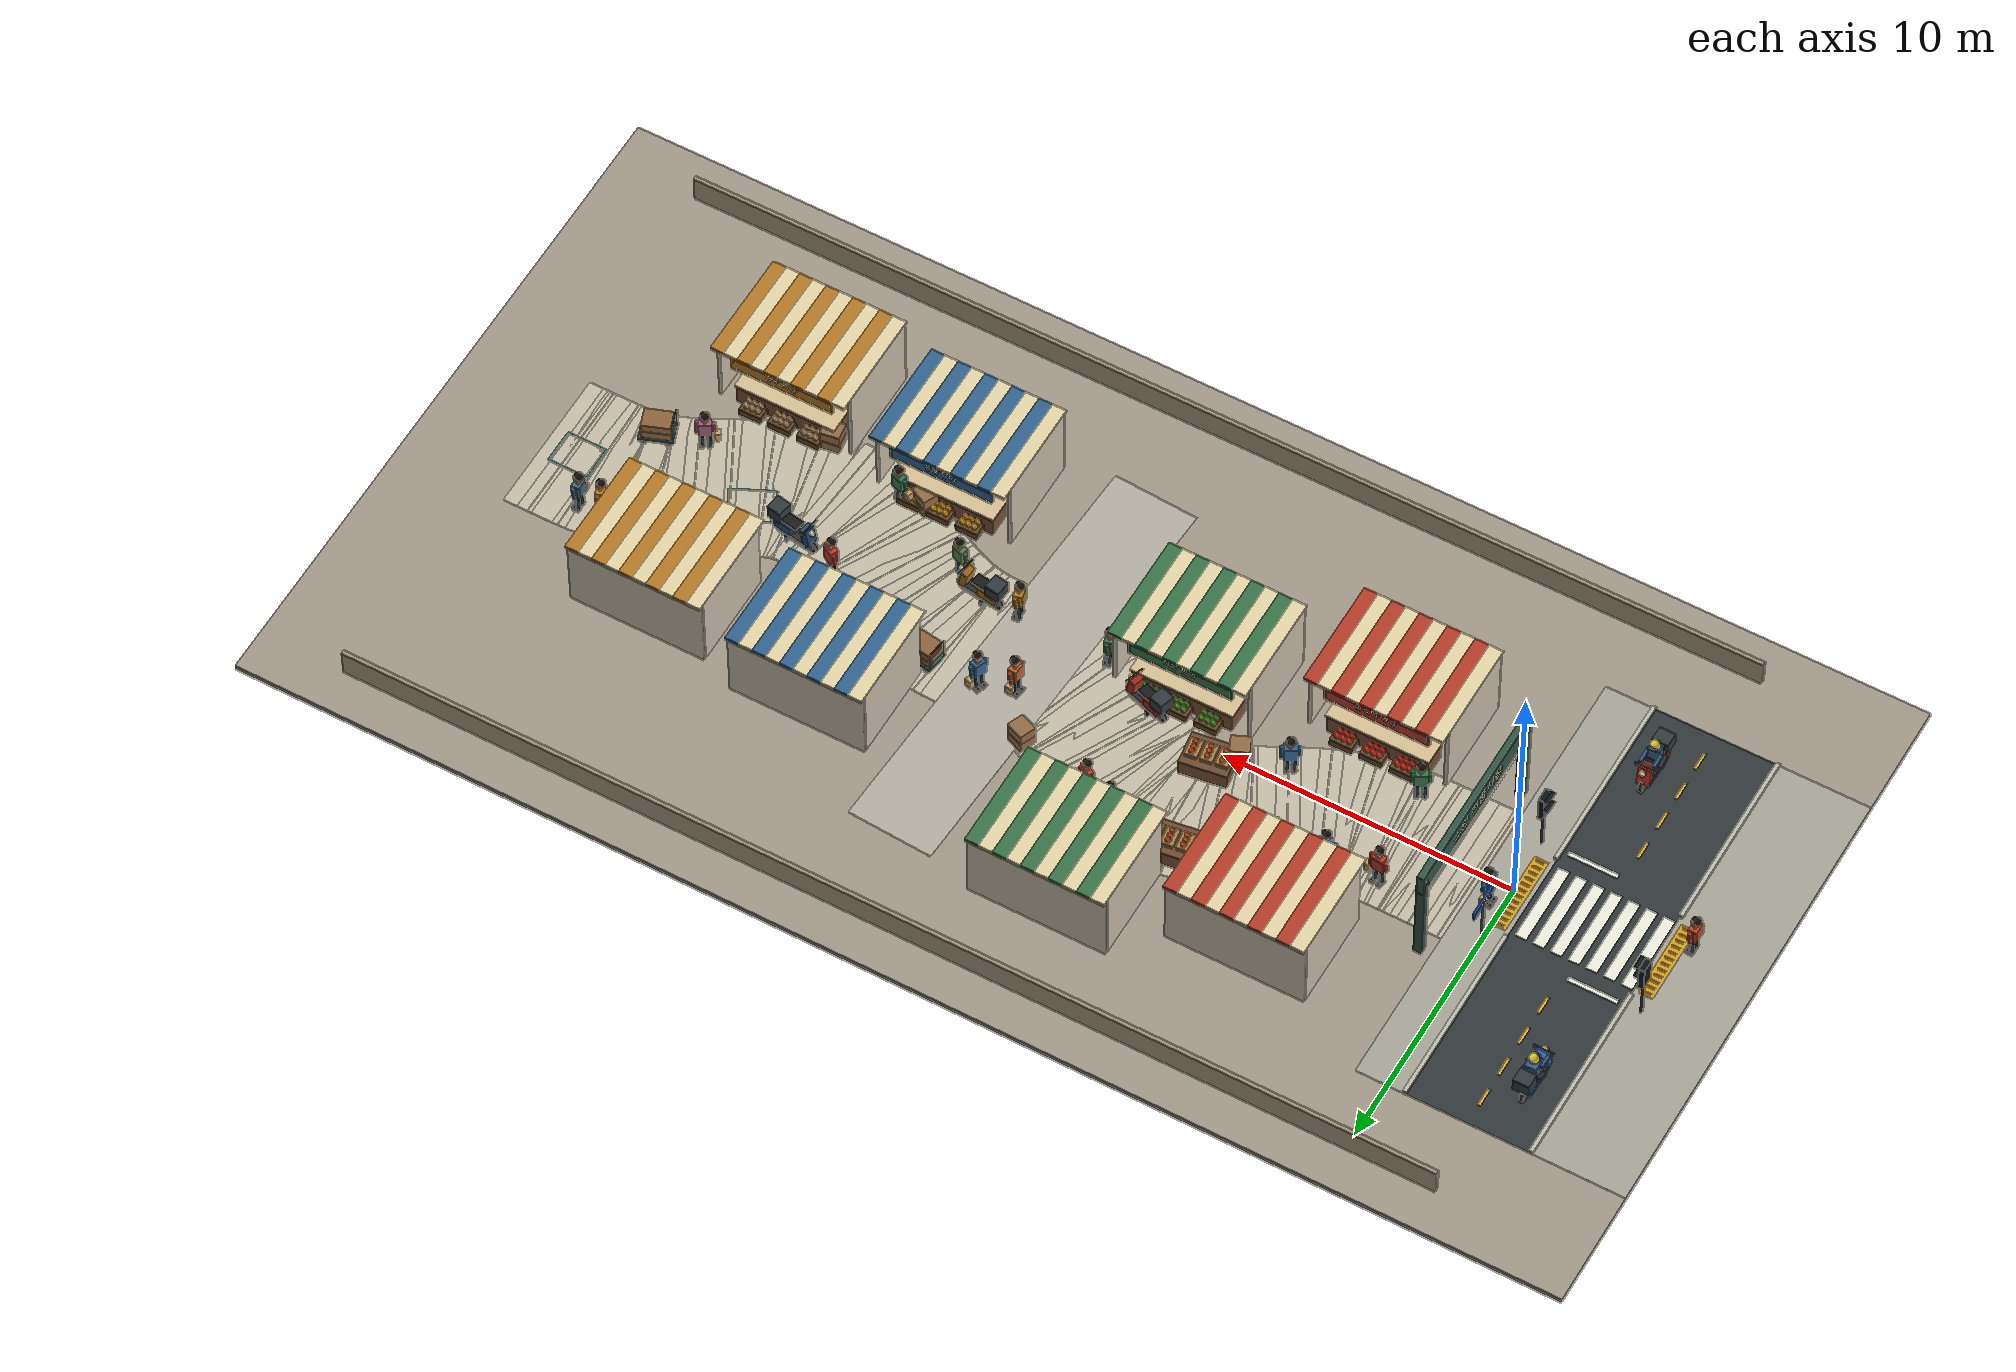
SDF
<?xml version='1.0' encoding='utf-8'?>
<sdf version="1.10">
  <world name="swan_market">
    <physics name="market_physics" type="ignored">
      <max_step_size>0.001</max_step_size>
      <real_time_factor>1</real_time_factor>
    </physics>
    <plugin filename="gz-sim-physics-system" name="gz::sim::systems::Physics" />
    <plugin filename="gz-sim-user-commands-system" name="gz::sim::systems::UserCommands" />
    <plugin filename="gz-sim-scene-broadcaster-system" name="gz::sim::systems::SceneBroadcaster" />
    <plugin filename="gz-sim-sensors-system" name="gz::sim::systems::Sensors">
      <render_engine>ogre2</render_engine>
    </plugin>
    <scene>
      <ambient>0.65 0.65 0.65 1</ambient>
      <background>0.74 0.82 0.86 1</background>
      <shadows>true</shadows>
    </scene>
    <light name="sun" type="directional">
      <pose>0 0 15 0 0 0</pose>
      <direction>-.3 -.5 -1</direction>
      <diffuse>.85 .82 .75 1</diffuse>
      <specular>.1 .1 .1 1</specular>
      <cast_shadows>true</cast_shadows>
    </light>
    <model name="ground">
      <static>true</static>
      <pose>15 0 -0.1 0 0 0</pose>
      <link name="body">
        <collision name="box_collision">
          <pose>0 0 0 0 0 0</pose>
          <geometry>
            <box>
              <size>46 24 0.2</size>
            </box>
          </geometry>
        </collision>
        <visual name="box_visual">
          <pose>0 0 0 0 0 0</pose>
          <geometry>
            <box>
              <size>46 24 0.2</size>
            </box>
          </geometry>
          <material>
            <ambient>0.64 0.61 0.55 1</ambient>
            <diffuse>0.64 0.61 0.55 1</diffuse>
          </material>
        </visual>
      </link>
    </model>
    <model name="market_paving_0">
      <static>true</static>
      <pose>-1.75 0 0.002 0 0 0</pose>
      <link name="body">
        <visual name="box_visual">
          <pose>0 0 0 0 0 0</pose>
          <geometry>
            <box>
              <size>0.75 5.2 0.004</size>
            </box>
          </geometry>
          <material>
            <ambient>0.79 0.76 0.68 1</ambient>
            <diffuse>0.79 0.76 0.68 1</diffuse>
          </material>
        </visual>
      </link>
    </model>
    <model name="paving_joint_0">
      <static>true</static>
      <pose>-1.75 0 0.0045 0 0 0</pose>
      <link name="body">
        <visual name="box_visual">
          <pose>0 0 0 0 0 0</pose>
          <geometry>
            <box>
              <size>0.025 5.2 0.001</size>
            </box>
          </geometry>
          <material>
            <ambient>0.67 0.64 0.57 1</ambient>
            <diffuse>0.67 0.64 0.57 1</diffuse>
          </material>
        </visual>
      </link>
    </model>
    <model name="market_paving_1">
      <static>true</static>
      <pose>-1.25 0 0.002 0 0 0</pose>
      <link name="body">
        <visual name="box_visual">
          <pose>0 0 0 0 0 0</pose>
          <geometry>
            <box>
              <size>0.75 5.2 0.004</size>
            </box>
          </geometry>
          <material>
            <ambient>0.79 0.76 0.68 1</ambient>
            <diffuse>0.79 0.76 0.68 1</diffuse>
          </material>
        </visual>
      </link>
    </model>
    <model name="market_paving_2">
      <static>true</static>
      <pose>-0.75 0 0.002 0 0 0</pose>
      <link name="body">
        <visual name="box_visual">
          <pose>0 0 0 0 0 0</pose>
          <geometry>
            <box>
              <size>0.75 5.2 0.004</size>
            </box>
          </geometry>
          <material>
            <ambient>0.79 0.76 0.68 1</ambient>
            <diffuse>0.79 0.76 0.68 1</diffuse>
          </material>
        </visual>
      </link>
    </model>
    <model name="paving_joint_2">
      <static>true</static>
      <pose>-0.75 0 0.0045 0 0 0</pose>
      <link name="body">
        <visual name="box_visual">
          <pose>0 0 0 0 0 0</pose>
          <geometry>
            <box>
              <size>0.025 5.2 0.001</size>
            </box>
          </geometry>
          <material>
            <ambient>0.67 0.64 0.57 1</ambient>
            <diffuse>0.67 0.64 0.57 1</diffuse>
          </material>
        </visual>
      </link>
    </model>
    <model name="market_paving_3">
      <static>true</static>
      <pose>-0.25 0 0.002 0 0 0</pose>
      <link name="body">
        <visual name="box_visual">
          <pose>0 0 0 0 0 0</pose>
          <geometry>
            <box>
              <size>0.75 5.2 0.004</size>
            </box>
          </geometry>
          <material>
            <ambient>0.79 0.76 0.68 1</ambient>
            <diffuse>0.79 0.76 0.68 1</diffuse>
          </material>
        </visual>
      </link>
    </model>
    <model name="market_paving_4">
      <static>true</static>
      <pose>0.25 0 0.002 0 0 0</pose>
      <link name="body">
        <visual name="box_visual">
          <pose>0 0 0 0 0 0</pose>
          <geometry>
            <box>
              <size>0.75 5.2 0.004</size>
            </box>
          </geometry>
          <material>
            <ambient>0.79 0.76 0.68 1</ambient>
            <diffuse>0.79 0.76 0.68 1</diffuse>
          </material>
        </visual>
      </link>
    </model>
    <model name="paving_joint_4">
      <static>true</static>
      <pose>0.25 0 0.0045 0 0 0</pose>
      <link name="body">
        <visual name="box_visual">
          <pose>0 0 0 0 0 0</pose>
          <geometry>
            <box>
              <size>0.025 5.2 0.001</size>
            </box>
          </geometry>
          <material>
            <ambient>0.67 0.64 0.57 1</ambient>
            <diffuse>0.67 0.64 0.57 1</diffuse>
          </material>
        </visual>
      </link>
    </model>
    <model name="market_paving_5">
      <static>true</static>
      <pose>0.75 0 0.002 0 0 0</pose>
      <link name="body">
        <visual name="box_visual">
          <pose>0 0 0 0 0 0</pose>
          <geometry>
            <box>
              <size>0.75 5.2 0.004</size>
            </box>
          </geometry>
          <material>
            <ambient>0.79 0.76 0.68 1</ambient>
            <diffuse>0.79 0.76 0.68 1</diffuse>
          </material>
        </visual>
      </link>
    </model>
    <model name="market_paving_6">
      <static>true</static>
      <pose>1.25 0 0.002 0 0 0</pose>
      <link name="body">
        <visual name="box_visual">
          <pose>0 0 0 0 0 0</pose>
          <geometry>
            <box>
              <size>0.75 5.2 0.004</size>
            </box>
          </geometry>
          <material>
            <ambient>0.79 0.76 0.68 1</ambient>
            <diffuse>0.79 0.76 0.68 1</diffuse>
          </material>
        </visual>
      </link>
    </model>
    <model name="paving_joint_6">
      <static>true</static>
      <pose>1.25 0 0.0045 0 0 0</pose>
      <link name="body">
        <visual name="box_visual">
          <pose>0 0 0 0 0 0</pose>
          <geometry>
            <box>
              <size>0.025 5.2 0.001</size>
            </box>
          </geometry>
          <material>
            <ambient>0.67 0.64 0.57 1</ambient>
            <diffuse>0.67 0.64 0.57 1</diffuse>
          </material>
        </visual>
      </link>
    </model>
    <model name="market_paving_7">
      <static>true</static>
      <pose>1.75 0 0.002 0 0 0</pose>
      <link name="body">
        <visual name="box_visual">
          <pose>0 0 0 0 0 0</pose>
          <geometry>
            <box>
              <size>0.75 5.2 0.004</size>
            </box>
          </geometry>
          <material>
            <ambient>0.79 0.76 0.68 1</ambient>
            <diffuse>0.79 0.76 0.68 1</diffuse>
          </material>
        </visual>
      </link>
    </model>
    <model name="market_paving_8">
      <static>true</static>
      <pose>2.25 0 0.002 0 0 0</pose>
      <link name="body">
        <visual name="box_visual">
          <pose>0 0 0 0 0 0</pose>
          <geometry>
            <box>
              <size>0.75 5.2 0.004</size>
            </box>
          </geometry>
          <material>
            <ambient>0.79 0.76 0.68 1</ambient>
            <diffuse>0.79 0.76 0.68 1</diffuse>
          </material>
        </visual>
      </link>
    </model>
    <model name="paving_joint_8">
      <static>true</static>
      <pose>2.25 0 0.0045 0 0 0</pose>
      <link name="body">
        <visual name="box_visual">
          <pose>0 0 0 0 0 0</pose>
          <geometry>
            <box>
              <size>0.025 5.2 0.001</size>
            </box>
          </geometry>
          <material>
            <ambient>0.67 0.64 0.57 1</ambient>
            <diffuse>0.67 0.64 0.57 1</diffuse>
          </material>
        </visual>
      </link>
    </model>
    <model name="market_paving_9">
      <static>true</static>
      <pose>2.75 0 0.002 0 0 0</pose>
      <link name="body">
        <visual name="box_visual">
          <pose>0 0 0 0 0 0</pose>
          <geometry>
            <box>
              <size>0.75 5.2 0.004</size>
            </box>
          </geometry>
          <material>
            <ambient>0.79 0.76 0.68 1</ambient>
            <diffuse>0.79 0.76 0.68 1</diffuse>
          </material>
        </visual>
      </link>
    </model>
    <model name="market_paving_10">
      <static>true</static>
      <pose>3.25 0.00031537 0.002 0 0 0.003781</pose>
      <link name="body">
        <visual name="box_visual">
          <pose>0 0 0 0 0 0</pose>
          <geometry>
            <box>
              <size>0.75 5.2 0.004</size>
            </box>
          </geometry>
          <material>
            <ambient>0.79 0.76 0.68 1</ambient>
            <diffuse>0.79 0.76 0.68 1</diffuse>
          </material>
        </visual>
      </link>
    </model>
    <model name="paving_joint_10">
      <static>true</static>
      <pose>3.25 0.00031537 0.0045 0 0 0.003781</pose>
      <link name="body">
        <visual name="box_visual">
          <pose>0 0 0 0 0 0</pose>
          <geometry>
            <box>
              <size>0.025 5.2 0.001</size>
            </box>
          </geometry>
          <material>
            <ambient>0.67 0.64 0.57 1</ambient>
            <diffuse>0.67 0.64 0.57 1</diffuse>
          </material>
        </visual>
      </link>
    </model>
    <model name="market_paving_11">
      <static>true</static>
      <pose>3.75 0.0084221 0.002 0 0 0.033398</pose>
      <link name="body">
        <visual name="box_visual">
          <pose>0 0 0 0 0 0</pose>
          <geometry>
            <box>
              <size>0.75 5.2 0.004</size>
            </box>
          </geometry>
          <material>
            <ambient>0.79 0.76 0.68 1</ambient>
            <diffuse>0.79 0.76 0.68 1</diffuse>
          </material>
        </visual>
      </link>
    </model>
    <model name="market_paving_12">
      <static>true</static>
      <pose>4.25 0.038143 0.002 0 0 0.089204</pose>
      <link name="body">
        <visual name="box_visual">
          <pose>0 0 0 0 0 0</pose>
          <geometry>
            <box>
              <size>0.75 5.2 0.004</size>
            </box>
          </geometry>
          <material>
            <ambient>0.79 0.76 0.68 1</ambient>
            <diffuse>0.79 0.76 0.68 1</diffuse>
          </material>
        </visual>
      </link>
    </model>
    <model name="paving_joint_12">
      <static>true</static>
      <pose>4.25 0.038143 0.0045 0 0 0.089204</pose>
      <link name="body">
        <visual name="box_visual">
          <pose>0 0 0 0 0 0</pose>
          <geometry>
            <box>
              <size>0.025 5.2 0.001</size>
            </box>
          </geometry>
          <material>
            <ambient>0.67 0.64 0.57 1</ambient>
            <diffuse>0.67 0.64 0.57 1</diffuse>
          </material>
        </visual>
      </link>
    </model>
    <model name="market_paving_13">
      <static>true</static>
      <pose>4.75 0.10125 0.002 0 0 0.16424</pose>
      <link name="body">
        <visual name="box_visual">
          <pose>0 0 0 0 0 0</pose>
          <geometry>
            <box>
              <size>0.75 5.2 0.004</size>
            </box>
          </geometry>
          <material>
            <ambient>0.79 0.76 0.68 1</ambient>
            <diffuse>0.79 0.76 0.68 1</diffuse>
          </material>
        </visual>
      </link>
    </model>
    <model name="market_paving_14">
      <static>true</static>
      <pose>5.25 0.20586 0.002 0 0 0.2486</pose>
      <link name="body">
        <visual name="box_visual">
          <pose>0 0 0 0 0 0</pose>
          <geometry>
            <box>
              <size>0.75 5.2 0.004</size>
            </box>
          </geometry>
          <material>
            <ambient>0.79 0.76 0.68 1</ambient>
            <diffuse>0.79 0.76 0.68 1</diffuse>
          </material>
        </visual>
      </link>
    </model>
    <model name="paving_joint_14">
      <static>true</static>
      <pose>5.25 0.20586 0.0045 0 0 0.2486</pose>
      <link name="body">
        <visual name="box_visual">
          <pose>0 0 0 0 0 0</pose>
          <geometry>
            <box>
              <size>0.025 5.2 0.001</size>
            </box>
          </geometry>
          <material>
            <ambient>0.67 0.64 0.57 1</ambient>
            <diffuse>0.67 0.64 0.57 1</diffuse>
          </material>
        </visual>
      </link>
    </model>
    <model name="market_paving_15">
      <static>true</static>
      <pose>5.75 0.35543 0.002 0 0 0.33122</pose>
      <link name="body">
        <visual name="box_visual">
          <pose>0 0 0 0 0 0</pose>
          <geometry>
            <box>
              <size>0.75 5.2 0.004</size>
            </box>
          </geometry>
          <material>
            <ambient>0.79 0.76 0.68 1</ambient>
            <diffuse>0.79 0.76 0.68 1</diffuse>
          </material>
        </visual>
      </link>
    </model>
    <model name="market_paving_16">
      <static>true</static>
      <pose>6.25 0.54833 0.002 0 0 0.40225</pose>
      <link name="body">
        <visual name="box_visual">
          <pose>0 0 0 0 0 0</pose>
          <geometry>
            <box>
              <size>0.75 5.2 0.004</size>
            </box>
          </geometry>
          <material>
            <ambient>0.79 0.76 0.68 1</ambient>
            <diffuse>0.79 0.76 0.68 1</diffuse>
          </material>
        </visual>
      </link>
    </model>
    <model name="paving_joint_16">
      <static>true</static>
      <pose>6.25 0.54833 0.0045 0 0 0.40225</pose>
      <link name="body">
        <visual name="box_visual">
          <pose>0 0 0 0 0 0</pose>
          <geometry>
            <box>
              <size>0.025 5.2 0.001</size>
            </box>
          </geometry>
          <material>
            <ambient>0.67 0.64 0.57 1</ambient>
            <diffuse>0.67 0.64 0.57 1</diffuse>
          </material>
        </visual>
      </link>
    </model>
    <model name="market_paving_17">
      <static>true</static>
      <pose>6.75 0.77782 0.002 0 0 0.45458</pose>
      <link name="body">
        <visual name="box_visual">
          <pose>0 0 0 0 0 0</pose>
          <geometry>
            <box>
              <size>0.75 5.2 0.004</size>
            </box>
          </geometry>
          <material>
            <ambient>0.79 0.76 0.68 1</ambient>
            <diffuse>0.79 0.76 0.68 1</diffuse>
          </material>
        </visual>
      </link>
    </model>
    <model name="market_paving_18">
      <static>true</static>
      <pose>7.25 1.0326 0.002 0 0 0.48375</pose>
      <link name="body">
        <visual name="box_visual">
          <pose>0 0 0 0 0 0</pose>
          <geometry>
            <box>
              <size>0.75 5.2 0.004</size>
            </box>
          </geometry>
          <material>
            <ambient>0.79 0.76 0.68 1</ambient>
            <diffuse>0.79 0.76 0.68 1</diffuse>
          </material>
        </visual>
      </link>
    </model>
    <model name="paving_joint_18">
      <static>true</static>
      <pose>7.25 1.0326 0.0045 0 0 0.48375</pose>
      <link name="body">
        <visual name="box_visual">
          <pose>0 0 0 0 0 0</pose>
          <geometry>
            <box>
              <size>0.025 5.2 0.001</size>
            </box>
          </geometry>
          <material>
            <ambient>0.67 0.64 0.57 1</ambient>
            <diffuse>0.67 0.64 0.57 1</diffuse>
          </material>
        </visual>
      </link>
    </model>
    <model name="market_paving_19">
      <static>true</static>
      <pose>7.75 1.2978 0.002 0 0 0.48699</pose>
      <link name="body">
        <visual name="box_visual">
          <pose>0 0 0 0 0 0</pose>
          <geometry>
            <box>
              <size>0.75 5.2 0.004</size>
            </box>
          </geometry>
          <material>
            <ambient>0.79 0.76 0.68 1</ambient>
            <diffuse>0.79 0.76 0.68 1</diffuse>
          </material>
        </visual>
      </link>
    </model>
    <model name="market_paving_20">
      <static>true</static>
      <pose>8.25 1.5562 0.002 0 0 0.46221</pose>
      <link name="body">
        <visual name="box_visual">
          <pose>0 0 0 0 0 0</pose>
          <geometry>
            <box>
              <size>0.75 5.2 0.004</size>
            </box>
          </geometry>
          <material>
            <ambient>0.79 0.76 0.68 1</ambient>
            <diffuse>0.79 0.76 0.68 1</diffuse>
          </material>
        </visual>
      </link>
    </model>
    <model name="paving_joint_20">
      <static>true</static>
      <pose>8.25 1.5562 0.0045 0 0 0.46221</pose>
      <link name="body">
        <visual name="box_visual">
          <pose>0 0 0 0 0 0</pose>
          <geometry>
            <box>
              <size>0.025 5.2 0.001</size>
            </box>
          </geometry>
          <material>
            <ambient>0.67 0.64 0.57 1</ambient>
            <diffuse>0.67 0.64 0.57 1</diffuse>
          </material>
        </visual>
      </link>
    </model>
    <model name="market_paving_21">
      <static>true</static>
      <pose>8.75 1.7901 0.002 0 0 0.40758</pose>
      <link name="body">
        <visual name="box_visual">
          <pose>0 0 0 0 0 0</pose>
          <geometry>
            <box>
              <size>0.75 5.2 0.004</size>
            </box>
          </geometry>
          <material>
            <ambient>0.79 0.76 0.68 1</ambient>
            <diffuse>0.79 0.76 0.68 1</diffuse>
          </material>
        </visual>
      </link>
    </model>
    <model name="market_paving_22">
      <static>true</static>
      <pose>9.25 1.9827 0.002 0 0 0.32217</pose>
      <link name="body">
        <visual name="box_visual">
          <pose>0 0 0 0 0 0</pose>
          <geometry>
            <box>
              <size>0.75 5.2 0.004</size>
            </box>
          </geometry>
          <material>
            <ambient>0.79 0.76 0.68 1</ambient>
            <diffuse>0.79 0.76 0.68 1</diffuse>
          </material>
        </visual>
      </link>
    </model>
    <model name="paving_joint_22">
      <static>true</static>
      <pose>9.25 1.9827 0.0045 0 0 0.32217</pose>
      <link name="body">
        <visual name="box_visual">
          <pose>0 0 0 0 0 0</pose>
          <geometry>
            <box>
              <size>0.025 5.2 0.001</size>
            </box>
          </geometry>
          <material>
            <ambient>0.67 0.64 0.57 1</ambient>
            <diffuse>0.67 0.64 0.57 1</diffuse>
          </material>
        </visual>
      </link>
    </model>
    <model name="market_paving_23">
      <static>true</static>
      <pose>9.75 2.1197 0.002 0 0 0.2079</pose>
      <link name="body">
        <visual name="box_visual">
          <pose>0 0 0 0 0 0</pose>
          <geometry>
            <box>
              <size>0.75 5.2 0.004</size>
            </box>
          </geometry>
          <material>
            <ambient>0.79 0.76 0.68 1</ambient>
            <diffuse>0.79 0.76 0.68 1</diffuse>
          </material>
        </visual>
      </link>
    </model>
    <model name="market_paving_24">
      <static>true</static>
      <pose>10.25 2.191 0.002 0 0 0.072021</pose>
      <link name="body">
        <visual name="box_visual">
          <pose>0 0 0 0 0 0</pose>
          <geometry>
            <box>
              <size>0.75 5.2 0.004</size>
            </box>
          </geometry>
          <material>
            <ambient>0.79 0.76 0.68 1</ambient>
            <diffuse>0.79 0.76 0.68 1</diffuse>
          </material>
        </visual>
      </link>
    </model>
    <model name="paving_joint_24">
      <static>true</static>
      <pose>10.25 2.191 0.0045 0 0 0.072021</pose>
      <link name="body">
        <visual name="box_visual">
          <pose>0 0 0 0 0 0</pose>
          <geometry>
            <box>
              <size>0.025 5.2 0.001</size>
            </box>
          </geometry>
          <material>
            <ambient>0.67 0.64 0.57 1</ambient>
            <diffuse>0.67 0.64 0.57 1</diffuse>
          </material>
        </visual>
      </link>
    </model>
    <model name="market_paving_25">
      <static>true</static>
      <pose>10.75 2.191 0.002 0 0 -0.072021</pose>
      <link name="body">
        <visual name="box_visual">
          <pose>0 0 0 0 0 0</pose>
          <geometry>
            <box>
              <size>0.75 5.2 0.004</size>
            </box>
          </geometry>
          <material>
            <ambient>0.79 0.76 0.68 1</ambient>
            <diffuse>0.79 0.76 0.68 1</diffuse>
          </material>
        </visual>
      </link>
    </model>
    <model name="market_paving_26">
      <static>true</static>
      <pose>11.25 2.1197 0.002 0 0 -0.2079</pose>
      <link name="body">
        <visual name="box_visual">
          <pose>0 0 0 0 0 0</pose>
          <geometry>
            <box>
              <size>0.75 5.2 0.004</size>
            </box>
          </geometry>
          <material>
            <ambient>0.79 0.76 0.68 1</ambient>
            <diffuse>0.79 0.76 0.68 1</diffuse>
          </material>
        </visual>
      </link>
    </model>
    <model name="paving_joint_26">
      <static>true</static>
      <pose>11.25 2.1197 0.0045 0 0 -0.2079</pose>
      <link name="body">
        <visual name="box_visual">
          <pose>0 0 0 0 0 0</pose>
          <geometry>
            <box>
              <size>0.025 5.2 0.001</size>
            </box>
          </geometry>
          <material>
            <ambient>0.67 0.64 0.57 1</ambient>
            <diffuse>0.67 0.64 0.57 1</diffuse>
          </material>
        </visual>
      </link>
    </model>
    <model name="market_paving_27">
      <static>true</static>
      <pose>11.75 1.9827 0.002 0 0 -0.32217</pose>
      <link name="body">
        <visual name="box_visual">
          <pose>0 0 0 0 0 0</pose>
          <geometry>
            <box>
              <size>0.75 5.2 0.004</size>
            </box>
          </geometry>
          <material>
            <ambient>0.79 0.76 0.68 1</ambient>
            <diffuse>0.79 0.76 0.68 1</diffuse>
          </material>
        </visual>
      </link>
    </model>
    <model name="market_paving_28">
      <static>true</static>
      <pose>12.25 1.7901 0.002 0 0 -0.40758</pose>
      <link name="body">
        <visual name="box_visual">
          <pose>0 0 0 0 0 0</pose>
          <geometry>
            <box>
              <size>0.75 5.2 0.004</size>
            </box>
          </geometry>
          <material>
            <ambient>0.79 0.76 0.68 1</ambient>
            <diffuse>0.79 0.76 0.68 1</diffuse>
          </material>
        </visual>
      </link>
    </model>
    <model name="paving_joint_28">
      <static>true</static>
      <pose>12.25 1.7901 0.0045 0 0 -0.40758</pose>
      <link name="body">
        <visual name="box_visual">
          <pose>0 0 0 0 0 0</pose>
          <geometry>
            <box>
              <size>0.025 5.2 0.001</size>
            </box>
          </geometry>
          <material>
            <ambient>0.67 0.64 0.57 1</ambient>
            <diffuse>0.67 0.64 0.57 1</diffuse>
          </material>
        </visual>
      </link>
    </model>
    <model name="market_paving_29">
      <static>true</static>
      <pose>12.75 1.5562 0.002 0 0 -0.46221</pose>
      <link name="body">
        <visual name="box_visual">
          <pose>0 0 0 0 0 0</pose>
          <geometry>
            <box>
              <size>0.75 5.2 0.004</size>
            </box>
          </geometry>
          <material>
            <ambient>0.79 0.76 0.68 1</ambient>
            <diffuse>0.79 0.76 0.68 1</diffuse>
          </material>
        </visual>
      </link>
    </model>
    <model name="market_paving_30">
      <static>true</static>
      <pose>13.25 1.2978 0.002 0 0 -0.48699</pose>
      <link name="body">
        <visual name="box_visual">
          <pose>0 0 0 0 0 0</pose>
          <geometry>
            <box>
              <size>0.75 5.2 0.004</size>
            </box>
          </geometry>
          <material>
            <ambient>0.79 0.76 0.68 1</ambient>
            <diffuse>0.79 0.76 0.68 1</diffuse>
          </material>
        </visual>
      </link>
    </model>
    <model name="paving_joint_30">
      <static>true</static>
      <pose>13.25 1.2978 0.0045 0 0 -0.48699</pose>
      <link name="body">
        <visual name="box_visual">
          <pose>0 0 0 0 0 0</pose>
          <geometry>
            <box>
              <size>0.025 5.2 0.001</size>
            </box>
          </geometry>
          <material>
            <ambient>0.67 0.64 0.57 1</ambient>
            <diffuse>0.67 0.64 0.57 1</diffuse>
          </material>
        </visual>
      </link>
    </model>
    <model name="market_paving_31">
      <static>true</static>
      <pose>13.75 1.0326 0.002 0 0 -0.48375</pose>
      <link name="body">
        <visual name="box_visual">
          <pose>0 0 0 0 0 0</pose>
          <geometry>
            <box>
              <size>0.75 5.2 0.004</size>
            </box>
          </geometry>
          <material>
            <ambient>0.79 0.76 0.68 1</ambient>
            <diffuse>0.79 0.76 0.68 1</diffuse>
          </material>
        </visual>
      </link>
    </model>
    <model name="market_paving_32">
      <static>true</static>
      <pose>14.25 0.77782 0.002 0 0 -0.45458</pose>
      <link name="body">
        <visual name="box_visual">
          <pose>0 0 0 0 0 0</pose>
          <geometry>
            <box>
              <size>0.75 5.2 0.004</size>
            </box>
          </geometry>
          <material>
            <ambient>0.79 0.76 0.68 1</ambient>
            <diffuse>0.79 0.76 0.68 1</diffuse>
          </material>
        </visual>
      </link>
    </model>
    <model name="paving_joint_32">
      <static>true</static>
      <pose>14.25 0.77782 0.0045 0 0 -0.45458</pose>
      <link name="body">
        <visual name="box_visual">
          <pose>0 0 0 0 0 0</pose>
          <geometry>
            <box>
              <size>0.025 5.2 0.001</size>
            </box>
          </geometry>
          <material>
            <ambient>0.67 0.64 0.57 1</ambient>
            <diffuse>0.67 0.64 0.57 1</diffuse>
          </material>
        </visual>
      </link>
    </model>
    <model name="market_paving_33">
      <static>true</static>
      <pose>14.75 0.54833 0.002 0 0 -0.40225</pose>
      <link name="body">
        <visual name="box_visual">
          <pose>0 0 0 0 0 0</pose>
          <geometry>
            <box>
              <size>0.75 5.2 0.004</size>
            </box>
          </geometry>
          <material>
            <ambient>0.79 0.76 0.68 1</ambient>
            <diffuse>0.79 0.76 0.68 1</diffuse>
          </material>
        </visual>
      </link>
    </model>
    <model name="market_paving_34">
      <static>true</static>
      <pose>15.25 0.35543 0.002 0 0 -0.33122</pose>
      <link name="body">
        <visual name="box_visual">
          <pose>0 0 0 0 0 0</pose>
          <geometry>
            <box>
              <size>0.75 5.2 0.004</size>
            </box>
          </geometry>
          <material>
            <ambient>0.79 0.76 0.68 1</ambient>
            <diffuse>0.79 0.76 0.68 1</diffuse>
          </material>
        </visual>
      </link>
    </model>
    <model name="paving_joint_34">
      <static>true</static>
      <pose>15.25 0.35543 0.0045 0 0 -0.33122</pose>
      <link name="body">
        <visual name="box_visual">
          <pose>0 0 0 0 0 0</pose>
          <geometry>
            <box>
              <size>0.025 5.2 0.001</size>
            </box>
          </geometry>
          <material>
            <ambient>0.67 0.64 0.57 1</ambient>
            <diffuse>0.67 0.64 0.57 1</diffuse>
          </material>
        </visual>
      </link>
    </model>
    <model name="market_paving_35">
      <static>true</static>
      <pose>15.75 0.20586 0.002 0 0 -0.2486</pose>
      <link name="body">
        <visual name="box_visual">
          <pose>0 0 0 0 0 0</pose>
          <geometry>
            <box>
              <size>0.75 5.2 0.004</size>
            </box>
          </geometry>
          <material>
            <ambient>0.79 0.76 0.68 1</ambient>
            <diffuse>0.79 0.76 0.68 1</diffuse>
          </material>
        </visual>
      </link>
    </model>
    <model name="market_paving_36">
      <static>true</static>
      <pose>16.25 0.10125 0.002 0 0 -0.16424</pose>
      <link name="body">
        <visual name="box_visual">
          <pose>0 0 0 0 0 0</pose>
          <geometry>
            <box>
              <size>0.75 5.2 0.004</size>
            </box>
          </geometry>
          <material>
            <ambient>0.79 0.76 0.68 1</ambient>
            <diffuse>0.79 0.76 0.68 1</diffuse>
          </material>
        </visual>
      </link>
    </model>
    <model name="paving_joint_36">
      <static>true</static>
      <pose>16.25 0.10125 0.0045 0 0 -0.16424</pose>
      <link name="body">
        <visual name="box_visual">
          <pose>0 0 0 0 0 0</pose>
          <geometry>
            <box>
              <size>0.025 5.2 0.001</size>
            </box>
          </geometry>
          <material>
            <ambient>0.67 0.64 0.57 1</ambient>
            <diffuse>0.67 0.64 0.57 1</diffuse>
          </material>
        </visual>
      </link>
    </model>
    <model name="market_paving_37">
      <static>true</static>
      <pose>16.75 0.038143 0.002 0 0 -0.089204</pose>
      <link name="body">
        <visual name="box_visual">
          <pose>0 0 0 0 0 0</pose>
          <geometry>
            <box>
              <size>0.75 5.2 0.004</size>
            </box>
          </geometry>
          <material>
            <ambient>0.79 0.76 0.68 1</ambient>
            <diffuse>0.79 0.76 0.68 1</diffuse>
          </material>
        </visual>
      </link>
    </model>
    <model name="market_paving_38">
      <static>true</static>
      <pose>17.25 0.0084221 0.002 0 0 -0.033398</pose>
      <link name="body">
        <visual name="box_visual">
          <pose>0 0 0 0 0 0</pose>
          <geometry>
            <box>
              <size>0.75 5.2 0.004</size>
            </box>
          </geometry>
          <material>
            <ambient>0.79 0.76 0.68 1</ambient>
            <diffuse>0.79 0.76 0.68 1</diffuse>
          </material>
        </visual>
      </link>
    </model>
    <model name="paving_joint_38">
      <static>true</static>
      <pose>17.25 0.0084221 0.0045 0 0 -0.033398</pose>
      <link name="body">
        <visual name="box_visual">
          <pose>0 0 0 0 0 0</pose>
          <geometry>
            <box>
              <size>0.025 5.2 0.001</size>
            </box>
          </geometry>
          <material>
            <ambient>0.67 0.64 0.57 1</ambient>
            <diffuse>0.67 0.64 0.57 1</diffuse>
          </material>
        </visual>
      </link>
    </model>
    <model name="market_paving_39">
      <static>true</static>
      <pose>17.75 0.00031537 0.002 0 0 -0.003781</pose>
      <link name="body">
        <visual name="box_visual">
          <pose>0 0 0 0 0 0</pose>
          <geometry>
            <box>
              <size>0.75 5.2 0.004</size>
            </box>
          </geometry>
          <material>
            <ambient>0.79 0.76 0.68 1</ambient>
            <diffuse>0.79 0.76 0.68 1</diffuse>
          </material>
        </visual>
      </link>
    </model>
    <model name="market_paving_40">
      <static>true</static>
      <pose>18.25 -0.00031537 0.002 0 0 -0.003781</pose>
      <link name="body">
        <visual name="box_visual">
          <pose>0 0 0 0 0 0</pose>
          <geometry>
            <box>
              <size>0.75 5.2 0.004</size>
            </box>
          </geometry>
          <material>
            <ambient>0.79 0.76 0.68 1</ambient>
            <diffuse>0.79 0.76 0.68 1</diffuse>
          </material>
        </visual>
      </link>
    </model>
    <model name="paving_joint_40">
      <static>true</static>
      <pose>18.25 -0.00031537 0.0045 0 0 -0.003781</pose>
      <link name="body">
        <visual name="box_visual">
          <pose>0 0 0 0 0 0</pose>
          <geometry>
            <box>
              <size>0.025 5.2 0.001</size>
            </box>
          </geometry>
          <material>
            <ambient>0.67 0.64 0.57 1</ambient>
            <diffuse>0.67 0.64 0.57 1</diffuse>
          </material>
        </visual>
      </link>
    </model>
    <model name="market_paving_41">
      <static>true</static>
      <pose>18.75 -0.0084221 0.002 0 0 -0.033398</pose>
      <link name="body">
        <visual name="box_visual">
          <pose>0 0 0 0 0 0</pose>
          <geometry>
            <box>
              <size>0.75 5.2 0.004</size>
            </box>
          </geometry>
          <material>
            <ambient>0.79 0.76 0.68 1</ambient>
            <diffuse>0.79 0.76 0.68 1</diffuse>
          </material>
        </visual>
      </link>
    </model>
    <model name="market_paving_42">
      <static>true</static>
      <pose>19.25 -0.038143 0.002 0 0 -0.089204</pose>
      <link name="body">
        <visual name="box_visual">
          <pose>0 0 0 0 0 0</pose>
          <geometry>
            <box>
              <size>0.75 5.2 0.004</size>
            </box>
          </geometry>
          <material>
            <ambient>0.79 0.76 0.68 1</ambient>
            <diffuse>0.79 0.76 0.68 1</diffuse>
          </material>
        </visual>
      </link>
    </model>
    <model name="paving_joint_42">
      <static>true</static>
      <pose>19.25 -0.038143 0.0045 0 0 -0.089204</pose>
      <link name="body">
        <visual name="box_visual">
          <pose>0 0 0 0 0 0</pose>
          <geometry>
            <box>
              <size>0.025 5.2 0.001</size>
            </box>
          </geometry>
          <material>
            <ambient>0.67 0.64 0.57 1</ambient>
            <diffuse>0.67 0.64 0.57 1</diffuse>
          </material>
        </visual>
      </link>
    </model>
    <model name="market_paving_43">
      <static>true</static>
      <pose>19.75 -0.10125 0.002 0 0 -0.16424</pose>
      <link name="body">
        <visual name="box_visual">
          <pose>0 0 0 0 0 0</pose>
          <geometry>
            <box>
              <size>0.75 5.2 0.004</size>
            </box>
          </geometry>
          <material>
            <ambient>0.79 0.76 0.68 1</ambient>
            <diffuse>0.79 0.76 0.68 1</diffuse>
          </material>
        </visual>
      </link>
    </model>
    <model name="market_paving_44">
      <static>true</static>
      <pose>20.25 -0.20586 0.002 0 0 -0.2486</pose>
      <link name="body">
        <visual name="box_visual">
          <pose>0 0 0 0 0 0</pose>
          <geometry>
            <box>
              <size>0.75 5.2 0.004</size>
            </box>
          </geometry>
          <material>
            <ambient>0.79 0.76 0.68 1</ambient>
            <diffuse>0.79 0.76 0.68 1</diffuse>
          </material>
        </visual>
      </link>
    </model>
    <model name="paving_joint_44">
      <static>true</static>
      <pose>20.25 -0.20586 0.0045 0 0 -0.2486</pose>
      <link name="body">
        <visual name="box_visual">
          <pose>0 0 0 0 0 0</pose>
          <geometry>
            <box>
              <size>0.025 5.2 0.001</size>
            </box>
          </geometry>
          <material>
            <ambient>0.67 0.64 0.57 1</ambient>
            <diffuse>0.67 0.64 0.57 1</diffuse>
          </material>
        </visual>
      </link>
    </model>
    <model name="market_paving_45">
      <static>true</static>
      <pose>20.75 -0.35543 0.002 0 0 -0.33122</pose>
      <link name="body">
        <visual name="box_visual">
          <pose>0 0 0 0 0 0</pose>
          <geometry>
            <box>
              <size>0.75 5.2 0.004</size>
            </box>
          </geometry>
          <material>
            <ambient>0.79 0.76 0.68 1</ambient>
            <diffuse>0.79 0.76 0.68 1</diffuse>
          </material>
        </visual>
      </link>
    </model>
    <model name="market_paving_46">
      <static>true</static>
      <pose>21.25 -0.54833 0.002 0 0 -0.40225</pose>
      <link name="body">
        <visual name="box_visual">
          <pose>0 0 0 0 0 0</pose>
          <geometry>
            <box>
              <size>0.75 5.2 0.004</size>
            </box>
          </geometry>
          <material>
            <ambient>0.79 0.76 0.68 1</ambient>
            <diffuse>0.79 0.76 0.68 1</diffuse>
          </material>
        </visual>
      </link>
    </model>
    <model name="paving_joint_46">
      <static>true</static>
      <pose>21.25 -0.54833 0.0045 0 0 -0.40225</pose>
      <link name="body">
        <visual name="box_visual">
          <pose>0 0 0 0 0 0</pose>
          <geometry>
            <box>
              <size>0.025 5.2 0.001</size>
            </box>
          </geometry>
          <material>
            <ambient>0.67 0.64 0.57 1</ambient>
            <diffuse>0.67 0.64 0.57 1</diffuse>
          </material>
        </visual>
      </link>
    </model>
    <model name="market_paving_47">
      <static>true</static>
      <pose>21.75 -0.77782 0.002 0 0 -0.45458</pose>
      <link name="body">
        <visual name="box_visual">
          <pose>0 0 0 0 0 0</pose>
          <geometry>
            <box>
              <size>0.75 5.2 0.004</size>
            </box>
          </geometry>
          <material>
            <ambient>0.79 0.76 0.68 1</ambient>
            <diffuse>0.79 0.76 0.68 1</diffuse>
          </material>
        </visual>
      </link>
    </model>
    <model name="market_paving_48">
      <static>true</static>
      <pose>22.25 -1.0326 0.002 0 0 -0.48375</pose>
      <link name="body">
        <visual name="box_visual">
          <pose>0 0 0 0 0 0</pose>
          <geometry>
            <box>
              <size>0.75 5.2 0.004</size>
            </box>
          </geometry>
          <material>
            <ambient>0.79 0.76 0.68 1</ambient>
            <diffuse>0.79 0.76 0.68 1</diffuse>
          </material>
        </visual>
      </link>
    </model>
    <model name="paving_joint_48">
      <static>true</static>
      <pose>22.25 -1.0326 0.0045 0 0 -0.48375</pose>
      <link name="body">
        <visual name="box_visual">
          <pose>0 0 0 0 0 0</pose>
          <geometry>
            <box>
              <size>0.025 5.2 0.001</size>
            </box>
          </geometry>
          <material>
            <ambient>0.67 0.64 0.57 1</ambient>
            <diffuse>0.67 0.64 0.57 1</diffuse>
          </material>
        </visual>
      </link>
    </model>
    <model name="market_paving_49">
      <static>true</static>
      <pose>22.75 -1.2978 0.002 0 0 -0.48699</pose>
      <link name="body">
        <visual name="box_visual">
          <pose>0 0 0 0 0 0</pose>
          <geometry>
            <box>
              <size>0.75 5.2 0.004</size>
            </box>
          </geometry>
          <material>
            <ambient>0.79 0.76 0.68 1</ambient>
            <diffuse>0.79 0.76 0.68 1</diffuse>
          </material>
        </visual>
      </link>
    </model>
    <model name="market_paving_50">
      <static>true</static>
      <pose>23.25 -1.5562 0.002 0 0 -0.46221</pose>
      <link name="body">
        <visual name="box_visual">
          <pose>0 0 0 0 0 0</pose>
          <geometry>
            <box>
              <size>0.75 5.2 0.004</size>
            </box>
          </geometry>
          <material>
            <ambient>0.79 0.76 0.68 1</ambient>
            <diffuse>0.79 0.76 0.68 1</diffuse>
          </material>
        </visual>
      </link>
    </model>
    <model name="paving_joint_50">
      <static>true</static>
      <pose>23.25 -1.5562 0.0045 0 0 -0.46221</pose>
      <link name="body">
        <visual name="box_visual">
          <pose>0 0 0 0 0 0</pose>
          <geometry>
            <box>
              <size>0.025 5.2 0.001</size>
            </box>
          </geometry>
          <material>
            <ambient>0.67 0.64 0.57 1</ambient>
            <diffuse>0.67 0.64 0.57 1</diffuse>
          </material>
        </visual>
      </link>
    </model>
    <model name="market_paving_51">
      <static>true</static>
      <pose>23.75 -1.7901 0.002 0 0 -0.40758</pose>
      <link name="body">
        <visual name="box_visual">
          <pose>0 0 0 0 0 0</pose>
          <geometry>
            <box>
              <size>0.75 5.2 0.004</size>
            </box>
          </geometry>
          <material>
            <ambient>0.79 0.76 0.68 1</ambient>
            <diffuse>0.79 0.76 0.68 1</diffuse>
          </material>
        </visual>
      </link>
    </model>
    <model name="market_paving_52">
      <static>true</static>
      <pose>24.25 -1.9827 0.002 0 0 -0.32217</pose>
      <link name="body">
        <visual name="box_visual">
          <pose>0 0 0 0 0 0</pose>
          <geometry>
            <box>
              <size>0.75 5.2 0.004</size>
            </box>
          </geometry>
          <material>
            <ambient>0.79 0.76 0.68 1</ambient>
            <diffuse>0.79 0.76 0.68 1</diffuse>
          </material>
        </visual>
      </link>
    </model>
    <model name="paving_joint_52">
      <static>true</static>
      <pose>24.25 -1.9827 0.0045 0 0 -0.32217</pose>
      <link name="body">
        <visual name="box_visual">
          <pose>0 0 0 0 0 0</pose>
          <geometry>
            <box>
              <size>0.025 5.2 0.001</size>
            </box>
          </geometry>
          <material>
            <ambient>0.67 0.64 0.57 1</ambient>
            <diffuse>0.67 0.64 0.57 1</diffuse>
          </material>
        </visual>
      </link>
    </model>
    <model name="market_paving_53">
      <static>true</static>
      <pose>24.75 -2.1197 0.002 0 0 -0.2079</pose>
      <link name="body">
        <visual name="box_visual">
          <pose>0 0 0 0 0 0</pose>
          <geometry>
            <box>
              <size>0.75 5.2 0.004</size>
            </box>
          </geometry>
          <material>
            <ambient>0.79 0.76 0.68 1</ambient>
            <diffuse>0.79 0.76 0.68 1</diffuse>
          </material>
        </visual>
      </link>
    </model>
    <model name="market_paving_54">
      <static>true</static>
      <pose>25.25 -2.191 0.002 0 0 -0.072021</pose>
      <link name="body">
        <visual name="box_visual">
          <pose>0 0 0 0 0 0</pose>
          <geometry>
            <box>
              <size>0.75 5.2 0.004</size>
            </box>
          </geometry>
          <material>
            <ambient>0.79 0.76 0.68 1</ambient>
            <diffuse>0.79 0.76 0.68 1</diffuse>
          </material>
        </visual>
      </link>
    </model>
    <model name="paving_joint_54">
      <static>true</static>
      <pose>25.25 -2.191 0.0045 0 0 -0.072021</pose>
      <link name="body">
        <visual name="box_visual">
          <pose>0 0 0 0 0 0</pose>
          <geometry>
            <box>
              <size>0.025 5.2 0.001</size>
            </box>
          </geometry>
          <material>
            <ambient>0.67 0.64 0.57 1</ambient>
            <diffuse>0.67 0.64 0.57 1</diffuse>
          </material>
        </visual>
      </link>
    </model>
    <model name="market_paving_55">
      <static>true</static>
      <pose>25.75 -2.191 0.002 0 0 0.072021</pose>
      <link name="body">
        <visual name="box_visual">
          <pose>0 0 0 0 0 0</pose>
          <geometry>
            <box>
              <size>0.75 5.2 0.004</size>
            </box>
          </geometry>
          <material>
            <ambient>0.79 0.76 0.68 1</ambient>
            <diffuse>0.79 0.76 0.68 1</diffuse>
          </material>
        </visual>
      </link>
    </model>
    <model name="market_paving_56">
      <static>true</static>
      <pose>26.25 -2.1197 0.002 0 0 0.2079</pose>
      <link name="body">
        <visual name="box_visual">
          <pose>0 0 0 0 0 0</pose>
          <geometry>
            <box>
              <size>0.75 5.2 0.004</size>
            </box>
          </geometry>
          <material>
            <ambient>0.79 0.76 0.68 1</ambient>
            <diffuse>0.79 0.76 0.68 1</diffuse>
          </material>
        </visual>
      </link>
    </model>
    <model name="paving_joint_56">
      <static>true</static>
      <pose>26.25 -2.1197 0.0045 0 0 0.2079</pose>
      <link name="body">
        <visual name="box_visual">
          <pose>0 0 0 0 0 0</pose>
          <geometry>
            <box>
              <size>0.025 5.2 0.001</size>
            </box>
          </geometry>
          <material>
            <ambient>0.67 0.64 0.57 1</ambient>
            <diffuse>0.67 0.64 0.57 1</diffuse>
          </material>
        </visual>
      </link>
    </model>
    <model name="market_paving_57">
      <static>true</static>
      <pose>26.75 -1.9827 0.002 0 0 0.32217</pose>
      <link name="body">
        <visual name="box_visual">
          <pose>0 0 0 0 0 0</pose>
          <geometry>
            <box>
              <size>0.75 5.2 0.004</size>
            </box>
          </geometry>
          <material>
            <ambient>0.79 0.76 0.68 1</ambient>
            <diffuse>0.79 0.76 0.68 1</diffuse>
          </material>
        </visual>
      </link>
    </model>
    <model name="market_paving_58">
      <static>true</static>
      <pose>27.25 -1.7901 0.002 0 0 0.40758</pose>
      <link name="body">
        <visual name="box_visual">
          <pose>0 0 0 0 0 0</pose>
          <geometry>
            <box>
              <size>0.75 5.2 0.004</size>
            </box>
          </geometry>
          <material>
            <ambient>0.79 0.76 0.68 1</ambient>
            <diffuse>0.79 0.76 0.68 1</diffuse>
          </material>
        </visual>
      </link>
    </model>
    <model name="paving_joint_58">
      <static>true</static>
      <pose>27.25 -1.7901 0.0045 0 0 0.40758</pose>
      <link name="body">
        <visual name="box_visual">
          <pose>0 0 0 0 0 0</pose>
          <geometry>
            <box>
              <size>0.025 5.2 0.001</size>
            </box>
          </geometry>
          <material>
            <ambient>0.67 0.64 0.57 1</ambient>
            <diffuse>0.67 0.64 0.57 1</diffuse>
          </material>
        </visual>
      </link>
    </model>
    <model name="market_paving_59">
      <static>true</static>
      <pose>27.75 -1.5562 0.002 0 0 0.46221</pose>
      <link name="body">
        <visual name="box_visual">
          <pose>0 0 0 0 0 0</pose>
          <geometry>
            <box>
              <size>0.75 5.2 0.004</size>
            </box>
          </geometry>
          <material>
            <ambient>0.79 0.76 0.68 1</ambient>
            <diffuse>0.79 0.76 0.68 1</diffuse>
          </material>
        </visual>
      </link>
    </model>
    <model name="market_paving_60">
      <static>true</static>
      <pose>28.25 -1.2978 0.002 0 0 0.48699</pose>
      <link name="body">
        <visual name="box_visual">
          <pose>0 0 0 0 0 0</pose>
          <geometry>
            <box>
              <size>0.75 5.2 0.004</size>
            </box>
          </geometry>
          <material>
            <ambient>0.79 0.76 0.68 1</ambient>
            <diffuse>0.79 0.76 0.68 1</diffuse>
          </material>
        </visual>
      </link>
    </model>
    <model name="paving_joint_60">
      <static>true</static>
      <pose>28.25 -1.2978 0.0045 0 0 0.48699</pose>
      <link name="body">
        <visual name="box_visual">
          <pose>0 0 0 0 0 0</pose>
          <geometry>
            <box>
              <size>0.025 5.2 0.001</size>
            </box>
          </geometry>
          <material>
            <ambient>0.67 0.64 0.57 1</ambient>
            <diffuse>0.67 0.64 0.57 1</diffuse>
          </material>
        </visual>
      </link>
    </model>
    <model name="market_paving_61">
      <static>true</static>
      <pose>28.75 -1.0326 0.002 0 0 0.48375</pose>
      <link name="body">
        <visual name="box_visual">
          <pose>0 0 0 0 0 0</pose>
          <geometry>
            <box>
              <size>0.75 5.2 0.004</size>
            </box>
          </geometry>
          <material>
            <ambient>0.79 0.76 0.68 1</ambient>
            <diffuse>0.79 0.76 0.68 1</diffuse>
          </material>
        </visual>
      </link>
    </model>
    <model name="market_paving_62">
      <static>true</static>
      <pose>29.25 -0.77782 0.002 0 0 0.45458</pose>
      <link name="body">
        <visual name="box_visual">
          <pose>0 0 0 0 0 0</pose>
          <geometry>
            <box>
              <size>0.75 5.2 0.004</size>
            </box>
          </geometry>
          <material>
            <ambient>0.79 0.76 0.68 1</ambient>
            <diffuse>0.79 0.76 0.68 1</diffuse>
          </material>
        </visual>
      </link>
    </model>
    <model name="paving_joint_62">
      <static>true</static>
      <pose>29.25 -0.77782 0.0045 0 0 0.45458</pose>
      <link name="body">
        <visual name="box_visual">
          <pose>0 0 0 0 0 0</pose>
          <geometry>
            <box>
              <size>0.025 5.2 0.001</size>
            </box>
          </geometry>
          <material>
            <ambient>0.67 0.64 0.57 1</ambient>
            <diffuse>0.67 0.64 0.57 1</diffuse>
          </material>
        </visual>
      </link>
    </model>
    <model name="market_paving_63">
      <static>true</static>
      <pose>29.75 -0.54833 0.002 0 0 0.40225</pose>
      <link name="body">
        <visual name="box_visual">
          <pose>0 0 0 0 0 0</pose>
          <geometry>
            <box>
              <size>0.75 5.2 0.004</size>
            </box>
          </geometry>
          <material>
            <ambient>0.79 0.76 0.68 1</ambient>
            <diffuse>0.79 0.76 0.68 1</diffuse>
          </material>
        </visual>
      </link>
    </model>
    <model name="market_paving_64">
      <static>true</static>
      <pose>30.25 -0.35543 0.002 0 0 0.33122</pose>
      <link name="body">
        <visual name="box_visual">
          <pose>0 0 0 0 0 0</pose>
          <geometry>
            <box>
              <size>0.75 5.2 0.004</size>
            </box>
          </geometry>
          <material>
            <ambient>0.79 0.76 0.68 1</ambient>
            <diffuse>0.79 0.76 0.68 1</diffuse>
          </material>
        </visual>
      </link>
    </model>
    <model name="paving_joint_64">
      <static>true</static>
      <pose>30.25 -0.35543 0.0045 0 0 0.33122</pose>
      <link name="body">
        <visual name="box_visual">
          <pose>0 0 0 0 0 0</pose>
          <geometry>
            <box>
              <size>0.025 5.2 0.001</size>
            </box>
          </geometry>
          <material>
            <ambient>0.67 0.64 0.57 1</ambient>
            <diffuse>0.67 0.64 0.57 1</diffuse>
          </material>
        </visual>
      </link>
    </model>
    <model name="market_paving_65">
      <static>true</static>
      <pose>30.75 -0.20586 0.002 0 0 0.2486</pose>
      <link name="body">
        <visual name="box_visual">
          <pose>0 0 0 0 0 0</pose>
          <geometry>
            <box>
              <size>0.75 5.2 0.004</size>
            </box>
          </geometry>
          <material>
            <ambient>0.79 0.76 0.68 1</ambient>
            <diffuse>0.79 0.76 0.68 1</diffuse>
          </material>
        </visual>
      </link>
    </model>
    <model name="market_paving_66">
      <static>true</static>
      <pose>31.25 -0.10125 0.002 0 0 0.16424</pose>
      <link name="body">
        <visual name="box_visual">
          <pose>0 0 0 0 0 0</pose>
          <geometry>
            <box>
              <size>0.75 5.2 0.004</size>
            </box>
          </geometry>
          <material>
            <ambient>0.79 0.76 0.68 1</ambient>
            <diffuse>0.79 0.76 0.68 1</diffuse>
          </material>
        </visual>
      </link>
    </model>
    <model name="paving_joint_66">
      <static>true</static>
      <pose>31.25 -0.10125 0.0045 0 0 0.16424</pose>
      <link name="body">
        <visual name="box_visual">
          <pose>0 0 0 0 0 0</pose>
          <geometry>
            <box>
              <size>0.025 5.2 0.001</size>
            </box>
          </geometry>
          <material>
            <ambient>0.67 0.64 0.57 1</ambient>
            <diffuse>0.67 0.64 0.57 1</diffuse>
          </material>
        </visual>
      </link>
    </model>
    <model name="market_paving_67">
      <static>true</static>
      <pose>31.75 -0.038143 0.002 0 0 0.089204</pose>
      <link name="body">
        <visual name="box_visual">
          <pose>0 0 0 0 0 0</pose>
          <geometry>
            <box>
              <size>0.75 5.2 0.004</size>
            </box>
          </geometry>
          <material>
            <ambient>0.79 0.76 0.68 1</ambient>
            <diffuse>0.79 0.76 0.68 1</diffuse>
          </material>
        </visual>
      </link>
    </model>
    <model name="market_paving_68">
      <static>true</static>
      <pose>32.25 -0.0084221 0.002 0 0 0.033398</pose>
      <link name="body">
        <visual name="box_visual">
          <pose>0 0 0 0 0 0</pose>
          <geometry>
            <box>
              <size>0.75 5.2 0.004</size>
            </box>
          </geometry>
          <material>
            <ambient>0.79 0.76 0.68 1</ambient>
            <diffuse>0.79 0.76 0.68 1</diffuse>
          </material>
        </visual>
      </link>
    </model>
    <model name="paving_joint_68">
      <static>true</static>
      <pose>32.25 -0.0084221 0.0045 0 0 0.033398</pose>
      <link name="body">
        <visual name="box_visual">
          <pose>0 0 0 0 0 0</pose>
          <geometry>
            <box>
              <size>0.025 5.2 0.001</size>
            </box>
          </geometry>
          <material>
            <ambient>0.67 0.64 0.57 1</ambient>
            <diffuse>0.67 0.64 0.57 1</diffuse>
          </material>
        </visual>
      </link>
    </model>
    <model name="market_paving_69">
      <static>true</static>
      <pose>32.75 -0.00031537 0.002 0 0 0.003781</pose>
      <link name="body">
        <visual name="box_visual">
          <pose>0 0 0 0 0 0</pose>
          <geometry>
            <box>
              <size>0.75 5.2 0.004</size>
            </box>
          </geometry>
          <material>
            <ambient>0.79 0.76 0.68 1</ambient>
            <diffuse>0.79 0.76 0.68 1</diffuse>
          </material>
        </visual>
      </link>
    </model>
    <model name="market_paving_70">
      <static>true</static>
      <pose>33.25 0 0.002 0 0 0</pose>
      <link name="body">
        <visual name="box_visual">
          <pose>0 0 0 0 0 0</pose>
          <geometry>
            <box>
              <size>0.75 5.2 0.004</size>
            </box>
          </geometry>
          <material>
            <ambient>0.79 0.76 0.68 1</ambient>
            <diffuse>0.79 0.76 0.68 1</diffuse>
          </material>
        </visual>
      </link>
    </model>
    <model name="paving_joint_70">
      <static>true</static>
      <pose>33.25 0 0.0045 0 0 0</pose>
      <link name="body">
        <visual name="box_visual">
          <pose>0 0 0 0 0 0</pose>
          <geometry>
            <box>
              <size>0.025 5.2 0.001</size>
            </box>
          </geometry>
          <material>
            <ambient>0.67 0.64 0.57 1</ambient>
            <diffuse>0.67 0.64 0.57 1</diffuse>
          </material>
        </visual>
      </link>
    </model>
    <model name="market_paving_71">
      <static>true</static>
      <pose>33.75 0 0.002 0 0 0</pose>
      <link name="body">
        <visual name="box_visual">
          <pose>0 0 0 0 0 0</pose>
          <geometry>
            <box>
              <size>0.75 5.2 0.004</size>
            </box>
          </geometry>
          <material>
            <ambient>0.79 0.76 0.68 1</ambient>
            <diffuse>0.79 0.76 0.68 1</diffuse>
          </material>
        </visual>
      </link>
    </model>
    <model name="entrance_road">
      <static>true</static>
      <pose>-2.7 0 0.01 0 0 0</pose>
      <link name="body">
        <visual name="box_visual">
          <pose>0 0 0 0 0 0</pose>
          <geometry>
            <box>
              <size>4.2 16 0.004</size>
            </box>
          </geometry>
          <material>
            <ambient>0.2 0.22 0.23 1</ambient>
            <diffuse>0.2 0.22 0.23 1</diffuse>
          </material>
        </visual>
      </link>
    </model>
    <model name="entrance_sidewalk_west">
      <static>true</static>
      <pose>-6.4 0 0.014 0 0 0</pose>
      <link name="body">
        <visual name="box_visual">
          <pose>0 0 0 0 0 0</pose>
          <geometry>
            <box>
              <size>3.2 16 0.004</size>
            </box>
          </geometry>
          <material>
            <ambient>0.67 0.66 0.61 1</ambient>
            <diffuse>0.67 0.66 0.61 1</diffuse>
          </material>
        </visual>
      </link>
    </model>
    <model name="entrance_sidewalk_market">
      <static>true</static>
      <pose>0.25 0 0.014 0 0 0</pose>
      <link name="body">
        <visual name="box_visual">
          <pose>0 0 0 0 0 0</pose>
          <geometry>
            <box>
              <size>1.7 16 0.004</size>
            </box>
          </geometry>
          <material>
            <ambient>0.67 0.66 0.61 1</ambient>
            <diffuse>0.67 0.66 0.61 1</diffuse>
          </material>
        </visual>
      </link>
    </model>
    <model name="crosswalk_stripe_0">
      <static>true</static>
      <pose>-4.57 0 0.016 0 0 0</pose>
      <link name="body">
        <visual name="box_visual">
          <pose>0 0 0 0 0 0</pose>
          <geometry>
            <box>
              <size>0.38 2.8 0.003</size>
            </box>
          </geometry>
          <material>
            <ambient>0.95 0.95 0.89 1</ambient>
            <diffuse>0.95 0.95 0.89 1</diffuse>
          </material>
        </visual>
      </link>
    </model>
    <model name="crosswalk_stripe_1">
      <static>true</static>
      <pose>-3.97 0 0.016 0 0 0</pose>
      <link name="body">
        <visual name="box_visual">
          <pose>0 0 0 0 0 0</pose>
          <geometry>
            <box>
              <size>0.38 2.8 0.003</size>
            </box>
          </geometry>
          <material>
            <ambient>0.95 0.95 0.89 1</ambient>
            <diffuse>0.95 0.95 0.89 1</diffuse>
          </material>
        </visual>
      </link>
    </model>
    <model name="crosswalk_stripe_2">
      <static>true</static>
      <pose>-3.37 0 0.016 0 0 0</pose>
      <link name="body">
        <visual name="box_visual">
          <pose>0 0 0 0 0 0</pose>
          <geometry>
            <box>
              <size>0.38 2.8 0.003</size>
            </box>
          </geometry>
          <material>
            <ambient>0.95 0.95 0.89 1</ambient>
            <diffuse>0.95 0.95 0.89 1</diffuse>
          </material>
        </visual>
      </link>
    </model>
    <model name="crosswalk_stripe_3">
      <static>true</static>
      <pose>-2.77 0 0.016 0 0 0</pose>
      <link name="body">
        <visual name="box_visual">
          <pose>0 0 0 0 0 0</pose>
          <geometry>
            <box>
              <size>0.38 2.8 0.003</size>
            </box>
          </geometry>
          <material>
            <ambient>0.95 0.95 0.89 1</ambient>
            <diffuse>0.95 0.95 0.89 1</diffuse>
          </material>
        </visual>
      </link>
    </model>
    <model name="crosswalk_stripe_4">
      <static>true</static>
      <pose>-2.17 0 0.016 0 0 0</pose>
      <link name="body">
        <visual name="box_visual">
          <pose>0 0 0 0 0 0</pose>
          <geometry>
            <box>
              <size>0.38 2.8 0.003</size>
            </box>
          </geometry>
          <material>
            <ambient>0.95 0.95 0.89 1</ambient>
            <diffuse>0.95 0.95 0.89 1</diffuse>
          </material>
        </visual>
      </link>
    </model>
    <model name="crosswalk_stripe_5">
      <static>true</static>
      <pose>-1.57 0 0.016 0 0 0</pose>
      <link name="body">
        <visual name="box_visual">
          <pose>0 0 0 0 0 0</pose>
          <geometry>
            <box>
              <size>0.38 2.8 0.003</size>
            </box>
          </geometry>
          <material>
            <ambient>0.95 0.95 0.89 1</ambient>
            <diffuse>0.95 0.95 0.89 1</diffuse>
          </material>
        </visual>
      </link>
    </model>
    <model name="crosswalk_stripe_6">
      <static>true</static>
      <pose>-0.97 0 0.016 0 0 0</pose>
      <link name="body">
        <visual name="box_visual">
          <pose>0 0 0 0 0 0</pose>
          <geometry>
            <box>
              <size>0.38 2.8 0.003</size>
            </box>
          </geometry>
          <material>
            <ambient>0.95 0.95 0.89 1</ambient>
            <diffuse>0.95 0.95 0.89 1</diffuse>
          </material>
        </visual>
      </link>
    </model>
    <model name="entrance_curb_-4.83_-1">
      <static>true</static>
      <pose>-4.83 -4.8 0.07 0 0 0</pose>
      <link name="body">
        <collision name="box_collision">
          <pose>0 0 0 0 0 0</pose>
          <geometry>
            <box>
              <size>0.14 6.4 0.14</size>
            </box>
          </geometry>
        </collision>
        <visual name="box_visual">
          <pose>0 0 0 0 0 0</pose>
          <geometry>
            <box>
              <size>0.14 6.4 0.14</size>
            </box>
          </geometry>
          <material>
            <ambient>0.77 0.76 0.7 1</ambient>
            <diffuse>0.77 0.76 0.7 1</diffuse>
          </material>
        </visual>
      </link>
    </model>
    <model name="entrance_curb_-0.57_-1">
      <static>true</static>
      <pose>-0.57 -4.8 0.07 0 0 0</pose>
      <link name="body">
        <collision name="box_collision">
          <pose>0 0 0 0 0 0</pose>
          <geometry>
            <box>
              <size>0.14 6.4 0.14</size>
            </box>
          </geometry>
        </collision>
        <visual name="box_visual">
          <pose>0 0 0 0 0 0</pose>
          <geometry>
            <box>
              <size>0.14 6.4 0.14</size>
            </box>
          </geometry>
          <material>
            <ambient>0.77 0.76 0.7 1</ambient>
            <diffuse>0.77 0.76 0.7 1</diffuse>
          </material>
        </visual>
      </link>
    </model>
    <model name="road_stop_line_-1">
      <static>true</static>
      <pose>-1.65 -2 0.016 0 0 0</pose>
      <link name="body">
        <visual name="box_visual">
          <pose>0 0 0 0 0 0</pose>
          <geometry>
            <box>
              <size>1.7 0.16 0.003</size>
            </box>
          </geometry>
          <material>
            <ambient>0.95 0.95 0.89 1</ambient>
            <diffuse>0.95 0.95 0.89 1</diffuse>
          </material>
        </visual>
      </link>
    </model>
    <model name="road_center_line_-1_0">
      <static>true</static>
      <pose>-2.7 -3.2 0.016 0 0 0</pose>
      <link name="body">
        <visual name="box_visual">
          <pose>0 0 0 0 0 0</pose>
          <geometry>
            <box>
              <size>0.1 0.65 0.003</size>
            </box>
          </geometry>
          <material>
            <ambient>0.91 0.7 0.16 1</ambient>
            <diffuse>0.91 0.7 0.16 1</diffuse>
          </material>
        </visual>
      </link>
    </model>
    <model name="road_center_line_-1_1">
      <static>true</static>
      <pose>-2.7 -4.45 0.016 0 0 0</pose>
      <link name="body">
        <visual name="box_visual">
          <pose>0 0 0 0 0 0</pose>
          <geometry>
            <box>
              <size>0.1 0.65 0.003</size>
            </box>
          </geometry>
          <material>
            <ambient>0.91 0.7 0.16 1</ambient>
            <diffuse>0.91 0.7 0.16 1</diffuse>
          </material>
        </visual>
      </link>
    </model>
    <model name="road_center_line_-1_2">
      <static>true</static>
      <pose>-2.7 -5.7 0.016 0 0 0</pose>
      <link name="body">
        <visual name="box_visual">
          <pose>0 0 0 0 0 0</pose>
          <geometry>
            <box>
              <size>0.1 0.65 0.003</size>
            </box>
          </geometry>
          <material>
            <ambient>0.91 0.7 0.16 1</ambient>
            <diffuse>0.91 0.7 0.16 1</diffuse>
          </material>
        </visual>
      </link>
    </model>
    <model name="road_center_line_-1_3">
      <static>true</static>
      <pose>-2.7 -6.95 0.016 0 0 0</pose>
      <link name="body">
        <visual name="box_visual">
          <pose>0 0 0 0 0 0</pose>
          <geometry>
            <box>
              <size>0.1 0.65 0.003</size>
            </box>
          </geometry>
          <material>
            <ambient>0.91 0.7 0.16 1</ambient>
            <diffuse>0.91 0.7 0.16 1</diffuse>
          </material>
        </visual>
      </link>
    </model>
    <model name="entrance_curb_-4.83_1">
      <static>true</static>
      <pose>-4.83 4.8 0.07 0 0 0</pose>
      <link name="body">
        <collision name="box_collision">
          <pose>0 0 0 0 0 0</pose>
          <geometry>
            <box>
              <size>0.14 6.4 0.14</size>
            </box>
          </geometry>
        </collision>
        <visual name="box_visual">
          <pose>0 0 0 0 0 0</pose>
          <geometry>
            <box>
              <size>0.14 6.4 0.14</size>
            </box>
          </geometry>
          <material>
            <ambient>0.77 0.76 0.7 1</ambient>
            <diffuse>0.77 0.76 0.7 1</diffuse>
          </material>
        </visual>
      </link>
    </model>
    <model name="entrance_curb_-0.57_1">
      <static>true</static>
      <pose>-0.57 4.8 0.07 0 0 0</pose>
      <link name="body">
        <collision name="box_collision">
          <pose>0 0 0 0 0 0</pose>
          <geometry>
            <box>
              <size>0.14 6.4 0.14</size>
            </box>
          </geometry>
        </collision>
        <visual name="box_visual">
          <pose>0 0 0 0 0 0</pose>
          <geometry>
            <box>
              <size>0.14 6.4 0.14</size>
            </box>
          </geometry>
          <material>
            <ambient>0.77 0.76 0.7 1</ambient>
            <diffuse>0.77 0.76 0.7 1</diffuse>
          </material>
        </visual>
      </link>
    </model>
    <model name="road_stop_line_1">
      <static>true</static>
      <pose>-3.75 2 0.016 0 0 0</pose>
      <link name="body">
        <visual name="box_visual">
          <pose>0 0 0 0 0 0</pose>
          <geometry>
            <box>
              <size>1.7 0.16 0.003</size>
            </box>
          </geometry>
          <material>
            <ambient>0.95 0.95 0.89 1</ambient>
            <diffuse>0.95 0.95 0.89 1</diffuse>
          </material>
        </visual>
      </link>
    </model>
    <model name="road_center_line_1_0">
      <static>true</static>
      <pose>-2.7 3.2 0.016 0 0 0</pose>
      <link name="body">
        <visual name="box_visual">
          <pose>0 0 0 0 0 0</pose>
          <geometry>
            <box>
              <size>0.1 0.65 0.003</size>
            </box>
          </geometry>
          <material>
            <ambient>0.91 0.7 0.16 1</ambient>
            <diffuse>0.91 0.7 0.16 1</diffuse>
          </material>
        </visual>
      </link>
    </model>
    <model name="road_center_line_1_1">
      <static>true</static>
      <pose>-2.7 4.45 0.016 0 0 0</pose>
      <link name="body">
        <visual name="box_visual">
          <pose>0 0 0 0 0 0</pose>
          <geometry>
            <box>
              <size>0.1 0.65 0.003</size>
            </box>
          </geometry>
          <material>
            <ambient>0.91 0.7 0.16 1</ambient>
            <diffuse>0.91 0.7 0.16 1</diffuse>
          </material>
        </visual>
      </link>
    </model>
    <model name="road_center_line_1_2">
      <static>true</static>
      <pose>-2.7 5.7 0.016 0 0 0</pose>
      <link name="body">
        <visual name="box_visual">
          <pose>0 0 0 0 0 0</pose>
          <geometry>
            <box>
              <size>0.1 0.65 0.003</size>
            </box>
          </geometry>
          <material>
            <ambient>0.91 0.7 0.16 1</ambient>
            <diffuse>0.91 0.7 0.16 1</diffuse>
          </material>
        </visual>
      </link>
    </model>
    <model name="road_center_line_1_3">
      <static>true</static>
      <pose>-2.7 6.95 0.016 0 0 0</pose>
      <link name="body">
        <visual name="box_visual">
          <pose>0 0 0 0 0 0</pose>
          <geometry>
            <box>
              <size>0.1 0.65 0.003</size>
            </box>
          </geometry>
          <material>
            <ambient>0.91 0.7 0.16 1</ambient>
            <diffuse>0.91 0.7 0.16 1</diffuse>
          </material>
        </visual>
      </link>
    </model>
    <model name="crosswalk_tactile_0">
      <static>true</static>
      <pose>-5.2 0 0.019 0 0 0</pose>
      <link name="body">
        <visual name="box_visual">
          <pose>0 0 0 0 0 0</pose>
          <geometry>
            <box>
              <size>0.5 2.8 0.003</size>
            </box>
          </geometry>
          <material>
            <ambient>0.85 0.64 0.14 1</ambient>
            <diffuse>0.85 0.64 0.14 1</diffuse>
          </material>
        </visual>
      </link>
    </model>
    <model name="tactile_mark_0_0">
      <static>true</static>
      <pose>-5.2 -1.3 0.022 0 0 0</pose>
      <link name="body">
        <visual name="box_visual">
          <pose>0 0 0 0 0 0</pose>
          <geometry>
            <box>
              <size>0.3 0.055 0.002</size>
            </box>
          </geometry>
          <material>
            <ambient>0.69 0.47 0.1 1</ambient>
            <diffuse>0.69 0.47 0.1 1</diffuse>
          </material>
        </visual>
      </link>
    </model>
    <model name="tactile_mark_0_1">
      <static>true</static>
      <pose>-5.2 -1.065 0.022 0 0 0</pose>
      <link name="body">
        <visual name="box_visual">
          <pose>0 0 0 0 0 0</pose>
          <geometry>
            <box>
              <size>0.3 0.055 0.002</size>
            </box>
          </geometry>
          <material>
            <ambient>0.69 0.47 0.1 1</ambient>
            <diffuse>0.69 0.47 0.1 1</diffuse>
          </material>
        </visual>
      </link>
    </model>
    <model name="tactile_mark_0_2">
      <static>true</static>
      <pose>-5.2 -0.83 0.022 0 0 0</pose>
      <link name="body">
        <visual name="box_visual">
          <pose>0 0 0 0 0 0</pose>
          <geometry>
            <box>
              <size>0.3 0.055 0.002</size>
            </box>
          </geometry>
          <material>
            <ambient>0.69 0.47 0.1 1</ambient>
            <diffuse>0.69 0.47 0.1 1</diffuse>
          </material>
        </visual>
      </link>
    </model>
    <model name="tactile_mark_0_3">
      <static>true</static>
      <pose>-5.2 -0.595 0.022 0 0 0</pose>
      <link name="body">
        <visual name="box_visual">
          <pose>0 0 0 0 0 0</pose>
          <geometry>
            <box>
              <size>0.3 0.055 0.002</size>
            </box>
          </geometry>
          <material>
            <ambient>0.69 0.47 0.1 1</ambient>
            <diffuse>0.69 0.47 0.1 1</diffuse>
          </material>
        </visual>
      </link>
    </model>
    <model name="tactile_mark_0_4">
      <static>true</static>
      <pose>-5.2 -0.36 0.022 0 0 0</pose>
      <link name="body">
        <visual name="box_visual">
          <pose>0 0 0 0 0 0</pose>
          <geometry>
            <box>
              <size>0.3 0.055 0.002</size>
            </box>
          </geometry>
          <material>
            <ambient>0.69 0.47 0.1 1</ambient>
            <diffuse>0.69 0.47 0.1 1</diffuse>
          </material>
        </visual>
      </link>
    </model>
    <model name="tactile_mark_0_5">
      <static>true</static>
      <pose>-5.2 -0.125 0.022 0 0 0</pose>
      <link name="body">
        <visual name="box_visual">
          <pose>0 0 0 0 0 0</pose>
          <geometry>
            <box>
              <size>0.3 0.055 0.002</size>
            </box>
          </geometry>
          <material>
            <ambient>0.69 0.47 0.1 1</ambient>
            <diffuse>0.69 0.47 0.1 1</diffuse>
          </material>
        </visual>
      </link>
    </model>
    <model name="tactile_mark_0_6">
      <static>true</static>
      <pose>-5.2 0.11 0.022 0 0 0</pose>
      <link name="body">
        <visual name="box_visual">
          <pose>0 0 0 0 0 0</pose>
          <geometry>
            <box>
              <size>0.3 0.055 0.002</size>
            </box>
          </geometry>
          <material>
            <ambient>0.69 0.47 0.1 1</ambient>
            <diffuse>0.69 0.47 0.1 1</diffuse>
          </material>
        </visual>
      </link>
    </model>
    <model name="tactile_mark_0_7">
      <static>true</static>
      <pose>-5.2 0.345 0.022 0 0 0</pose>
      <link name="body">
        <visual name="box_visual">
          <pose>0 0 0 0 0 0</pose>
          <geometry>
            <box>
              <size>0.3 0.055 0.002</size>
            </box>
          </geometry>
          <material>
            <ambient>0.69 0.47 0.1 1</ambient>
            <diffuse>0.69 0.47 0.1 1</diffuse>
          </material>
        </visual>
      </link>
    </model>
    <model name="tactile_mark_0_8">
      <static>true</static>
      <pose>-5.2 0.58 0.022 0 0 0</pose>
      <link name="body">
        <visual name="box_visual">
          <pose>0 0 0 0 0 0</pose>
          <geometry>
            <box>
              <size>0.3 0.055 0.002</size>
            </box>
          </geometry>
          <material>
            <ambient>0.69 0.47 0.1 1</ambient>
            <diffuse>0.69 0.47 0.1 1</diffuse>
          </material>
        </visual>
      </link>
    </model>
    <model name="tactile_mark_0_9">
      <static>true</static>
      <pose>-5.2 0.815 0.022 0 0 0</pose>
      <link name="body">
        <visual name="box_visual">
          <pose>0 0 0 0 0 0</pose>
          <geometry>
            <box>
              <size>0.3 0.055 0.002</size>
            </box>
          </geometry>
          <material>
            <ambient>0.69 0.47 0.1 1</ambient>
            <diffuse>0.69 0.47 0.1 1</diffuse>
          </material>
        </visual>
      </link>
    </model>
    <model name="tactile_mark_0_10">
      <static>true</static>
      <pose>-5.2 1.05 0.022 0 0 0</pose>
      <link name="body">
        <visual name="box_visual">
          <pose>0 0 0 0 0 0</pose>
          <geometry>
            <box>
              <size>0.3 0.055 0.002</size>
            </box>
          </geometry>
          <material>
            <ambient>0.69 0.47 0.1 1</ambient>
            <diffuse>0.69 0.47 0.1 1</diffuse>
          </material>
        </visual>
      </link>
    </model>
    <model name="tactile_mark_0_11">
      <static>true</static>
      <pose>-5.2 1.285 0.022 0 0 0</pose>
      <link name="body">
        <visual name="box_visual">
          <pose>0 0 0 0 0 0</pose>
          <geometry>
            <box>
              <size>0.3 0.055 0.002</size>
            </box>
          </geometry>
          <material>
            <ambient>0.69 0.47 0.1 1</ambient>
            <diffuse>0.69 0.47 0.1 1</diffuse>
          </material>
        </visual>
      </link>
    </model>
    <model name="crosswalk_tactile_1">
      <static>true</static>
      <pose>-0.2 0 0.019 0 0 0</pose>
      <link name="body">
        <visual name="box_visual">
          <pose>0 0 0 0 0 0</pose>
          <geometry>
            <box>
              <size>0.5 2.8 0.003</size>
            </box>
          </geometry>
          <material>
            <ambient>0.85 0.64 0.14 1</ambient>
            <diffuse>0.85 0.64 0.14 1</diffuse>
          </material>
        </visual>
      </link>
    </model>
    <model name="tactile_mark_1_0">
      <static>true</static>
      <pose>-0.2 -1.3 0.022 0 0 0</pose>
      <link name="body">
        <visual name="box_visual">
          <pose>0 0 0 0 0 0</pose>
          <geometry>
            <box>
              <size>0.3 0.055 0.002</size>
            </box>
          </geometry>
          <material>
            <ambient>0.69 0.47 0.1 1</ambient>
            <diffuse>0.69 0.47 0.1 1</diffuse>
          </material>
        </visual>
      </link>
    </model>
    <model name="tactile_mark_1_1">
      <static>true</static>
      <pose>-0.2 -1.065 0.022 0 0 0</pose>
      <link name="body">
        <visual name="box_visual">
          <pose>0 0 0 0 0 0</pose>
          <geometry>
            <box>
              <size>0.3 0.055 0.002</size>
            </box>
          </geometry>
          <material>
            <ambient>0.69 0.47 0.1 1</ambient>
            <diffuse>0.69 0.47 0.1 1</diffuse>
          </material>
        </visual>
      </link>
    </model>
    <model name="tactile_mark_1_2">
      <static>true</static>
      <pose>-0.2 -0.83 0.022 0 0 0</pose>
      <link name="body">
        <visual name="box_visual">
          <pose>0 0 0 0 0 0</pose>
          <geometry>
            <box>
              <size>0.3 0.055 0.002</size>
            </box>
          </geometry>
          <material>
            <ambient>0.69 0.47 0.1 1</ambient>
            <diffuse>0.69 0.47 0.1 1</diffuse>
          </material>
        </visual>
      </link>
    </model>
    <model name="tactile_mark_1_3">
      <static>true</static>
      <pose>-0.2 -0.595 0.022 0 0 0</pose>
      <link name="body">
        <visual name="box_visual">
          <pose>0 0 0 0 0 0</pose>
          <geometry>
            <box>
              <size>0.3 0.055 0.002</size>
            </box>
          </geometry>
          <material>
            <ambient>0.69 0.47 0.1 1</ambient>
            <diffuse>0.69 0.47 0.1 1</diffuse>
          </material>
        </visual>
      </link>
    </model>
    <model name="tactile_mark_1_4">
      <static>true</static>
      <pose>-0.2 -0.36 0.022 0 0 0</pose>
      <link name="body">
        <visual name="box_visual">
          <pose>0 0 0 0 0 0</pose>
          <geometry>
            <box>
              <size>0.3 0.055 0.002</size>
            </box>
          </geometry>
          <material>
            <ambient>0.69 0.47 0.1 1</ambient>
            <diffuse>0.69 0.47 0.1 1</diffuse>
          </material>
        </visual>
      </link>
    </model>
    <model name="tactile_mark_1_5">
      <static>true</static>
      <pose>-0.2 -0.125 0.022 0 0 0</pose>
      <link name="body">
        <visual name="box_visual">
          <pose>0 0 0 0 0 0</pose>
          <geometry>
            <box>
              <size>0.3 0.055 0.002</size>
            </box>
          </geometry>
          <material>
            <ambient>0.69 0.47 0.1 1</ambient>
            <diffuse>0.69 0.47 0.1 1</diffuse>
          </material>
        </visual>
      </link>
    </model>
    <model name="tactile_mark_1_6">
      <static>true</static>
      <pose>-0.2 0.11 0.022 0 0 0</pose>
      <link name="body">
        <visual name="box_visual">
          <pose>0 0 0 0 0 0</pose>
          <geometry>
            <box>
              <size>0.3 0.055 0.002</size>
            </box>
          </geometry>
          <material>
            <ambient>0.69 0.47 0.1 1</ambient>
            <diffuse>0.69 0.47 0.1 1</diffuse>
          </material>
        </visual>
      </link>
    </model>
    <model name="tactile_mark_1_7">
      <static>true</static>
      <pose>-0.2 0.345 0.022 0 0 0</pose>
      <link name="body">
        <visual name="box_visual">
          <pose>0 0 0 0 0 0</pose>
          <geometry>
            <box>
              <size>0.3 0.055 0.002</size>
            </box>
          </geometry>
          <material>
            <ambient>0.69 0.47 0.1 1</ambient>
            <diffuse>0.69 0.47 0.1 1</diffuse>
          </material>
        </visual>
      </link>
    </model>
    <model name="tactile_mark_1_8">
      <static>true</static>
      <pose>-0.2 0.58 0.022 0 0 0</pose>
      <link name="body">
        <visual name="box_visual">
          <pose>0 0 0 0 0 0</pose>
          <geometry>
            <box>
              <size>0.3 0.055 0.002</size>
            </box>
          </geometry>
          <material>
            <ambient>0.69 0.47 0.1 1</ambient>
            <diffuse>0.69 0.47 0.1 1</diffuse>
          </material>
        </visual>
      </link>
    </model>
    <model name="tactile_mark_1_9">
      <static>true</static>
      <pose>-0.2 0.815 0.022 0 0 0</pose>
      <link name="body">
        <visual name="box_visual">
          <pose>0 0 0 0 0 0</pose>
          <geometry>
            <box>
              <size>0.3 0.055 0.002</size>
            </box>
          </geometry>
          <material>
            <ambient>0.69 0.47 0.1 1</ambient>
            <diffuse>0.69 0.47 0.1 1</diffuse>
          </material>
        </visual>
      </link>
    </model>
    <model name="tactile_mark_1_10">
      <static>true</static>
      <pose>-0.2 1.05 0.022 0 0 0</pose>
      <link name="body">
        <visual name="box_visual">
          <pose>0 0 0 0 0 0</pose>
          <geometry>
            <box>
              <size>0.3 0.055 0.002</size>
            </box>
          </geometry>
          <material>
            <ambient>0.69 0.47 0.1 1</ambient>
            <diffuse>0.69 0.47 0.1 1</diffuse>
          </material>
        </visual>
      </link>
    </model>
    <model name="tactile_mark_1_11">
      <static>true</static>
      <pose>-0.2 1.285 0.022 0 0 0</pose>
      <link name="body">
        <visual name="box_visual">
          <pose>0 0 0 0 0 0</pose>
          <geometry>
            <box>
              <size>0.3 0.055 0.002</size>
            </box>
          </geometry>
          <material>
            <ambient>0.69 0.47 0.1 1</ambient>
            <diffuse>0.69 0.47 0.1 1</diffuse>
          </material>
        </visual>
      </link>
    </model>
    <model name="crosswalk_sign_pole">
      <static>true</static>
      <pose>0 2.1 0 0 0 0</pose>
      <link name="body">
        <collision name="post_collision">
          <pose>0 0 1.1 0 0 0</pose>
          <geometry>
            <cylinder>
              <radius>0.045</radius>
              <length>2.2</length>
            </cylinder>
          </geometry>
        </collision>
        <visual name="post_visual">
          <pose>0 0 1.1 0 0 0</pose>
          <geometry>
            <cylinder>
              <radius>0.045</radius>
              <length>2.2</length>
            </cylinder>
          </geometry>
          <material>
            <ambient>0.35 0.38 0.4 1</ambient>
            <diffuse>0.35 0.38 0.4 1</diffuse>
          </material>
        </visual>
      </link>
    </model>
    <model name="crosswalk_sign_back">
      <static>true</static>
      <pose>0 2.1 2.15 0 0 0</pose>
      <link name="body">
        <collision name="box_collision">
          <pose>0 0 0 0 0 0</pose>
          <geometry>
            <box>
              <size>0.08 1.25 0.3</size>
            </box>
          </geometry>
        </collision>
        <visual name="box_visual">
          <pose>0 0 0 0 0 0</pose>
          <geometry>
            <box>
              <size>0.08 1.25 0.3</size>
            </box>
          </geometry>
          <material>
            <ambient>0.1 0.29 0.6 1</ambient>
            <diffuse>0.1 0.29 0.6 1</diffuse>
          </material>
        </visual>
      </link>
    </model>
    <model name="sign_crosswalk">
      <static>true</static>
      <pose>-0.048 2.1 2.15 0 0 -1.5708</pose>
      <link name="body">
        <visual name="top_visual">
          <pose>0 -0.003 0.10687 0 0 0</pose>
          <geometry>
            <box>
              <size>1.1712 0.003 0.0036</size>
            </box>
          </geometry>
          <material>
            <ambient>1 0.961 0.875 1</ambient>
            <diffuse>1 0.961 0.875 1</diffuse>
          </material>
        </visual>
        <visual name="bottom_visual">
          <pose>0 -0.003 -0.10687 0 0 0</pose>
          <geometry>
            <box>
              <size>1.1712 0.003 0.0036</size>
            </box>
          </geometry>
          <material>
            <ambient>1 0.961 0.875 1</ambient>
            <diffuse>1 0.961 0.875 1</diffuse>
          </material>
        </visual>
        <visual name="left_visual">
          <pose>-0.5856 -0.003 0 0 0 0</pose>
          <geometry>
            <box>
              <size>0.0036 0.003 0.21375</size>
            </box>
          </geometry>
          <material>
            <ambient>1 0.961 0.875 1</ambient>
            <diffuse>1 0.961 0.875 1</diffuse>
          </material>
        </visual>
        <visual name="right_visual">
          <pose>0.5856 -0.003 0 0 0 0</pose>
          <geometry>
            <box>
              <size>0.0036 0.003 0.21375</size>
            </box>
          </geometry>
          <material>
            <ambient>1 0.961 0.875 1</ambient>
            <diffuse>1 0.961 0.875 1</diffuse>
          </material>
        </visual>
        <visual name="ink_0_visual">
          <pose>-0.14375 -0.003 0.053125 0 0 0</pose>
          <geometry>
            <box>
              <size>0.025 0.003 0.00625</size>
            </box>
          </geometry>
          <material>
            <ambient>1 0.961 0.875 1</ambient>
            <diffuse>1 0.961 0.875 1</diffuse>
          </material>
        </visual>
        <visual name="ink_1_visual">
          <pose>-0.14687 -0.003 0.046875 0 0 0</pose>
          <geometry>
            <box>
              <size>0.01875 0.003 0.00625</size>
            </box>
          </geometry>
          <material>
            <ambient>1 0.961 0.875 1</ambient>
            <diffuse>1 0.961 0.875 1</diffuse>
          </material>
        </visual>
        <visual name="ink_2_visual">
          <pose>0.13125 -0.003 0.046875 0 0 0</pose>
          <geometry>
            <box>
              <size>0.0625 0.003 0.00625</size>
            </box>
          </geometry>
          <material>
            <ambient>1 0.961 0.875 1</ambient>
            <diffuse>1 0.961 0.875 1</diffuse>
          </material>
        </visual>
        <visual name="ink_3_visual">
          <pose>-0.14375 -0.003 0.040625 0 0 0</pose>
          <geometry>
            <box>
              <size>0.05 0.003 0.00625</size>
            </box>
          </geometry>
          <material>
            <ambient>1 0.961 0.875 1</ambient>
            <diffuse>1 0.961 0.875 1</diffuse>
          </material>
        </visual>
        <visual name="ink_4_visual">
          <pose>-0.0625 -0.003 0.04375 0 0 0</pose>
          <geometry>
            <box>
              <size>0.0375 0.003 0.0125</size>
            </box>
          </geometry>
          <material>
            <ambient>1 0.961 0.875 1</ambient>
            <diffuse>1 0.961 0.875 1</diffuse>
          </material>
        </visual>
        <visual name="ink_5_visual">
          <pose>0.071875 -0.003 0.04375 0 0 0</pose>
          <geometry>
            <box>
              <size>0.00625 0.003 0.0125</size>
            </box>
          </geometry>
          <material>
            <ambient>1 0.961 0.875 1</ambient>
            <diffuse>1 0.961 0.875 1</diffuse>
          </material>
        </visual>
        <visual name="ink_6_visual">
          <pose>0.12187 -0.003 0.040625 0 0 0</pose>
          <geometry>
            <box>
              <size>0.00625 0.003 0.00625</size>
            </box>
          </geometry>
          <material>
            <ambient>1 0.961 0.875 1</ambient>
            <diffuse>1 0.961 0.875 1</diffuse>
          </material>
        </visual>
        <visual name="ink_7_visual">
          <pose>-0.14375 -0.003 0.034375 0 0 0</pose>
          <geometry>
            <box>
              <size>0.025 0.003 0.00625</size>
            </box>
          </geometry>
          <material>
            <ambient>1 0.961 0.875 1</ambient>
            <diffuse>1 0.961 0.875 1</diffuse>
          </material>
        </visual>
        <visual name="ink_8_visual">
          <pose>-0.01875 -0.003 0.04375 0 0 0</pose>
          <geometry>
            <box>
              <size>0.0125 0.003 0.025</size>
            </box>
          </geometry>
          <material>
            <ambient>1 0.961 0.875 1</ambient>
            <diffuse>1 0.961 0.875 1</diffuse>
          </material>
        </visual>
        <visual name="ink_9_visual">
          <pose>0.01875 -0.003 0.040625 0 0 0</pose>
          <geometry>
            <box>
              <size>0.0125 0.003 0.01875</size>
            </box>
          </geometry>
          <material>
            <ambient>1 0.961 0.875 1</ambient>
            <diffuse>1 0.961 0.875 1</diffuse>
          </material>
        </visual>
        <visual name="ink_10_visual">
          <pose>0.034375 -0.003 0.034375 0 0 0</pose>
          <geometry>
            <box>
              <size>0.00625 0.003 0.00625</size>
            </box>
          </geometry>
          <material>
            <ambient>1 0.961 0.875 1</ambient>
            <diffuse>1 0.961 0.875 1</diffuse>
          </material>
        </visual>
        <visual name="ink_11_visual">
          <pose>0.06875 -0.003 0.034375 0 0 0</pose>
          <geometry>
            <box>
              <size>0.0125 0.003 0.00625</size>
            </box>
          </geometry>
          <material>
            <ambient>1 0.961 0.875 1</ambient>
            <diffuse>1 0.961 0.875 1</diffuse>
          </material>
        </visual>
        <visual name="ink_12_visual">
          <pose>-0.14375 -0.003 0.028125 0 0 0</pose>
          <geometry>
            <box>
              <size>0.0375 0.003 0.00625</size>
            </box>
          </geometry>
          <material>
            <ambient>1 0.961 0.875 1</ambient>
            <diffuse>1 0.961 0.875 1</diffuse>
          </material>
        </visual>
        <visual name="ink_13_visual">
          <pose>-0.0125 -0.003 0.028125 0 0 0</pose>
          <geometry>
            <box>
              <size>0.025 0.003 0.00625</size>
            </box>
          </geometry>
          <material>
            <ambient>1 0.961 0.875 1</ambient>
            <diffuse>1 0.961 0.875 1</diffuse>
          </material>
        </visual>
        <visual name="ink_14_visual">
          <pose>0.04375 -0.003 0.028125 0 0 0</pose>
          <geometry>
            <box>
              <size>0.0625 0.003 0.00625</size>
            </box>
          </geometry>
          <material>
            <ambient>1 0.961 0.875 1</ambient>
            <diffuse>1 0.961 0.875 1</diffuse>
          </material>
        </visual>
        <visual name="ink_15_visual">
          <pose>-0.1625 -0.003 0.021875 0 0 0</pose>
          <geometry>
            <box>
              <size>0.0125 0.003 0.00625</size>
            </box>
          </geometry>
          <material>
            <ambient>1 0.961 0.875 1</ambient>
            <diffuse>1 0.961 0.875 1</diffuse>
          </material>
        </visual>
        <visual name="ink_16_visual">
          <pose>-0.12812 -0.003 0.021875 0 0 0</pose>
          <geometry>
            <box>
              <size>0.00625 0.003 0.00625</size>
            </box>
          </geometry>
          <material>
            <ambient>1 0.961 0.875 1</ambient>
            <diffuse>1 0.961 0.875 1</diffuse>
          </material>
        </visual>
        <visual name="ink_17_visual">
          <pose>-0.14375 -0.003 0.015625 0 0 0</pose>
          <geometry>
            <box>
              <size>0.0375 0.003 0.00625</size>
            </box>
          </geometry>
          <material>
            <ambient>1 0.961 0.875 1</ambient>
            <diffuse>1 0.961 0.875 1</diffuse>
          </material>
        </visual>
        <visual name="ink_18_visual">
          <pose>-0.078125 -0.003 0.025 0 0 0</pose>
          <geometry>
            <box>
              <size>0.00625 0.003 0.025</size>
            </box>
          </geometry>
          <material>
            <ambient>1 0.961 0.875 1</ambient>
            <diffuse>1 0.961 0.875 1</diffuse>
          </material>
        </visual>
        <visual name="ink_19_visual">
          <pose>0.01875 -0.003 0.01875 0 0 0</pose>
          <geometry>
            <box>
              <size>0.0125 0.003 0.0125</size>
            </box>
          </geometry>
          <material>
            <ambient>1 0.961 0.875 1</ambient>
            <diffuse>1 0.961 0.875 1</diffuse>
          </material>
        </visual>
        <visual name="ink_20_visual">
          <pose>0.071875 -0.003 0.01875 0 0 0</pose>
          <geometry>
            <box>
              <size>0.00625 0.003 0.0125</size>
            </box>
          </geometry>
          <material>
            <ambient>1 0.961 0.875 1</ambient>
            <diffuse>1 0.961 0.875 1</diffuse>
          </material>
        </visual>
        <visual name="ink_21_visual">
          <pose>0.10625 -0.003 0.028125 0 0 0</pose>
          <geometry>
            <box>
              <size>0.0125 0.003 0.03125</size>
            </box>
          </geometry>
          <material>
            <ambient>1 0.961 0.875 1</ambient>
            <diffuse>1 0.961 0.875 1</diffuse>
          </material>
        </visual>
        <visual name="ink_22_visual">
          <pose>-0.14375 -0.003 0.009375 0 0 0</pose>
          <geometry>
            <box>
              <size>0.0125 0.003 0.00625</size>
            </box>
          </geometry>
          <material>
            <ambient>1 0.961 0.875 1</ambient>
            <diffuse>1 0.961 0.875 1</diffuse>
          </material>
        </visual>
        <visual name="ink_23_visual">
          <pose>-0.05625 -0.003 0.009375 0 0 0</pose>
          <geometry>
            <box>
              <size>0.05 0.003 0.00625</size>
            </box>
          </geometry>
          <material>
            <ambient>1 0.961 0.875 1</ambient>
            <diffuse>1 0.961 0.875 1</diffuse>
          </material>
        </visual>
        <visual name="ink_24_visual">
          <pose>0.13437 -0.003 0.009375 0 0 0</pose>
          <geometry>
            <box>
              <size>0.06875 0.003 0.00625</size>
            </box>
          </geometry>
          <material>
            <ambient>1 0.961 0.875 1</ambient>
            <diffuse>1 0.961 0.875 1</diffuse>
          </material>
        </visual>
        <visual name="ink_25_visual">
          <pose>-0.14375 -0.003 0.003125 0 0 0</pose>
          <geometry>
            <box>
              <size>0.0625 0.003 0.00625</size>
            </box>
          </geometry>
          <material>
            <ambient>1 0.961 0.875 1</ambient>
            <diffuse>1 0.961 0.875 1</diffuse>
          </material>
        </visual>
        <visual name="ink_26_visual">
          <pose>0.04375 -0.003 0.00625 0 0 0</pose>
          <geometry>
            <box>
              <size>0.0625 0.003 0.0125</size>
            </box>
          </geometry>
          <material>
            <ambient>1 0.961 0.875 1</ambient>
            <diffuse>1 0.961 0.875 1</diffuse>
          </material>
        </visual>
        <visual name="ink_27_visual">
          <pose>0.13125 -0.003 0.003125 0 0 0</pose>
          <geometry>
            <box>
              <size>0.0125 0.003 0.00625</size>
            </box>
          </geometry>
          <material>
            <ambient>1 0.961 0.875 1</ambient>
            <diffuse>1 0.961 0.875 1</diffuse>
          </material>
        </visual>
        <visual name="ink_28_visual">
          <pose>-0.1625 -0.003 -0.003125 0 0 0</pose>
          <geometry>
            <box>
              <size>0.025 0.003 0.00625</size>
            </box>
          </geometry>
          <material>
            <ambient>1 0.961 0.875 1</ambient>
            <diffuse>1 0.961 0.875 1</diffuse>
          </material>
        </visual>
        <visual name="ink_29_visual">
          <pose>-0.13438 -0.003 -0.003125 0 0 0</pose>
          <geometry>
            <box>
              <size>0.01875 0.003 0.00625</size>
            </box>
          </geometry>
          <material>
            <ambient>1 0.961 0.875 1</ambient>
            <diffuse>1 0.961 0.875 1</diffuse>
          </material>
        </visual>
        <visual name="ink_30_visual">
          <pose>-0.10312 -0.003 0.025 0 0 0</pose>
          <geometry>
            <box>
              <size>0.00625 0.003 0.0625</size>
            </box>
          </geometry>
          <material>
            <ambient>1 0.961 0.875 1</ambient>
            <diffuse>1 0.961 0.875 1</diffuse>
          </material>
        </visual>
        <visual name="ink_31_visual">
          <pose>-0.01875 -0.003 0.009375 0 0 0</pose>
          <geometry>
            <box>
              <size>0.0125 0.003 0.03125</size>
            </box>
          </geometry>
          <material>
            <ambient>1 0.961 0.875 1</ambient>
            <diffuse>1 0.961 0.875 1</diffuse>
          </material>
        </visual>
        <visual name="ink_32_visual">
          <pose>-0.12812 -0.003 -0.009375 0 0 0</pose>
          <geometry>
            <box>
              <size>0.04375 0.003 0.00625</size>
            </box>
          </geometry>
          <material>
            <ambient>1 0.961 0.875 1</ambient>
            <diffuse>1 0.961 0.875 1</diffuse>
          </material>
        </visual>
        <visual name="ink_33_visual">
          <pose>-0.021875 -0.003 -0.009375 0 0 0</pose>
          <geometry>
            <box>
              <size>0.00625 0.003 0.00625</size>
            </box>
          </geometry>
          <material>
            <ambient>1 0.961 0.875 1</ambient>
            <diffuse>1 0.961 0.875 1</diffuse>
          </material>
        </visual>
        <visual name="ink_34_visual">
          <pose>0.04375 -0.003 -0.00625 0 0 0</pose>
          <geometry>
            <box>
              <size>0.0125 0.003 0.0125</size>
            </box>
          </geometry>
          <material>
            <ambient>1 0.961 0.875 1</ambient>
            <diffuse>1 0.961 0.875 1</diffuse>
          </material>
        </visual>
        <visual name="ink_35_visual">
          <pose>0.13437 -0.003 -0.00625 0 0 0</pose>
          <geometry>
            <box>
              <size>0.00625 0.003 0.0125</size>
            </box>
          </geometry>
          <material>
            <ambient>1 0.961 0.875 1</ambient>
            <diffuse>1 0.961 0.875 1</diffuse>
          </material>
        </visual>
        <visual name="ink_36_visual">
          <pose>-0.15313 -0.003 -0.015625 0 0 0</pose>
          <geometry>
            <box>
              <size>0.01875 0.003 0.00625</size>
            </box>
          </geometry>
          <material>
            <ambient>1 0.961 0.875 1</ambient>
            <diffuse>1 0.961 0.875 1</diffuse>
          </material>
        </visual>
        <visual name="ink_37_visual">
          <pose>0.04375 -0.003 -0.015625 0 0 0</pose>
          <geometry>
            <box>
              <size>0.075 0.003 0.00625</size>
            </box>
          </geometry>
          <material>
            <ambient>1 0.961 0.875 1</ambient>
            <diffuse>1 0.961 0.875 1</diffuse>
          </material>
        </visual>
        <visual name="ink_38_visual">
          <pose>-0.15625 -0.003 -0.021875 0 0 0</pose>
          <geometry>
            <box>
              <size>0.0125 0.003 0.00625</size>
            </box>
          </geometry>
          <material>
            <ambient>1 0.961 0.875 1</ambient>
            <diffuse>1 0.961 0.875 1</diffuse>
          </material>
        </visual>
        <visual name="ink_39_visual">
          <pose>-0.10625 -0.003 -0.01875 0 0 0</pose>
          <geometry>
            <box>
              <size>0.0125 0.003 0.0125</size>
            </box>
          </geometry>
          <material>
            <ambient>1 0.961 0.875 1</ambient>
            <diffuse>1 0.961 0.875 1</diffuse>
          </material>
        </visual>
        <visual name="ink_40_visual">
          <pose>-0.06875 -0.003 -0.015625 0 0 0</pose>
          <geometry>
            <box>
              <size>0.0125 0.003 0.01875</size>
            </box>
          </geometry>
          <material>
            <ambient>1 0.961 0.875 1</ambient>
            <diffuse>1 0.961 0.875 1</diffuse>
          </material>
        </visual>
        <visual name="ink_41_visual">
          <pose>0.046875 -0.003 -0.021875 0 0 0</pose>
          <geometry>
            <box>
              <size>0.08125 0.003 0.00625</size>
            </box>
          </geometry>
          <material>
            <ambient>1 0.961 0.875 1</ambient>
            <diffuse>1 0.961 0.875 1</diffuse>
          </material>
        </visual>
        <visual name="ink_42_visual">
          <pose>0.13437 -0.003 -0.01875 0 0 0</pose>
          <geometry>
            <box>
              <size>0.08125 0.003 0.0125</size>
            </box>
          </geometry>
          <material>
            <ambient>1 0.961 0.875 1</ambient>
            <diffuse>1 0.961 0.875 1</diffuse>
          </material>
        </visual>
        <visual name="ink_43_visual">
          <pose>-0.13125 -0.003 -0.028125 0 0 0</pose>
          <geometry>
            <box>
              <size>0.05 0.003 0.00625</size>
            </box>
          </geometry>
          <material>
            <ambient>1 0.961 0.875 1</ambient>
            <diffuse>1 0.961 0.875 1</diffuse>
          </material>
        </visual>
        <visual name="ink_44_visual">
          <pose>-0.04375 -0.003 -0.028125 0 0 0</pose>
          <geometry>
            <box>
              <size>0.0625 0.003 0.00625</size>
            </box>
          </geometry>
          <material>
            <ambient>1 0.961 0.875 1</ambient>
            <diffuse>1 0.961 0.875 1</diffuse>
          </material>
        </visual>
        <visual name="ink_45_visual">
          <pose>-0.13125 -0.003 -0.034375 0 0 0</pose>
          <geometry>
            <box>
              <size>0.025 0.003 0.00625</size>
            </box>
          </geometry>
          <material>
            <ambient>1 0.961 0.875 1</ambient>
            <diffuse>1 0.961 0.875 1</diffuse>
          </material>
        </visual>
      </link>
    </model>
    <model name="ped_signal_west_housing">
      <static>true</static>
      <pose>-5.35 1.95 0 0 0 1.5708</pose>
      <link name="body">
        <collision name="pole_collision">
          <pose>0 0 1.025 0 0 0</pose>
          <geometry>
            <cylinder>
              <radius>0.045</radius>
              <length>2.05</length>
            </cylinder>
          </geometry>
        </collision>
        <visual name="pole_visual">
          <pose>0 0 1.025 0 0 0</pose>
          <geometry>
            <cylinder>
              <radius>0.045</radius>
              <length>2.05</length>
            </cylinder>
          </geometry>
          <material>
            <ambient>0.23 0.25 0.27 1</ambient>
            <diffuse>0.23 0.25 0.27 1</diffuse>
          </material>
        </visual>
        <collision name="housing_collision">
          <pose>0 0 2.08 0 0 0</pose>
          <geometry>
            <box>
              <size>0.48 0.2 0.99</size>
            </box>
          </geometry>
        </collision>
        <visual name="housing_visual">
          <pose>0 0 2.08 0 0 0</pose>
          <geometry>
            <box>
              <size>0.48 0.2 0.99</size>
            </box>
          </geometry>
          <material>
            <ambient>0.055 0.065 0.075 1</ambient>
            <diffuse>0.055 0.065 0.075 1</diffuse>
          </material>
        </visual>
        <visual name="red_lens_visual">
          <pose>0 -0.113 2.32 1.5708 0 0</pose>
          <geometry>
            <cylinder>
              <radius>0.205</radius>
              <length>0.022</length>
            </cylinder>
          </geometry>
          <material>
            <ambient>0.013 0.018 0.022 1</ambient>
            <diffuse>0.013 0.018 0.022 1</diffuse>
          </material>
        </visual>
        <visual name="red_hood_visual">
          <pose>0 -0.13 2.545 0 0 0</pose>
          <geometry>
            <box>
              <size>0.47 0.25 0.04</size>
            </box>
          </geometry>
          <material>
            <ambient>0.07 0.08 0.09 1</ambient>
            <diffuse>0.07 0.08 0.09 1</diffuse>
          </material>
        </visual>
        <visual name="green_lens_visual">
          <pose>0 -0.113 1.84 1.5708 0 0</pose>
          <geometry>
            <cylinder>
              <radius>0.205</radius>
              <length>0.022</length>
            </cylinder>
          </geometry>
          <material>
            <ambient>0.013 0.018 0.022 1</ambient>
            <diffuse>0.013 0.018 0.022 1</diffuse>
          </material>
        </visual>
        <visual name="green_hood_visual">
          <pose>0 -0.13 2.065 0 0 0</pose>
          <geometry>
            <box>
              <size>0.47 0.25 0.04</size>
            </box>
          </geometry>
          <material>
            <ambient>0.07 0.08 0.09 1</ambient>
            <diffuse>0.07 0.08 0.09 1</diffuse>
          </material>
        </visual>
      </link>
    </model>
    <model name="ped_signal_west_red">
      <static>true</static>
      <pose>-5.35 1.95 0 0 0 1.5708</pose>
      <link name="body">
        <visual name="head_visual">
          <pose>-0.012 -0.132 2.457 1.5708 0 0</pose>
          <geometry>
            <cylinder>
              <radius>0.035</radius>
              <length>0.01</length>
            </cylinder>
          </geometry>
          <material>
            <ambient>1 0.025 0.015 1</ambient>
            <diffuse>1 0.025 0.015 1</diffuse>
            <emissive>1 0.025 0.015 1</emissive>
          </material>
          <cast_shadows>false</cast_shadows>
        </visual>
        <visual name="stroke_0_visual">
          <pose>0 -0.132 2.36 0 3.1416 0</pose>
          <geometry>
            <box>
              <size>0.064 0.01 0.122</size>
            </box>
          </geometry>
          <material>
            <ambient>1 0.025 0.015 1</ambient>
            <diffuse>1 0.025 0.015 1</diffuse>
            <emissive>1 0.025 0.015 1</emissive>
          </material>
          <cast_shadows>false</cast_shadows>
        </visual>
        <visual name="stroke_1_visual">
          <pose>-0.056 -0.132 2.338 0 -2.9551 0</pose>
          <geometry>
            <box>
              <size>0.026 0.01 0.11987</size>
            </box>
          </geometry>
          <material>
            <ambient>1 0.025 0.015 1</ambient>
            <diffuse>1 0.025 0.015 1</diffuse>
            <emissive>1 0.025 0.015 1</emissive>
          </material>
          <cast_shadows>false</cast_shadows>
        </visual>
        <visual name="stroke_2_visual">
          <pose>0.056 -0.132 2.338 0 2.9551 0</pose>
          <geometry>
            <box>
              <size>0.026 0.01 0.11987</size>
            </box>
          </geometry>
          <material>
            <ambient>1 0.025 0.015 1</ambient>
            <diffuse>1 0.025 0.015 1</diffuse>
            <emissive>1 0.025 0.015 1</emissive>
          </material>
          <cast_shadows>false</cast_shadows>
        </visual>
        <visual name="stroke_3_visual">
          <pose>-0.0255 -0.132 2.2425 0 -3.075 0</pose>
          <geometry>
            <box>
              <size>0.032 0.01 0.1473</size>
            </box>
          </geometry>
          <material>
            <ambient>1 0.025 0.015 1</ambient>
            <diffuse>1 0.025 0.015 1</diffuse>
            <emissive>1 0.025 0.015 1</emissive>
          </material>
          <cast_shadows>false</cast_shadows>
        </visual>
        <visual name="stroke_4_visual">
          <pose>0.0255 -0.132 2.2425 0 3.075 0</pose>
          <geometry>
            <box>
              <size>0.032 0.01 0.1473</size>
            </box>
          </geometry>
          <material>
            <ambient>1 0.025 0.015 1</ambient>
            <diffuse>1 0.025 0.015 1</diffuse>
            <emissive>1 0.025 0.015 1</emissive>
          </material>
          <cast_shadows>false</cast_shadows>
        </visual>
      </link>
    </model>
    <model name="ped_signal_west_green">
      <static>true</static>
      <pose>-5.35 1.95 -5 0 0 1.5708</pose>
      <link name="body">
        <visual name="head_visual">
          <pose>0.025 -0.132 1.977 1.5708 0 0</pose>
          <geometry>
            <cylinder>
              <radius>0.035</radius>
              <length>0.01</length>
            </cylinder>
          </geometry>
          <material>
            <ambient>0.025 1 0.18 1</ambient>
            <diffuse>0.025 1 0.18 1</diffuse>
            <emissive>0.025 1 0.18 1</emissive>
          </material>
          <cast_shadows>false</cast_shadows>
        </visual>
        <visual name="stroke_0_visual">
          <pose>-0.004 -0.132 1.876 0 -2.8633 0</pose>
          <geometry>
            <box>
              <size>0.054 0.01 0.12848</size>
            </box>
          </geometry>
          <material>
            <ambient>0.025 1 0.18 1</ambient>
            <diffuse>0.025 1 0.18 1</diffuse>
            <emissive>0.025 1 0.18 1</emissive>
          </material>
          <cast_shadows>false</cast_shadows>
        </visual>
        <visual name="stroke_1_visual">
          <pose>-0.032 -0.132 1.883 0 -2.234 0</pose>
          <geometry>
            <box>
              <size>0.026 0.01 0.093216</size>
            </box>
          </geometry>
          <material>
            <ambient>0.025 1 0.18 1</ambient>
            <diffuse>0.025 1 0.18 1</diffuse>
            <emissive>0.025 1 0.18 1</emissive>
          </material>
          <cast_shadows>false</cast_shadows>
        </visual>
        <visual name="stroke_2_visual">
          <pose>-0.088 -0.132 1.8665 0 -1.2304 0</pose>
          <geometry>
            <box>
              <size>0.026 0.01 0.062922</size>
            </box>
          </geometry>
          <material>
            <ambient>0.025 1 0.18 1</ambient>
            <diffuse>0.025 1 0.18 1</diffuse>
            <emissive>0.025 1 0.18 1</emissive>
          </material>
          <cast_shadows>false</cast_shadows>
        </visual>
        <visual name="stroke_3_visual">
          <pose>0.0475 -0.132 1.872 0 2.3652 0</pose>
          <geometry>
            <box>
              <size>0.026 0.01 0.090492</size>
            </box>
          </geometry>
          <material>
            <ambient>0.025 1 0.18 1</ambient>
            <diffuse>0.025 1 0.18 1</diffuse>
            <emissive>0.025 1 0.18 1</emissive>
          </material>
          <cast_shadows>false</cast_shadows>
        </visual>
        <visual name="stroke_4_visual">
          <pose>0.097 -0.132 1.8485 0 1.369 0</pose>
          <geometry>
            <box>
              <size>0.026 0.01 0.056911</size>
            </box>
          </geometry>
          <material>
            <ambient>0.025 1 0.18 1</ambient>
            <diffuse>0.025 1 0.18 1</diffuse>
            <emissive>0.025 1 0.18 1</emissive>
          </material>
          <cast_shadows>false</cast_shadows>
        </visual>
        <visual name="stroke_5_visual">
          <pose>-0.052 -0.132 1.76 0 -2.6651 0</pose>
          <geometry>
            <box>
              <size>0.031 0.01 0.15154</size>
            </box>
          </geometry>
          <material>
            <ambient>0.025 1 0.18 1</ambient>
            <diffuse>0.025 1 0.18 1</diffuse>
            <emissive>0.025 1 0.18 1</emissive>
          </material>
          <cast_shadows>false</cast_shadows>
        </visual>
        <visual name="stroke_6_visual">
          <pose>0.0195 -0.132 1.7905 0 2.1749 0</pose>
          <geometry>
            <box>
              <size>0.031 0.01 0.098267</size>
            </box>
          </geometry>
          <material>
            <ambient>0.025 1 0.18 1</ambient>
            <diffuse>0.025 1 0.18 1</diffuse>
            <emissive>0.025 1 0.18 1</emissive>
          </material>
          <cast_shadows>false</cast_shadows>
        </visual>
        <visual name="stroke_7_visual">
          <pose>0.0705 -0.132 1.7295 0 2.74 0</pose>
          <geometry>
            <box>
              <size>0.031 0.01 0.09131</size>
            </box>
          </geometry>
          <material>
            <ambient>0.025 1 0.18 1</ambient>
            <diffuse>0.025 1 0.18 1</diffuse>
            <emissive>0.025 1 0.18 1</emissive>
          </material>
          <cast_shadows>false</cast_shadows>
        </visual>
      </link>
    </model>
    <model name="ped_signal_east_housing">
      <static>true</static>
      <pose>0.1 -1.95 0 0 0 -1.5708</pose>
      <link name="body">
        <collision name="pole_collision">
          <pose>0 0 1.025 0 0 0</pose>
          <geometry>
            <cylinder>
              <radius>0.045</radius>
              <length>2.05</length>
            </cylinder>
          </geometry>
        </collision>
        <visual name="pole_visual">
          <pose>0 0 1.025 0 0 0</pose>
          <geometry>
            <cylinder>
              <radius>0.045</radius>
              <length>2.05</length>
            </cylinder>
          </geometry>
          <material>
            <ambient>0.23 0.25 0.27 1</ambient>
            <diffuse>0.23 0.25 0.27 1</diffuse>
          </material>
        </visual>
        <collision name="housing_collision">
          <pose>0 0 2.08 0 0 0</pose>
          <geometry>
            <box>
              <size>0.48 0.2 0.99</size>
            </box>
          </geometry>
        </collision>
        <visual name="housing_visual">
          <pose>0 0 2.08 0 0 0</pose>
          <geometry>
            <box>
              <size>0.48 0.2 0.99</size>
            </box>
          </geometry>
          <material>
            <ambient>0.055 0.065 0.075 1</ambient>
            <diffuse>0.055 0.065 0.075 1</diffuse>
          </material>
        </visual>
        <visual name="red_lens_visual">
          <pose>0 -0.113 2.32 1.5708 0 0</pose>
          <geometry>
            <cylinder>
              <radius>0.205</radius>
              <length>0.022</length>
            </cylinder>
          </geometry>
          <material>
            <ambient>0.013 0.018 0.022 1</ambient>
            <diffuse>0.013 0.018 0.022 1</diffuse>
          </material>
        </visual>
        <visual name="red_hood_visual">
          <pose>0 -0.13 2.545 0 0 0</pose>
          <geometry>
            <box>
              <size>0.47 0.25 0.04</size>
            </box>
          </geometry>
          <material>
            <ambient>0.07 0.08 0.09 1</ambient>
            <diffuse>0.07 0.08 0.09 1</diffuse>
          </material>
        </visual>
        <visual name="green_lens_visual">
          <pose>0 -0.113 1.84 1.5708 0 0</pose>
          <geometry>
            <cylinder>
              <radius>0.205</radius>
              <length>0.022</length>
            </cylinder>
          </geometry>
          <material>
            <ambient>0.013 0.018 0.022 1</ambient>
            <diffuse>0.013 0.018 0.022 1</diffuse>
          </material>
        </visual>
        <visual name="green_hood_visual">
          <pose>0 -0.13 2.065 0 0 0</pose>
          <geometry>
            <box>
              <size>0.47 0.25 0.04</size>
            </box>
          </geometry>
          <material>
            <ambient>0.07 0.08 0.09 1</ambient>
            <diffuse>0.07 0.08 0.09 1</diffuse>
          </material>
        </visual>
      </link>
    </model>
    <model name="ped_signal_east_red">
      <static>true</static>
      <pose>0.1 -1.95 0 0 0 -1.5708</pose>
      <link name="body">
        <visual name="head_visual">
          <pose>-0.012 -0.132 2.457 1.5708 0 0</pose>
          <geometry>
            <cylinder>
              <radius>0.035</radius>
              <length>0.01</length>
            </cylinder>
          </geometry>
          <material>
            <ambient>1 0.025 0.015 1</ambient>
            <diffuse>1 0.025 0.015 1</diffuse>
            <emissive>1 0.025 0.015 1</emissive>
          </material>
          <cast_shadows>false</cast_shadows>
        </visual>
        <visual name="stroke_0_visual">
          <pose>0 -0.132 2.36 0 3.1416 0</pose>
          <geometry>
            <box>
              <size>0.064 0.01 0.122</size>
            </box>
          </geometry>
          <material>
            <ambient>1 0.025 0.015 1</ambient>
            <diffuse>1 0.025 0.015 1</diffuse>
            <emissive>1 0.025 0.015 1</emissive>
          </material>
          <cast_shadows>false</cast_shadows>
        </visual>
        <visual name="stroke_1_visual">
          <pose>-0.056 -0.132 2.338 0 -2.9551 0</pose>
          <geometry>
            <box>
              <size>0.026 0.01 0.11987</size>
            </box>
          </geometry>
          <material>
            <ambient>1 0.025 0.015 1</ambient>
            <diffuse>1 0.025 0.015 1</diffuse>
            <emissive>1 0.025 0.015 1</emissive>
          </material>
          <cast_shadows>false</cast_shadows>
        </visual>
        <visual name="stroke_2_visual">
          <pose>0.056 -0.132 2.338 0 2.9551 0</pose>
          <geometry>
            <box>
              <size>0.026 0.01 0.11987</size>
            </box>
          </geometry>
          <material>
            <ambient>1 0.025 0.015 1</ambient>
            <diffuse>1 0.025 0.015 1</diffuse>
            <emissive>1 0.025 0.015 1</emissive>
          </material>
          <cast_shadows>false</cast_shadows>
        </visual>
        <visual name="stroke_3_visual">
          <pose>-0.0255 -0.132 2.2425 0 -3.075 0</pose>
          <geometry>
            <box>
              <size>0.032 0.01 0.1473</size>
            </box>
          </geometry>
          <material>
            <ambient>1 0.025 0.015 1</ambient>
            <diffuse>1 0.025 0.015 1</diffuse>
            <emissive>1 0.025 0.015 1</emissive>
          </material>
          <cast_shadows>false</cast_shadows>
        </visual>
        <visual name="stroke_4_visual">
          <pose>0.0255 -0.132 2.2425 0 3.075 0</pose>
          <geometry>
            <box>
              <size>0.032 0.01 0.1473</size>
            </box>
          </geometry>
          <material>
            <ambient>1 0.025 0.015 1</ambient>
            <diffuse>1 0.025 0.015 1</diffuse>
            <emissive>1 0.025 0.015 1</emissive>
          </material>
          <cast_shadows>false</cast_shadows>
        </visual>
      </link>
    </model>
    <model name="ped_signal_east_green">
      <static>true</static>
      <pose>0.1 -1.95 -5 0 0 -1.5708</pose>
      <link name="body">
        <visual name="head_visual">
          <pose>0.025 -0.132 1.977 1.5708 0 0</pose>
          <geometry>
            <cylinder>
              <radius>0.035</radius>
              <length>0.01</length>
            </cylinder>
          </geometry>
          <material>
            <ambient>0.025 1 0.18 1</ambient>
            <diffuse>0.025 1 0.18 1</diffuse>
            <emissive>0.025 1 0.18 1</emissive>
          </material>
          <cast_shadows>false</cast_shadows>
        </visual>
        <visual name="stroke_0_visual">
          <pose>-0.004 -0.132 1.876 0 -2.8633 0</pose>
          <geometry>
            <box>
              <size>0.054 0.01 0.12848</size>
            </box>
          </geometry>
          <material>
            <ambient>0.025 1 0.18 1</ambient>
            <diffuse>0.025 1 0.18 1</diffuse>
            <emissive>0.025 1 0.18 1</emissive>
          </material>
          <cast_shadows>false</cast_shadows>
        </visual>
        <visual name="stroke_1_visual">
          <pose>-0.032 -0.132 1.883 0 -2.234 0</pose>
          <geometry>
            <box>
              <size>0.026 0.01 0.093216</size>
            </box>
          </geometry>
          <material>
            <ambient>0.025 1 0.18 1</ambient>
            <diffuse>0.025 1 0.18 1</diffuse>
            <emissive>0.025 1 0.18 1</emissive>
          </material>
          <cast_shadows>false</cast_shadows>
        </visual>
        <visual name="stroke_2_visual">
          <pose>-0.088 -0.132 1.8665 0 -1.2304 0</pose>
          <geometry>
            <box>
              <size>0.026 0.01 0.062922</size>
            </box>
          </geometry>
          <material>
            <ambient>0.025 1 0.18 1</ambient>
            <diffuse>0.025 1 0.18 1</diffuse>
            <emissive>0.025 1 0.18 1</emissive>
          </material>
          <cast_shadows>false</cast_shadows>
        </visual>
        <visual name="stroke_3_visual">
          <pose>0.0475 -0.132 1.872 0 2.3652 0</pose>
          <geometry>
            <box>
              <size>0.026 0.01 0.090492</size>
            </box>
          </geometry>
          <material>
            <ambient>0.025 1 0.18 1</ambient>
            <diffuse>0.025 1 0.18 1</diffuse>
            <emissive>0.025 1 0.18 1</emissive>
          </material>
          <cast_shadows>false</cast_shadows>
        </visual>
        <visual name="stroke_4_visual">
          <pose>0.097 -0.132 1.8485 0 1.369 0</pose>
          <geometry>
            <box>
              <size>0.026 0.01 0.056911</size>
            </box>
          </geometry>
          <material>
            <ambient>0.025 1 0.18 1</ambient>
            <diffuse>0.025 1 0.18 1</diffuse>
            <emissive>0.025 1 0.18 1</emissive>
          </material>
          <cast_shadows>false</cast_shadows>
        </visual>
        <visual name="stroke_5_visual">
          <pose>-0.052 -0.132 1.76 0 -2.6651 0</pose>
          <geometry>
            <box>
              <size>0.031 0.01 0.15154</size>
            </box>
          </geometry>
          <material>
            <ambient>0.025 1 0.18 1</ambient>
            <diffuse>0.025 1 0.18 1</diffuse>
            <emissive>0.025 1 0.18 1</emissive>
          </material>
          <cast_shadows>false</cast_shadows>
        </visual>
        <visual name="stroke_6_visual">
          <pose>0.0195 -0.132 1.7905 0 2.1749 0</pose>
          <geometry>
            <box>
              <size>0.031 0.01 0.098267</size>
            </box>
          </geometry>
          <material>
            <ambient>0.025 1 0.18 1</ambient>
            <diffuse>0.025 1 0.18 1</diffuse>
            <emissive>0.025 1 0.18 1</emissive>
          </material>
          <cast_shadows>false</cast_shadows>
        </visual>
        <visual name="stroke_7_visual">
          <pose>0.0705 -0.132 1.7295 0 2.74 0</pose>
          <geometry>
            <box>
              <size>0.031 0.01 0.09131</size>
            </box>
          </geometry>
          <material>
            <ambient>0.025 1 0.18 1</ambient>
            <diffuse>0.025 1 0.18 1</diffuse>
            <emissive>0.025 1 0.18 1</emissive>
          </material>
          <cast_shadows>false</cast_shadows>
        </visual>
      </link>
    </model>
    <model name="cross_aisle">
      <static>true</static>
      <pose>17 0.019772 0.006 0 0 -0.058381</pose>
      <link name="body">
        <visual name="box_visual">
          <pose>0 0 0 0 0 0</pose>
          <geometry>
            <box>
              <size>3 15 0.002</size>
            </box>
          </geometry>
          <material>
            <ambient>0.72 0.7 0.65 1</ambient>
            <diffuse>0.72 0.7 0.65 1</diffuse>
          </material>
        </visual>
      </link>
    </model>
    <model name="boundary_-1">
      <static>true</static>
      <pose>16 -10.5 0.5 0 0 0</pose>
      <link name="body">
        <collision name="box_collision">
          <pose>0 0 0 0 0 0</pose>
          <geometry>
            <box>
              <size>38 0.15 1</size>
            </box>
          </geometry>
        </collision>
        <visual name="box_visual">
          <pose>0 0 0 0 0 0</pose>
          <geometry>
            <box>
              <size>38 0.15 1</size>
            </box>
          </geometry>
          <material>
            <ambient>0.65 0.59 0.49 1</ambient>
            <diffuse>0.65 0.59 0.49 1</diffuse>
          </material>
        </visual>
      </link>
    </model>
    <model name="entrance_post_-1">
      <static>true</static>
      <pose>1.5 -3.25 1.8 0 0 0</pose>
      <link name="body">
        <collision name="box_collision">
          <pose>0 0 0 0 0 0</pose>
          <geometry>
            <box>
              <size>0.28 0.28 3.6</size>
            </box>
          </geometry>
        </collision>
        <visual name="box_visual">
          <pose>0 0 0 0 0 0</pose>
          <geometry>
            <box>
              <size>0.28 0.28 3.6</size>
            </box>
          </geometry>
          <material>
            <ambient>0.2 0.29 0.25 1</ambient>
            <diffuse>0.2 0.29 0.25 1</diffuse>
          </material>
        </visual>
      </link>
    </model>
    <model name="boundary_1">
      <static>true</static>
      <pose>16 10.5 0.5 0 0 0</pose>
      <link name="body">
        <collision name="box_collision">
          <pose>0 0 0 0 0 0</pose>
          <geometry>
            <box>
              <size>38 0.15 1</size>
            </box>
          </geometry>
        </collision>
        <visual name="box_visual">
          <pose>0 0 0 0 0 0</pose>
          <geometry>
            <box>
              <size>38 0.15 1</size>
            </box>
          </geometry>
          <material>
            <ambient>0.65 0.59 0.49 1</ambient>
            <diffuse>0.65 0.59 0.49 1</diffuse>
          </material>
        </visual>
      </link>
    </model>
    <model name="entrance_post_1">
      <static>true</static>
      <pose>1.5 3.25 1.8 0 0 0</pose>
      <link name="body">
        <collision name="box_collision">
          <pose>0 0 0 0 0 0</pose>
          <geometry>
            <box>
              <size>0.28 0.28 3.6</size>
            </box>
          </geometry>
        </collision>
        <visual name="box_visual">
          <pose>0 0 0 0 0 0</pose>
          <geometry>
            <box>
              <size>0.28 0.28 3.6</size>
            </box>
          </geometry>
          <material>
            <ambient>0.2 0.29 0.25 1</ambient>
            <diffuse>0.2 0.29 0.25 1</diffuse>
          </material>
        </visual>
      </link>
    </model>
    <model name="entrance_header">
      <static>true</static>
      <pose>1.5 0 3.6 0 0 0</pose>
      <link name="body">
        <collision name="box_collision">
          <pose>0 0 0 0 0 0</pose>
          <geometry>
            <box>
              <size>0.24 6.8 0.82</size>
            </box>
          </geometry>
        </collision>
        <visual name="box_visual">
          <pose>0 0 0 0 0 0</pose>
          <geometry>
            <box>
              <size>0.24 6.8 0.82</size>
            </box>
          </geometry>
          <material>
            <ambient>0.2 0.34 0.28 1</ambient>
            <diffuse>0.2 0.34 0.28 1</diffuse>
          </material>
        </visual>
      </link>
    </model>
    <model name="sign_entrance">
      <static>true</static>
      <pose>1.365 0 3.6 0 0 -1.5708</pose>
      <link name="body">
        <visual name="top_visual">
          <pose>0 -0.003 0.58781 0 0 0</pose>
          <geometry>
            <box>
              <size>6.4416 0.003 0.0198</size>
            </box>
          </geometry>
          <material>
            <ambient>1 0.961 0.875 1</ambient>
            <diffuse>1 0.961 0.875 1</diffuse>
          </material>
        </visual>
        <visual name="bottom_visual">
          <pose>0 -0.003 -0.58781 0 0 0</pose>
          <geometry>
            <box>
              <size>6.4416 0.003 0.0198</size>
            </box>
          </geometry>
          <material>
            <ambient>1 0.961 0.875 1</ambient>
            <diffuse>1 0.961 0.875 1</diffuse>
          </material>
        </visual>
        <visual name="left_visual">
          <pose>-3.2208 -0.003 0 0 0 0</pose>
          <geometry>
            <box>
              <size>0.0198 0.003 1.1756</size>
            </box>
          </geometry>
          <material>
            <ambient>1 0.961 0.875 1</ambient>
            <diffuse>1 0.961 0.875 1</diffuse>
          </material>
        </visual>
        <visual name="right_visual">
          <pose>3.2208 -0.003 0 0 0 0</pose>
          <geometry>
            <box>
              <size>0.0198 0.003 1.1756</size>
            </box>
          </geometry>
          <material>
            <ambient>1 0.961 0.875 1</ambient>
            <diffuse>1 0.961 0.875 1</diffuse>
          </material>
        </visual>
        <visual name="ink_0_visual">
          <pose>0.32656 -0.003 0.29219 0 0 0</pose>
          <geometry>
            <box>
              <size>0.30938 0.003 0.034375</size>
            </box>
          </geometry>
          <material>
            <ambient>1 0.961 0.875 1</ambient>
            <diffuse>1 0.961 0.875 1</diffuse>
          </material>
        </visual>
        <visual name="ink_1_visual">
          <pose>-0.89375 -0.003 0.25781 0 0 0</pose>
          <geometry>
            <box>
              <size>0.20625 0.003 0.034375</size>
            </box>
          </geometry>
          <material>
            <ambient>1 0.961 0.875 1</ambient>
            <diffuse>1 0.961 0.875 1</diffuse>
          </material>
        </visual>
        <visual name="ink_2_visual">
          <pose>-0.24062 -0.003 0.25781 0 0 0</pose>
          <geometry>
            <box>
              <size>0.275 0.003 0.034375</size>
            </box>
          </geometry>
          <material>
            <ambient>1 0.961 0.875 1</ambient>
            <diffuse>1 0.961 0.875 1</diffuse>
          </material>
        </visual>
        <visual name="ink_3_visual">
          <pose>0.30937 -0.003 0.25781 0 0 0</pose>
          <geometry>
            <box>
              <size>0.34375 0.003 0.034375</size>
            </box>
          </geometry>
          <material>
            <ambient>1 0.961 0.875 1</ambient>
            <diffuse>1 0.961 0.875 1</diffuse>
          </material>
        </visual>
        <visual name="ink_4_visual">
          <pose>1.2031 -0.003 0.25781 0 0 0</pose>
          <geometry>
            <box>
              <size>0.275 0.003 0.034375</size>
            </box>
          </geometry>
          <material>
            <ambient>1 0.961 0.875 1</ambient>
            <diffuse>1 0.961 0.875 1</diffuse>
          </material>
        </visual>
        <visual name="ink_5_visual">
          <pose>-0.97969 -0.003 0.22344 0 0 0</pose>
          <geometry>
            <box>
              <size>0.034375 0.003 0.034375</size>
            </box>
          </geometry>
          <material>
            <ambient>1 0.961 0.875 1</ambient>
            <diffuse>1 0.961 0.875 1</diffuse>
          </material>
        </visual>
        <visual name="ink_6_visual">
          <pose>-0.25781 -0.003 0.22344 0 0 0</pose>
          <geometry>
            <box>
              <size>0.24062 0.003 0.034375</size>
            </box>
          </geometry>
          <material>
            <ambient>1 0.961 0.875 1</ambient>
            <diffuse>1 0.961 0.875 1</diffuse>
          </material>
        </visual>
        <visual name="ink_7_visual">
          <pose>0.17187 -0.003 0.22344 0 0 0</pose>
          <geometry>
            <box>
              <size>0.06875 0.003 0.034375</size>
            </box>
          </geometry>
          <material>
            <ambient>1 0.961 0.875 1</ambient>
            <diffuse>1 0.961 0.875 1</diffuse>
          </material>
        </visual>
        <visual name="ink_8_visual">
          <pose>-1.3063 -0.003 0.22344 0 0 0</pose>
          <geometry>
            <box>
              <size>0.06875 0.003 0.10312</size>
            </box>
          </geometry>
          <material>
            <ambient>1 0.961 0.875 1</ambient>
            <diffuse>1 0.961 0.875 1</diffuse>
          </material>
        </visual>
        <visual name="ink_9_visual">
          <pose>-0.25781 -0.003 0.18906 0 0 0</pose>
          <geometry>
            <box>
              <size>0.034375 0.003 0.034375</size>
            </box>
          </geometry>
          <material>
            <ambient>1 0.961 0.875 1</ambient>
            <diffuse>1 0.961 0.875 1</diffuse>
          </material>
        </visual>
        <visual name="ink_10_visual">
          <pose>-0.017188 -0.003 0.24062 0 0 0</pose>
          <geometry>
            <box>
              <size>0.034375 0.003 0.1375</size>
            </box>
          </geometry>
          <material>
            <ambient>1 0.961 0.875 1</ambient>
            <diffuse>1 0.961 0.875 1</diffuse>
          </material>
        </visual>
        <visual name="ink_11_visual">
          <pose>0.30937 -0.003 0.18906 0 0 0</pose>
          <geometry>
            <box>
              <size>0.34375 0.003 0.034375</size>
            </box>
          </geometry>
          <material>
            <ambient>1 0.961 0.875 1</ambient>
            <diffuse>1 0.961 0.875 1</diffuse>
          </material>
        </visual>
        <visual name="ink_12_visual">
          <pose>1.2031 -0.003 0.20625 0 0 0</pose>
          <geometry>
            <box>
              <size>0.06875 0.003 0.06875</size>
            </box>
          </geometry>
          <material>
            <ambient>1 0.961 0.875 1</ambient>
            <diffuse>1 0.961 0.875 1</diffuse>
          </material>
        </visual>
        <visual name="ink_13_visual">
          <pose>1.4266 -0.003 0.24062 0 0 0</pose>
          <geometry>
            <box>
              <size>0.034375 0.003 0.1375</size>
            </box>
          </geometry>
          <material>
            <ambient>1 0.961 0.875 1</ambient>
            <diffuse>1 0.961 0.875 1</diffuse>
          </material>
        </visual>
        <visual name="ink_14_visual">
          <pose>-1.2891 -0.003 0.15469 0 0 0</pose>
          <geometry>
            <box>
              <size>0.10312 0.003 0.034375</size>
            </box>
          </geometry>
          <material>
            <ambient>1 0.961 0.875 1</ambient>
            <diffuse>1 0.961 0.875 1</diffuse>
          </material>
        </visual>
        <visual name="ink_15_visual">
          <pose>-0.99688 -0.003 0.17187 0 0 0</pose>
          <geometry>
            <box>
              <size>0.06875 0.003 0.06875</size>
            </box>
          </geometry>
          <material>
            <ambient>1 0.961 0.875 1</ambient>
            <diffuse>1 0.961 0.875 1</diffuse>
          </material>
        </visual>
        <visual name="ink_16_visual">
          <pose>-0.79063 -0.003 0.18906 0 0 0</pose>
          <geometry>
            <box>
              <size>0.06875 0.003 0.10312</size>
            </box>
          </geometry>
          <material>
            <ambient>1 0.961 0.875 1</ambient>
            <diffuse>1 0.961 0.875 1</diffuse>
          </material>
        </visual>
        <visual name="ink_17_visual">
          <pose>-0.67031 -0.003 0.22344 0 0 0</pose>
          <geometry>
            <box>
              <size>0.034375 0.003 0.17187</size>
            </box>
          </geometry>
          <material>
            <ambient>1 0.961 0.875 1</ambient>
            <diffuse>1 0.961 0.875 1</diffuse>
          </material>
        </visual>
        <visual name="ink_18_visual">
          <pose>-0.24062 -0.003 0.15469 0 0 0</pose>
          <geometry>
            <box>
              <size>0.06875 0.003 0.034375</size>
            </box>
          </geometry>
          <material>
            <ambient>1 0.961 0.875 1</ambient>
            <diffuse>1 0.961 0.875 1</diffuse>
          </material>
        </visual>
        <visual name="ink_19_visual">
          <pose>-0.06875 -0.003 0.15469 0 0 0</pose>
          <geometry>
            <box>
              <size>0.1375 0.003 0.034375</size>
            </box>
          </geometry>
          <material>
            <ambient>1 0.961 0.875 1</ambient>
            <diffuse>1 0.961 0.875 1</diffuse>
          </material>
        </visual>
        <visual name="ink_20_visual">
          <pose>0.17187 -0.003 0.15469 0 0 0</pose>
          <geometry>
            <box>
              <size>0.06875 0.003 0.034375</size>
            </box>
          </geometry>
          <material>
            <ambient>1 0.961 0.875 1</ambient>
            <diffuse>1 0.961 0.875 1</diffuse>
          </material>
        </visual>
        <visual name="ink_21_visual">
          <pose>0.73906 -0.003 0.20625 0 0 0</pose>
          <geometry>
            <box>
              <size>0.034375 0.003 0.1375</size>
            </box>
          </geometry>
          <material>
            <ambient>1 0.961 0.875 1</ambient>
            <diffuse>1 0.961 0.875 1</diffuse>
          </material>
        </visual>
        <visual name="ink_22_visual">
          <pose>1.2203 -0.003 0.15469 0 0 0</pose>
          <geometry>
            <box>
              <size>0.10312 0.003 0.034375</size>
            </box>
          </geometry>
          <material>
            <ambient>1 0.961 0.875 1</ambient>
            <diffuse>1 0.961 0.875 1</diffuse>
          </material>
        </visual>
        <visual name="ink_23_visual">
          <pose>1.4781 -0.003 0.15469 0 0 0</pose>
          <geometry>
            <box>
              <size>0.1375 0.003 0.034375</size>
            </box>
          </geometry>
          <material>
            <ambient>1 0.961 0.875 1</ambient>
            <diffuse>1 0.961 0.875 1</diffuse>
          </material>
        </visual>
        <visual name="ink_24_visual">
          <pose>-1.3578 -0.003 0.12031 0 0 0</pose>
          <geometry>
            <box>
              <size>0.034375 0.003 0.034375</size>
            </box>
          </geometry>
          <material>
            <ambient>1 0.961 0.875 1</ambient>
            <diffuse>1 0.961 0.875 1</diffuse>
          </material>
        </visual>
        <visual name="ink_25_visual">
          <pose>-1.2375 -0.003 0.12031 0 0 0</pose>
          <geometry>
            <box>
              <size>0.06875 0.003 0.034375</size>
            </box>
          </geometry>
          <material>
            <ambient>1 0.961 0.875 1</ambient>
            <diffuse>1 0.961 0.875 1</diffuse>
          </material>
        </visual>
        <visual name="ink_26_visual">
          <pose>-0.89375 -0.003 0.12031 0 0 0</pose>
          <geometry>
            <box>
              <size>0.20625 0.003 0.034375</size>
            </box>
          </geometry>
          <material>
            <ambient>1 0.961 0.875 1</ambient>
            <diffuse>1 0.961 0.875 1</diffuse>
          </material>
        </visual>
        <visual name="ink_27_visual">
          <pose>-0.63594 -0.003 0.12031 0 0 0</pose>
          <geometry>
            <box>
              <size>0.10312 0.003 0.034375</size>
            </box>
          </geometry>
          <material>
            <ambient>1 0.961 0.875 1</ambient>
            <diffuse>1 0.961 0.875 1</diffuse>
          </material>
        </visual>
        <visual name="ink_28_visual">
          <pose>-0.25781 -0.003 0.12031 0 0 0</pose>
          <geometry>
            <box>
              <size>0.10312 0.003 0.034375</size>
            </box>
          </geometry>
          <material>
            <ambient>1 0.961 0.875 1</ambient>
            <diffuse>1 0.961 0.875 1</diffuse>
          </material>
        </visual>
        <visual name="ink_29_visual">
          <pose>0.30937 -0.003 0.12031 0 0 0</pose>
          <geometry>
            <box>
              <size>0.34375 0.003 0.034375</size>
            </box>
          </geometry>
          <material>
            <ambient>1 0.961 0.875 1</ambient>
            <diffuse>1 0.961 0.875 1</diffuse>
          </material>
        </visual>
        <visual name="ink_30_visual">
          <pose>0.72187 -0.003 0.12031 0 0 0</pose>
          <geometry>
            <box>
              <size>0.06875 0.003 0.034375</size>
            </box>
          </geometry>
          <material>
            <ambient>1 0.961 0.875 1</ambient>
            <diffuse>1 0.961 0.875 1</diffuse>
          </material>
        </visual>
        <visual name="ink_31_visual">
          <pose>1.1688 -0.003 0.12031 0 0 0</pose>
          <geometry>
            <box>
              <size>0.06875 0.003 0.034375</size>
            </box>
          </geometry>
          <material>
            <ambient>1 0.961 0.875 1</ambient>
            <diffuse>1 0.961 0.875 1</diffuse>
          </material>
        </visual>
        <visual name="ink_32_visual">
          <pose>1.2547 -0.003 0.12031 0 0 0</pose>
          <geometry>
            <box>
              <size>0.034375 0.003 0.034375</size>
            </box>
          </geometry>
          <material>
            <ambient>1 0.961 0.875 1</ambient>
            <diffuse>1 0.961 0.875 1</diffuse>
          </material>
        </visual>
        <visual name="ink_33_visual">
          <pose>1.4437 -0.003 0.12031 0 0 0</pose>
          <geometry>
            <box>
              <size>0.06875 0.003 0.034375</size>
            </box>
          </geometry>
          <material>
            <ambient>1 0.961 0.875 1</ambient>
            <diffuse>1 0.961 0.875 1</diffuse>
          </material>
        </visual>
        <visual name="ink_34_visual">
          <pose>-1.3922 -0.003 0.085937 0 0 0</pose>
          <geometry>
            <box>
              <size>0.10312 0.003 0.034375</size>
            </box>
          </geometry>
          <material>
            <ambient>1 0.961 0.875 1</ambient>
            <diffuse>1 0.961 0.875 1</diffuse>
          </material>
        </visual>
        <visual name="ink_35_visual">
          <pose>-1.2031 -0.003 0.085937 0 0 0</pose>
          <geometry>
            <box>
              <size>0.06875 0.003 0.034375</size>
            </box>
          </geometry>
          <material>
            <ambient>1 0.961 0.875 1</ambient>
            <diffuse>1 0.961 0.875 1</diffuse>
          </material>
        </visual>
        <visual name="ink_36_visual">
          <pose>-0.89375 -0.003 0.085937 0 0 0</pose>
          <geometry>
            <box>
              <size>0.1375 0.003 0.034375</size>
            </box>
          </geometry>
          <material>
            <ambient>1 0.961 0.875 1</ambient>
            <diffuse>1 0.961 0.875 1</diffuse>
          </material>
        </visual>
        <visual name="ink_37_visual">
          <pose>-0.30937 -0.003 0.085937 0 0 0</pose>
          <geometry>
            <box>
              <size>0.06875 0.003 0.034375</size>
            </box>
          </geometry>
          <material>
            <ambient>1 0.961 0.875 1</ambient>
            <diffuse>1 0.961 0.875 1</diffuse>
          </material>
        </visual>
        <visual name="ink_38_visual">
          <pose>-0.20625 -0.003 0.085937 0 0 0</pose>
          <geometry>
            <box>
              <size>0.06875 0.003 0.034375</size>
            </box>
          </geometry>
          <material>
            <ambient>1 0.961 0.875 1</ambient>
            <diffuse>1 0.961 0.875 1</diffuse>
          </material>
        </visual>
        <visual name="ink_39_visual">
          <pose>0.73906 -0.003 0.085937 0 0 0</pose>
          <geometry>
            <box>
              <size>0.10312 0.003 0.034375</size>
            </box>
          </geometry>
          <material>
            <ambient>1 0.961 0.875 1</ambient>
            <diffuse>1 0.961 0.875 1</diffuse>
          </material>
        </visual>
        <visual name="ink_40_visual">
          <pose>1.1344 -0.003 0.085937 0 0 0</pose>
          <geometry>
            <box>
              <size>0.06875 0.003 0.034375</size>
            </box>
          </geometry>
          <material>
            <ambient>1 0.961 0.875 1</ambient>
            <diffuse>1 0.961 0.875 1</diffuse>
          </material>
        </visual>
        <visual name="ink_41_visual">
          <pose>1.2891 -0.003 0.085937 0 0 0</pose>
          <geometry>
            <box>
              <size>0.10312 0.003 0.034375</size>
            </box>
          </geometry>
          <material>
            <ambient>1 0.961 0.875 1</ambient>
            <diffuse>1 0.961 0.875 1</diffuse>
          </material>
        </visual>
        <visual name="ink_42_visual">
          <pose>-1.4609 -0.003 0.051563 0 0 0</pose>
          <geometry>
            <box>
              <size>0.10312 0.003 0.034375</size>
            </box>
          </geometry>
          <material>
            <ambient>1 0.961 0.875 1</ambient>
            <diffuse>1 0.961 0.875 1</diffuse>
          </material>
        </visual>
        <visual name="ink_43_visual">
          <pose>-1.1516 -0.003 0.051563 0 0 0</pose>
          <geometry>
            <box>
              <size>0.10312 0.003 0.034375</size>
            </box>
          </geometry>
          <material>
            <ambient>1 0.961 0.875 1</ambient>
            <diffuse>1 0.961 0.875 1</diffuse>
          </material>
        </visual>
        <visual name="ink_44_visual">
          <pose>-0.89375 -0.003 0.051563 0 0 0</pose>
          <geometry>
            <box>
              <size>0.06875 0.003 0.034375</size>
            </box>
          </geometry>
          <material>
            <ambient>1 0.961 0.875 1</ambient>
            <diffuse>1 0.961 0.875 1</diffuse>
          </material>
        </visual>
        <visual name="ink_45_visual">
          <pose>-0.34375 -0.003 0.051563 0 0 0</pose>
          <geometry>
            <box>
              <size>0.06875 0.003 0.034375</size>
            </box>
          </geometry>
          <material>
            <ambient>1 0.961 0.875 1</ambient>
            <diffuse>1 0.961 0.875 1</diffuse>
          </material>
        </visual>
        <visual name="ink_46_visual">
          <pose>-0.15469 -0.003 0.051563 0 0 0</pose>
          <geometry>
            <box>
              <size>0.10312 0.003 0.034375</size>
            </box>
          </geometry>
          <material>
            <ambient>1 0.961 0.875 1</ambient>
            <diffuse>1 0.961 0.875 1</diffuse>
          </material>
        </visual>
        <visual name="ink_47_visual">
          <pose>0.30937 -0.003 0.06875 0 0 0</pose>
          <geometry>
            <box>
              <size>0.06875 0.003 0.06875</size>
            </box>
          </geometry>
          <material>
            <ambient>1 0.961 0.875 1</ambient>
            <diffuse>1 0.961 0.875 1</diffuse>
          </material>
        </visual>
        <visual name="ink_48_visual">
          <pose>0.77344 -0.003 0.051563 0 0 0</pose>
          <geometry>
            <box>
              <size>0.034375 0.003 0.034375</size>
            </box>
          </geometry>
          <material>
            <ambient>1 0.961 0.875 1</ambient>
            <diffuse>1 0.961 0.875 1</diffuse>
          </material>
        </visual>
        <visual name="ink_49_visual">
          <pose>1.1 -0.003 0.051563 0 0 0</pose>
          <geometry>
            <box>
              <size>0.06875 0.003 0.034375</size>
            </box>
          </geometry>
          <material>
            <ambient>1 0.961 0.875 1</ambient>
            <diffuse>1 0.961 0.875 1</diffuse>
          </material>
        </visual>
        <visual name="ink_50_visual">
          <pose>1.3234 -0.003 0.051563 0 0 0</pose>
          <geometry>
            <box>
              <size>0.034375 0.003 0.034375</size>
            </box>
          </geometry>
          <material>
            <ambient>1 0.961 0.875 1</ambient>
            <diffuse>1 0.961 0.875 1</diffuse>
          </material>
        </visual>
        <visual name="ink_51_visual">
          <pose>-0.87656 -0.003 0.017188 0 0 0</pose>
          <geometry>
            <box>
              <size>0.30938 0.003 0.034375</size>
            </box>
          </geometry>
          <material>
            <ambient>1 0.961 0.875 1</ambient>
            <diffuse>1 0.961 0.875 1</diffuse>
          </material>
        </visual>
        <visual name="ink_52_visual">
          <pose>-0.36094 -0.003 0.017188 0 0 0</pose>
          <geometry>
            <box>
              <size>0.034375 0.003 0.034375</size>
            </box>
          </geometry>
          <material>
            <ambient>1 0.961 0.875 1</ambient>
            <diffuse>1 0.961 0.875 1</diffuse>
          </material>
        </visual>
        <visual name="ink_53_visual">
          <pose>0.32656 -0.003 0.017188 0 0 0</pose>
          <geometry>
            <box>
              <size>0.44687 0.003 0.034375</size>
            </box>
          </geometry>
          <material>
            <ambient>1 0.961 0.875 1</ambient>
            <diffuse>1 0.961 0.875 1</diffuse>
          </material>
        </visual>
        <visual name="ink_54_visual">
          <pose>0.6875 -0.003 0.034375 0 0 0</pose>
          <geometry>
            <box>
              <size>0.06875 0.003 0.06875</size>
            </box>
          </geometry>
          <material>
            <ambient>1 0.961 0.875 1</ambient>
            <diffuse>1 0.961 0.875 1</diffuse>
          </material>
        </visual>
        <visual name="ink_55_visual">
          <pose>0.79062 -0.003 0.017188 0 0 0</pose>
          <geometry>
            <box>
              <size>0.06875 0.003 0.034375</size>
            </box>
          </geometry>
          <material>
            <ambient>1 0.961 0.875 1</ambient>
            <diffuse>1 0.961 0.875 1</diffuse>
          </material>
        </visual>
        <visual name="ink_56_visual">
          <pose>1.4266 -0.003 0.051563 0 0 0</pose>
          <geometry>
            <box>
              <size>0.034375 0.003 0.10312</size>
            </box>
          </geometry>
          <material>
            <ambient>1 0.961 0.875 1</ambient>
            <diffuse>1 0.961 0.875 1</diffuse>
          </material>
        </visual>
        <visual name="ink_57_visual">
          <pose>0.32656 -0.003 -0.017187 0 0 0</pose>
          <geometry>
            <box>
              <size>0.034375 0.003 0.034375</size>
            </box>
          </geometry>
          <material>
            <ambient>1 0.961 0.875 1</ambient>
            <diffuse>1 0.961 0.875 1</diffuse>
          </material>
        </visual>
        <visual name="ink_58_visual">
          <pose>0.65313 -0.003 -0.017187 0 0 0</pose>
          <geometry>
            <box>
              <size>0.06875 0.003 0.034375</size>
            </box>
          </geometry>
          <material>
            <ambient>1 0.961 0.875 1</ambient>
            <diffuse>1 0.961 0.875 1</diffuse>
          </material>
        </visual>
        <visual name="ink_59_visual">
          <pose>0.825 -0.003 -0.017187 0 0 0</pose>
          <geometry>
            <box>
              <size>0.06875 0.003 0.034375</size>
            </box>
          </geometry>
          <material>
            <ambient>1 0.961 0.875 1</ambient>
            <diffuse>1 0.961 0.875 1</diffuse>
          </material>
        </visual>
        <visual name="ink_60_visual">
          <pose>1.2891 -0.003 -0.017187 0 0 0</pose>
          <geometry>
            <box>
              <size>0.24062 0.003 0.034375</size>
            </box>
          </geometry>
          <material>
            <ambient>1 0.961 0.875 1</ambient>
            <diffuse>1 0.961 0.875 1</diffuse>
          </material>
        </visual>
        <visual name="ink_61_visual">
          <pose>-0.67031 -0.003 0.017188 0 0 0</pose>
          <geometry>
            <box>
              <size>0.034375 0.003 0.17187</size>
            </box>
          </geometry>
          <material>
            <ambient>1 0.961 0.875 1</ambient>
            <diffuse>1 0.961 0.875 1</diffuse>
          </material>
        </visual>
        <visual name="ink_62_visual">
          <pose>-0.017188 -0.003 0.034375 0 0 0</pose>
          <geometry>
            <box>
              <size>0.034375 0.003 0.20625</size>
            </box>
          </geometry>
          <material>
            <ambient>1 0.961 0.875 1</ambient>
            <diffuse>1 0.961 0.875 1</diffuse>
          </material>
        </visual>
        <visual name="ink_63_visual">
          <pose>0.32656 -0.003 -0.051562 0 0 0</pose>
          <geometry>
            <box>
              <size>0.30938 0.003 0.034375</size>
            </box>
          </geometry>
          <material>
            <ambient>1 0.961 0.875 1</ambient>
            <diffuse>1 0.961 0.875 1</diffuse>
          </material>
        </visual>
        <visual name="ink_64_visual">
          <pose>0.61875 -0.003 -0.051562 0 0 0</pose>
          <geometry>
            <box>
              <size>0.06875 0.003 0.034375</size>
            </box>
          </geometry>
          <material>
            <ambient>1 0.961 0.875 1</ambient>
            <diffuse>1 0.961 0.875 1</diffuse>
          </material>
        </visual>
        <visual name="ink_65_visual">
          <pose>0.85938 -0.003 -0.051562 0 0 0</pose>
          <geometry>
            <box>
              <size>0.06875 0.003 0.034375</size>
            </box>
          </geometry>
          <material>
            <ambient>1 0.961 0.875 1</ambient>
            <diffuse>1 0.961 0.875 1</diffuse>
          </material>
        </visual>
        <visual name="ink_66_visual">
          <pose>1.1688 -0.003 -0.051562 0 0 0</pose>
          <geometry>
            <box>
              <size>0.06875 0.003 0.034375</size>
            </box>
          </geometry>
          <material>
            <ambient>1 0.961 0.875 1</ambient>
            <diffuse>1 0.961 0.875 1</diffuse>
          </material>
        </visual>
        <visual name="ink_67_visual">
          <pose>1.4094 -0.003 -0.051562 0 0 0</pose>
          <geometry>
            <box>
              <size>0.06875 0.003 0.034375</size>
            </box>
          </geometry>
          <material>
            <ambient>1 0.961 0.875 1</ambient>
            <diffuse>1 0.961 0.875 1</diffuse>
          </material>
        </visual>
        <visual name="ink_68_visual">
          <pose>-1.2891 -0.003 -0.085937 0 0 0</pose>
          <geometry>
            <box>
              <size>0.44687 0.003 0.034375</size>
            </box>
          </geometry>
          <material>
            <ambient>1 0.961 0.875 1</ambient>
            <diffuse>1 0.961 0.875 1</diffuse>
          </material>
        </visual>
        <visual name="ink_69_visual">
          <pose>0.44688 -0.003 -0.085937 0 0 0</pose>
          <geometry>
            <box>
              <size>0.06875 0.003 0.034375</size>
            </box>
          </geometry>
          <material>
            <ambient>1 0.961 0.875 1</ambient>
            <diffuse>1 0.961 0.875 1</diffuse>
          </material>
        </visual>
        <visual name="ink_70_visual">
          <pose>1.1516 -0.003 -0.085937 0 0 0</pose>
          <geometry>
            <box>
              <size>0.034375 0.003 0.034375</size>
            </box>
          </geometry>
          <material>
            <ambient>1 0.961 0.875 1</ambient>
            <diffuse>1 0.961 0.875 1</diffuse>
          </material>
        </visual>
        <visual name="ink_71_visual">
          <pose>1.4437 -0.003 -0.085937 0 0 0</pose>
          <geometry>
            <box>
              <size>0.06875 0.003 0.034375</size>
            </box>
          </geometry>
          <material>
            <ambient>1 0.961 0.875 1</ambient>
            <diffuse>1 0.961 0.875 1</diffuse>
          </material>
        </visual>
        <visual name="ink_72_visual">
          <pose>-1.3063 -0.003 -0.12031 0 0 0</pose>
          <geometry>
            <box>
              <size>0.4125 0.003 0.034375</size>
            </box>
          </geometry>
          <material>
            <ambient>1 0.961 0.875 1</ambient>
            <diffuse>1 0.961 0.875 1</diffuse>
          </material>
        </visual>
        <visual name="ink_73_visual">
          <pose>-0.94531 -0.003 -0.085937 0 0 0</pose>
          <geometry>
            <box>
              <size>0.034375 0.003 0.10312</size>
            </box>
          </geometry>
          <material>
            <ambient>1 0.961 0.875 1</ambient>
            <diffuse>1 0.961 0.875 1</diffuse>
          </material>
        </visual>
        <visual name="ink_74_visual">
          <pose>-0.29219 -0.003 -0.06875 0 0 0</pose>
          <geometry>
            <box>
              <size>0.034375 0.003 0.1375</size>
            </box>
          </geometry>
          <material>
            <ambient>1 0.961 0.875 1</ambient>
            <diffuse>1 0.961 0.875 1</diffuse>
          </material>
        </visual>
        <visual name="ink_75_visual">
          <pose>0.17187 -0.003 -0.10313 0 0 0</pose>
          <geometry>
            <box>
              <size>0.06875 0.003 0.06875</size>
            </box>
          </geometry>
          <material>
            <ambient>1 0.961 0.875 1</ambient>
            <diffuse>1 0.961 0.875 1</diffuse>
          </material>
        </visual>
        <visual name="ink_76_visual">
          <pose>0.46406 -0.003 -0.12031 0 0 0</pose>
          <geometry>
            <box>
              <size>0.034375 0.003 0.034375</size>
            </box>
          </geometry>
          <material>
            <ambient>1 0.961 0.875 1</ambient>
            <diffuse>1 0.961 0.875 1</diffuse>
          </material>
        </visual>
        <visual name="ink_77_visual">
          <pose>1.1688 -0.003 -0.12031 0 0 0</pose>
          <geometry>
            <box>
              <size>0.06875 0.003 0.034375</size>
            </box>
          </geometry>
          <material>
            <ambient>1 0.961 0.875 1</ambient>
            <diffuse>1 0.961 0.875 1</diffuse>
          </material>
        </visual>
        <visual name="ink_78_visual">
          <pose>1.4266 -0.003 -0.12031 0 0 0</pose>
          <geometry>
            <box>
              <size>0.034375 0.003 0.034375</size>
            </box>
          </geometry>
          <material>
            <ambient>1 0.961 0.875 1</ambient>
            <diffuse>1 0.961 0.875 1</diffuse>
          </material>
        </visual>
        <visual name="ink_79_visual">
          <pose>-0.80781 -0.003 -0.15469 0 0 0</pose>
          <geometry>
            <box>
              <size>0.30938 0.003 0.034375</size>
            </box>
          </geometry>
          <material>
            <ambient>1 0.961 0.875 1</ambient>
            <diffuse>1 0.961 0.875 1</diffuse>
          </material>
        </visual>
        <visual name="ink_80_visual">
          <pose>-0.1375 -0.003 -0.15469 0 0 0</pose>
          <geometry>
            <box>
              <size>0.34375 0.003 0.034375</size>
            </box>
          </geometry>
          <material>
            <ambient>1 0.961 0.875 1</ambient>
            <diffuse>1 0.961 0.875 1</diffuse>
          </material>
        </visual>
        <visual name="ink_81_visual">
          <pose>0.32656 -0.003 -0.15469 0 0 0</pose>
          <geometry>
            <box>
              <size>0.30938 0.003 0.034375</size>
            </box>
          </geometry>
          <material>
            <ambient>1 0.961 0.875 1</ambient>
            <diffuse>1 0.961 0.875 1</diffuse>
          </material>
        </visual>
        <visual name="ink_82_visual">
          <pose>0.9625 -0.003 0.06875 0 0 0</pose>
          <geometry>
            <box>
              <size>0.06875 0.003 0.48125</size>
            </box>
          </geometry>
          <material>
            <ambient>1 0.961 0.875 1</ambient>
            <diffuse>1 0.961 0.875 1</diffuse>
          </material>
        </visual>
        <visual name="ink_83_visual">
          <pose>1.3062 -0.003 -0.15469 0 0 0</pose>
          <geometry>
            <box>
              <size>0.275 0.003 0.034375</size>
            </box>
          </geometry>
          <material>
            <ambient>1 0.961 0.875 1</ambient>
            <diffuse>1 0.961 0.875 1</diffuse>
          </material>
        </visual>
        <visual name="ink_84_visual">
          <pose>0.30937 -0.003 -0.18906 0 0 0</pose>
          <geometry>
            <box>
              <size>0.1375 0.003 0.034375</size>
            </box>
          </geometry>
          <material>
            <ambient>1 0.961 0.875 1</ambient>
            <diffuse>1 0.961 0.875 1</diffuse>
          </material>
        </visual>
        <visual name="ink_85_visual">
          <pose>0.97969 -0.003 -0.18906 0 0 0</pose>
          <geometry>
            <box>
              <size>0.034375 0.003 0.034375</size>
            </box>
          </geometry>
          <material>
            <ambient>1 0.961 0.875 1</ambient>
            <diffuse>1 0.961 0.875 1</diffuse>
          </material>
        </visual>
        <visual name="ink_86_visual">
          <pose>1.2891 -0.003 -0.18906 0 0 0</pose>
          <geometry>
            <box>
              <size>0.10312 0.003 0.034375</size>
            </box>
          </geometry>
          <material>
            <ambient>1 0.961 0.875 1</ambient>
            <diffuse>1 0.961 0.875 1</diffuse>
          </material>
        </visual>
      </link>
    </model>
    <model name="stall_00">
      <static>true</static>
      <pose>6 4.8968 0 0 0 0</pose>
      <link name="body">
        <collision name="rear_collision">
          <pose>0 1.65 1.4 0 0 0</pose>
          <geometry>
            <box>
              <size>4.8 0.15 2.8</size>
            </box>
          </geometry>
        </collision>
        <visual name="rear_visual">
          <pose>0 1.65 1.4 0 0 0</pose>
          <geometry>
            <box>
              <size>4.8 0.15 2.8</size>
            </box>
          </geometry>
          <material>
            <ambient>0.78 0.74 0.65 1</ambient>
            <diffuse>0.78 0.74 0.65 1</diffuse>
          </material>
        </visual>
        <collision name="side_-2.35_collision">
          <pose>-2.35 0 1.4 0 0 0</pose>
          <geometry>
            <box>
              <size>0.12 3.3 2.8</size>
            </box>
          </geometry>
        </collision>
        <visual name="side_-2.35_visual">
          <pose>-2.35 0 1.4 0 0 0</pose>
          <geometry>
            <box>
              <size>0.12 3.3 2.8</size>
            </box>
          </geometry>
          <material>
            <ambient>0.81 0.77 0.69 1</ambient>
            <diffuse>0.81 0.77 0.69 1</diffuse>
          </material>
        </visual>
        <collision name="side_2.35_collision">
          <pose>2.35 0 1.4 0 0 0</pose>
          <geometry>
            <box>
              <size>0.12 3.3 2.8</size>
            </box>
          </geometry>
        </collision>
        <visual name="side_2.35_visual">
          <pose>2.35 0 1.4 0 0 0</pose>
          <geometry>
            <box>
              <size>0.12 3.3 2.8</size>
            </box>
          </geometry>
          <material>
            <ambient>0.81 0.77 0.69 1</ambient>
            <diffuse>0.81 0.77 0.69 1</diffuse>
          </material>
        </visual>
        <collision name="counter_collision">
          <pose>0 -1.22 0.4 0 0 0</pose>
          <geometry>
            <box>
              <size>3.5 0.85 0.8</size>
            </box>
          </geometry>
        </collision>
        <visual name="counter_visual">
          <pose>0 -1.22 0.4 0 0 0</pose>
          <geometry>
            <box>
              <size>3.5 0.85 0.8</size>
            </box>
          </geometry>
          <material>
            <ambient>0.47 0.32 0.21 1</ambient>
            <diffuse>0.47 0.32 0.21 1</diffuse>
          </material>
        </visual>
        <collision name="counter_top_collision">
          <pose>0 -1.22 0.83 0 0 0</pose>
          <geometry>
            <box>
              <size>3.6 0.95 0.06</size>
            </box>
          </geometry>
        </collision>
        <visual name="counter_top_visual">
          <pose>0 -1.22 0.83 0 0 0</pose>
          <geometry>
            <box>
              <size>3.6 0.95 0.06</size>
            </box>
          </geometry>
          <material>
            <ambient>0.86 0.77 0.59 1</ambient>
            <diffuse>0.86 0.77 0.59 1</diffuse>
          </material>
        </visual>
        <collision name="awning_0_collision">
          <pose>-2.16 -0.1 2.78 0 0 0</pose>
          <geometry>
            <box>
              <size>0.48 3.85 0.1</size>
            </box>
          </geometry>
        </collision>
        <visual name="awning_0_visual">
          <pose>-2.16 -0.1 2.78 0 0 0</pose>
          <geometry>
            <box>
              <size>0.48 3.85 0.1</size>
            </box>
          </geometry>
          <material>
            <ambient>0.92 0.86 0.68 1</ambient>
            <diffuse>0.92 0.86 0.68 1</diffuse>
          </material>
        </visual>
        <collision name="awning_1_collision">
          <pose>-1.68 -0.1 2.78 0 0 0</pose>
          <geometry>
            <box>
              <size>0.48 3.85 0.1</size>
            </box>
          </geometry>
        </collision>
        <visual name="awning_1_visual">
          <pose>-1.68 -0.1 2.78 0 0 0</pose>
          <geometry>
            <box>
              <size>0.48 3.85 0.1</size>
            </box>
          </geometry>
          <material>
            <ambient>0.72 0.24 0.16 1</ambient>
            <diffuse>0.72 0.24 0.16 1</diffuse>
          </material>
        </visual>
        <collision name="awning_2_collision">
          <pose>-1.2 -0.1 2.78 0 0 0</pose>
          <geometry>
            <box>
              <size>0.48 3.85 0.1</size>
            </box>
          </geometry>
        </collision>
        <visual name="awning_2_visual">
          <pose>-1.2 -0.1 2.78 0 0 0</pose>
          <geometry>
            <box>
              <size>0.48 3.85 0.1</size>
            </box>
          </geometry>
          <material>
            <ambient>0.92 0.86 0.68 1</ambient>
            <diffuse>0.92 0.86 0.68 1</diffuse>
          </material>
        </visual>
        <collision name="awning_3_collision">
          <pose>-0.72 -0.1 2.78 0 0 0</pose>
          <geometry>
            <box>
              <size>0.48 3.85 0.1</size>
            </box>
          </geometry>
        </collision>
        <visual name="awning_3_visual">
          <pose>-0.72 -0.1 2.78 0 0 0</pose>
          <geometry>
            <box>
              <size>0.48 3.85 0.1</size>
            </box>
          </geometry>
          <material>
            <ambient>0.72 0.24 0.16 1</ambient>
            <diffuse>0.72 0.24 0.16 1</diffuse>
          </material>
        </visual>
        <collision name="awning_4_collision">
          <pose>-0.24 -0.1 2.78 0 0 0</pose>
          <geometry>
            <box>
              <size>0.48 3.85 0.1</size>
            </box>
          </geometry>
        </collision>
        <visual name="awning_4_visual">
          <pose>-0.24 -0.1 2.78 0 0 0</pose>
          <geometry>
            <box>
              <size>0.48 3.85 0.1</size>
            </box>
          </geometry>
          <material>
            <ambient>0.92 0.86 0.68 1</ambient>
            <diffuse>0.92 0.86 0.68 1</diffuse>
          </material>
        </visual>
        <collision name="awning_5_collision">
          <pose>0.24 -0.1 2.78 0 0 0</pose>
          <geometry>
            <box>
              <size>0.48 3.85 0.1</size>
            </box>
          </geometry>
        </collision>
        <visual name="awning_5_visual">
          <pose>0.24 -0.1 2.78 0 0 0</pose>
          <geometry>
            <box>
              <size>0.48 3.85 0.1</size>
            </box>
          </geometry>
          <material>
            <ambient>0.72 0.24 0.16 1</ambient>
            <diffuse>0.72 0.24 0.16 1</diffuse>
          </material>
        </visual>
        <collision name="awning_6_collision">
          <pose>0.72 -0.1 2.78 0 0 0</pose>
          <geometry>
            <box>
              <size>0.48 3.85 0.1</size>
            </box>
          </geometry>
        </collision>
        <visual name="awning_6_visual">
          <pose>0.72 -0.1 2.78 0 0 0</pose>
          <geometry>
            <box>
              <size>0.48 3.85 0.1</size>
            </box>
          </geometry>
          <material>
            <ambient>0.92 0.86 0.68 1</ambient>
            <diffuse>0.92 0.86 0.68 1</diffuse>
          </material>
        </visual>
        <collision name="awning_7_collision">
          <pose>1.2 -0.1 2.78 0 0 0</pose>
          <geometry>
            <box>
              <size>0.48 3.85 0.1</size>
            </box>
          </geometry>
        </collision>
        <visual name="awning_7_visual">
          <pose>1.2 -0.1 2.78 0 0 0</pose>
          <geometry>
            <box>
              <size>0.48 3.85 0.1</size>
            </box>
          </geometry>
          <material>
            <ambient>0.72 0.24 0.16 1</ambient>
            <diffuse>0.72 0.24 0.16 1</diffuse>
          </material>
        </visual>
        <collision name="awning_8_collision">
          <pose>1.68 -0.1 2.78 0 0 0</pose>
          <geometry>
            <box>
              <size>0.48 3.85 0.1</size>
            </box>
          </geometry>
        </collision>
        <visual name="awning_8_visual">
          <pose>1.68 -0.1 2.78 0 0 0</pose>
          <geometry>
            <box>
              <size>0.48 3.85 0.1</size>
            </box>
          </geometry>
          <material>
            <ambient>0.92 0.86 0.68 1</ambient>
            <diffuse>0.92 0.86 0.68 1</diffuse>
          </material>
        </visual>
        <collision name="awning_9_collision">
          <pose>2.16 -0.1 2.78 0 0 0</pose>
          <geometry>
            <box>
              <size>0.48 3.85 0.1</size>
            </box>
          </geometry>
        </collision>
        <visual name="awning_9_visual">
          <pose>2.16 -0.1 2.78 0 0 0</pose>
          <geometry>
            <box>
              <size>0.48 3.85 0.1</size>
            </box>
          </geometry>
          <material>
            <ambient>0.72 0.24 0.16 1</ambient>
            <diffuse>0.72 0.24 0.16 1</diffuse>
          </material>
        </visual>
        <collision name="crate_-1_collision">
          <pose>-1.04 -1.77 0.15 0 0 0</pose>
          <geometry>
            <box>
              <size>0.78 0.6 0.3</size>
            </box>
          </geometry>
        </collision>
        <visual name="crate_-1_visual">
          <pose>-1.04 -1.77 0.15 0 0 0</pose>
          <geometry>
            <box>
              <size>0.78 0.6 0.3</size>
            </box>
          </geometry>
          <material>
            <ambient>0.4 0.28 0.15 1</ambient>
            <diffuse>0.4 0.28 0.15 1</diffuse>
          </material>
        </visual>
        <visual name="produce_-1_0_visual">
          <pose>-1.25 -1.88 0.39 0 0 0</pose>
          <geometry>
            <sphere>
              <radius>0.105</radius>
            </sphere>
          </geometry>
          <material>
            <ambient>0.84 0.18 0.11 1</ambient>
            <diffuse>0.84 0.18 0.11 1</diffuse>
          </material>
        </visual>
        <visual name="produce_-1_1_visual">
          <pose>-1.04 -1.88 0.39 0 0 0</pose>
          <geometry>
            <sphere>
              <radius>0.105</radius>
            </sphere>
          </geometry>
          <material>
            <ambient>0.84 0.18 0.11 1</ambient>
            <diffuse>0.84 0.18 0.11 1</diffuse>
          </material>
        </visual>
        <visual name="produce_-1_2_visual">
          <pose>-0.83 -1.88 0.39 0 0 0</pose>
          <geometry>
            <sphere>
              <radius>0.105</radius>
            </sphere>
          </geometry>
          <material>
            <ambient>0.84 0.18 0.11 1</ambient>
            <diffuse>0.84 0.18 0.11 1</diffuse>
          </material>
        </visual>
        <visual name="produce_-1_3_visual">
          <pose>-1.25 -1.66 0.39 0 0 0</pose>
          <geometry>
            <sphere>
              <radius>0.105</radius>
            </sphere>
          </geometry>
          <material>
            <ambient>0.84 0.18 0.11 1</ambient>
            <diffuse>0.84 0.18 0.11 1</diffuse>
          </material>
        </visual>
        <visual name="produce_-1_4_visual">
          <pose>-1.04 -1.66 0.39 0 0 0</pose>
          <geometry>
            <sphere>
              <radius>0.105</radius>
            </sphere>
          </geometry>
          <material>
            <ambient>0.84 0.18 0.11 1</ambient>
            <diffuse>0.84 0.18 0.11 1</diffuse>
          </material>
        </visual>
        <visual name="produce_-1_5_visual">
          <pose>-0.83 -1.66 0.39 0 0 0</pose>
          <geometry>
            <sphere>
              <radius>0.105</radius>
            </sphere>
          </geometry>
          <material>
            <ambient>0.84 0.18 0.11 1</ambient>
            <diffuse>0.84 0.18 0.11 1</diffuse>
          </material>
        </visual>
        <collision name="crate_0_collision">
          <pose>0 -1.77 0.15 0 0 0</pose>
          <geometry>
            <box>
              <size>0.78 0.6 0.3</size>
            </box>
          </geometry>
        </collision>
        <visual name="crate_0_visual">
          <pose>0 -1.77 0.15 0 0 0</pose>
          <geometry>
            <box>
              <size>0.78 0.6 0.3</size>
            </box>
          </geometry>
          <material>
            <ambient>0.4 0.28 0.15 1</ambient>
            <diffuse>0.4 0.28 0.15 1</diffuse>
          </material>
        </visual>
        <visual name="produce_0_0_visual">
          <pose>-0.21 -1.88 0.39 0 0 0</pose>
          <geometry>
            <sphere>
              <radius>0.105</radius>
            </sphere>
          </geometry>
          <material>
            <ambient>0.84 0.18 0.11 1</ambient>
            <diffuse>0.84 0.18 0.11 1</diffuse>
          </material>
        </visual>
        <visual name="produce_0_1_visual">
          <pose>0 -1.88 0.39 0 0 0</pose>
          <geometry>
            <sphere>
              <radius>0.105</radius>
            </sphere>
          </geometry>
          <material>
            <ambient>0.84 0.18 0.11 1</ambient>
            <diffuse>0.84 0.18 0.11 1</diffuse>
          </material>
        </visual>
        <visual name="produce_0_2_visual">
          <pose>0.21 -1.88 0.39 0 0 0</pose>
          <geometry>
            <sphere>
              <radius>0.105</radius>
            </sphere>
          </geometry>
          <material>
            <ambient>0.84 0.18 0.11 1</ambient>
            <diffuse>0.84 0.18 0.11 1</diffuse>
          </material>
        </visual>
        <visual name="produce_0_3_visual">
          <pose>-0.21 -1.66 0.39 0 0 0</pose>
          <geometry>
            <sphere>
              <radius>0.105</radius>
            </sphere>
          </geometry>
          <material>
            <ambient>0.84 0.18 0.11 1</ambient>
            <diffuse>0.84 0.18 0.11 1</diffuse>
          </material>
        </visual>
        <visual name="produce_0_4_visual">
          <pose>0 -1.66 0.39 0 0 0</pose>
          <geometry>
            <sphere>
              <radius>0.105</radius>
            </sphere>
          </geometry>
          <material>
            <ambient>0.84 0.18 0.11 1</ambient>
            <diffuse>0.84 0.18 0.11 1</diffuse>
          </material>
        </visual>
        <visual name="produce_0_5_visual">
          <pose>0.21 -1.66 0.39 0 0 0</pose>
          <geometry>
            <sphere>
              <radius>0.105</radius>
            </sphere>
          </geometry>
          <material>
            <ambient>0.84 0.18 0.11 1</ambient>
            <diffuse>0.84 0.18 0.11 1</diffuse>
          </material>
        </visual>
        <collision name="crate_1_collision">
          <pose>1.04 -1.77 0.15 0 0 0</pose>
          <geometry>
            <box>
              <size>0.78 0.6 0.3</size>
            </box>
          </geometry>
        </collision>
        <visual name="crate_1_visual">
          <pose>1.04 -1.77 0.15 0 0 0</pose>
          <geometry>
            <box>
              <size>0.78 0.6 0.3</size>
            </box>
          </geometry>
          <material>
            <ambient>0.4 0.28 0.15 1</ambient>
            <diffuse>0.4 0.28 0.15 1</diffuse>
          </material>
        </visual>
        <visual name="produce_1_0_visual">
          <pose>0.83 -1.88 0.39 0 0 0</pose>
          <geometry>
            <sphere>
              <radius>0.105</radius>
            </sphere>
          </geometry>
          <material>
            <ambient>0.84 0.18 0.11 1</ambient>
            <diffuse>0.84 0.18 0.11 1</diffuse>
          </material>
        </visual>
        <visual name="produce_1_1_visual">
          <pose>1.04 -1.88 0.39 0 0 0</pose>
          <geometry>
            <sphere>
              <radius>0.105</radius>
            </sphere>
          </geometry>
          <material>
            <ambient>0.84 0.18 0.11 1</ambient>
            <diffuse>0.84 0.18 0.11 1</diffuse>
          </material>
        </visual>
        <visual name="produce_1_2_visual">
          <pose>1.25 -1.88 0.39 0 0 0</pose>
          <geometry>
            <sphere>
              <radius>0.105</radius>
            </sphere>
          </geometry>
          <material>
            <ambient>0.84 0.18 0.11 1</ambient>
            <diffuse>0.84 0.18 0.11 1</diffuse>
          </material>
        </visual>
        <visual name="produce_1_3_visual">
          <pose>0.83 -1.66 0.39 0 0 0</pose>
          <geometry>
            <sphere>
              <radius>0.105</radius>
            </sphere>
          </geometry>
          <material>
            <ambient>0.84 0.18 0.11 1</ambient>
            <diffuse>0.84 0.18 0.11 1</diffuse>
          </material>
        </visual>
        <visual name="produce_1_4_visual">
          <pose>1.04 -1.66 0.39 0 0 0</pose>
          <geometry>
            <sphere>
              <radius>0.105</radius>
            </sphere>
          </geometry>
          <material>
            <ambient>0.84 0.18 0.11 1</ambient>
            <diffuse>0.84 0.18 0.11 1</diffuse>
          </material>
        </visual>
        <visual name="produce_1_5_visual">
          <pose>1.25 -1.66 0.39 0 0 0</pose>
          <geometry>
            <sphere>
              <radius>0.105</radius>
            </sphere>
          </geometry>
          <material>
            <ambient>0.84 0.18 0.11 1</ambient>
            <diffuse>0.84 0.18 0.11 1</diffuse>
          </material>
        </visual>
      </link>
    </model>
    <model name="signboard_0">
      <static>true</static>
      <pose>6 3.1368 2.24 0 0 0</pose>
      <link name="body">
        <collision name="box_collision">
          <pose>0 0 0 0 0 0</pose>
          <geometry>
            <box>
              <size>3.65 0.08 0.72</size>
            </box>
          </geometry>
        </collision>
        <visual name="box_visual">
          <pose>0 0 0 0 0 0</pose>
          <geometry>
            <box>
              <size>3.65 0.08 0.72</size>
            </box>
          </geometry>
          <material>
            <ambient>0.72 0.24 0.16 1</ambient>
            <diffuse>0.72 0.24 0.16 1</diffuse>
          </material>
        </visual>
      </link>
    </model>
    <model name="sign_shop_0">
      <static>true</static>
      <pose>6 3.0888 2.24 0 0 0</pose>
      <link name="body">
        <visual name="top_visual">
          <pose>0 -0.003 0.32062 0 0 0</pose>
          <geometry>
            <box>
              <size>3.5136 0.003 0.0108</size>
            </box>
          </geometry>
          <material>
            <ambient>1 0.961 0.875 1</ambient>
            <diffuse>1 0.961 0.875 1</diffuse>
          </material>
        </visual>
        <visual name="bottom_visual">
          <pose>0 -0.003 -0.32062 0 0 0</pose>
          <geometry>
            <box>
              <size>3.5136 0.003 0.0108</size>
            </box>
          </geometry>
          <material>
            <ambient>1 0.961 0.875 1</ambient>
            <diffuse>1 0.961 0.875 1</diffuse>
          </material>
        </visual>
        <visual name="left_visual">
          <pose>-1.7568 -0.003 0 0 0 0</pose>
          <geometry>
            <box>
              <size>0.0108 0.003 0.64125</size>
            </box>
          </geometry>
          <material>
            <ambient>1 0.961 0.875 1</ambient>
            <diffuse>1 0.961 0.875 1</diffuse>
          </material>
        </visual>
        <visual name="right_visual">
          <pose>1.7568 -0.003 0 0 0 0</pose>
          <geometry>
            <box>
              <size>0.0108 0.003 0.64125</size>
            </box>
          </geometry>
          <material>
            <ambient>1 0.961 0.875 1</ambient>
            <diffuse>1 0.961 0.875 1</diffuse>
          </material>
        </visual>
        <visual name="ink_0_visual">
          <pose>-0.084375 -0.003 0.15938 0 0 0</pose>
          <geometry>
            <box>
              <size>0.01875 0.003 0.01875</size>
            </box>
          </geometry>
          <material>
            <ambient>1 0.961 0.875 1</ambient>
            <diffuse>1 0.961 0.875 1</diffuse>
          </material>
        </visual>
        <visual name="ink_1_visual">
          <pose>0.39375 -0.003 0.15938 0 0 0</pose>
          <geometry>
            <box>
              <size>0.0375 0.003 0.01875</size>
            </box>
          </geometry>
          <material>
            <ambient>1 0.961 0.875 1</ambient>
            <diffuse>1 0.961 0.875 1</diffuse>
          </material>
        </visual>
        <visual name="ink_2_visual">
          <pose>0.12187 -0.003 0.14062 0 0 0</pose>
          <geometry>
            <box>
              <size>0.13125 0.003 0.01875</size>
            </box>
          </geometry>
          <material>
            <ambient>1 0.961 0.875 1</ambient>
            <diffuse>1 0.961 0.875 1</diffuse>
          </material>
        </visual>
        <visual name="ink_3_visual">
          <pose>0.39375 -0.003 0.14062 0 0 0</pose>
          <geometry>
            <box>
              <size>0.1125 0.003 0.01875</size>
            </box>
          </geometry>
          <material>
            <ambient>1 0.961 0.875 1</ambient>
            <diffuse>1 0.961 0.875 1</diffuse>
          </material>
        </visual>
        <visual name="ink_4_visual">
          <pose>0.13125 -0.003 0.12188 0 0 0</pose>
          <geometry>
            <box>
              <size>0.15 0.003 0.01875</size>
            </box>
          </geometry>
          <material>
            <ambient>1 0.961 0.875 1</ambient>
            <diffuse>1 0.961 0.875 1</diffuse>
          </material>
        </visual>
        <visual name="ink_5_visual">
          <pose>-0.4875 -0.003 0.12188 0 0 0</pose>
          <geometry>
            <box>
              <size>0.0375 0.003 0.05625</size>
            </box>
          </geometry>
          <material>
            <ambient>1 0.961 0.875 1</ambient>
            <diffuse>1 0.961 0.875 1</diffuse>
          </material>
        </visual>
        <visual name="ink_6_visual">
          <pose>-0.21562 -0.003 0.12188 0 0 0</pose>
          <geometry>
            <box>
              <size>0.01875 0.003 0.05625</size>
            </box>
          </geometry>
          <material>
            <ambient>1 0.961 0.875 1</ambient>
            <diffuse>1 0.961 0.875 1</diffuse>
          </material>
        </visual>
        <visual name="ink_7_visual">
          <pose>-0.47813 -0.003 0.084375 0 0 0</pose>
          <geometry>
            <box>
              <size>0.05625 0.003 0.01875</size>
            </box>
          </geometry>
          <material>
            <ambient>1 0.961 0.875 1</ambient>
            <diffuse>1 0.961 0.875 1</diffuse>
          </material>
        </visual>
        <visual name="ink_8_visual">
          <pose>-0.21562 -0.003 0.084375 0 0 0</pose>
          <geometry>
            <box>
              <size>0.05625 0.003 0.01875</size>
            </box>
          </geometry>
          <material>
            <ambient>1 0.961 0.875 1</ambient>
            <diffuse>1 0.961 0.875 1</diffuse>
          </material>
        </visual>
        <visual name="ink_9_visual">
          <pose>0.3375 -0.003 0.10313 0 0 0</pose>
          <geometry>
            <box>
              <size>0.0375 0.003 0.05625</size>
            </box>
          </geometry>
          <material>
            <ambient>1 0.961 0.875 1</ambient>
            <diffuse>1 0.961 0.875 1</diffuse>
          </material>
        </visual>
        <visual name="ink_10_visual">
          <pose>0.45 -0.003 0.10313 0 0 0</pose>
          <geometry>
            <box>
              <size>0.0375 0.003 0.05625</size>
            </box>
          </geometry>
          <material>
            <ambient>1 0.961 0.875 1</ambient>
            <diffuse>1 0.961 0.875 1</diffuse>
          </material>
        </visual>
        <visual name="ink_11_visual">
          <pose>-0.50625 -0.003 0.065625 0 0 0</pose>
          <geometry>
            <box>
              <size>0.0375 0.003 0.01875</size>
            </box>
          </geometry>
          <material>
            <ambient>1 0.961 0.875 1</ambient>
            <diffuse>1 0.961 0.875 1</diffuse>
          </material>
        </visual>
        <visual name="ink_12_visual">
          <pose>-0.45 -0.003 0.065625 0 0 0</pose>
          <geometry>
            <box>
              <size>0.0375 0.003 0.01875</size>
            </box>
          </geometry>
          <material>
            <ambient>1 0.961 0.875 1</ambient>
            <diffuse>1 0.961 0.875 1</diffuse>
          </material>
        </visual>
        <visual name="ink_13_visual">
          <pose>-0.24375 -0.003 0.065625 0 0 0</pose>
          <geometry>
            <box>
              <size>0.0375 0.003 0.01875</size>
            </box>
          </geometry>
          <material>
            <ambient>1 0.961 0.875 1</ambient>
            <diffuse>1 0.961 0.875 1</diffuse>
          </material>
        </visual>
        <visual name="ink_14_visual">
          <pose>-0.1875 -0.003 0.065625 0 0 0</pose>
          <geometry>
            <box>
              <size>0.0375 0.003 0.01875</size>
            </box>
          </geometry>
          <material>
            <ambient>1 0.961 0.875 1</ambient>
            <diffuse>1 0.961 0.875 1</diffuse>
          </material>
        </visual>
        <visual name="ink_15_visual">
          <pose>0.24375 -0.003 0.1125 0 0 0</pose>
          <geometry>
            <box>
              <size>0.0375 0.003 0.1125</size>
            </box>
          </geometry>
          <material>
            <ambient>1 0.961 0.875 1</ambient>
            <diffuse>1 0.961 0.875 1</diffuse>
          </material>
        </visual>
        <visual name="ink_16_visual">
          <pose>0.35625 -0.003 0.065625 0 0 0</pose>
          <geometry>
            <box>
              <size>0.0375 0.003 0.01875</size>
            </box>
          </geometry>
          <material>
            <ambient>1 0.961 0.875 1</ambient>
            <diffuse>1 0.961 0.875 1</diffuse>
          </material>
        </visual>
        <visual name="ink_17_visual">
          <pose>0.43125 -0.003 0.065625 0 0 0</pose>
          <geometry>
            <box>
              <size>0.0375 0.003 0.01875</size>
            </box>
          </geometry>
          <material>
            <ambient>1 0.961 0.875 1</ambient>
            <diffuse>1 0.961 0.875 1</diffuse>
          </material>
        </visual>
        <visual name="ink_18_visual">
          <pose>-0.525 -0.003 0.046875 0 0 0</pose>
          <geometry>
            <box>
              <size>0.0375 0.003 0.01875</size>
            </box>
          </geometry>
          <material>
            <ambient>1 0.961 0.875 1</ambient>
            <diffuse>1 0.961 0.875 1</diffuse>
          </material>
        </visual>
        <visual name="ink_19_visual">
          <pose>-0.43125 -0.003 0.046875 0 0 0</pose>
          <geometry>
            <box>
              <size>0.0375 0.003 0.01875</size>
            </box>
          </geometry>
          <material>
            <ambient>1 0.961 0.875 1</ambient>
            <diffuse>1 0.961 0.875 1</diffuse>
          </material>
        </visual>
        <visual name="ink_20_visual">
          <pose>-0.2625 -0.003 0.046875 0 0 0</pose>
          <geometry>
            <box>
              <size>0.0375 0.003 0.01875</size>
            </box>
          </geometry>
          <material>
            <ambient>1 0.961 0.875 1</ambient>
            <diffuse>1 0.961 0.875 1</diffuse>
          </material>
        </visual>
        <visual name="ink_21_visual">
          <pose>-0.16875 -0.003 0.046875 0 0 0</pose>
          <geometry>
            <box>
              <size>0.0375 0.003 0.01875</size>
            </box>
          </geometry>
          <material>
            <ambient>1 0.961 0.875 1</ambient>
            <diffuse>1 0.961 0.875 1</diffuse>
          </material>
        </visual>
        <visual name="ink_22_visual">
          <pose>0.1875 -0.003 0.075 0 0 0</pose>
          <geometry>
            <box>
              <size>0.0375 0.003 0.075</size>
            </box>
          </geometry>
          <material>
            <ambient>1 0.961 0.875 1</ambient>
            <diffuse>1 0.961 0.875 1</diffuse>
          </material>
        </visual>
        <visual name="ink_23_visual">
          <pose>0.2625 -0.003 0.046875 0 0 0</pose>
          <geometry>
            <box>
              <size>0.075 0.003 0.01875</size>
            </box>
          </geometry>
          <material>
            <ambient>1 0.961 0.875 1</ambient>
            <diffuse>1 0.961 0.875 1</diffuse>
          </material>
        </visual>
        <visual name="ink_24_visual">
          <pose>0.39375 -0.003 0.046875 0 0 0</pose>
          <geometry>
            <box>
              <size>0.075 0.003 0.01875</size>
            </box>
          </geometry>
          <material>
            <ambient>1 0.961 0.875 1</ambient>
            <diffuse>1 0.961 0.875 1</diffuse>
          </material>
        </visual>
        <visual name="ink_25_visual">
          <pose>0.525 -0.003 0.10313 0 0 0</pose>
          <geometry>
            <box>
              <size>0.0375 0.003 0.13125</size>
            </box>
          </geometry>
          <material>
            <ambient>1 0.961 0.875 1</ambient>
            <diffuse>1 0.961 0.875 1</diffuse>
          </material>
        </visual>
        <visual name="ink_26_visual">
          <pose>-0.54375 -0.003 0.028125 0 0 0</pose>
          <geometry>
            <box>
              <size>0.0375 0.003 0.01875</size>
            </box>
          </geometry>
          <material>
            <ambient>1 0.961 0.875 1</ambient>
            <diffuse>1 0.961 0.875 1</diffuse>
          </material>
        </visual>
        <visual name="ink_27_visual">
          <pose>-0.42188 -0.003 0.028125 0 0 0</pose>
          <geometry>
            <box>
              <size>0.01875 0.003 0.01875</size>
            </box>
          </geometry>
          <material>
            <ambient>1 0.961 0.875 1</ambient>
            <diffuse>1 0.961 0.875 1</diffuse>
          </material>
        </visual>
        <visual name="ink_28_visual">
          <pose>-0.28125 -0.003 0.028125 0 0 0</pose>
          <geometry>
            <box>
              <size>0.0375 0.003 0.01875</size>
            </box>
          </geometry>
          <material>
            <ambient>1 0.961 0.875 1</ambient>
            <diffuse>1 0.961 0.875 1</diffuse>
          </material>
        </visual>
        <visual name="ink_29_visual">
          <pose>-0.15937 -0.003 0.028125 0 0 0</pose>
          <geometry>
            <box>
              <size>0.01875 0.003 0.01875</size>
            </box>
          </geometry>
          <material>
            <ambient>1 0.961 0.875 1</ambient>
            <diffuse>1 0.961 0.875 1</diffuse>
          </material>
        </visual>
        <visual name="ink_30_visual">
          <pose>-0.09375 -0.003 0.084375 0 0 0</pose>
          <geometry>
            <box>
              <size>0.0375 0.003 0.13125</size>
            </box>
          </geometry>
          <material>
            <ambient>1 0.961 0.875 1</ambient>
            <diffuse>1 0.961 0.875 1</diffuse>
          </material>
        </visual>
        <visual name="ink_31_visual">
          <pose>0.17812 -0.003 0.028125 0 0 0</pose>
          <geometry>
            <box>
              <size>0.01875 0.003 0.01875</size>
            </box>
          </geometry>
          <material>
            <ambient>1 0.961 0.875 1</ambient>
            <diffuse>1 0.961 0.875 1</diffuse>
          </material>
        </visual>
        <visual name="ink_32_visual">
          <pose>-0.35625 -0.003 0.084375 0 0 0</pose>
          <geometry>
            <box>
              <size>0.0375 0.003 0.16875</size>
            </box>
          </geometry>
          <material>
            <ambient>1 0.961 0.875 1</ambient>
            <diffuse>1 0.961 0.875 1</diffuse>
          </material>
        </visual>
        <visual name="ink_33_visual">
          <pose>-0.084375 -0.003 0.009375 0 0 0</pose>
          <geometry>
            <box>
              <size>0.01875 0.003 0.01875</size>
            </box>
          </geometry>
          <material>
            <ambient>1 0.961 0.875 1</ambient>
            <diffuse>1 0.961 0.875 1</diffuse>
          </material>
        </visual>
        <visual name="ink_34_visual">
          <pose>0.45 -0.003 0.009375 0 0 0</pose>
          <geometry>
            <box>
              <size>0.1875 0.003 0.01875</size>
            </box>
          </geometry>
          <material>
            <ambient>1 0.961 0.875 1</ambient>
            <diffuse>1 0.961 0.875 1</diffuse>
          </material>
        </visual>
        <visual name="ink_35_visual">
          <pose>-0.44062 -0.003 -0.009375 0 0 0</pose>
          <geometry>
            <box>
              <size>0.13125 0.003 0.01875</size>
            </box>
          </geometry>
          <material>
            <ambient>1 0.961 0.875 1</ambient>
            <diffuse>1 0.961 0.875 1</diffuse>
          </material>
        </visual>
        <visual name="ink_36_visual">
          <pose>-0.16875 -0.003 -0.009375 0 0 0</pose>
          <geometry>
            <box>
              <size>0.1125 0.003 0.01875</size>
            </box>
          </geometry>
          <material>
            <ambient>1 0.961 0.875 1</ambient>
            <diffuse>1 0.961 0.875 1</diffuse>
          </material>
        </visual>
        <visual name="ink_37_visual">
          <pose>0.1125 -0.003 0.01875 0 0 0</pose>
          <geometry>
            <box>
              <size>0.0375 0.003 0.075</size>
            </box>
          </geometry>
          <material>
            <ambient>1 0.961 0.875 1</ambient>
            <diffuse>1 0.961 0.875 1</diffuse>
          </material>
        </visual>
        <visual name="ink_38_visual">
          <pose>0.24375 -0.003 0.009375 0 0 0</pose>
          <geometry>
            <box>
              <size>0.0375 0.003 0.05625</size>
            </box>
          </geometry>
          <material>
            <ambient>1 0.961 0.875 1</ambient>
            <diffuse>1 0.961 0.875 1</diffuse>
          </material>
        </visual>
        <visual name="ink_39_visual">
          <pose>0.525 -0.003 -0.009375 0 0 0</pose>
          <geometry>
            <box>
              <size>0.0375 0.003 0.01875</size>
            </box>
          </geometry>
          <material>
            <ambient>1 0.961 0.875 1</ambient>
            <diffuse>1 0.961 0.875 1</diffuse>
          </material>
        </visual>
        <visual name="ink_40_visual">
          <pose>-0.49687 -0.003 -0.028125 0 0 0</pose>
          <geometry>
            <box>
              <size>0.05625 0.003 0.01875</size>
            </box>
          </geometry>
          <material>
            <ambient>1 0.961 0.875 1</ambient>
            <diffuse>1 0.961 0.875 1</diffuse>
          </material>
        </visual>
        <visual name="ink_41_visual">
          <pose>-0.375 -0.003 -0.028125 0 0 0</pose>
          <geometry>
            <box>
              <size>0.0375 0.003 0.01875</size>
            </box>
          </geometry>
          <material>
            <ambient>1 0.961 0.875 1</ambient>
            <diffuse>1 0.961 0.875 1</diffuse>
          </material>
        </visual>
        <visual name="ink_42_visual">
          <pose>-0.225 -0.003 -0.028125 0 0 0</pose>
          <geometry>
            <box>
              <size>0.0375 0.003 0.01875</size>
            </box>
          </geometry>
          <material>
            <ambient>1 0.961 0.875 1</ambient>
            <diffuse>1 0.961 0.875 1</diffuse>
          </material>
        </visual>
        <visual name="ink_43_visual">
          <pose>-0.10312 -0.003 -0.028125 0 0 0</pose>
          <geometry>
            <box>
              <size>0.05625 0.003 0.01875</size>
            </box>
          </geometry>
          <material>
            <ambient>1 0.961 0.875 1</ambient>
            <diffuse>1 0.961 0.875 1</diffuse>
          </material>
        </visual>
        <visual name="ink_44_visual">
          <pose>0.15 -0.003 -0.028125 0 0 0</pose>
          <geometry>
            <box>
              <size>0.225 0.003 0.01875</size>
            </box>
          </geometry>
          <material>
            <ambient>1 0.961 0.875 1</ambient>
            <diffuse>1 0.961 0.875 1</diffuse>
          </material>
        </visual>
        <visual name="ink_45_visual">
          <pose>0.46875 -0.003 -0.028125 0 0 0</pose>
          <geometry>
            <box>
              <size>0.15 0.003 0.01875</size>
            </box>
          </geometry>
          <material>
            <ambient>1 0.961 0.875 1</ambient>
            <diffuse>1 0.961 0.875 1</diffuse>
          </material>
        </visual>
        <visual name="ink_46_visual">
          <pose>-0.51563 -0.003 -0.046875 0 0 0</pose>
          <geometry>
            <box>
              <size>0.01875 0.003 0.01875</size>
            </box>
          </geometry>
          <material>
            <ambient>1 0.961 0.875 1</ambient>
            <diffuse>1 0.961 0.875 1</diffuse>
          </material>
        </visual>
        <visual name="ink_47_visual">
          <pose>-0.084375 -0.003 -0.046875 0 0 0</pose>
          <geometry>
            <box>
              <size>0.01875 0.003 0.01875</size>
            </box>
          </geometry>
          <material>
            <ambient>1 0.961 0.875 1</ambient>
            <diffuse>1 0.961 0.875 1</diffuse>
          </material>
        </visual>
        <visual name="ink_48_visual">
          <pose>0.065625 -0.003 -0.046875 0 0 0</pose>
          <geometry>
            <box>
              <size>0.01875 0.003 0.01875</size>
            </box>
          </geometry>
          <material>
            <ambient>1 0.961 0.875 1</ambient>
            <diffuse>1 0.961 0.875 1</diffuse>
          </material>
        </visual>
        <visual name="ink_49_visual">
          <pose>0.45 -0.003 -0.046875 0 0 0</pose>
          <geometry>
            <box>
              <size>0.1875 0.003 0.01875</size>
            </box>
          </geometry>
          <material>
            <ambient>1 0.961 0.875 1</ambient>
            <diffuse>1 0.961 0.875 1</diffuse>
          </material>
        </visual>
        <visual name="ink_50_visual">
          <pose>-0.50625 -0.003 -0.065625 0 0 0</pose>
          <geometry>
            <box>
              <size>0.0375 0.003 0.01875</size>
            </box>
          </geometry>
          <material>
            <ambient>1 0.961 0.875 1</ambient>
            <diffuse>1 0.961 0.875 1</diffuse>
          </material>
        </visual>
        <visual name="ink_51_visual">
          <pose>-0.35625 -0.003 -0.05625 0 0 0</pose>
          <geometry>
            <box>
              <size>0.0375 0.003 0.0375</size>
            </box>
          </geometry>
          <material>
            <ambient>1 0.961 0.875 1</ambient>
            <diffuse>1 0.961 0.875 1</diffuse>
          </material>
        </visual>
        <visual name="ink_52_visual">
          <pose>-0.24375 -0.003 -0.05625 0 0 0</pose>
          <geometry>
            <box>
              <size>0.0375 0.003 0.0375</size>
            </box>
          </geometry>
          <material>
            <ambient>1 0.961 0.875 1</ambient>
            <diffuse>1 0.961 0.875 1</diffuse>
          </material>
        </visual>
        <visual name="ink_53_visual">
          <pose>-0.09375 -0.003 -0.065625 0 0 0</pose>
          <geometry>
            <box>
              <size>0.0375 0.003 0.01875</size>
            </box>
          </geometry>
          <material>
            <ambient>1 0.961 0.875 1</ambient>
            <diffuse>1 0.961 0.875 1</diffuse>
          </material>
        </visual>
        <visual name="ink_54_visual">
          <pose>0.375 -0.003 -0.065625 0 0 0</pose>
          <geometry>
            <box>
              <size>0.0375 0.003 0.01875</size>
            </box>
          </geometry>
          <material>
            <ambient>1 0.961 0.875 1</ambient>
            <diffuse>1 0.961 0.875 1</diffuse>
          </material>
        </visual>
        <visual name="ink_55_visual">
          <pose>-0.43125 -0.003 -0.084375 0 0 0</pose>
          <geometry>
            <box>
              <size>0.15 0.003 0.01875</size>
            </box>
          </geometry>
          <material>
            <ambient>1 0.961 0.875 1</ambient>
            <diffuse>1 0.961 0.875 1</diffuse>
          </material>
        </visual>
        <visual name="ink_56_visual">
          <pose>-0.16875 -0.003 -0.084375 0 0 0</pose>
          <geometry>
            <box>
              <size>0.15 0.003 0.01875</size>
            </box>
          </geometry>
          <material>
            <ambient>1 0.961 0.875 1</ambient>
            <diffuse>1 0.961 0.875 1</diffuse>
          </material>
        </visual>
        <visual name="ink_57_visual">
          <pose>0.24375 -0.003 -0.065625 0 0 0</pose>
          <geometry>
            <box>
              <size>0.0375 0.003 0.05625</size>
            </box>
          </geometry>
          <material>
            <ambient>1 0.961 0.875 1</ambient>
            <diffuse>1 0.961 0.875 1</diffuse>
          </material>
        </visual>
        <visual name="ink_58_visual">
          <pose>0.45 -0.003 -0.084375 0 0 0</pose>
          <geometry>
            <box>
              <size>0.1875 0.003 0.01875</size>
            </box>
          </geometry>
          <material>
            <ambient>1 0.961 0.875 1</ambient>
            <diffuse>1 0.961 0.875 1</diffuse>
          </material>
        </visual>
        <visual name="ink_59_visual">
          <pose>-0.43125 -0.003 -0.10313 0 0 0</pose>
          <geometry>
            <box>
              <size>0.075 0.003 0.01875</size>
            </box>
          </geometry>
          <material>
            <ambient>1 0.961 0.875 1</ambient>
            <diffuse>1 0.961 0.875 1</diffuse>
          </material>
        </visual>
        <visual name="ink_60_visual">
          <pose>-0.16875 -0.003 -0.10313 0 0 0</pose>
          <geometry>
            <box>
              <size>0.075 0.003 0.01875</size>
            </box>
          </geometry>
          <material>
            <ambient>1 0.961 0.875 1</ambient>
            <diffuse>1 0.961 0.875 1</diffuse>
          </material>
        </visual>
        <visual name="ink_61_visual">
          <pose>0.25312 -0.003 -0.10313 0 0 0</pose>
          <geometry>
            <box>
              <size>0.01875 0.003 0.01875</size>
            </box>
          </geometry>
          <material>
            <ambient>1 0.961 0.875 1</ambient>
            <diffuse>1 0.961 0.875 1</diffuse>
          </material>
        </visual>
      </link>
    </model>
    <model name="stall_01">
      <static>true</static>
      <pose>12 6.3425 0 0 0 0</pose>
      <link name="body">
        <collision name="rear_collision">
          <pose>0 1.65 1.4 0 0 0</pose>
          <geometry>
            <box>
              <size>4.8 0.15 2.8</size>
            </box>
          </geometry>
        </collision>
        <visual name="rear_visual">
          <pose>0 1.65 1.4 0 0 0</pose>
          <geometry>
            <box>
              <size>4.8 0.15 2.8</size>
            </box>
          </geometry>
          <material>
            <ambient>0.78 0.74 0.65 1</ambient>
            <diffuse>0.78 0.74 0.65 1</diffuse>
          </material>
        </visual>
        <collision name="side_-2.35_collision">
          <pose>-2.35 0 1.4 0 0 0</pose>
          <geometry>
            <box>
              <size>0.12 3.3 2.8</size>
            </box>
          </geometry>
        </collision>
        <visual name="side_-2.35_visual">
          <pose>-2.35 0 1.4 0 0 0</pose>
          <geometry>
            <box>
              <size>0.12 3.3 2.8</size>
            </box>
          </geometry>
          <material>
            <ambient>0.81 0.77 0.69 1</ambient>
            <diffuse>0.81 0.77 0.69 1</diffuse>
          </material>
        </visual>
        <collision name="side_2.35_collision">
          <pose>2.35 0 1.4 0 0 0</pose>
          <geometry>
            <box>
              <size>0.12 3.3 2.8</size>
            </box>
          </geometry>
        </collision>
        <visual name="side_2.35_visual">
          <pose>2.35 0 1.4 0 0 0</pose>
          <geometry>
            <box>
              <size>0.12 3.3 2.8</size>
            </box>
          </geometry>
          <material>
            <ambient>0.81 0.77 0.69 1</ambient>
            <diffuse>0.81 0.77 0.69 1</diffuse>
          </material>
        </visual>
        <collision name="counter_collision">
          <pose>0 -1.22 0.4 0 0 0</pose>
          <geometry>
            <box>
              <size>3.5 0.85 0.8</size>
            </box>
          </geometry>
        </collision>
        <visual name="counter_visual">
          <pose>0 -1.22 0.4 0 0 0</pose>
          <geometry>
            <box>
              <size>3.5 0.85 0.8</size>
            </box>
          </geometry>
          <material>
            <ambient>0.47 0.32 0.21 1</ambient>
            <diffuse>0.47 0.32 0.21 1</diffuse>
          </material>
        </visual>
        <collision name="counter_top_collision">
          <pose>0 -1.22 0.83 0 0 0</pose>
          <geometry>
            <box>
              <size>3.6 0.95 0.06</size>
            </box>
          </geometry>
        </collision>
        <visual name="counter_top_visual">
          <pose>0 -1.22 0.83 0 0 0</pose>
          <geometry>
            <box>
              <size>3.6 0.95 0.06</size>
            </box>
          </geometry>
          <material>
            <ambient>0.86 0.77 0.59 1</ambient>
            <diffuse>0.86 0.77 0.59 1</diffuse>
          </material>
        </visual>
        <collision name="awning_0_collision">
          <pose>-2.16 -0.1 2.78 0 0 0</pose>
          <geometry>
            <box>
              <size>0.48 3.85 0.1</size>
            </box>
          </geometry>
        </collision>
        <visual name="awning_0_visual">
          <pose>-2.16 -0.1 2.78 0 0 0</pose>
          <geometry>
            <box>
              <size>0.48 3.85 0.1</size>
            </box>
          </geometry>
          <material>
            <ambient>0.92 0.86 0.68 1</ambient>
            <diffuse>0.92 0.86 0.68 1</diffuse>
          </material>
        </visual>
        <collision name="awning_1_collision">
          <pose>-1.68 -0.1 2.78 0 0 0</pose>
          <geometry>
            <box>
              <size>0.48 3.85 0.1</size>
            </box>
          </geometry>
        </collision>
        <visual name="awning_1_visual">
          <pose>-1.68 -0.1 2.78 0 0 0</pose>
          <geometry>
            <box>
              <size>0.48 3.85 0.1</size>
            </box>
          </geometry>
          <material>
            <ambient>0.23 0.46 0.29 1</ambient>
            <diffuse>0.23 0.46 0.29 1</diffuse>
          </material>
        </visual>
        <collision name="awning_2_collision">
          <pose>-1.2 -0.1 2.78 0 0 0</pose>
          <geometry>
            <box>
              <size>0.48 3.85 0.1</size>
            </box>
          </geometry>
        </collision>
        <visual name="awning_2_visual">
          <pose>-1.2 -0.1 2.78 0 0 0</pose>
          <geometry>
            <box>
              <size>0.48 3.85 0.1</size>
            </box>
          </geometry>
          <material>
            <ambient>0.92 0.86 0.68 1</ambient>
            <diffuse>0.92 0.86 0.68 1</diffuse>
          </material>
        </visual>
        <collision name="awning_3_collision">
          <pose>-0.72 -0.1 2.78 0 0 0</pose>
          <geometry>
            <box>
              <size>0.48 3.85 0.1</size>
            </box>
          </geometry>
        </collision>
        <visual name="awning_3_visual">
          <pose>-0.72 -0.1 2.78 0 0 0</pose>
          <geometry>
            <box>
              <size>0.48 3.85 0.1</size>
            </box>
          </geometry>
          <material>
            <ambient>0.23 0.46 0.29 1</ambient>
            <diffuse>0.23 0.46 0.29 1</diffuse>
          </material>
        </visual>
        <collision name="awning_4_collision">
          <pose>-0.24 -0.1 2.78 0 0 0</pose>
          <geometry>
            <box>
              <size>0.48 3.85 0.1</size>
            </box>
          </geometry>
        </collision>
        <visual name="awning_4_visual">
          <pose>-0.24 -0.1 2.78 0 0 0</pose>
          <geometry>
            <box>
              <size>0.48 3.85 0.1</size>
            </box>
          </geometry>
          <material>
            <ambient>0.92 0.86 0.68 1</ambient>
            <diffuse>0.92 0.86 0.68 1</diffuse>
          </material>
        </visual>
        <collision name="awning_5_collision">
          <pose>0.24 -0.1 2.78 0 0 0</pose>
          <geometry>
            <box>
              <size>0.48 3.85 0.1</size>
            </box>
          </geometry>
        </collision>
        <visual name="awning_5_visual">
          <pose>0.24 -0.1 2.78 0 0 0</pose>
          <geometry>
            <box>
              <size>0.48 3.85 0.1</size>
            </box>
          </geometry>
          <material>
            <ambient>0.23 0.46 0.29 1</ambient>
            <diffuse>0.23 0.46 0.29 1</diffuse>
          </material>
        </visual>
        <collision name="awning_6_collision">
          <pose>0.72 -0.1 2.78 0 0 0</pose>
          <geometry>
            <box>
              <size>0.48 3.85 0.1</size>
            </box>
          </geometry>
        </collision>
        <visual name="awning_6_visual">
          <pose>0.72 -0.1 2.78 0 0 0</pose>
          <geometry>
            <box>
              <size>0.48 3.85 0.1</size>
            </box>
          </geometry>
          <material>
            <ambient>0.92 0.86 0.68 1</ambient>
            <diffuse>0.92 0.86 0.68 1</diffuse>
          </material>
        </visual>
        <collision name="awning_7_collision">
          <pose>1.2 -0.1 2.78 0 0 0</pose>
          <geometry>
            <box>
              <size>0.48 3.85 0.1</size>
            </box>
          </geometry>
        </collision>
        <visual name="awning_7_visual">
          <pose>1.2 -0.1 2.78 0 0 0</pose>
          <geometry>
            <box>
              <size>0.48 3.85 0.1</size>
            </box>
          </geometry>
          <material>
            <ambient>0.23 0.46 0.29 1</ambient>
            <diffuse>0.23 0.46 0.29 1</diffuse>
          </material>
        </visual>
        <collision name="awning_8_collision">
          <pose>1.68 -0.1 2.78 0 0 0</pose>
          <geometry>
            <box>
              <size>0.48 3.85 0.1</size>
            </box>
          </geometry>
        </collision>
        <visual name="awning_8_visual">
          <pose>1.68 -0.1 2.78 0 0 0</pose>
          <geometry>
            <box>
              <size>0.48 3.85 0.1</size>
            </box>
          </geometry>
          <material>
            <ambient>0.92 0.86 0.68 1</ambient>
            <diffuse>0.92 0.86 0.68 1</diffuse>
          </material>
        </visual>
        <collision name="awning_9_collision">
          <pose>2.16 -0.1 2.78 0 0 0</pose>
          <geometry>
            <box>
              <size>0.48 3.85 0.1</size>
            </box>
          </geometry>
        </collision>
        <visual name="awning_9_visual">
          <pose>2.16 -0.1 2.78 0 0 0</pose>
          <geometry>
            <box>
              <size>0.48 3.85 0.1</size>
            </box>
          </geometry>
          <material>
            <ambient>0.23 0.46 0.29 1</ambient>
            <diffuse>0.23 0.46 0.29 1</diffuse>
          </material>
        </visual>
        <collision name="crate_-1_collision">
          <pose>-1.04 -1.77 0.15 0 0 0</pose>
          <geometry>
            <box>
              <size>0.78 0.6 0.3</size>
            </box>
          </geometry>
        </collision>
        <visual name="crate_-1_visual">
          <pose>-1.04 -1.77 0.15 0 0 0</pose>
          <geometry>
            <box>
              <size>0.78 0.6 0.3</size>
            </box>
          </geometry>
          <material>
            <ambient>0.4 0.28 0.15 1</ambient>
            <diffuse>0.4 0.28 0.15 1</diffuse>
          </material>
        </visual>
        <visual name="produce_-1_0_visual">
          <pose>-1.25 -1.88 0.39 0 0 0</pose>
          <geometry>
            <sphere>
              <radius>0.105</radius>
            </sphere>
          </geometry>
          <material>
            <ambient>0.31 0.58 0.16 1</ambient>
            <diffuse>0.31 0.58 0.16 1</diffuse>
          </material>
        </visual>
        <visual name="produce_-1_1_visual">
          <pose>-1.04 -1.88 0.39 0 0 0</pose>
          <geometry>
            <sphere>
              <radius>0.105</radius>
            </sphere>
          </geometry>
          <material>
            <ambient>0.31 0.58 0.16 1</ambient>
            <diffuse>0.31 0.58 0.16 1</diffuse>
          </material>
        </visual>
        <visual name="produce_-1_2_visual">
          <pose>-0.83 -1.88 0.39 0 0 0</pose>
          <geometry>
            <sphere>
              <radius>0.105</radius>
            </sphere>
          </geometry>
          <material>
            <ambient>0.31 0.58 0.16 1</ambient>
            <diffuse>0.31 0.58 0.16 1</diffuse>
          </material>
        </visual>
        <visual name="produce_-1_3_visual">
          <pose>-1.25 -1.66 0.39 0 0 0</pose>
          <geometry>
            <sphere>
              <radius>0.105</radius>
            </sphere>
          </geometry>
          <material>
            <ambient>0.31 0.58 0.16 1</ambient>
            <diffuse>0.31 0.58 0.16 1</diffuse>
          </material>
        </visual>
        <visual name="produce_-1_4_visual">
          <pose>-1.04 -1.66 0.39 0 0 0</pose>
          <geometry>
            <sphere>
              <radius>0.105</radius>
            </sphere>
          </geometry>
          <material>
            <ambient>0.31 0.58 0.16 1</ambient>
            <diffuse>0.31 0.58 0.16 1</diffuse>
          </material>
        </visual>
        <visual name="produce_-1_5_visual">
          <pose>-0.83 -1.66 0.39 0 0 0</pose>
          <geometry>
            <sphere>
              <radius>0.105</radius>
            </sphere>
          </geometry>
          <material>
            <ambient>0.31 0.58 0.16 1</ambient>
            <diffuse>0.31 0.58 0.16 1</diffuse>
          </material>
        </visual>
        <collision name="crate_0_collision">
          <pose>0 -1.77 0.15 0 0 0</pose>
          <geometry>
            <box>
              <size>0.78 0.6 0.3</size>
            </box>
          </geometry>
        </collision>
        <visual name="crate_0_visual">
          <pose>0 -1.77 0.15 0 0 0</pose>
          <geometry>
            <box>
              <size>0.78 0.6 0.3</size>
            </box>
          </geometry>
          <material>
            <ambient>0.4 0.28 0.15 1</ambient>
            <diffuse>0.4 0.28 0.15 1</diffuse>
          </material>
        </visual>
        <visual name="produce_0_0_visual">
          <pose>-0.21 -1.88 0.39 0 0 0</pose>
          <geometry>
            <sphere>
              <radius>0.105</radius>
            </sphere>
          </geometry>
          <material>
            <ambient>0.31 0.58 0.16 1</ambient>
            <diffuse>0.31 0.58 0.16 1</diffuse>
          </material>
        </visual>
        <visual name="produce_0_1_visual">
          <pose>0 -1.88 0.39 0 0 0</pose>
          <geometry>
            <sphere>
              <radius>0.105</radius>
            </sphere>
          </geometry>
          <material>
            <ambient>0.31 0.58 0.16 1</ambient>
            <diffuse>0.31 0.58 0.16 1</diffuse>
          </material>
        </visual>
        <visual name="produce_0_2_visual">
          <pose>0.21 -1.88 0.39 0 0 0</pose>
          <geometry>
            <sphere>
              <radius>0.105</radius>
            </sphere>
          </geometry>
          <material>
            <ambient>0.31 0.58 0.16 1</ambient>
            <diffuse>0.31 0.58 0.16 1</diffuse>
          </material>
        </visual>
        <visual name="produce_0_3_visual">
          <pose>-0.21 -1.66 0.39 0 0 0</pose>
          <geometry>
            <sphere>
              <radius>0.105</radius>
            </sphere>
          </geometry>
          <material>
            <ambient>0.31 0.58 0.16 1</ambient>
            <diffuse>0.31 0.58 0.16 1</diffuse>
          </material>
        </visual>
        <visual name="produce_0_4_visual">
          <pose>0 -1.66 0.39 0 0 0</pose>
          <geometry>
            <sphere>
              <radius>0.105</radius>
            </sphere>
          </geometry>
          <material>
            <ambient>0.31 0.58 0.16 1</ambient>
            <diffuse>0.31 0.58 0.16 1</diffuse>
          </material>
        </visual>
        <visual name="produce_0_5_visual">
          <pose>0.21 -1.66 0.39 0 0 0</pose>
          <geometry>
            <sphere>
              <radius>0.105</radius>
            </sphere>
          </geometry>
          <material>
            <ambient>0.31 0.58 0.16 1</ambient>
            <diffuse>0.31 0.58 0.16 1</diffuse>
          </material>
        </visual>
        <collision name="crate_1_collision">
          <pose>1.04 -1.77 0.15 0 0 0</pose>
          <geometry>
            <box>
              <size>0.78 0.6 0.3</size>
            </box>
          </geometry>
        </collision>
        <visual name="crate_1_visual">
          <pose>1.04 -1.77 0.15 0 0 0</pose>
          <geometry>
            <box>
              <size>0.78 0.6 0.3</size>
            </box>
          </geometry>
          <material>
            <ambient>0.4 0.28 0.15 1</ambient>
            <diffuse>0.4 0.28 0.15 1</diffuse>
          </material>
        </visual>
        <visual name="produce_1_0_visual">
          <pose>0.83 -1.88 0.39 0 0 0</pose>
          <geometry>
            <sphere>
              <radius>0.105</radius>
            </sphere>
          </geometry>
          <material>
            <ambient>0.31 0.58 0.16 1</ambient>
            <diffuse>0.31 0.58 0.16 1</diffuse>
          </material>
        </visual>
        <visual name="produce_1_1_visual">
          <pose>1.04 -1.88 0.39 0 0 0</pose>
          <geometry>
            <sphere>
              <radius>0.105</radius>
            </sphere>
          </geometry>
          <material>
            <ambient>0.31 0.58 0.16 1</ambient>
            <diffuse>0.31 0.58 0.16 1</diffuse>
          </material>
        </visual>
        <visual name="produce_1_2_visual">
          <pose>1.25 -1.88 0.39 0 0 0</pose>
          <geometry>
            <sphere>
              <radius>0.105</radius>
            </sphere>
          </geometry>
          <material>
            <ambient>0.31 0.58 0.16 1</ambient>
            <diffuse>0.31 0.58 0.16 1</diffuse>
          </material>
        </visual>
        <visual name="produce_1_3_visual">
          <pose>0.83 -1.66 0.39 0 0 0</pose>
          <geometry>
            <sphere>
              <radius>0.105</radius>
            </sphere>
          </geometry>
          <material>
            <ambient>0.31 0.58 0.16 1</ambient>
            <diffuse>0.31 0.58 0.16 1</diffuse>
          </material>
        </visual>
        <visual name="produce_1_4_visual">
          <pose>1.04 -1.66 0.39 0 0 0</pose>
          <geometry>
            <sphere>
              <radius>0.105</radius>
            </sphere>
          </geometry>
          <material>
            <ambient>0.31 0.58 0.16 1</ambient>
            <diffuse>0.31 0.58 0.16 1</diffuse>
          </material>
        </visual>
        <visual name="produce_1_5_visual">
          <pose>1.25 -1.66 0.39 0 0 0</pose>
          <geometry>
            <sphere>
              <radius>0.105</radius>
            </sphere>
          </geometry>
          <material>
            <ambient>0.31 0.58 0.16 1</ambient>
            <diffuse>0.31 0.58 0.16 1</diffuse>
          </material>
        </visual>
      </link>
    </model>
    <model name="signboard_1">
      <static>true</static>
      <pose>12 4.5825 2.24 0 0 0</pose>
      <link name="body">
        <collision name="box_collision">
          <pose>0 0 0 0 0 0</pose>
          <geometry>
            <box>
              <size>3.65 0.08 0.72</size>
            </box>
          </geometry>
        </collision>
        <visual name="box_visual">
          <pose>0 0 0 0 0 0</pose>
          <geometry>
            <box>
              <size>3.65 0.08 0.72</size>
            </box>
          </geometry>
          <material>
            <ambient>0.23 0.46 0.29 1</ambient>
            <diffuse>0.23 0.46 0.29 1</diffuse>
          </material>
        </visual>
      </link>
    </model>
    <model name="sign_shop_1">
      <static>true</static>
      <pose>12 4.5345 2.24 0 0 0</pose>
      <link name="body">
        <visual name="top_visual">
          <pose>0 -0.003 0.32062 0 0 0</pose>
          <geometry>
            <box>
              <size>3.5136 0.003 0.0108</size>
            </box>
          </geometry>
          <material>
            <ambient>1 0.961 0.875 1</ambient>
            <diffuse>1 0.961 0.875 1</diffuse>
          </material>
        </visual>
        <visual name="bottom_visual">
          <pose>0 -0.003 -0.32062 0 0 0</pose>
          <geometry>
            <box>
              <size>3.5136 0.003 0.0108</size>
            </box>
          </geometry>
          <material>
            <ambient>1 0.961 0.875 1</ambient>
            <diffuse>1 0.961 0.875 1</diffuse>
          </material>
        </visual>
        <visual name="left_visual">
          <pose>-1.7568 -0.003 0 0 0 0</pose>
          <geometry>
            <box>
              <size>0.0108 0.003 0.64125</size>
            </box>
          </geometry>
          <material>
            <ambient>1 0.961 0.875 1</ambient>
            <diffuse>1 0.961 0.875 1</diffuse>
          </material>
        </visual>
        <visual name="right_visual">
          <pose>1.7568 -0.003 0 0 0 0</pose>
          <geometry>
            <box>
              <size>0.0108 0.003 0.64125</size>
            </box>
          </geometry>
          <material>
            <ambient>1 0.961 0.875 1</ambient>
            <diffuse>1 0.961 0.875 1</diffuse>
          </material>
        </visual>
        <visual name="ink_0_visual">
          <pose>-0.44062 -0.003 0.15938 0 0 0</pose>
          <geometry>
            <box>
              <size>0.01875 0.003 0.01875</size>
            </box>
          </geometry>
          <material>
            <ambient>1 0.961 0.875 1</ambient>
            <diffuse>1 0.961 0.875 1</diffuse>
          </material>
        </visual>
        <visual name="ink_1_visual">
          <pose>-0.44062 -0.003 0.14062 0 0 0</pose>
          <geometry>
            <box>
              <size>0.13125 0.003 0.01875</size>
            </box>
          </geometry>
          <material>
            <ambient>1 0.961 0.875 1</ambient>
            <diffuse>1 0.961 0.875 1</diffuse>
          </material>
        </visual>
        <visual name="ink_2_visual">
          <pose>0.1125 -0.003 0.14062 0 0 0</pose>
          <geometry>
            <box>
              <size>0.075 0.003 0.01875</size>
            </box>
          </geometry>
          <material>
            <ambient>1 0.961 0.875 1</ambient>
            <diffuse>1 0.961 0.875 1</diffuse>
          </material>
        </visual>
        <visual name="ink_3_visual">
          <pose>-0.50625 -0.003 0.12188 0 0 0</pose>
          <geometry>
            <box>
              <size>0.0375 0.003 0.01875</size>
            </box>
          </geometry>
          <material>
            <ambient>1 0.961 0.875 1</ambient>
            <diffuse>1 0.961 0.875 1</diffuse>
          </material>
        </visual>
        <visual name="ink_4_visual">
          <pose>-0.375 -0.003 0.12188 0 0 0</pose>
          <geometry>
            <box>
              <size>0.0375 0.003 0.01875</size>
            </box>
          </geometry>
          <material>
            <ambient>1 0.961 0.875 1</ambient>
            <diffuse>1 0.961 0.875 1</diffuse>
          </material>
        </visual>
        <visual name="ink_5_visual">
          <pose>-0.21562 -0.003 0.13125 0 0 0</pose>
          <geometry>
            <box>
              <size>0.13125 0.003 0.0375</size>
            </box>
          </geometry>
          <material>
            <ambient>1 0.961 0.875 1</ambient>
            <diffuse>1 0.961 0.875 1</diffuse>
          </material>
        </visual>
        <visual name="ink_6_visual">
          <pose>0.12187 -0.003 0.12188 0 0 0</pose>
          <geometry>
            <box>
              <size>0.05625 0.003 0.01875</size>
            </box>
          </geometry>
          <material>
            <ambient>1 0.961 0.875 1</ambient>
            <diffuse>1 0.961 0.875 1</diffuse>
          </material>
        </visual>
        <visual name="ink_7_visual">
          <pose>0.44063 -0.003 0.13125 0 0 0</pose>
          <geometry>
            <box>
              <size>0.01875 0.003 0.0375</size>
            </box>
          </geometry>
          <material>
            <ambient>1 0.961 0.875 1</ambient>
            <diffuse>1 0.961 0.875 1</diffuse>
          </material>
        </visual>
        <visual name="ink_8_visual">
          <pose>-0.525 -0.003 0.09375 0 0 0</pose>
          <geometry>
            <box>
              <size>0.0375 0.003 0.0375</size>
            </box>
          </geometry>
          <material>
            <ambient>1 0.961 0.875 1</ambient>
            <diffuse>1 0.961 0.875 1</diffuse>
          </material>
        </visual>
        <visual name="ink_9_visual">
          <pose>-0.35625 -0.003 0.09375 0 0 0</pose>
          <geometry>
            <box>
              <size>0.0375 0.003 0.0375</size>
            </box>
          </geometry>
          <material>
            <ambient>1 0.961 0.875 1</ambient>
            <diffuse>1 0.961 0.875 1</diffuse>
          </material>
        </visual>
        <visual name="ink_10_visual">
          <pose>-0.16875 -0.003 0.09375 0 0 0</pose>
          <geometry>
            <box>
              <size>0.0375 0.003 0.0375</size>
            </box>
          </geometry>
          <material>
            <ambient>1 0.961 0.875 1</ambient>
            <diffuse>1 0.961 0.875 1</diffuse>
          </material>
        </visual>
        <visual name="ink_11_visual">
          <pose>0.12187 -0.003 0.084375 0 0 0</pose>
          <geometry>
            <box>
              <size>0.13125 0.003 0.01875</size>
            </box>
          </geometry>
          <material>
            <ambient>1 0.961 0.875 1</ambient>
            <diffuse>1 0.961 0.875 1</diffuse>
          </material>
        </visual>
        <visual name="ink_12_visual">
          <pose>0.44063 -0.003 0.09375 0 0 0</pose>
          <geometry>
            <box>
              <size>0.05625 0.003 0.0375</size>
            </box>
          </geometry>
          <material>
            <ambient>1 0.961 0.875 1</ambient>
            <diffuse>1 0.961 0.875 1</diffuse>
          </material>
        </visual>
        <visual name="ink_13_visual">
          <pose>-0.50625 -0.003 0.065625 0 0 0</pose>
          <geometry>
            <box>
              <size>0.0375 0.003 0.01875</size>
            </box>
          </geometry>
          <material>
            <ambient>1 0.961 0.875 1</ambient>
            <diffuse>1 0.961 0.875 1</diffuse>
          </material>
        </visual>
        <visual name="ink_14_visual">
          <pose>-0.375 -0.003 0.065625 0 0 0</pose>
          <geometry>
            <box>
              <size>0.0375 0.003 0.01875</size>
            </box>
          </geometry>
          <material>
            <ambient>1 0.961 0.875 1</ambient>
            <diffuse>1 0.961 0.875 1</diffuse>
          </material>
        </visual>
        <visual name="ink_15_visual">
          <pose>-0.21562 -0.003 0.065625 0 0 0</pose>
          <geometry>
            <box>
              <size>0.13125 0.003 0.01875</size>
            </box>
          </geometry>
          <material>
            <ambient>1 0.961 0.875 1</ambient>
            <diffuse>1 0.961 0.875 1</diffuse>
          </material>
        </visual>
        <visual name="ink_16_visual">
          <pose>0.12187 -0.003 0.065625 0 0 0</pose>
          <geometry>
            <box>
              <size>0.01875 0.003 0.01875</size>
            </box>
          </geometry>
          <material>
            <ambient>1 0.961 0.875 1</ambient>
            <diffuse>1 0.961 0.875 1</diffuse>
          </material>
        </visual>
        <visual name="ink_17_visual">
          <pose>0.21563 -0.003 0.1125 0 0 0</pose>
          <geometry>
            <box>
              <size>0.01875 0.003 0.1125</size>
            </box>
          </geometry>
          <material>
            <ambient>1 0.961 0.875 1</ambient>
            <diffuse>1 0.961 0.875 1</diffuse>
          </material>
        </visual>
        <visual name="ink_18_visual">
          <pose>0.2625 -0.003 0.1125 0 0 0</pose>
          <geometry>
            <box>
              <size>0.0375 0.003 0.1125</size>
            </box>
          </geometry>
          <material>
            <ambient>1 0.961 0.875 1</ambient>
            <diffuse>1 0.961 0.875 1</diffuse>
          </material>
        </visual>
        <visual name="ink_19_visual">
          <pose>0.4125 -0.003 0.065625 0 0 0</pose>
          <geometry>
            <box>
              <size>0.0375 0.003 0.01875</size>
            </box>
          </geometry>
          <material>
            <ambient>1 0.961 0.875 1</ambient>
            <diffuse>1 0.961 0.875 1</diffuse>
          </material>
        </visual>
        <visual name="ink_20_visual">
          <pose>0.46875 -0.003 0.065625 0 0 0</pose>
          <geometry>
            <box>
              <size>0.0375 0.003 0.01875</size>
            </box>
          </geometry>
          <material>
            <ambient>1 0.961 0.875 1</ambient>
            <diffuse>1 0.961 0.875 1</diffuse>
          </material>
        </visual>
        <visual name="ink_21_visual">
          <pose>-0.44062 -0.003 0.046875 0 0 0</pose>
          <geometry>
            <box>
              <size>0.13125 0.003 0.01875</size>
            </box>
          </geometry>
          <material>
            <ambient>1 0.961 0.875 1</ambient>
            <diffuse>1 0.961 0.875 1</diffuse>
          </material>
        </visual>
        <visual name="ink_22_visual">
          <pose>-0.225 -0.003 0.046875 0 0 0</pose>
          <geometry>
            <box>
              <size>0.1125 0.003 0.01875</size>
            </box>
          </geometry>
          <material>
            <ambient>1 0.961 0.875 1</ambient>
            <diffuse>1 0.961 0.875 1</diffuse>
          </material>
        </visual>
        <visual name="ink_23_visual">
          <pose>0.1125 -0.003 0.046875 0 0 0</pose>
          <geometry>
            <box>
              <size>0.0375 0.003 0.01875</size>
            </box>
          </geometry>
          <material>
            <ambient>1 0.961 0.875 1</ambient>
            <diffuse>1 0.961 0.875 1</diffuse>
          </material>
        </visual>
        <visual name="ink_24_visual">
          <pose>0.24375 -0.003 0.046875 0 0 0</pose>
          <geometry>
            <box>
              <size>0.075 0.003 0.01875</size>
            </box>
          </geometry>
          <material>
            <ambient>1 0.961 0.875 1</ambient>
            <diffuse>1 0.961 0.875 1</diffuse>
          </material>
        </visual>
        <visual name="ink_25_visual">
          <pose>0.38438 -0.003 0.046875 0 0 0</pose>
          <geometry>
            <box>
              <size>0.05625 0.003 0.01875</size>
            </box>
          </geometry>
          <material>
            <ambient>1 0.961 0.875 1</ambient>
            <diffuse>1 0.961 0.875 1</diffuse>
          </material>
        </visual>
        <visual name="ink_26_visual">
          <pose>0.49688 -0.003 0.046875 0 0 0</pose>
          <geometry>
            <box>
              <size>0.05625 0.003 0.01875</size>
            </box>
          </geometry>
          <material>
            <ambient>1 0.961 0.875 1</ambient>
            <diffuse>1 0.961 0.875 1</diffuse>
          </material>
        </visual>
        <visual name="ink_27_visual">
          <pose>0.35625 -0.003 0.028125 0 0 0</pose>
          <geometry>
            <box>
              <size>0.0375 0.003 0.01875</size>
            </box>
          </geometry>
          <material>
            <ambient>1 0.961 0.875 1</ambient>
            <diffuse>1 0.961 0.875 1</diffuse>
          </material>
        </visual>
        <visual name="ink_28_visual">
          <pose>0.525 -0.003 0.028125 0 0 0</pose>
          <geometry>
            <box>
              <size>0.0375 0.003 0.01875</size>
            </box>
          </geometry>
          <material>
            <ambient>1 0.961 0.875 1</ambient>
            <diffuse>1 0.961 0.875 1</diffuse>
          </material>
        </visual>
        <visual name="ink_29_visual">
          <pose>0.12187 -0.003 0.01875 0 0 0</pose>
          <geometry>
            <box>
              <size>0.05625 0.003 0.0375</size>
            </box>
          </geometry>
          <material>
            <ambient>1 0.961 0.875 1</ambient>
            <diffuse>1 0.961 0.875 1</diffuse>
          </material>
        </visual>
        <visual name="ink_30_visual">
          <pose>-0.44062 -0.003 0 0 0 0</pose>
          <geometry>
            <box>
              <size>0.24375 0.003 0.0375</size>
            </box>
          </geometry>
          <material>
            <ambient>1 0.961 0.875 1</ambient>
            <diffuse>1 0.961 0.875 1</diffuse>
          </material>
        </visual>
        <visual name="ink_31_visual">
          <pose>-0.27187 -0.003 0.009375 0 0 0</pose>
          <geometry>
            <box>
              <size>0.01875 0.003 0.05625</size>
            </box>
          </geometry>
          <material>
            <ambient>1 0.961 0.875 1</ambient>
            <diffuse>1 0.961 0.875 1</diffuse>
          </material>
        </visual>
        <visual name="ink_32_visual">
          <pose>-0.14062 -0.003 -0.009375 0 0 0</pose>
          <geometry>
            <box>
              <size>0.01875 0.003 0.01875</size>
            </box>
          </geometry>
          <material>
            <ambient>1 0.961 0.875 1</ambient>
            <diffuse>1 0.961 0.875 1</diffuse>
          </material>
        </visual>
        <visual name="ink_33_visual">
          <pose>0.09375 -0.003 -0.009375 0 0 0</pose>
          <geometry>
            <box>
              <size>0.0375 0.003 0.01875</size>
            </box>
          </geometry>
          <material>
            <ambient>1 0.961 0.875 1</ambient>
            <diffuse>1 0.961 0.875 1</diffuse>
          </material>
        </visual>
        <visual name="ink_34_visual">
          <pose>0.15 -0.003 -0.009375 0 0 0</pose>
          <geometry>
            <box>
              <size>0.0375 0.003 0.01875</size>
            </box>
          </geometry>
          <material>
            <ambient>1 0.961 0.875 1</ambient>
            <diffuse>1 0.961 0.875 1</diffuse>
          </material>
        </visual>
        <visual name="ink_35_visual">
          <pose>-0.20625 -0.003 -0.028125 0 0 0</pose>
          <geometry>
            <box>
              <size>0.15 0.003 0.01875</size>
            </box>
          </geometry>
          <material>
            <ambient>1 0.961 0.875 1</ambient>
            <diffuse>1 0.961 0.875 1</diffuse>
          </material>
        </visual>
        <visual name="ink_36_visual">
          <pose>0.075 -0.003 -0.028125 0 0 0</pose>
          <geometry>
            <box>
              <size>0.0375 0.003 0.01875</size>
            </box>
          </geometry>
          <material>
            <ambient>1 0.961 0.875 1</ambient>
            <diffuse>1 0.961 0.875 1</diffuse>
          </material>
        </visual>
        <visual name="ink_37_visual">
          <pose>0.16875 -0.003 -0.028125 0 0 0</pose>
          <geometry>
            <box>
              <size>0.0375 0.003 0.01875</size>
            </box>
          </geometry>
          <material>
            <ambient>1 0.961 0.875 1</ambient>
            <diffuse>1 0.961 0.875 1</diffuse>
          </material>
        </visual>
        <visual name="ink_38_visual">
          <pose>0.44063 -0.003 -0.009375 0 0 0</pose>
          <geometry>
            <box>
              <size>0.01875 0.003 0.05625</size>
            </box>
          </geometry>
          <material>
            <ambient>1 0.961 0.875 1</ambient>
            <diffuse>1 0.961 0.875 1</diffuse>
          </material>
        </visual>
        <visual name="ink_39_visual">
          <pose>0.065625 -0.003 -0.046875 0 0 0</pose>
          <geometry>
            <box>
              <size>0.01875 0.003 0.01875</size>
            </box>
          </geometry>
          <material>
            <ambient>1 0.961 0.875 1</ambient>
            <diffuse>1 0.961 0.875 1</diffuse>
          </material>
        </visual>
        <visual name="ink_40_visual">
          <pose>0.44063 -0.003 -0.05625 0 0 0</pose>
          <geometry>
            <box>
              <size>0.24375 0.003 0.0375</size>
            </box>
          </geometry>
          <material>
            <ambient>1 0.961 0.875 1</ambient>
            <diffuse>1 0.961 0.875 1</diffuse>
          </material>
        </visual>
        <visual name="ink_41_visual">
          <pose>0.21563 -0.003 -0.028125 0 0 0</pose>
          <geometry>
            <box>
              <size>0.01875 0.003 0.13125</size>
            </box>
          </geometry>
          <material>
            <ambient>1 0.961 0.875 1</ambient>
            <diffuse>1 0.961 0.875 1</diffuse>
          </material>
        </visual>
        <visual name="ink_42_visual">
          <pose>0.2625 -0.003 -0.028125 0 0 0</pose>
          <geometry>
            <box>
              <size>0.0375 0.003 0.13125</size>
            </box>
          </geometry>
          <material>
            <ambient>1 0.961 0.875 1</ambient>
            <diffuse>1 0.961 0.875 1</diffuse>
          </material>
        </visual>
        <visual name="ink_43_visual">
          <pose>-0.44062 -0.003 -0.065625 0 0 0</pose>
          <geometry>
            <box>
              <size>0.01875 0.003 0.09375</size>
            </box>
          </geometry>
          <material>
            <ambient>1 0.961 0.875 1</ambient>
            <diffuse>1 0.961 0.875 1</diffuse>
          </material>
        </visual>
        <visual name="ink_44_visual">
          <pose>-0.084375 -0.003 0.028125 0 0 0</pose>
          <geometry>
            <box>
              <size>0.01875 0.003 0.28125</size>
            </box>
          </geometry>
          <material>
            <ambient>1 0.961 0.875 1</ambient>
            <diffuse>1 0.961 0.875 1</diffuse>
          </material>
        </visual>
        <visual name="ink_45_visual">
          <pose>0.27188 -0.003 -0.10313 0 0 0</pose>
          <geometry>
            <box>
              <size>0.01875 0.003 0.01875</size>
            </box>
          </geometry>
          <material>
            <ambient>1 0.961 0.875 1</ambient>
            <diffuse>1 0.961 0.875 1</diffuse>
          </material>
        </visual>
      </link>
    </model>
    <model name="stall_02">
      <static>true</static>
      <pose>22 3.5471 0 0 0 0</pose>
      <link name="body">
        <collision name="rear_collision">
          <pose>0 1.65 1.4 0 0 0</pose>
          <geometry>
            <box>
              <size>4.8 0.15 2.8</size>
            </box>
          </geometry>
        </collision>
        <visual name="rear_visual">
          <pose>0 1.65 1.4 0 0 0</pose>
          <geometry>
            <box>
              <size>4.8 0.15 2.8</size>
            </box>
          </geometry>
          <material>
            <ambient>0.78 0.74 0.65 1</ambient>
            <diffuse>0.78 0.74 0.65 1</diffuse>
          </material>
        </visual>
        <collision name="side_-2.35_collision">
          <pose>-2.35 0 1.4 0 0 0</pose>
          <geometry>
            <box>
              <size>0.12 3.3 2.8</size>
            </box>
          </geometry>
        </collision>
        <visual name="side_-2.35_visual">
          <pose>-2.35 0 1.4 0 0 0</pose>
          <geometry>
            <box>
              <size>0.12 3.3 2.8</size>
            </box>
          </geometry>
          <material>
            <ambient>0.81 0.77 0.69 1</ambient>
            <diffuse>0.81 0.77 0.69 1</diffuse>
          </material>
        </visual>
        <collision name="side_2.35_collision">
          <pose>2.35 0 1.4 0 0 0</pose>
          <geometry>
            <box>
              <size>0.12 3.3 2.8</size>
            </box>
          </geometry>
        </collision>
        <visual name="side_2.35_visual">
          <pose>2.35 0 1.4 0 0 0</pose>
          <geometry>
            <box>
              <size>0.12 3.3 2.8</size>
            </box>
          </geometry>
          <material>
            <ambient>0.81 0.77 0.69 1</ambient>
            <diffuse>0.81 0.77 0.69 1</diffuse>
          </material>
        </visual>
        <collision name="counter_collision">
          <pose>0 -1.22 0.4 0 0 0</pose>
          <geometry>
            <box>
              <size>3.5 0.85 0.8</size>
            </box>
          </geometry>
        </collision>
        <visual name="counter_visual">
          <pose>0 -1.22 0.4 0 0 0</pose>
          <geometry>
            <box>
              <size>3.5 0.85 0.8</size>
            </box>
          </geometry>
          <material>
            <ambient>0.47 0.32 0.21 1</ambient>
            <diffuse>0.47 0.32 0.21 1</diffuse>
          </material>
        </visual>
        <collision name="counter_top_collision">
          <pose>0 -1.22 0.83 0 0 0</pose>
          <geometry>
            <box>
              <size>3.6 0.95 0.06</size>
            </box>
          </geometry>
        </collision>
        <visual name="counter_top_visual">
          <pose>0 -1.22 0.83 0 0 0</pose>
          <geometry>
            <box>
              <size>3.6 0.95 0.06</size>
            </box>
          </geometry>
          <material>
            <ambient>0.86 0.77 0.59 1</ambient>
            <diffuse>0.86 0.77 0.59 1</diffuse>
          </material>
        </visual>
        <collision name="awning_0_collision">
          <pose>-2.16 -0.1 2.78 0 0 0</pose>
          <geometry>
            <box>
              <size>0.48 3.85 0.1</size>
            </box>
          </geometry>
        </collision>
        <visual name="awning_0_visual">
          <pose>-2.16 -0.1 2.78 0 0 0</pose>
          <geometry>
            <box>
              <size>0.48 3.85 0.1</size>
            </box>
          </geometry>
          <material>
            <ambient>0.92 0.86 0.68 1</ambient>
            <diffuse>0.92 0.86 0.68 1</diffuse>
          </material>
        </visual>
        <collision name="awning_1_collision">
          <pose>-1.68 -0.1 2.78 0 0 0</pose>
          <geometry>
            <box>
              <size>0.48 3.85 0.1</size>
            </box>
          </geometry>
        </collision>
        <visual name="awning_1_visual">
          <pose>-1.68 -0.1 2.78 0 0 0</pose>
          <geometry>
            <box>
              <size>0.48 3.85 0.1</size>
            </box>
          </geometry>
          <material>
            <ambient>0.2 0.4 0.57 1</ambient>
            <diffuse>0.2 0.4 0.57 1</diffuse>
          </material>
        </visual>
        <collision name="awning_2_collision">
          <pose>-1.2 -0.1 2.78 0 0 0</pose>
          <geometry>
            <box>
              <size>0.48 3.85 0.1</size>
            </box>
          </geometry>
        </collision>
        <visual name="awning_2_visual">
          <pose>-1.2 -0.1 2.78 0 0 0</pose>
          <geometry>
            <box>
              <size>0.48 3.85 0.1</size>
            </box>
          </geometry>
          <material>
            <ambient>0.92 0.86 0.68 1</ambient>
            <diffuse>0.92 0.86 0.68 1</diffuse>
          </material>
        </visual>
        <collision name="awning_3_collision">
          <pose>-0.72 -0.1 2.78 0 0 0</pose>
          <geometry>
            <box>
              <size>0.48 3.85 0.1</size>
            </box>
          </geometry>
        </collision>
        <visual name="awning_3_visual">
          <pose>-0.72 -0.1 2.78 0 0 0</pose>
          <geometry>
            <box>
              <size>0.48 3.85 0.1</size>
            </box>
          </geometry>
          <material>
            <ambient>0.2 0.4 0.57 1</ambient>
            <diffuse>0.2 0.4 0.57 1</diffuse>
          </material>
        </visual>
        <collision name="awning_4_collision">
          <pose>-0.24 -0.1 2.78 0 0 0</pose>
          <geometry>
            <box>
              <size>0.48 3.85 0.1</size>
            </box>
          </geometry>
        </collision>
        <visual name="awning_4_visual">
          <pose>-0.24 -0.1 2.78 0 0 0</pose>
          <geometry>
            <box>
              <size>0.48 3.85 0.1</size>
            </box>
          </geometry>
          <material>
            <ambient>0.92 0.86 0.68 1</ambient>
            <diffuse>0.92 0.86 0.68 1</diffuse>
          </material>
        </visual>
        <collision name="awning_5_collision">
          <pose>0.24 -0.1 2.78 0 0 0</pose>
          <geometry>
            <box>
              <size>0.48 3.85 0.1</size>
            </box>
          </geometry>
        </collision>
        <visual name="awning_5_visual">
          <pose>0.24 -0.1 2.78 0 0 0</pose>
          <geometry>
            <box>
              <size>0.48 3.85 0.1</size>
            </box>
          </geometry>
          <material>
            <ambient>0.2 0.4 0.57 1</ambient>
            <diffuse>0.2 0.4 0.57 1</diffuse>
          </material>
        </visual>
        <collision name="awning_6_collision">
          <pose>0.72 -0.1 2.78 0 0 0</pose>
          <geometry>
            <box>
              <size>0.48 3.85 0.1</size>
            </box>
          </geometry>
        </collision>
        <visual name="awning_6_visual">
          <pose>0.72 -0.1 2.78 0 0 0</pose>
          <geometry>
            <box>
              <size>0.48 3.85 0.1</size>
            </box>
          </geometry>
          <material>
            <ambient>0.92 0.86 0.68 1</ambient>
            <diffuse>0.92 0.86 0.68 1</diffuse>
          </material>
        </visual>
        <collision name="awning_7_collision">
          <pose>1.2 -0.1 2.78 0 0 0</pose>
          <geometry>
            <box>
              <size>0.48 3.85 0.1</size>
            </box>
          </geometry>
        </collision>
        <visual name="awning_7_visual">
          <pose>1.2 -0.1 2.78 0 0 0</pose>
          <geometry>
            <box>
              <size>0.48 3.85 0.1</size>
            </box>
          </geometry>
          <material>
            <ambient>0.2 0.4 0.57 1</ambient>
            <diffuse>0.2 0.4 0.57 1</diffuse>
          </material>
        </visual>
        <collision name="awning_8_collision">
          <pose>1.68 -0.1 2.78 0 0 0</pose>
          <geometry>
            <box>
              <size>0.48 3.85 0.1</size>
            </box>
          </geometry>
        </collision>
        <visual name="awning_8_visual">
          <pose>1.68 -0.1 2.78 0 0 0</pose>
          <geometry>
            <box>
              <size>0.48 3.85 0.1</size>
            </box>
          </geometry>
          <material>
            <ambient>0.92 0.86 0.68 1</ambient>
            <diffuse>0.92 0.86 0.68 1</diffuse>
          </material>
        </visual>
        <collision name="awning_9_collision">
          <pose>2.16 -0.1 2.78 0 0 0</pose>
          <geometry>
            <box>
              <size>0.48 3.85 0.1</size>
            </box>
          </geometry>
        </collision>
        <visual name="awning_9_visual">
          <pose>2.16 -0.1 2.78 0 0 0</pose>
          <geometry>
            <box>
              <size>0.48 3.85 0.1</size>
            </box>
          </geometry>
          <material>
            <ambient>0.2 0.4 0.57 1</ambient>
            <diffuse>0.2 0.4 0.57 1</diffuse>
          </material>
        </visual>
        <collision name="crate_-1_collision">
          <pose>-1.04 -1.77 0.15 0 0 0</pose>
          <geometry>
            <box>
              <size>0.78 0.6 0.3</size>
            </box>
          </geometry>
        </collision>
        <visual name="crate_-1_visual">
          <pose>-1.04 -1.77 0.15 0 0 0</pose>
          <geometry>
            <box>
              <size>0.78 0.6 0.3</size>
            </box>
          </geometry>
          <material>
            <ambient>0.4 0.28 0.15 1</ambient>
            <diffuse>0.4 0.28 0.15 1</diffuse>
          </material>
        </visual>
        <visual name="produce_-1_0_visual">
          <pose>-1.25 -1.88 0.39 0 0 0</pose>
          <geometry>
            <sphere>
              <radius>0.105</radius>
            </sphere>
          </geometry>
          <material>
            <ambient>0.84 0.59 0.1 1</ambient>
            <diffuse>0.84 0.59 0.1 1</diffuse>
          </material>
        </visual>
        <visual name="produce_-1_1_visual">
          <pose>-1.04 -1.88 0.39 0 0 0</pose>
          <geometry>
            <sphere>
              <radius>0.105</radius>
            </sphere>
          </geometry>
          <material>
            <ambient>0.84 0.59 0.1 1</ambient>
            <diffuse>0.84 0.59 0.1 1</diffuse>
          </material>
        </visual>
        <visual name="produce_-1_2_visual">
          <pose>-0.83 -1.88 0.39 0 0 0</pose>
          <geometry>
            <sphere>
              <radius>0.105</radius>
            </sphere>
          </geometry>
          <material>
            <ambient>0.84 0.59 0.1 1</ambient>
            <diffuse>0.84 0.59 0.1 1</diffuse>
          </material>
        </visual>
        <visual name="produce_-1_3_visual">
          <pose>-1.25 -1.66 0.39 0 0 0</pose>
          <geometry>
            <sphere>
              <radius>0.105</radius>
            </sphere>
          </geometry>
          <material>
            <ambient>0.84 0.59 0.1 1</ambient>
            <diffuse>0.84 0.59 0.1 1</diffuse>
          </material>
        </visual>
        <visual name="produce_-1_4_visual">
          <pose>-1.04 -1.66 0.39 0 0 0</pose>
          <geometry>
            <sphere>
              <radius>0.105</radius>
            </sphere>
          </geometry>
          <material>
            <ambient>0.84 0.59 0.1 1</ambient>
            <diffuse>0.84 0.59 0.1 1</diffuse>
          </material>
        </visual>
        <visual name="produce_-1_5_visual">
          <pose>-0.83 -1.66 0.39 0 0 0</pose>
          <geometry>
            <sphere>
              <radius>0.105</radius>
            </sphere>
          </geometry>
          <material>
            <ambient>0.84 0.59 0.1 1</ambient>
            <diffuse>0.84 0.59 0.1 1</diffuse>
          </material>
        </visual>
        <collision name="crate_0_collision">
          <pose>0 -1.77 0.15 0 0 0</pose>
          <geometry>
            <box>
              <size>0.78 0.6 0.3</size>
            </box>
          </geometry>
        </collision>
        <visual name="crate_0_visual">
          <pose>0 -1.77 0.15 0 0 0</pose>
          <geometry>
            <box>
              <size>0.78 0.6 0.3</size>
            </box>
          </geometry>
          <material>
            <ambient>0.4 0.28 0.15 1</ambient>
            <diffuse>0.4 0.28 0.15 1</diffuse>
          </material>
        </visual>
        <visual name="produce_0_0_visual">
          <pose>-0.21 -1.88 0.39 0 0 0</pose>
          <geometry>
            <sphere>
              <radius>0.105</radius>
            </sphere>
          </geometry>
          <material>
            <ambient>0.84 0.59 0.1 1</ambient>
            <diffuse>0.84 0.59 0.1 1</diffuse>
          </material>
        </visual>
        <visual name="produce_0_1_visual">
          <pose>0 -1.88 0.39 0 0 0</pose>
          <geometry>
            <sphere>
              <radius>0.105</radius>
            </sphere>
          </geometry>
          <material>
            <ambient>0.84 0.59 0.1 1</ambient>
            <diffuse>0.84 0.59 0.1 1</diffuse>
          </material>
        </visual>
        <visual name="produce_0_2_visual">
          <pose>0.21 -1.88 0.39 0 0 0</pose>
          <geometry>
            <sphere>
              <radius>0.105</radius>
            </sphere>
          </geometry>
          <material>
            <ambient>0.84 0.59 0.1 1</ambient>
            <diffuse>0.84 0.59 0.1 1</diffuse>
          </material>
        </visual>
        <visual name="produce_0_3_visual">
          <pose>-0.21 -1.66 0.39 0 0 0</pose>
          <geometry>
            <sphere>
              <radius>0.105</radius>
            </sphere>
          </geometry>
          <material>
            <ambient>0.84 0.59 0.1 1</ambient>
            <diffuse>0.84 0.59 0.1 1</diffuse>
          </material>
        </visual>
        <visual name="produce_0_4_visual">
          <pose>0 -1.66 0.39 0 0 0</pose>
          <geometry>
            <sphere>
              <radius>0.105</radius>
            </sphere>
          </geometry>
          <material>
            <ambient>0.84 0.59 0.1 1</ambient>
            <diffuse>0.84 0.59 0.1 1</diffuse>
          </material>
        </visual>
        <visual name="produce_0_5_visual">
          <pose>0.21 -1.66 0.39 0 0 0</pose>
          <geometry>
            <sphere>
              <radius>0.105</radius>
            </sphere>
          </geometry>
          <material>
            <ambient>0.84 0.59 0.1 1</ambient>
            <diffuse>0.84 0.59 0.1 1</diffuse>
          </material>
        </visual>
        <collision name="crate_1_collision">
          <pose>1.04 -1.77 0.15 0 0 0</pose>
          <geometry>
            <box>
              <size>0.78 0.6 0.3</size>
            </box>
          </geometry>
        </collision>
        <visual name="crate_1_visual">
          <pose>1.04 -1.77 0.15 0 0 0</pose>
          <geometry>
            <box>
              <size>0.78 0.6 0.3</size>
            </box>
          </geometry>
          <material>
            <ambient>0.4 0.28 0.15 1</ambient>
            <diffuse>0.4 0.28 0.15 1</diffuse>
          </material>
        </visual>
        <visual name="produce_1_0_visual">
          <pose>0.83 -1.88 0.39 0 0 0</pose>
          <geometry>
            <sphere>
              <radius>0.105</radius>
            </sphere>
          </geometry>
          <material>
            <ambient>0.84 0.59 0.1 1</ambient>
            <diffuse>0.84 0.59 0.1 1</diffuse>
          </material>
        </visual>
        <visual name="produce_1_1_visual">
          <pose>1.04 -1.88 0.39 0 0 0</pose>
          <geometry>
            <sphere>
              <radius>0.105</radius>
            </sphere>
          </geometry>
          <material>
            <ambient>0.84 0.59 0.1 1</ambient>
            <diffuse>0.84 0.59 0.1 1</diffuse>
          </material>
        </visual>
        <visual name="produce_1_2_visual">
          <pose>1.25 -1.88 0.39 0 0 0</pose>
          <geometry>
            <sphere>
              <radius>0.105</radius>
            </sphere>
          </geometry>
          <material>
            <ambient>0.84 0.59 0.1 1</ambient>
            <diffuse>0.84 0.59 0.1 1</diffuse>
          </material>
        </visual>
        <visual name="produce_1_3_visual">
          <pose>0.83 -1.66 0.39 0 0 0</pose>
          <geometry>
            <sphere>
              <radius>0.105</radius>
            </sphere>
          </geometry>
          <material>
            <ambient>0.84 0.59 0.1 1</ambient>
            <diffuse>0.84 0.59 0.1 1</diffuse>
          </material>
        </visual>
        <visual name="produce_1_4_visual">
          <pose>1.04 -1.66 0.39 0 0 0</pose>
          <geometry>
            <sphere>
              <radius>0.105</radius>
            </sphere>
          </geometry>
          <material>
            <ambient>0.84 0.59 0.1 1</ambient>
            <diffuse>0.84 0.59 0.1 1</diffuse>
          </material>
        </visual>
        <visual name="produce_1_5_visual">
          <pose>1.25 -1.66 0.39 0 0 0</pose>
          <geometry>
            <sphere>
              <radius>0.105</radius>
            </sphere>
          </geometry>
          <material>
            <ambient>0.84 0.59 0.1 1</ambient>
            <diffuse>0.84 0.59 0.1 1</diffuse>
          </material>
        </visual>
      </link>
    </model>
    <model name="signboard_2">
      <static>true</static>
      <pose>22 1.7871 2.24 0 0 0</pose>
      <link name="body">
        <collision name="box_collision">
          <pose>0 0 0 0 0 0</pose>
          <geometry>
            <box>
              <size>3.65 0.08 0.72</size>
            </box>
          </geometry>
        </collision>
        <visual name="box_visual">
          <pose>0 0 0 0 0 0</pose>
          <geometry>
            <box>
              <size>3.65 0.08 0.72</size>
            </box>
          </geometry>
          <material>
            <ambient>0.2 0.4 0.57 1</ambient>
            <diffuse>0.2 0.4 0.57 1</diffuse>
          </material>
        </visual>
      </link>
    </model>
    <model name="sign_shop_2">
      <static>true</static>
      <pose>22 1.7391 2.24 0 0 0</pose>
      <link name="body">
        <visual name="top_visual">
          <pose>0 -0.003 0.32062 0 0 0</pose>
          <geometry>
            <box>
              <size>3.5136 0.003 0.0108</size>
            </box>
          </geometry>
          <material>
            <ambient>1 0.961 0.875 1</ambient>
            <diffuse>1 0.961 0.875 1</diffuse>
          </material>
        </visual>
        <visual name="bottom_visual">
          <pose>0 -0.003 -0.32062 0 0 0</pose>
          <geometry>
            <box>
              <size>3.5136 0.003 0.0108</size>
            </box>
          </geometry>
          <material>
            <ambient>1 0.961 0.875 1</ambient>
            <diffuse>1 0.961 0.875 1</diffuse>
          </material>
        </visual>
        <visual name="left_visual">
          <pose>-1.7568 -0.003 0 0 0 0</pose>
          <geometry>
            <box>
              <size>0.0108 0.003 0.64125</size>
            </box>
          </geometry>
          <material>
            <ambient>1 0.961 0.875 1</ambient>
            <diffuse>1 0.961 0.875 1</diffuse>
          </material>
        </visual>
        <visual name="right_visual">
          <pose>1.7568 -0.003 0 0 0 0</pose>
          <geometry>
            <box>
              <size>0.0108 0.003 0.64125</size>
            </box>
          </geometry>
          <material>
            <ambient>1 0.961 0.875 1</ambient>
            <diffuse>1 0.961 0.875 1</diffuse>
          </material>
        </visual>
        <visual name="ink_0_visual">
          <pose>0.21563 -0.003 0.15938 0 0 0</pose>
          <geometry>
            <box>
              <size>0.01875 0.003 0.01875</size>
            </box>
          </geometry>
          <material>
            <ambient>1 0.961 0.875 1</ambient>
            <diffuse>1 0.961 0.875 1</diffuse>
          </material>
        </visual>
        <visual name="ink_1_visual">
          <pose>-0.225 -0.003 0.13125 0 0 0</pose>
          <geometry>
            <box>
              <size>0.1125 0.003 0.0375</size>
            </box>
          </geometry>
          <material>
            <ambient>1 0.961 0.875 1</ambient>
            <diffuse>1 0.961 0.875 1</diffuse>
          </material>
        </visual>
        <visual name="ink_2_visual">
          <pose>0.20625 -0.003 0.12188 0 0 0</pose>
          <geometry>
            <box>
              <size>0.0375 0.003 0.05625</size>
            </box>
          </geometry>
          <material>
            <ambient>1 0.961 0.875 1</ambient>
            <diffuse>1 0.961 0.875 1</diffuse>
          </material>
        </visual>
        <visual name="ink_3_visual">
          <pose>0.2625 -0.003 0.13125 0 0 0</pose>
          <geometry>
            <box>
              <size>0.0375 0.003 0.075</size>
            </box>
          </geometry>
          <material>
            <ambient>1 0.961 0.875 1</ambient>
            <diffuse>1 0.961 0.875 1</diffuse>
          </material>
        </visual>
        <visual name="ink_4_visual">
          <pose>0.47813 -0.003 0.10313 0 0 0</pose>
          <geometry>
            <box>
              <size>0.01875 0.003 0.01875</size>
            </box>
          </geometry>
          <material>
            <ambient>1 0.961 0.875 1</ambient>
            <diffuse>1 0.961 0.875 1</diffuse>
          </material>
        </visual>
        <visual name="ink_5_visual">
          <pose>0.525 -0.003 0.13125 0 0 0</pose>
          <geometry>
            <box>
              <size>0.0375 0.003 0.075</size>
            </box>
          </geometry>
          <material>
            <ambient>1 0.961 0.875 1</ambient>
            <diffuse>1 0.961 0.875 1</diffuse>
          </material>
        </visual>
        <visual name="ink_6_visual">
          <pose>-0.54375 -0.003 0.1125 0 0 0</pose>
          <geometry>
            <box>
              <size>0.0375 0.003 0.075</size>
            </box>
          </geometry>
          <material>
            <ambient>1 0.961 0.875 1</ambient>
            <diffuse>1 0.961 0.875 1</diffuse>
          </material>
        </visual>
        <visual name="ink_7_visual">
          <pose>-0.44062 -0.003 0.1125 0 0 0</pose>
          <geometry>
            <box>
              <size>0.01875 0.003 0.075</size>
            </box>
          </geometry>
          <material>
            <ambient>1 0.961 0.875 1</ambient>
            <diffuse>1 0.961 0.875 1</diffuse>
          </material>
        </visual>
        <visual name="ink_8_visual">
          <pose>-0.10312 -0.003 0.12188 0 0 0</pose>
          <geometry>
            <box>
              <size>0.01875 0.003 0.09375</size>
            </box>
          </geometry>
          <material>
            <ambient>1 0.961 0.875 1</ambient>
            <diffuse>1 0.961 0.875 1</diffuse>
          </material>
        </visual>
        <visual name="ink_9_visual">
          <pose>0.1125 -0.003 0.1125 0 0 0</pose>
          <geometry>
            <box>
              <size>0.0375 0.003 0.075</size>
            </box>
          </geometry>
          <material>
            <ambient>1 0.961 0.875 1</ambient>
            <diffuse>1 0.961 0.875 1</diffuse>
          </material>
        </visual>
        <visual name="ink_10_visual">
          <pose>0.23437 -0.003 0.084375 0 0 0</pose>
          <geometry>
            <box>
              <size>0.09375 0.003 0.01875</size>
            </box>
          </geometry>
          <material>
            <ambient>1 0.961 0.875 1</ambient>
            <diffuse>1 0.961 0.875 1</diffuse>
          </material>
        </visual>
        <visual name="ink_11_visual">
          <pose>0.39375 -0.003 0.1125 0 0 0</pose>
          <geometry>
            <box>
              <size>0.0375 0.003 0.075</size>
            </box>
          </geometry>
          <material>
            <ambient>1 0.961 0.875 1</ambient>
            <diffuse>1 0.961 0.875 1</diffuse>
          </material>
        </visual>
        <visual name="ink_12_visual">
          <pose>0.49688 -0.003 0.084375 0 0 0</pose>
          <geometry>
            <box>
              <size>0.09375 0.003 0.01875</size>
            </box>
          </geometry>
          <material>
            <ambient>1 0.961 0.875 1</ambient>
            <diffuse>1 0.961 0.875 1</diffuse>
          </material>
        </visual>
        <visual name="ink_13_visual">
          <pose>-0.49687 -0.003 0.065625 0 0 0</pose>
          <geometry>
            <box>
              <size>0.13125 0.003 0.01875</size>
            </box>
          </geometry>
          <material>
            <ambient>1 0.961 0.875 1</ambient>
            <diffuse>1 0.961 0.875 1</diffuse>
          </material>
        </visual>
        <visual name="ink_14_visual">
          <pose>-0.36563 -0.003 0.1125 0 0 0</pose>
          <geometry>
            <box>
              <size>0.01875 0.003 0.1125</size>
            </box>
          </geometry>
          <material>
            <ambient>1 0.961 0.875 1</ambient>
            <diffuse>1 0.961 0.875 1</diffuse>
          </material>
        </visual>
        <visual name="ink_15_visual">
          <pose>-0.09375 -0.003 0.065625 0 0 0</pose>
          <geometry>
            <box>
              <size>0.0375 0.003 0.01875</size>
            </box>
          </geometry>
          <material>
            <ambient>1 0.961 0.875 1</ambient>
            <diffuse>1 0.961 0.875 1</diffuse>
          </material>
        </visual>
        <visual name="ink_16_visual">
          <pose>0.12187 -0.003 0.065625 0 0 0</pose>
          <geometry>
            <box>
              <size>0.05625 0.003 0.01875</size>
            </box>
          </geometry>
          <material>
            <ambient>1 0.961 0.875 1</ambient>
            <diffuse>1 0.961 0.875 1</diffuse>
          </material>
        </visual>
        <visual name="ink_17_visual">
          <pose>0.39375 -0.003 0.065625 0 0 0</pose>
          <geometry>
            <box>
              <size>0.075 0.003 0.01875</size>
            </box>
          </geometry>
          <material>
            <ambient>1 0.961 0.875 1</ambient>
            <diffuse>1 0.961 0.875 1</diffuse>
          </material>
        </visual>
        <visual name="ink_18_visual">
          <pose>-0.34688 -0.003 0.046875 0 0 0</pose>
          <geometry>
            <box>
              <size>0.05625 0.003 0.01875</size>
            </box>
          </geometry>
          <material>
            <ambient>1 0.961 0.875 1</ambient>
            <diffuse>1 0.961 0.875 1</diffuse>
          </material>
        </visual>
        <visual name="ink_19_visual">
          <pose>-0.075 -0.003 0.046875 0 0 0</pose>
          <geometry>
            <box>
              <size>0.075 0.003 0.01875</size>
            </box>
          </geometry>
          <material>
            <ambient>1 0.961 0.875 1</ambient>
            <diffuse>1 0.961 0.875 1</diffuse>
          </material>
        </visual>
        <visual name="ink_20_visual">
          <pose>0.09375 -0.003 0.046875 0 0 0</pose>
          <geometry>
            <box>
              <size>0.0375 0.003 0.01875</size>
            </box>
          </geometry>
          <material>
            <ambient>1 0.961 0.875 1</ambient>
            <diffuse>1 0.961 0.875 1</diffuse>
          </material>
        </visual>
        <visual name="ink_21_visual">
          <pose>0.15 -0.003 0.046875 0 0 0</pose>
          <geometry>
            <box>
              <size>0.0375 0.003 0.01875</size>
            </box>
          </geometry>
          <material>
            <ambient>1 0.961 0.875 1</ambient>
            <diffuse>1 0.961 0.875 1</diffuse>
          </material>
        </visual>
        <visual name="ink_22_visual">
          <pose>0.20625 -0.003 0.05625 0 0 0</pose>
          <geometry>
            <box>
              <size>0.0375 0.003 0.0375</size>
            </box>
          </geometry>
          <material>
            <ambient>1 0.961 0.875 1</ambient>
            <diffuse>1 0.961 0.875 1</diffuse>
          </material>
        </visual>
        <visual name="ink_23_visual">
          <pose>0.36563 -0.003 0.046875 0 0 0</pose>
          <geometry>
            <box>
              <size>0.01875 0.003 0.01875</size>
            </box>
          </geometry>
          <material>
            <ambient>1 0.961 0.875 1</ambient>
            <diffuse>1 0.961 0.875 1</diffuse>
          </material>
        </visual>
        <visual name="ink_24_visual">
          <pose>0.43125 -0.003 0.046875 0 0 0</pose>
          <geometry>
            <box>
              <size>0.0375 0.003 0.01875</size>
            </box>
          </geometry>
          <material>
            <ambient>1 0.961 0.875 1</ambient>
            <diffuse>1 0.961 0.875 1</diffuse>
          </material>
        </visual>
        <visual name="ink_25_visual">
          <pose>0.075 -0.003 0.028125 0 0 0</pose>
          <geometry>
            <box>
              <size>0.0375 0.003 0.01875</size>
            </box>
          </geometry>
          <material>
            <ambient>1 0.961 0.875 1</ambient>
            <diffuse>1 0.961 0.875 1</diffuse>
          </material>
        </visual>
        <visual name="ink_26_visual">
          <pose>0.1875 -0.003 0.028125 0 0 0</pose>
          <geometry>
            <box>
              <size>0.075 0.003 0.01875</size>
            </box>
          </geometry>
          <material>
            <ambient>1 0.961 0.875 1</ambient>
            <diffuse>1 0.961 0.875 1</diffuse>
          </material>
        </visual>
        <visual name="ink_27_visual">
          <pose>0.34687 -0.003 0.028125 0 0 0</pose>
          <geometry>
            <box>
              <size>0.05625 0.003 0.01875</size>
            </box>
          </geometry>
          <material>
            <ambient>1 0.961 0.875 1</ambient>
            <diffuse>1 0.961 0.875 1</diffuse>
          </material>
        </visual>
        <visual name="ink_28_visual">
          <pose>0.45 -0.003 0.028125 0 0 0</pose>
          <geometry>
            <box>
              <size>0.0375 0.003 0.01875</size>
            </box>
          </geometry>
          <material>
            <ambient>1 0.961 0.875 1</ambient>
            <diffuse>1 0.961 0.875 1</diffuse>
          </material>
        </visual>
        <visual name="ink_29_visual">
          <pose>0.2625 -0.003 0.0375 0 0 0</pose>
          <geometry>
            <box>
              <size>0.0375 0.003 0.075</size>
            </box>
          </geometry>
          <material>
            <ambient>1 0.961 0.875 1</ambient>
            <diffuse>1 0.961 0.875 1</diffuse>
          </material>
        </visual>
        <visual name="ink_30_visual">
          <pose>0.32813 -0.003 0.009375 0 0 0</pose>
          <geometry>
            <box>
              <size>0.01875 0.003 0.01875</size>
            </box>
          </geometry>
          <material>
            <ambient>1 0.961 0.875 1</ambient>
            <diffuse>1 0.961 0.875 1</diffuse>
          </material>
        </visual>
        <visual name="ink_31_visual">
          <pose>-0.54375 -0.003 0.01875 0 0 0</pose>
          <geometry>
            <box>
              <size>0.0375 0.003 0.075</size>
            </box>
          </geometry>
          <material>
            <ambient>1 0.961 0.875 1</ambient>
            <diffuse>1 0.961 0.875 1</diffuse>
          </material>
        </visual>
        <visual name="ink_32_visual">
          <pose>-0.44062 -0.003 0.01875 0 0 0</pose>
          <geometry>
            <box>
              <size>0.01875 0.003 0.075</size>
            </box>
          </geometry>
          <material>
            <ambient>1 0.961 0.875 1</ambient>
            <diffuse>1 0.961 0.875 1</diffuse>
          </material>
        </visual>
        <visual name="ink_33_visual">
          <pose>-0.27187 -0.003 0.046875 0 0 0</pose>
          <geometry>
            <box>
              <size>0.01875 0.003 0.13125</size>
            </box>
          </geometry>
          <material>
            <ambient>1 0.961 0.875 1</ambient>
            <diffuse>1 0.961 0.875 1</diffuse>
          </material>
        </visual>
        <visual name="ink_34_visual">
          <pose>-0.15 -0.003 -0.009375 0 0 0</pose>
          <geometry>
            <box>
              <size>0.0375 0.003 0.01875</size>
            </box>
          </geometry>
          <material>
            <ambient>1 0.961 0.875 1</ambient>
            <diffuse>1 0.961 0.875 1</diffuse>
          </material>
        </visual>
        <visual name="ink_35_visual">
          <pose>0.1875 -0.003 -0.009375 0 0 0</pose>
          <geometry>
            <box>
              <size>0.1125 0.003 0.01875</size>
            </box>
          </geometry>
          <material>
            <ambient>1 0.961 0.875 1</ambient>
            <diffuse>1 0.961 0.875 1</diffuse>
          </material>
        </visual>
        <visual name="ink_36_visual">
          <pose>0.525 -0.003 0.028125 0 0 0</pose>
          <geometry>
            <box>
              <size>0.0375 0.003 0.09375</size>
            </box>
          </geometry>
          <material>
            <ambient>1 0.961 0.875 1</ambient>
            <diffuse>1 0.961 0.875 1</diffuse>
          </material>
        </visual>
        <visual name="ink_37_visual">
          <pose>-0.49687 -0.003 -0.028125 0 0 0</pose>
          <geometry>
            <box>
              <size>0.13125 0.003 0.01875</size>
            </box>
          </geometry>
          <material>
            <ambient>1 0.961 0.875 1</ambient>
            <diffuse>1 0.961 0.875 1</diffuse>
          </material>
        </visual>
        <visual name="ink_38_visual">
          <pose>-0.20625 -0.003 -0.028125 0 0 0</pose>
          <geometry>
            <box>
              <size>0.15 0.003 0.01875</size>
            </box>
          </geometry>
          <material>
            <ambient>1 0.961 0.875 1</ambient>
            <diffuse>1 0.961 0.875 1</diffuse>
          </material>
        </visual>
        <visual name="ink_39_visual">
          <pose>0.14062 -0.003 -0.028125 0 0 0</pose>
          <geometry>
            <box>
              <size>0.05625 0.003 0.01875</size>
            </box>
          </geometry>
          <material>
            <ambient>1 0.961 0.875 1</ambient>
            <diffuse>1 0.961 0.875 1</diffuse>
          </material>
        </visual>
        <visual name="ink_40_visual">
          <pose>0.25312 -0.003 -0.028125 0 0 0</pose>
          <geometry>
            <box>
              <size>0.05625 0.003 0.01875</size>
            </box>
          </geometry>
          <material>
            <ambient>1 0.961 0.875 1</ambient>
            <diffuse>1 0.961 0.875 1</diffuse>
          </material>
        </visual>
        <visual name="ink_41_visual">
          <pose>0.53438 -0.003 -0.028125 0 0 0</pose>
          <geometry>
            <box>
              <size>0.01875 0.003 0.01875</size>
            </box>
          </geometry>
          <material>
            <ambient>1 0.961 0.875 1</ambient>
            <diffuse>1 0.961 0.875 1</diffuse>
          </material>
        </visual>
        <visual name="ink_42_visual">
          <pose>0.1125 -0.003 -0.05625 0 0 0</pose>
          <geometry>
            <box>
              <size>0.0375 0.003 0.0375</size>
            </box>
          </geometry>
          <material>
            <ambient>1 0.961 0.875 1</ambient>
            <diffuse>1 0.961 0.875 1</diffuse>
          </material>
        </visual>
        <visual name="ink_43_visual">
          <pose>0.2625 -0.003 -0.05625 0 0 0</pose>
          <geometry>
            <box>
              <size>0.0375 0.003 0.0375</size>
            </box>
          </geometry>
          <material>
            <ambient>1 0.961 0.875 1</ambient>
            <diffuse>1 0.961 0.875 1</diffuse>
          </material>
        </visual>
        <visual name="ink_44_visual">
          <pose>0.375 -0.003 -0.046875 0 0 0</pose>
          <geometry>
            <box>
              <size>0.0375 0.003 0.05625</size>
            </box>
          </geometry>
          <material>
            <ambient>1 0.961 0.875 1</ambient>
            <diffuse>1 0.961 0.875 1</diffuse>
          </material>
        </visual>
        <visual name="ink_45_visual">
          <pose>0.1875 -0.003 -0.084375 0 0 0</pose>
          <geometry>
            <box>
              <size>0.15 0.003 0.01875</size>
            </box>
          </geometry>
          <material>
            <ambient>1 0.961 0.875 1</ambient>
            <diffuse>1 0.961 0.875 1</diffuse>
          </material>
        </visual>
        <visual name="ink_46_visual">
          <pose>0.45 -0.003 -0.084375 0 0 0</pose>
          <geometry>
            <box>
              <size>0.1875 0.003 0.01875</size>
            </box>
          </geometry>
          <material>
            <ambient>1 0.961 0.875 1</ambient>
            <diffuse>1 0.961 0.875 1</diffuse>
          </material>
        </visual>
        <visual name="ink_47_visual">
          <pose>-0.36563 -0.003 -0.0375 0 0 0</pose>
          <geometry>
            <box>
              <size>0.01875 0.003 0.15</size>
            </box>
          </geometry>
          <material>
            <ambient>1 0.961 0.875 1</ambient>
            <diffuse>1 0.961 0.875 1</diffuse>
          </material>
        </visual>
        <visual name="ink_48_visual">
          <pose>-0.10312 -0.003 -0.0375 0 0 0</pose>
          <geometry>
            <box>
              <size>0.01875 0.003 0.15</size>
            </box>
          </geometry>
          <material>
            <ambient>1 0.961 0.875 1</ambient>
            <diffuse>1 0.961 0.875 1</diffuse>
          </material>
        </visual>
        <visual name="ink_49_visual">
          <pose>0.1875 -0.003 -0.10313 0 0 0</pose>
          <geometry>
            <box>
              <size>0.075 0.003 0.01875</size>
            </box>
          </geometry>
          <material>
            <ambient>1 0.961 0.875 1</ambient>
            <diffuse>1 0.961 0.875 1</diffuse>
          </material>
        </visual>
      </link>
    </model>
    <model name="stall_03">
      <static>true</static>
      <pose>28 3.0211 0 0 0 0</pose>
      <link name="body">
        <collision name="rear_collision">
          <pose>0 1.65 1.4 0 0 0</pose>
          <geometry>
            <box>
              <size>4.8 0.15 2.8</size>
            </box>
          </geometry>
        </collision>
        <visual name="rear_visual">
          <pose>0 1.65 1.4 0 0 0</pose>
          <geometry>
            <box>
              <size>4.8 0.15 2.8</size>
            </box>
          </geometry>
          <material>
            <ambient>0.78 0.74 0.65 1</ambient>
            <diffuse>0.78 0.74 0.65 1</diffuse>
          </material>
        </visual>
        <collision name="side_-2.35_collision">
          <pose>-2.35 0 1.4 0 0 0</pose>
          <geometry>
            <box>
              <size>0.12 3.3 2.8</size>
            </box>
          </geometry>
        </collision>
        <visual name="side_-2.35_visual">
          <pose>-2.35 0 1.4 0 0 0</pose>
          <geometry>
            <box>
              <size>0.12 3.3 2.8</size>
            </box>
          </geometry>
          <material>
            <ambient>0.81 0.77 0.69 1</ambient>
            <diffuse>0.81 0.77 0.69 1</diffuse>
          </material>
        </visual>
        <collision name="side_2.35_collision">
          <pose>2.35 0 1.4 0 0 0</pose>
          <geometry>
            <box>
              <size>0.12 3.3 2.8</size>
            </box>
          </geometry>
        </collision>
        <visual name="side_2.35_visual">
          <pose>2.35 0 1.4 0 0 0</pose>
          <geometry>
            <box>
              <size>0.12 3.3 2.8</size>
            </box>
          </geometry>
          <material>
            <ambient>0.81 0.77 0.69 1</ambient>
            <diffuse>0.81 0.77 0.69 1</diffuse>
          </material>
        </visual>
        <collision name="counter_collision">
          <pose>0 -1.22 0.4 0 0 0</pose>
          <geometry>
            <box>
              <size>3.5 0.85 0.8</size>
            </box>
          </geometry>
        </collision>
        <visual name="counter_visual">
          <pose>0 -1.22 0.4 0 0 0</pose>
          <geometry>
            <box>
              <size>3.5 0.85 0.8</size>
            </box>
          </geometry>
          <material>
            <ambient>0.47 0.32 0.21 1</ambient>
            <diffuse>0.47 0.32 0.21 1</diffuse>
          </material>
        </visual>
        <collision name="counter_top_collision">
          <pose>0 -1.22 0.83 0 0 0</pose>
          <geometry>
            <box>
              <size>3.6 0.95 0.06</size>
            </box>
          </geometry>
        </collision>
        <visual name="counter_top_visual">
          <pose>0 -1.22 0.83 0 0 0</pose>
          <geometry>
            <box>
              <size>3.6 0.95 0.06</size>
            </box>
          </geometry>
          <material>
            <ambient>0.86 0.77 0.59 1</ambient>
            <diffuse>0.86 0.77 0.59 1</diffuse>
          </material>
        </visual>
        <collision name="awning_0_collision">
          <pose>-2.16 -0.1 2.78 0 0 0</pose>
          <geometry>
            <box>
              <size>0.48 3.85 0.1</size>
            </box>
          </geometry>
        </collision>
        <visual name="awning_0_visual">
          <pose>-2.16 -0.1 2.78 0 0 0</pose>
          <geometry>
            <box>
              <size>0.48 3.85 0.1</size>
            </box>
          </geometry>
          <material>
            <ambient>0.92 0.86 0.68 1</ambient>
            <diffuse>0.92 0.86 0.68 1</diffuse>
          </material>
        </visual>
        <collision name="awning_1_collision">
          <pose>-1.68 -0.1 2.78 0 0 0</pose>
          <geometry>
            <box>
              <size>0.48 3.85 0.1</size>
            </box>
          </geometry>
        </collision>
        <visual name="awning_1_visual">
          <pose>-1.68 -0.1 2.78 0 0 0</pose>
          <geometry>
            <box>
              <size>0.48 3.85 0.1</size>
            </box>
          </geometry>
          <material>
            <ambient>0.72 0.49 0.15 1</ambient>
            <diffuse>0.72 0.49 0.15 1</diffuse>
          </material>
        </visual>
        <collision name="awning_2_collision">
          <pose>-1.2 -0.1 2.78 0 0 0</pose>
          <geometry>
            <box>
              <size>0.48 3.85 0.1</size>
            </box>
          </geometry>
        </collision>
        <visual name="awning_2_visual">
          <pose>-1.2 -0.1 2.78 0 0 0</pose>
          <geometry>
            <box>
              <size>0.48 3.85 0.1</size>
            </box>
          </geometry>
          <material>
            <ambient>0.92 0.86 0.68 1</ambient>
            <diffuse>0.92 0.86 0.68 1</diffuse>
          </material>
        </visual>
        <collision name="awning_3_collision">
          <pose>-0.72 -0.1 2.78 0 0 0</pose>
          <geometry>
            <box>
              <size>0.48 3.85 0.1</size>
            </box>
          </geometry>
        </collision>
        <visual name="awning_3_visual">
          <pose>-0.72 -0.1 2.78 0 0 0</pose>
          <geometry>
            <box>
              <size>0.48 3.85 0.1</size>
            </box>
          </geometry>
          <material>
            <ambient>0.72 0.49 0.15 1</ambient>
            <diffuse>0.72 0.49 0.15 1</diffuse>
          </material>
        </visual>
        <collision name="awning_4_collision">
          <pose>-0.24 -0.1 2.78 0 0 0</pose>
          <geometry>
            <box>
              <size>0.48 3.85 0.1</size>
            </box>
          </geometry>
        </collision>
        <visual name="awning_4_visual">
          <pose>-0.24 -0.1 2.78 0 0 0</pose>
          <geometry>
            <box>
              <size>0.48 3.85 0.1</size>
            </box>
          </geometry>
          <material>
            <ambient>0.92 0.86 0.68 1</ambient>
            <diffuse>0.92 0.86 0.68 1</diffuse>
          </material>
        </visual>
        <collision name="awning_5_collision">
          <pose>0.24 -0.1 2.78 0 0 0</pose>
          <geometry>
            <box>
              <size>0.48 3.85 0.1</size>
            </box>
          </geometry>
        </collision>
        <visual name="awning_5_visual">
          <pose>0.24 -0.1 2.78 0 0 0</pose>
          <geometry>
            <box>
              <size>0.48 3.85 0.1</size>
            </box>
          </geometry>
          <material>
            <ambient>0.72 0.49 0.15 1</ambient>
            <diffuse>0.72 0.49 0.15 1</diffuse>
          </material>
        </visual>
        <collision name="awning_6_collision">
          <pose>0.72 -0.1 2.78 0 0 0</pose>
          <geometry>
            <box>
              <size>0.48 3.85 0.1</size>
            </box>
          </geometry>
        </collision>
        <visual name="awning_6_visual">
          <pose>0.72 -0.1 2.78 0 0 0</pose>
          <geometry>
            <box>
              <size>0.48 3.85 0.1</size>
            </box>
          </geometry>
          <material>
            <ambient>0.92 0.86 0.68 1</ambient>
            <diffuse>0.92 0.86 0.68 1</diffuse>
          </material>
        </visual>
        <collision name="awning_7_collision">
          <pose>1.2 -0.1 2.78 0 0 0</pose>
          <geometry>
            <box>
              <size>0.48 3.85 0.1</size>
            </box>
          </geometry>
        </collision>
        <visual name="awning_7_visual">
          <pose>1.2 -0.1 2.78 0 0 0</pose>
          <geometry>
            <box>
              <size>0.48 3.85 0.1</size>
            </box>
          </geometry>
          <material>
            <ambient>0.72 0.49 0.15 1</ambient>
            <diffuse>0.72 0.49 0.15 1</diffuse>
          </material>
        </visual>
        <collision name="awning_8_collision">
          <pose>1.68 -0.1 2.78 0 0 0</pose>
          <geometry>
            <box>
              <size>0.48 3.85 0.1</size>
            </box>
          </geometry>
        </collision>
        <visual name="awning_8_visual">
          <pose>1.68 -0.1 2.78 0 0 0</pose>
          <geometry>
            <box>
              <size>0.48 3.85 0.1</size>
            </box>
          </geometry>
          <material>
            <ambient>0.92 0.86 0.68 1</ambient>
            <diffuse>0.92 0.86 0.68 1</diffuse>
          </material>
        </visual>
        <collision name="awning_9_collision">
          <pose>2.16 -0.1 2.78 0 0 0</pose>
          <geometry>
            <box>
              <size>0.48 3.85 0.1</size>
            </box>
          </geometry>
        </collision>
        <visual name="awning_9_visual">
          <pose>2.16 -0.1 2.78 0 0 0</pose>
          <geometry>
            <box>
              <size>0.48 3.85 0.1</size>
            </box>
          </geometry>
          <material>
            <ambient>0.72 0.49 0.15 1</ambient>
            <diffuse>0.72 0.49 0.15 1</diffuse>
          </material>
        </visual>
        <collision name="crate_-1_collision">
          <pose>-1.04 -1.77 0.15 0 0 0</pose>
          <geometry>
            <box>
              <size>0.78 0.6 0.3</size>
            </box>
          </geometry>
        </collision>
        <visual name="crate_-1_visual">
          <pose>-1.04 -1.77 0.15 0 0 0</pose>
          <geometry>
            <box>
              <size>0.78 0.6 0.3</size>
            </box>
          </geometry>
          <material>
            <ambient>0.4 0.28 0.15 1</ambient>
            <diffuse>0.4 0.28 0.15 1</diffuse>
          </material>
        </visual>
        <visual name="produce_-1_0_visual">
          <pose>-1.25 -1.88 0.39 0 0 0</pose>
          <geometry>
            <sphere>
              <radius>0.105</radius>
            </sphere>
          </geometry>
          <material>
            <ambient>0.74 0.58 0.39 1</ambient>
            <diffuse>0.74 0.58 0.39 1</diffuse>
          </material>
        </visual>
        <visual name="produce_-1_1_visual">
          <pose>-1.04 -1.88 0.39 0 0 0</pose>
          <geometry>
            <sphere>
              <radius>0.105</radius>
            </sphere>
          </geometry>
          <material>
            <ambient>0.74 0.58 0.39 1</ambient>
            <diffuse>0.74 0.58 0.39 1</diffuse>
          </material>
        </visual>
        <visual name="produce_-1_2_visual">
          <pose>-0.83 -1.88 0.39 0 0 0</pose>
          <geometry>
            <sphere>
              <radius>0.105</radius>
            </sphere>
          </geometry>
          <material>
            <ambient>0.74 0.58 0.39 1</ambient>
            <diffuse>0.74 0.58 0.39 1</diffuse>
          </material>
        </visual>
        <visual name="produce_-1_3_visual">
          <pose>-1.25 -1.66 0.39 0 0 0</pose>
          <geometry>
            <sphere>
              <radius>0.105</radius>
            </sphere>
          </geometry>
          <material>
            <ambient>0.74 0.58 0.39 1</ambient>
            <diffuse>0.74 0.58 0.39 1</diffuse>
          </material>
        </visual>
        <visual name="produce_-1_4_visual">
          <pose>-1.04 -1.66 0.39 0 0 0</pose>
          <geometry>
            <sphere>
              <radius>0.105</radius>
            </sphere>
          </geometry>
          <material>
            <ambient>0.74 0.58 0.39 1</ambient>
            <diffuse>0.74 0.58 0.39 1</diffuse>
          </material>
        </visual>
        <visual name="produce_-1_5_visual">
          <pose>-0.83 -1.66 0.39 0 0 0</pose>
          <geometry>
            <sphere>
              <radius>0.105</radius>
            </sphere>
          </geometry>
          <material>
            <ambient>0.74 0.58 0.39 1</ambient>
            <diffuse>0.74 0.58 0.39 1</diffuse>
          </material>
        </visual>
        <collision name="crate_0_collision">
          <pose>0 -1.77 0.15 0 0 0</pose>
          <geometry>
            <box>
              <size>0.78 0.6 0.3</size>
            </box>
          </geometry>
        </collision>
        <visual name="crate_0_visual">
          <pose>0 -1.77 0.15 0 0 0</pose>
          <geometry>
            <box>
              <size>0.78 0.6 0.3</size>
            </box>
          </geometry>
          <material>
            <ambient>0.4 0.28 0.15 1</ambient>
            <diffuse>0.4 0.28 0.15 1</diffuse>
          </material>
        </visual>
        <visual name="produce_0_0_visual">
          <pose>-0.21 -1.88 0.39 0 0 0</pose>
          <geometry>
            <sphere>
              <radius>0.105</radius>
            </sphere>
          </geometry>
          <material>
            <ambient>0.74 0.58 0.39 1</ambient>
            <diffuse>0.74 0.58 0.39 1</diffuse>
          </material>
        </visual>
        <visual name="produce_0_1_visual">
          <pose>0 -1.88 0.39 0 0 0</pose>
          <geometry>
            <sphere>
              <radius>0.105</radius>
            </sphere>
          </geometry>
          <material>
            <ambient>0.74 0.58 0.39 1</ambient>
            <diffuse>0.74 0.58 0.39 1</diffuse>
          </material>
        </visual>
        <visual name="produce_0_2_visual">
          <pose>0.21 -1.88 0.39 0 0 0</pose>
          <geometry>
            <sphere>
              <radius>0.105</radius>
            </sphere>
          </geometry>
          <material>
            <ambient>0.74 0.58 0.39 1</ambient>
            <diffuse>0.74 0.58 0.39 1</diffuse>
          </material>
        </visual>
        <visual name="produce_0_3_visual">
          <pose>-0.21 -1.66 0.39 0 0 0</pose>
          <geometry>
            <sphere>
              <radius>0.105</radius>
            </sphere>
          </geometry>
          <material>
            <ambient>0.74 0.58 0.39 1</ambient>
            <diffuse>0.74 0.58 0.39 1</diffuse>
          </material>
        </visual>
        <visual name="produce_0_4_visual">
          <pose>0 -1.66 0.39 0 0 0</pose>
          <geometry>
            <sphere>
              <radius>0.105</radius>
            </sphere>
          </geometry>
          <material>
            <ambient>0.74 0.58 0.39 1</ambient>
            <diffuse>0.74 0.58 0.39 1</diffuse>
          </material>
        </visual>
        <visual name="produce_0_5_visual">
          <pose>0.21 -1.66 0.39 0 0 0</pose>
          <geometry>
            <sphere>
              <radius>0.105</radius>
            </sphere>
          </geometry>
          <material>
            <ambient>0.74 0.58 0.39 1</ambient>
            <diffuse>0.74 0.58 0.39 1</diffuse>
          </material>
        </visual>
        <collision name="crate_1_collision">
          <pose>1.04 -1.77 0.15 0 0 0</pose>
          <geometry>
            <box>
              <size>0.78 0.6 0.3</size>
            </box>
          </geometry>
        </collision>
        <visual name="crate_1_visual">
          <pose>1.04 -1.77 0.15 0 0 0</pose>
          <geometry>
            <box>
              <size>0.78 0.6 0.3</size>
            </box>
          </geometry>
          <material>
            <ambient>0.4 0.28 0.15 1</ambient>
            <diffuse>0.4 0.28 0.15 1</diffuse>
          </material>
        </visual>
        <visual name="produce_1_0_visual">
          <pose>0.83 -1.88 0.39 0 0 0</pose>
          <geometry>
            <sphere>
              <radius>0.105</radius>
            </sphere>
          </geometry>
          <material>
            <ambient>0.74 0.58 0.39 1</ambient>
            <diffuse>0.74 0.58 0.39 1</diffuse>
          </material>
        </visual>
        <visual name="produce_1_1_visual">
          <pose>1.04 -1.88 0.39 0 0 0</pose>
          <geometry>
            <sphere>
              <radius>0.105</radius>
            </sphere>
          </geometry>
          <material>
            <ambient>0.74 0.58 0.39 1</ambient>
            <diffuse>0.74 0.58 0.39 1</diffuse>
          </material>
        </visual>
        <visual name="produce_1_2_visual">
          <pose>1.25 -1.88 0.39 0 0 0</pose>
          <geometry>
            <sphere>
              <radius>0.105</radius>
            </sphere>
          </geometry>
          <material>
            <ambient>0.74 0.58 0.39 1</ambient>
            <diffuse>0.74 0.58 0.39 1</diffuse>
          </material>
        </visual>
        <visual name="produce_1_3_visual">
          <pose>0.83 -1.66 0.39 0 0 0</pose>
          <geometry>
            <sphere>
              <radius>0.105</radius>
            </sphere>
          </geometry>
          <material>
            <ambient>0.74 0.58 0.39 1</ambient>
            <diffuse>0.74 0.58 0.39 1</diffuse>
          </material>
        </visual>
        <visual name="produce_1_4_visual">
          <pose>1.04 -1.66 0.39 0 0 0</pose>
          <geometry>
            <sphere>
              <radius>0.105</radius>
            </sphere>
          </geometry>
          <material>
            <ambient>0.74 0.58 0.39 1</ambient>
            <diffuse>0.74 0.58 0.39 1</diffuse>
          </material>
        </visual>
        <visual name="produce_1_5_visual">
          <pose>1.25 -1.66 0.39 0 0 0</pose>
          <geometry>
            <sphere>
              <radius>0.105</radius>
            </sphere>
          </geometry>
          <material>
            <ambient>0.74 0.58 0.39 1</ambient>
            <diffuse>0.74 0.58 0.39 1</diffuse>
          </material>
        </visual>
      </link>
    </model>
    <model name="signboard_3">
      <static>true</static>
      <pose>28 1.2611 2.24 0 0 0</pose>
      <link name="body">
        <collision name="box_collision">
          <pose>0 0 0 0 0 0</pose>
          <geometry>
            <box>
              <size>3.65 0.08 0.72</size>
            </box>
          </geometry>
        </collision>
        <visual name="box_visual">
          <pose>0 0 0 0 0 0</pose>
          <geometry>
            <box>
              <size>3.65 0.08 0.72</size>
            </box>
          </geometry>
          <material>
            <ambient>0.72 0.49 0.15 1</ambient>
            <diffuse>0.72 0.49 0.15 1</diffuse>
          </material>
        </visual>
      </link>
    </model>
    <model name="sign_shop_3">
      <static>true</static>
      <pose>28 1.2131 2.24 0 0 0</pose>
      <link name="body">
        <visual name="top_visual">
          <pose>0 -0.003 0.32062 0 0 0</pose>
          <geometry>
            <box>
              <size>3.5136 0.003 0.0108</size>
            </box>
          </geometry>
          <material>
            <ambient>1 0.961 0.875 1</ambient>
            <diffuse>1 0.961 0.875 1</diffuse>
          </material>
        </visual>
        <visual name="bottom_visual">
          <pose>0 -0.003 -0.32062 0 0 0</pose>
          <geometry>
            <box>
              <size>3.5136 0.003 0.0108</size>
            </box>
          </geometry>
          <material>
            <ambient>1 0.961 0.875 1</ambient>
            <diffuse>1 0.961 0.875 1</diffuse>
          </material>
        </visual>
        <visual name="left_visual">
          <pose>-1.7568 -0.003 0 0 0 0</pose>
          <geometry>
            <box>
              <size>0.0108 0.003 0.64125</size>
            </box>
          </geometry>
          <material>
            <ambient>1 0.961 0.875 1</ambient>
            <diffuse>1 0.961 0.875 1</diffuse>
          </material>
        </visual>
        <visual name="right_visual">
          <pose>1.7568 -0.003 0 0 0 0</pose>
          <geometry>
            <box>
              <size>0.0108 0.003 0.64125</size>
            </box>
          </geometry>
          <material>
            <ambient>1 0.961 0.875 1</ambient>
            <diffuse>1 0.961 0.875 1</diffuse>
          </material>
        </visual>
        <visual name="ink_0_visual">
          <pose>-0.49687 -0.003 0.14062 0 0 0</pose>
          <geometry>
            <box>
              <size>0.09375 0.003 0.01875</size>
            </box>
          </geometry>
          <material>
            <ambient>1 0.961 0.875 1</ambient>
            <diffuse>1 0.961 0.875 1</diffuse>
          </material>
        </visual>
        <visual name="ink_1_visual">
          <pose>-0.225 -0.003 0.14062 0 0 0</pose>
          <geometry>
            <box>
              <size>0.1125 0.003 0.01875</size>
            </box>
          </geometry>
          <material>
            <ambient>1 0.961 0.875 1</ambient>
            <diffuse>1 0.961 0.875 1</diffuse>
          </material>
        </visual>
        <visual name="ink_2_visual">
          <pose>0.39375 -0.003 0.14062 0 0 0</pose>
          <geometry>
            <box>
              <size>0.075 0.003 0.01875</size>
            </box>
          </geometry>
          <material>
            <ambient>1 0.961 0.875 1</ambient>
            <diffuse>1 0.961 0.875 1</diffuse>
          </material>
        </visual>
        <visual name="ink_3_visual">
          <pose>-0.45 -0.003 0.12188 0 0 0</pose>
          <geometry>
            <box>
              <size>0.0375 0.003 0.01875</size>
            </box>
          </geometry>
          <material>
            <ambient>1 0.961 0.875 1</ambient>
            <diffuse>1 0.961 0.875 1</diffuse>
          </material>
        </visual>
        <visual name="ink_4_visual">
          <pose>-0.35625 -0.003 0.14062 0 0 0</pose>
          <geometry>
            <box>
              <size>0.0375 0.003 0.05625</size>
            </box>
          </geometry>
          <material>
            <ambient>1 0.961 0.875 1</ambient>
            <diffuse>1 0.961 0.875 1</diffuse>
          </material>
        </visual>
        <visual name="ink_5_visual">
          <pose>-0.23438 -0.003 0.12188 0 0 0</pose>
          <geometry>
            <box>
              <size>0.13125 0.003 0.01875</size>
            </box>
          </geometry>
          <material>
            <ambient>1 0.961 0.875 1</ambient>
            <diffuse>1 0.961 0.875 1</diffuse>
          </material>
        </visual>
        <visual name="ink_6_visual">
          <pose>0.075 -0.003 0.13125 0 0 0</pose>
          <geometry>
            <box>
              <size>0.0375 0.003 0.0375</size>
            </box>
          </geometry>
          <material>
            <ambient>1 0.961 0.875 1</ambient>
            <diffuse>1 0.961 0.875 1</diffuse>
          </material>
        </visual>
        <visual name="ink_7_visual">
          <pose>0.17812 -0.003 0.13125 0 0 0</pose>
          <geometry>
            <box>
              <size>0.01875 0.003 0.0375</size>
            </box>
          </geometry>
          <material>
            <ambient>1 0.961 0.875 1</ambient>
            <diffuse>1 0.961 0.875 1</diffuse>
          </material>
        </visual>
        <visual name="ink_8_visual">
          <pose>-0.54375 -0.003 0.1125 0 0 0</pose>
          <geometry>
            <box>
              <size>0.0375 0.003 0.0375</size>
            </box>
          </geometry>
          <material>
            <ambient>1 0.961 0.875 1</ambient>
            <diffuse>1 0.961 0.875 1</diffuse>
          </material>
        </visual>
        <visual name="ink_9_visual">
          <pose>-0.43125 -0.003 0.10313 0 0 0</pose>
          <geometry>
            <box>
              <size>0.0375 0.003 0.01875</size>
            </box>
          </geometry>
          <material>
            <ambient>1 0.961 0.875 1</ambient>
            <diffuse>1 0.961 0.875 1</diffuse>
          </material>
        </visual>
        <visual name="ink_10_visual">
          <pose>-0.36563 -0.003 0.10313 0 0 0</pose>
          <geometry>
            <box>
              <size>0.05625 0.003 0.01875</size>
            </box>
          </geometry>
          <material>
            <ambient>1 0.961 0.875 1</ambient>
            <diffuse>1 0.961 0.875 1</diffuse>
          </material>
        </visual>
        <visual name="ink_11_visual">
          <pose>0.24375 -0.003 0.13125 0 0 0</pose>
          <geometry>
            <box>
              <size>0.0375 0.003 0.075</size>
            </box>
          </geometry>
          <material>
            <ambient>1 0.961 0.875 1</ambient>
            <diffuse>1 0.961 0.875 1</diffuse>
          </material>
        </visual>
        <visual name="ink_12_visual">
          <pose>0.39375 -0.003 0.10313 0 0 0</pose>
          <geometry>
            <box>
              <size>0.15 0.003 0.01875</size>
            </box>
          </geometry>
          <material>
            <ambient>1 0.961 0.875 1</ambient>
            <diffuse>1 0.961 0.875 1</diffuse>
          </material>
        </visual>
        <visual name="ink_13_visual">
          <pose>0.51562 -0.003 0.13125 0 0 0</pose>
          <geometry>
            <box>
              <size>0.01875 0.003 0.075</size>
            </box>
          </geometry>
          <material>
            <ambient>1 0.961 0.875 1</ambient>
            <diffuse>1 0.961 0.875 1</diffuse>
          </material>
        </visual>
        <visual name="ink_14_visual">
          <pose>-0.55312 -0.003 0.084375 0 0 0</pose>
          <geometry>
            <box>
              <size>0.01875 0.003 0.01875</size>
            </box>
          </geometry>
          <material>
            <ambient>1 0.961 0.875 1</ambient>
            <diffuse>1 0.961 0.875 1</diffuse>
          </material>
        </visual>
        <visual name="ink_15_visual">
          <pose>-0.39375 -0.003 0.084375 0 0 0</pose>
          <geometry>
            <box>
              <size>0.1125 0.003 0.01875</size>
            </box>
          </geometry>
          <material>
            <ambient>1 0.961 0.875 1</ambient>
            <diffuse>1 0.961 0.875 1</diffuse>
          </material>
        </visual>
        <visual name="ink_16_visual">
          <pose>-0.10312 -0.003 0.12188 0 0 0</pose>
          <geometry>
            <box>
              <size>0.01875 0.003 0.09375</size>
            </box>
          </geometry>
          <material>
            <ambient>1 0.961 0.875 1</ambient>
            <diffuse>1 0.961 0.875 1</diffuse>
          </material>
        </visual>
        <visual name="ink_17_visual">
          <pose>0.12187 -0.003 0.09375 0 0 0</pose>
          <geometry>
            <box>
              <size>0.13125 0.003 0.0375</size>
            </box>
          </geometry>
          <material>
            <ambient>1 0.961 0.875 1</ambient>
            <diffuse>1 0.961 0.875 1</diffuse>
          </material>
        </visual>
        <visual name="ink_18_visual">
          <pose>-0.54375 -0.003 0.065625 0 0 0</pose>
          <geometry>
            <box>
              <size>0.0375 0.003 0.01875</size>
            </box>
          </geometry>
          <material>
            <ambient>1 0.961 0.875 1</ambient>
            <diffuse>1 0.961 0.875 1</diffuse>
          </material>
        </visual>
        <visual name="ink_19_visual">
          <pose>-0.44062 -0.003 0.065625 0 0 0</pose>
          <geometry>
            <box>
              <size>0.01875 0.003 0.01875</size>
            </box>
          </geometry>
          <material>
            <ambient>1 0.961 0.875 1</ambient>
            <diffuse>1 0.961 0.875 1</diffuse>
          </material>
        </visual>
        <visual name="ink_20_visual">
          <pose>-0.09375 -0.003 0.065625 0 0 0</pose>
          <geometry>
            <box>
              <size>0.0375 0.003 0.01875</size>
            </box>
          </geometry>
          <material>
            <ambient>1 0.961 0.875 1</ambient>
            <diffuse>1 0.961 0.875 1</diffuse>
          </material>
        </visual>
        <visual name="ink_21_visual">
          <pose>0.2625 -0.003 0.075 0 0 0</pose>
          <geometry>
            <box>
              <size>0.075 0.003 0.0375</size>
            </box>
          </geometry>
          <material>
            <ambient>1 0.961 0.875 1</ambient>
            <diffuse>1 0.961 0.875 1</diffuse>
          </material>
        </visual>
        <visual name="ink_22_visual">
          <pose>0.39375 -0.003 0.075 0 0 0</pose>
          <geometry>
            <box>
              <size>0.0375 0.003 0.0375</size>
            </box>
          </geometry>
          <material>
            <ambient>1 0.961 0.875 1</ambient>
            <diffuse>1 0.961 0.875 1</diffuse>
          </material>
        </visual>
        <visual name="ink_23_visual">
          <pose>0.53438 -0.003 0.075 0 0 0</pose>
          <geometry>
            <box>
              <size>0.05625 0.003 0.0375</size>
            </box>
          </geometry>
          <material>
            <ambient>1 0.961 0.875 1</ambient>
            <diffuse>1 0.961 0.875 1</diffuse>
          </material>
        </visual>
        <visual name="ink_24_visual">
          <pose>-0.4875 -0.003 0.046875 0 0 0</pose>
          <geometry>
            <box>
              <size>0.1125 0.003 0.01875</size>
            </box>
          </geometry>
          <material>
            <ambient>1 0.961 0.875 1</ambient>
            <diffuse>1 0.961 0.875 1</diffuse>
          </material>
        </visual>
        <visual name="ink_25_visual">
          <pose>-0.075 -0.003 0.046875 0 0 0</pose>
          <geometry>
            <box>
              <size>0.075 0.003 0.01875</size>
            </box>
          </geometry>
          <material>
            <ambient>1 0.961 0.875 1</ambient>
            <diffuse>1 0.961 0.875 1</diffuse>
          </material>
        </visual>
        <visual name="ink_26_visual">
          <pose>0.075 -0.003 0.05625 0 0 0</pose>
          <geometry>
            <box>
              <size>0.0375 0.003 0.0375</size>
            </box>
          </geometry>
          <material>
            <ambient>1 0.961 0.875 1</ambient>
            <diffuse>1 0.961 0.875 1</diffuse>
          </material>
        </visual>
        <visual name="ink_27_visual">
          <pose>0.17812 -0.003 0.05625 0 0 0</pose>
          <geometry>
            <box>
              <size>0.01875 0.003 0.0375</size>
            </box>
          </geometry>
          <material>
            <ambient>1 0.961 0.875 1</ambient>
            <diffuse>1 0.961 0.875 1</diffuse>
          </material>
        </visual>
        <visual name="ink_28_visual">
          <pose>0.39375 -0.003 0.046875 0 0 0</pose>
          <geometry>
            <box>
              <size>0.075 0.003 0.01875</size>
            </box>
          </geometry>
          <material>
            <ambient>1 0.961 0.875 1</ambient>
            <diffuse>1 0.961 0.875 1</diffuse>
          </material>
        </visual>
        <visual name="ink_29_visual">
          <pose>-0.49687 -0.003 0.028125 0 0 0</pose>
          <geometry>
            <box>
              <size>0.05625 0.003 0.01875</size>
            </box>
          </geometry>
          <material>
            <ambient>1 0.961 0.875 1</ambient>
            <diffuse>1 0.961 0.875 1</diffuse>
          </material>
        </visual>
        <visual name="ink_30_visual">
          <pose>-0.35625 -0.003 0.046875 0 0 0</pose>
          <geometry>
            <box>
              <size>0.0375 0.003 0.05625</size>
            </box>
          </geometry>
          <material>
            <ambient>1 0.961 0.875 1</ambient>
            <diffuse>1 0.961 0.875 1</diffuse>
          </material>
        </visual>
        <visual name="ink_31_visual">
          <pose>0.12187 -0.003 0.028125 0 0 0</pose>
          <geometry>
            <box>
              <size>0.13125 0.003 0.01875</size>
            </box>
          </geometry>
          <material>
            <ambient>1 0.961 0.875 1</ambient>
            <diffuse>1 0.961 0.875 1</diffuse>
          </material>
        </visual>
        <visual name="ink_32_visual">
          <pose>0.35625 -0.003 0.028125 0 0 0</pose>
          <geometry>
            <box>
              <size>0.0375 0.003 0.01875</size>
            </box>
          </geometry>
          <material>
            <ambient>1 0.961 0.875 1</ambient>
            <diffuse>1 0.961 0.875 1</diffuse>
          </material>
        </visual>
        <visual name="ink_33_visual">
          <pose>0.43125 -0.003 0.028125 0 0 0</pose>
          <geometry>
            <box>
              <size>0.0375 0.003 0.01875</size>
            </box>
          </geometry>
          <material>
            <ambient>1 0.961 0.875 1</ambient>
            <diffuse>1 0.961 0.875 1</diffuse>
          </material>
        </visual>
        <visual name="ink_34_visual">
          <pose>0.14062 -0.003 0.009375 0 0 0</pose>
          <geometry>
            <box>
              <size>0.05625 0.003 0.01875</size>
            </box>
          </geometry>
          <material>
            <ambient>1 0.961 0.875 1</ambient>
            <diffuse>1 0.961 0.875 1</diffuse>
          </material>
        </visual>
        <visual name="ink_35_visual">
          <pose>0.3375 -0.003 0.009375 0 0 0</pose>
          <geometry>
            <box>
              <size>0.0375 0.003 0.01875</size>
            </box>
          </geometry>
          <material>
            <ambient>1 0.961 0.875 1</ambient>
            <diffuse>1 0.961 0.875 1</diffuse>
          </material>
        </visual>
        <visual name="ink_36_visual">
          <pose>0.45 -0.003 0.009375 0 0 0</pose>
          <geometry>
            <box>
              <size>0.0375 0.003 0.01875</size>
            </box>
          </geometry>
          <material>
            <ambient>1 0.961 0.875 1</ambient>
            <diffuse>1 0.961 0.875 1</diffuse>
          </material>
        </visual>
        <visual name="ink_37_visual">
          <pose>-0.43125 -0.003 -0.009375 0 0 0</pose>
          <geometry>
            <box>
              <size>0.1875 0.003 0.01875</size>
            </box>
          </geometry>
          <material>
            <ambient>1 0.961 0.875 1</ambient>
            <diffuse>1 0.961 0.875 1</diffuse>
          </material>
        </visual>
        <visual name="ink_38_visual">
          <pose>-0.28125 -0.003 0.046875 0 0 0</pose>
          <geometry>
            <box>
              <size>0.0375 0.003 0.13125</size>
            </box>
          </geometry>
          <material>
            <ambient>1 0.961 0.875 1</ambient>
            <diffuse>1 0.961 0.875 1</diffuse>
          </material>
        </visual>
        <visual name="ink_39_visual">
          <pose>-0.17813 -0.003 0.046875 0 0 0</pose>
          <geometry>
            <box>
              <size>0.01875 0.003 0.13125</size>
            </box>
          </geometry>
          <material>
            <ambient>1 0.961 0.875 1</ambient>
            <diffuse>1 0.961 0.875 1</diffuse>
          </material>
        </visual>
        <visual name="ink_40_visual">
          <pose>0.24375 -0.003 0.01875 0 0 0</pose>
          <geometry>
            <box>
              <size>0.0375 0.003 0.075</size>
            </box>
          </geometry>
          <material>
            <ambient>1 0.961 0.875 1</ambient>
            <diffuse>1 0.961 0.875 1</diffuse>
          </material>
        </visual>
        <visual name="ink_41_visual">
          <pose>-0.225 -0.003 -0.028125 0 0 0</pose>
          <geometry>
            <box>
              <size>0.1125 0.003 0.01875</size>
            </box>
          </geometry>
          <material>
            <ambient>1 0.961 0.875 1</ambient>
            <diffuse>1 0.961 0.875 1</diffuse>
          </material>
        </visual>
        <visual name="ink_42_visual">
          <pose>0.25312 -0.003 -0.028125 0 0 0</pose>
          <geometry>
            <box>
              <size>0.01875 0.003 0.01875</size>
            </box>
          </geometry>
          <material>
            <ambient>1 0.961 0.875 1</ambient>
            <diffuse>1 0.961 0.875 1</diffuse>
          </material>
        </visual>
        <visual name="ink_43_visual">
          <pose>0.51562 -0.003 0.009375 0 0 0</pose>
          <geometry>
            <box>
              <size>0.01875 0.003 0.09375</size>
            </box>
          </geometry>
          <material>
            <ambient>1 0.961 0.875 1</ambient>
            <diffuse>1 0.961 0.875 1</diffuse>
          </material>
        </visual>
        <visual name="ink_44_visual">
          <pose>-0.50625 -0.003 -0.046875 0 0 0</pose>
          <geometry>
            <box>
              <size>0.0375 0.003 0.05625</size>
            </box>
          </geometry>
          <material>
            <ambient>1 0.961 0.875 1</ambient>
            <diffuse>1 0.961 0.875 1</diffuse>
          </material>
        </visual>
        <visual name="ink_45_visual">
          <pose>-0.35625 -0.003 -0.046875 0 0 0</pose>
          <geometry>
            <box>
              <size>0.0375 0.003 0.05625</size>
            </box>
          </geometry>
          <material>
            <ambient>1 0.961 0.875 1</ambient>
            <diffuse>1 0.961 0.875 1</diffuse>
          </material>
        </visual>
        <visual name="ink_46_visual">
          <pose>0.09375 -0.003 -0.046875 0 0 0</pose>
          <geometry>
            <box>
              <size>0.0375 0.003 0.05625</size>
            </box>
          </geometry>
          <material>
            <ambient>1 0.961 0.875 1</ambient>
            <diffuse>1 0.961 0.875 1</diffuse>
          </material>
        </visual>
        <visual name="ink_47_visual">
          <pose>0.36563 -0.003 -0.046875 0 0 0</pose>
          <geometry>
            <box>
              <size>0.01875 0.003 0.05625</size>
            </box>
          </geometry>
          <material>
            <ambient>1 0.961 0.875 1</ambient>
            <diffuse>1 0.961 0.875 1</diffuse>
          </material>
        </visual>
        <visual name="ink_48_visual">
          <pose>-0.43125 -0.003 -0.084375 0 0 0</pose>
          <geometry>
            <box>
              <size>0.1875 0.003 0.01875</size>
            </box>
          </geometry>
          <material>
            <ambient>1 0.961 0.875 1</ambient>
            <diffuse>1 0.961 0.875 1</diffuse>
          </material>
        </visual>
        <visual name="ink_49_visual">
          <pose>0.17812 -0.003 -0.084375 0 0 0</pose>
          <geometry>
            <box>
              <size>0.16875 0.003 0.01875</size>
            </box>
          </geometry>
          <material>
            <ambient>1 0.961 0.875 1</ambient>
            <diffuse>1 0.961 0.875 1</diffuse>
          </material>
        </visual>
        <visual name="ink_50_visual">
          <pose>0.45 -0.003 -0.084375 0 0 0</pose>
          <geometry>
            <box>
              <size>0.1875 0.003 0.01875</size>
            </box>
          </geometry>
          <material>
            <ambient>1 0.961 0.875 1</ambient>
            <diffuse>1 0.961 0.875 1</diffuse>
          </material>
        </visual>
        <visual name="ink_51_visual">
          <pose>-0.10312 -0.003 -0.0375 0 0 0</pose>
          <geometry>
            <box>
              <size>0.01875 0.003 0.15</size>
            </box>
          </geometry>
          <material>
            <ambient>1 0.961 0.875 1</ambient>
            <diffuse>1 0.961 0.875 1</diffuse>
          </material>
        </visual>
      </link>
    </model>
    <model name="stall_04">
      <static>true</static>
      <pose>6 -4.0032 0 0 0 0</pose>
      <link name="body">
        <collision name="rear_collision">
          <pose>0 -1.65 1.4 0 0 0</pose>
          <geometry>
            <box>
              <size>4.8 0.15 2.8</size>
            </box>
          </geometry>
        </collision>
        <visual name="rear_visual">
          <pose>0 -1.65 1.4 0 0 0</pose>
          <geometry>
            <box>
              <size>4.8 0.15 2.8</size>
            </box>
          </geometry>
          <material>
            <ambient>0.78 0.74 0.65 1</ambient>
            <diffuse>0.78 0.74 0.65 1</diffuse>
          </material>
        </visual>
        <collision name="side_-2.35_collision">
          <pose>-2.35 0 1.4 0 0 0</pose>
          <geometry>
            <box>
              <size>0.12 3.3 2.8</size>
            </box>
          </geometry>
        </collision>
        <visual name="side_-2.35_visual">
          <pose>-2.35 0 1.4 0 0 0</pose>
          <geometry>
            <box>
              <size>0.12 3.3 2.8</size>
            </box>
          </geometry>
          <material>
            <ambient>0.81 0.77 0.69 1</ambient>
            <diffuse>0.81 0.77 0.69 1</diffuse>
          </material>
        </visual>
        <collision name="side_2.35_collision">
          <pose>2.35 0 1.4 0 0 0</pose>
          <geometry>
            <box>
              <size>0.12 3.3 2.8</size>
            </box>
          </geometry>
        </collision>
        <visual name="side_2.35_visual">
          <pose>2.35 0 1.4 0 0 0</pose>
          <geometry>
            <box>
              <size>0.12 3.3 2.8</size>
            </box>
          </geometry>
          <material>
            <ambient>0.81 0.77 0.69 1</ambient>
            <diffuse>0.81 0.77 0.69 1</diffuse>
          </material>
        </visual>
        <collision name="counter_collision">
          <pose>0 1.22 0.4 0 0 0</pose>
          <geometry>
            <box>
              <size>3.5 0.85 0.8</size>
            </box>
          </geometry>
        </collision>
        <visual name="counter_visual">
          <pose>0 1.22 0.4 0 0 0</pose>
          <geometry>
            <box>
              <size>3.5 0.85 0.8</size>
            </box>
          </geometry>
          <material>
            <ambient>0.47 0.32 0.21 1</ambient>
            <diffuse>0.47 0.32 0.21 1</diffuse>
          </material>
        </visual>
        <collision name="counter_top_collision">
          <pose>0 1.22 0.83 0 0 0</pose>
          <geometry>
            <box>
              <size>3.6 0.95 0.06</size>
            </box>
          </geometry>
        </collision>
        <visual name="counter_top_visual">
          <pose>0 1.22 0.83 0 0 0</pose>
          <geometry>
            <box>
              <size>3.6 0.95 0.06</size>
            </box>
          </geometry>
          <material>
            <ambient>0.86 0.77 0.59 1</ambient>
            <diffuse>0.86 0.77 0.59 1</diffuse>
          </material>
        </visual>
        <collision name="awning_0_collision">
          <pose>-2.16 0.1 2.78 0 0 0</pose>
          <geometry>
            <box>
              <size>0.48 3.85 0.1</size>
            </box>
          </geometry>
        </collision>
        <visual name="awning_0_visual">
          <pose>-2.16 0.1 2.78 0 0 0</pose>
          <geometry>
            <box>
              <size>0.48 3.85 0.1</size>
            </box>
          </geometry>
          <material>
            <ambient>0.92 0.86 0.68 1</ambient>
            <diffuse>0.92 0.86 0.68 1</diffuse>
          </material>
        </visual>
        <collision name="awning_1_collision">
          <pose>-1.68 0.1 2.78 0 0 0</pose>
          <geometry>
            <box>
              <size>0.48 3.85 0.1</size>
            </box>
          </geometry>
        </collision>
        <visual name="awning_1_visual">
          <pose>-1.68 0.1 2.78 0 0 0</pose>
          <geometry>
            <box>
              <size>0.48 3.85 0.1</size>
            </box>
          </geometry>
          <material>
            <ambient>0.72 0.24 0.16 1</ambient>
            <diffuse>0.72 0.24 0.16 1</diffuse>
          </material>
        </visual>
        <collision name="awning_2_collision">
          <pose>-1.2 0.1 2.78 0 0 0</pose>
          <geometry>
            <box>
              <size>0.48 3.85 0.1</size>
            </box>
          </geometry>
        </collision>
        <visual name="awning_2_visual">
          <pose>-1.2 0.1 2.78 0 0 0</pose>
          <geometry>
            <box>
              <size>0.48 3.85 0.1</size>
            </box>
          </geometry>
          <material>
            <ambient>0.92 0.86 0.68 1</ambient>
            <diffuse>0.92 0.86 0.68 1</diffuse>
          </material>
        </visual>
        <collision name="awning_3_collision">
          <pose>-0.72 0.1 2.78 0 0 0</pose>
          <geometry>
            <box>
              <size>0.48 3.85 0.1</size>
            </box>
          </geometry>
        </collision>
        <visual name="awning_3_visual">
          <pose>-0.72 0.1 2.78 0 0 0</pose>
          <geometry>
            <box>
              <size>0.48 3.85 0.1</size>
            </box>
          </geometry>
          <material>
            <ambient>0.72 0.24 0.16 1</ambient>
            <diffuse>0.72 0.24 0.16 1</diffuse>
          </material>
        </visual>
        <collision name="awning_4_collision">
          <pose>-0.24 0.1 2.78 0 0 0</pose>
          <geometry>
            <box>
              <size>0.48 3.85 0.1</size>
            </box>
          </geometry>
        </collision>
        <visual name="awning_4_visual">
          <pose>-0.24 0.1 2.78 0 0 0</pose>
          <geometry>
            <box>
              <size>0.48 3.85 0.1</size>
            </box>
          </geometry>
          <material>
            <ambient>0.92 0.86 0.68 1</ambient>
            <diffuse>0.92 0.86 0.68 1</diffuse>
          </material>
        </visual>
        <collision name="awning_5_collision">
          <pose>0.24 0.1 2.78 0 0 0</pose>
          <geometry>
            <box>
              <size>0.48 3.85 0.1</size>
            </box>
          </geometry>
        </collision>
        <visual name="awning_5_visual">
          <pose>0.24 0.1 2.78 0 0 0</pose>
          <geometry>
            <box>
              <size>0.48 3.85 0.1</size>
            </box>
          </geometry>
          <material>
            <ambient>0.72 0.24 0.16 1</ambient>
            <diffuse>0.72 0.24 0.16 1</diffuse>
          </material>
        </visual>
        <collision name="awning_6_collision">
          <pose>0.72 0.1 2.78 0 0 0</pose>
          <geometry>
            <box>
              <size>0.48 3.85 0.1</size>
            </box>
          </geometry>
        </collision>
        <visual name="awning_6_visual">
          <pose>0.72 0.1 2.78 0 0 0</pose>
          <geometry>
            <box>
              <size>0.48 3.85 0.1</size>
            </box>
          </geometry>
          <material>
            <ambient>0.92 0.86 0.68 1</ambient>
            <diffuse>0.92 0.86 0.68 1</diffuse>
          </material>
        </visual>
        <collision name="awning_7_collision">
          <pose>1.2 0.1 2.78 0 0 0</pose>
          <geometry>
            <box>
              <size>0.48 3.85 0.1</size>
            </box>
          </geometry>
        </collision>
        <visual name="awning_7_visual">
          <pose>1.2 0.1 2.78 0 0 0</pose>
          <geometry>
            <box>
              <size>0.48 3.85 0.1</size>
            </box>
          </geometry>
          <material>
            <ambient>0.72 0.24 0.16 1</ambient>
            <diffuse>0.72 0.24 0.16 1</diffuse>
          </material>
        </visual>
        <collision name="awning_8_collision">
          <pose>1.68 0.1 2.78 0 0 0</pose>
          <geometry>
            <box>
              <size>0.48 3.85 0.1</size>
            </box>
          </geometry>
        </collision>
        <visual name="awning_8_visual">
          <pose>1.68 0.1 2.78 0 0 0</pose>
          <geometry>
            <box>
              <size>0.48 3.85 0.1</size>
            </box>
          </geometry>
          <material>
            <ambient>0.92 0.86 0.68 1</ambient>
            <diffuse>0.92 0.86 0.68 1</diffuse>
          </material>
        </visual>
        <collision name="awning_9_collision">
          <pose>2.16 0.1 2.78 0 0 0</pose>
          <geometry>
            <box>
              <size>0.48 3.85 0.1</size>
            </box>
          </geometry>
        </collision>
        <visual name="awning_9_visual">
          <pose>2.16 0.1 2.78 0 0 0</pose>
          <geometry>
            <box>
              <size>0.48 3.85 0.1</size>
            </box>
          </geometry>
          <material>
            <ambient>0.72 0.24 0.16 1</ambient>
            <diffuse>0.72 0.24 0.16 1</diffuse>
          </material>
        </visual>
        <collision name="crate_-1_collision">
          <pose>-1.04 1.77 0.15 0 0 0</pose>
          <geometry>
            <box>
              <size>0.78 0.6 0.3</size>
            </box>
          </geometry>
        </collision>
        <visual name="crate_-1_visual">
          <pose>-1.04 1.77 0.15 0 0 0</pose>
          <geometry>
            <box>
              <size>0.78 0.6 0.3</size>
            </box>
          </geometry>
          <material>
            <ambient>0.4 0.28 0.15 1</ambient>
            <diffuse>0.4 0.28 0.15 1</diffuse>
          </material>
        </visual>
        <visual name="produce_-1_0_visual">
          <pose>-1.25 1.66 0.39 0 0 0</pose>
          <geometry>
            <sphere>
              <radius>0.105</radius>
            </sphere>
          </geometry>
          <material>
            <ambient>0.84 0.18 0.11 1</ambient>
            <diffuse>0.84 0.18 0.11 1</diffuse>
          </material>
        </visual>
        <visual name="produce_-1_1_visual">
          <pose>-1.04 1.66 0.39 0 0 0</pose>
          <geometry>
            <sphere>
              <radius>0.105</radius>
            </sphere>
          </geometry>
          <material>
            <ambient>0.84 0.18 0.11 1</ambient>
            <diffuse>0.84 0.18 0.11 1</diffuse>
          </material>
        </visual>
        <visual name="produce_-1_2_visual">
          <pose>-0.83 1.66 0.39 0 0 0</pose>
          <geometry>
            <sphere>
              <radius>0.105</radius>
            </sphere>
          </geometry>
          <material>
            <ambient>0.84 0.18 0.11 1</ambient>
            <diffuse>0.84 0.18 0.11 1</diffuse>
          </material>
        </visual>
        <visual name="produce_-1_3_visual">
          <pose>-1.25 1.88 0.39 0 0 0</pose>
          <geometry>
            <sphere>
              <radius>0.105</radius>
            </sphere>
          </geometry>
          <material>
            <ambient>0.84 0.18 0.11 1</ambient>
            <diffuse>0.84 0.18 0.11 1</diffuse>
          </material>
        </visual>
        <visual name="produce_-1_4_visual">
          <pose>-1.04 1.88 0.39 0 0 0</pose>
          <geometry>
            <sphere>
              <radius>0.105</radius>
            </sphere>
          </geometry>
          <material>
            <ambient>0.84 0.18 0.11 1</ambient>
            <diffuse>0.84 0.18 0.11 1</diffuse>
          </material>
        </visual>
        <visual name="produce_-1_5_visual">
          <pose>-0.83 1.88 0.39 0 0 0</pose>
          <geometry>
            <sphere>
              <radius>0.105</radius>
            </sphere>
          </geometry>
          <material>
            <ambient>0.84 0.18 0.11 1</ambient>
            <diffuse>0.84 0.18 0.11 1</diffuse>
          </material>
        </visual>
        <collision name="crate_0_collision">
          <pose>0 1.77 0.15 0 0 0</pose>
          <geometry>
            <box>
              <size>0.78 0.6 0.3</size>
            </box>
          </geometry>
        </collision>
        <visual name="crate_0_visual">
          <pose>0 1.77 0.15 0 0 0</pose>
          <geometry>
            <box>
              <size>0.78 0.6 0.3</size>
            </box>
          </geometry>
          <material>
            <ambient>0.4 0.28 0.15 1</ambient>
            <diffuse>0.4 0.28 0.15 1</diffuse>
          </material>
        </visual>
        <visual name="produce_0_0_visual">
          <pose>-0.21 1.66 0.39 0 0 0</pose>
          <geometry>
            <sphere>
              <radius>0.105</radius>
            </sphere>
          </geometry>
          <material>
            <ambient>0.84 0.18 0.11 1</ambient>
            <diffuse>0.84 0.18 0.11 1</diffuse>
          </material>
        </visual>
        <visual name="produce_0_1_visual">
          <pose>0 1.66 0.39 0 0 0</pose>
          <geometry>
            <sphere>
              <radius>0.105</radius>
            </sphere>
          </geometry>
          <material>
            <ambient>0.84 0.18 0.11 1</ambient>
            <diffuse>0.84 0.18 0.11 1</diffuse>
          </material>
        </visual>
        <visual name="produce_0_2_visual">
          <pose>0.21 1.66 0.39 0 0 0</pose>
          <geometry>
            <sphere>
              <radius>0.105</radius>
            </sphere>
          </geometry>
          <material>
            <ambient>0.84 0.18 0.11 1</ambient>
            <diffuse>0.84 0.18 0.11 1</diffuse>
          </material>
        </visual>
        <visual name="produce_0_3_visual">
          <pose>-0.21 1.88 0.39 0 0 0</pose>
          <geometry>
            <sphere>
              <radius>0.105</radius>
            </sphere>
          </geometry>
          <material>
            <ambient>0.84 0.18 0.11 1</ambient>
            <diffuse>0.84 0.18 0.11 1</diffuse>
          </material>
        </visual>
        <visual name="produce_0_4_visual">
          <pose>0 1.88 0.39 0 0 0</pose>
          <geometry>
            <sphere>
              <radius>0.105</radius>
            </sphere>
          </geometry>
          <material>
            <ambient>0.84 0.18 0.11 1</ambient>
            <diffuse>0.84 0.18 0.11 1</diffuse>
          </material>
        </visual>
        <visual name="produce_0_5_visual">
          <pose>0.21 1.88 0.39 0 0 0</pose>
          <geometry>
            <sphere>
              <radius>0.105</radius>
            </sphere>
          </geometry>
          <material>
            <ambient>0.84 0.18 0.11 1</ambient>
            <diffuse>0.84 0.18 0.11 1</diffuse>
          </material>
        </visual>
        <collision name="crate_1_collision">
          <pose>1.04 1.77 0.15 0 0 0</pose>
          <geometry>
            <box>
              <size>0.78 0.6 0.3</size>
            </box>
          </geometry>
        </collision>
        <visual name="crate_1_visual">
          <pose>1.04 1.77 0.15 0 0 0</pose>
          <geometry>
            <box>
              <size>0.78 0.6 0.3</size>
            </box>
          </geometry>
          <material>
            <ambient>0.4 0.28 0.15 1</ambient>
            <diffuse>0.4 0.28 0.15 1</diffuse>
          </material>
        </visual>
        <visual name="produce_1_0_visual">
          <pose>0.83 1.66 0.39 0 0 0</pose>
          <geometry>
            <sphere>
              <radius>0.105</radius>
            </sphere>
          </geometry>
          <material>
            <ambient>0.84 0.18 0.11 1</ambient>
            <diffuse>0.84 0.18 0.11 1</diffuse>
          </material>
        </visual>
        <visual name="produce_1_1_visual">
          <pose>1.04 1.66 0.39 0 0 0</pose>
          <geometry>
            <sphere>
              <radius>0.105</radius>
            </sphere>
          </geometry>
          <material>
            <ambient>0.84 0.18 0.11 1</ambient>
            <diffuse>0.84 0.18 0.11 1</diffuse>
          </material>
        </visual>
        <visual name="produce_1_2_visual">
          <pose>1.25 1.66 0.39 0 0 0</pose>
          <geometry>
            <sphere>
              <radius>0.105</radius>
            </sphere>
          </geometry>
          <material>
            <ambient>0.84 0.18 0.11 1</ambient>
            <diffuse>0.84 0.18 0.11 1</diffuse>
          </material>
        </visual>
        <visual name="produce_1_3_visual">
          <pose>0.83 1.88 0.39 0 0 0</pose>
          <geometry>
            <sphere>
              <radius>0.105</radius>
            </sphere>
          </geometry>
          <material>
            <ambient>0.84 0.18 0.11 1</ambient>
            <diffuse>0.84 0.18 0.11 1</diffuse>
          </material>
        </visual>
        <visual name="produce_1_4_visual">
          <pose>1.04 1.88 0.39 0 0 0</pose>
          <geometry>
            <sphere>
              <radius>0.105</radius>
            </sphere>
          </geometry>
          <material>
            <ambient>0.84 0.18 0.11 1</ambient>
            <diffuse>0.84 0.18 0.11 1</diffuse>
          </material>
        </visual>
        <visual name="produce_1_5_visual">
          <pose>1.25 1.88 0.39 0 0 0</pose>
          <geometry>
            <sphere>
              <radius>0.105</radius>
            </sphere>
          </geometry>
          <material>
            <ambient>0.84 0.18 0.11 1</ambient>
            <diffuse>0.84 0.18 0.11 1</diffuse>
          </material>
        </visual>
      </link>
    </model>
    <model name="signboard_4">
      <static>true</static>
      <pose>6 -2.2432 2.24 0 0 0</pose>
      <link name="body">
        <collision name="box_collision">
          <pose>0 0 0 0 0 0</pose>
          <geometry>
            <box>
              <size>3.65 0.08 0.72</size>
            </box>
          </geometry>
        </collision>
        <visual name="box_visual">
          <pose>0 0 0 0 0 0</pose>
          <geometry>
            <box>
              <size>3.65 0.08 0.72</size>
            </box>
          </geometry>
          <material>
            <ambient>0.72 0.24 0.16 1</ambient>
            <diffuse>0.72 0.24 0.16 1</diffuse>
          </material>
        </visual>
      </link>
    </model>
    <model name="sign_shop_4">
      <static>true</static>
      <pose>6 -2.1952 2.24 0 0 3.1416</pose>
      <link name="body">
        <visual name="top_visual">
          <pose>0 -0.003 0.32062 0 0 0</pose>
          <geometry>
            <box>
              <size>3.5136 0.003 0.0108</size>
            </box>
          </geometry>
          <material>
            <ambient>1 0.961 0.875 1</ambient>
            <diffuse>1 0.961 0.875 1</diffuse>
          </material>
        </visual>
        <visual name="bottom_visual">
          <pose>0 -0.003 -0.32062 0 0 0</pose>
          <geometry>
            <box>
              <size>3.5136 0.003 0.0108</size>
            </box>
          </geometry>
          <material>
            <ambient>1 0.961 0.875 1</ambient>
            <diffuse>1 0.961 0.875 1</diffuse>
          </material>
        </visual>
        <visual name="left_visual">
          <pose>-1.7568 -0.003 0 0 0 0</pose>
          <geometry>
            <box>
              <size>0.0108 0.003 0.64125</size>
            </box>
          </geometry>
          <material>
            <ambient>1 0.961 0.875 1</ambient>
            <diffuse>1 0.961 0.875 1</diffuse>
          </material>
        </visual>
        <visual name="right_visual">
          <pose>1.7568 -0.003 0 0 0 0</pose>
          <geometry>
            <box>
              <size>0.0108 0.003 0.64125</size>
            </box>
          </geometry>
          <material>
            <ambient>1 0.961 0.875 1</ambient>
            <diffuse>1 0.961 0.875 1</diffuse>
          </material>
        </visual>
        <visual name="ink_0_visual">
          <pose>0.028125 -0.003 0.15938 0 0 0</pose>
          <geometry>
            <box>
              <size>0.01875 0.003 0.01875</size>
            </box>
          </geometry>
          <material>
            <ambient>1 0.961 0.875 1</ambient>
            <diffuse>1 0.961 0.875 1</diffuse>
          </material>
        </visual>
        <visual name="ink_1_visual">
          <pose>-0.09375 -0.003 0.15 0 0 0</pose>
          <geometry>
            <box>
              <size>0.075 0.003 0.0375</size>
            </box>
          </geometry>
          <material>
            <ambient>1 0.961 0.875 1</ambient>
            <diffuse>1 0.961 0.875 1</diffuse>
          </material>
        </visual>
        <visual name="ink_2_visual">
          <pose>0.0375 -0.003 0.14062 0 0 0</pose>
          <geometry>
            <box>
              <size>0.0375 0.003 0.01875</size>
            </box>
          </geometry>
          <material>
            <ambient>1 0.961 0.875 1</ambient>
            <diffuse>1 0.961 0.875 1</diffuse>
          </material>
        </visual>
        <visual name="ink_3_visual">
          <pose>0.225 -0.003 0.14062 0 0 0</pose>
          <geometry>
            <box>
              <size>0.075 0.003 0.01875</size>
            </box>
          </geometry>
          <material>
            <ambient>1 0.961 0.875 1</ambient>
            <diffuse>1 0.961 0.875 1</diffuse>
          </material>
        </visual>
        <visual name="ink_4_visual">
          <pose>0.31875 -0.003 0.14062 0 0 0</pose>
          <geometry>
            <box>
              <size>0.075 0.003 0.01875</size>
            </box>
          </geometry>
          <material>
            <ambient>1 0.961 0.875 1</ambient>
            <diffuse>1 0.961 0.875 1</diffuse>
          </material>
        </visual>
        <visual name="ink_5_visual">
          <pose>0.54375 -0.003 0.14062 0 0 0</pose>
          <geometry>
            <box>
              <size>0.15 0.003 0.01875</size>
            </box>
          </geometry>
          <material>
            <ambient>1 0.961 0.875 1</ambient>
            <diffuse>1 0.961 0.875 1</diffuse>
          </material>
        </visual>
        <visual name="ink_6_visual">
          <pose>-0.58125 -0.003 0.13125 0 0 0</pose>
          <geometry>
            <box>
              <size>0.1875 0.003 0.0375</size>
            </box>
          </geometry>
          <material>
            <ambient>1 0.961 0.875 1</ambient>
            <diffuse>1 0.961 0.875 1</diffuse>
          </material>
        </visual>
        <visual name="ink_7_visual">
          <pose>-0.30938 -0.003 0.13125 0 0 0</pose>
          <geometry>
            <box>
              <size>0.01875 0.003 0.0375</size>
            </box>
          </geometry>
          <material>
            <ambient>1 0.961 0.875 1</ambient>
            <diffuse>1 0.961 0.875 1</diffuse>
          </material>
        </visual>
        <visual name="ink_8_visual">
          <pose>0.39375 -0.003 0.14062 0 0 0</pose>
          <geometry>
            <box>
              <size>0.0375 0.003 0.05625</size>
            </box>
          </geometry>
          <material>
            <ambient>1 0.961 0.875 1</ambient>
            <diffuse>1 0.961 0.875 1</diffuse>
          </material>
        </visual>
        <visual name="ink_9_visual">
          <pose>-0.084375 -0.003 0.10313 0 0 0</pose>
          <geometry>
            <box>
              <size>0.16875 0.003 0.01875</size>
            </box>
          </geometry>
          <material>
            <ambient>1 0.961 0.875 1</ambient>
            <diffuse>1 0.961 0.875 1</diffuse>
          </material>
        </visual>
        <visual name="ink_10_visual">
          <pose>0.028125 -0.003 0.1125 0 0 0</pose>
          <geometry>
            <box>
              <size>0.01875 0.003 0.0375</size>
            </box>
          </geometry>
          <material>
            <ambient>1 0.961 0.875 1</ambient>
            <diffuse>1 0.961 0.875 1</diffuse>
          </material>
        </visual>
        <visual name="ink_11_visual">
          <pose>0.38438 -0.003 0.10313 0 0 0</pose>
          <geometry>
            <box>
              <size>0.05625 0.003 0.01875</size>
            </box>
          </geometry>
          <material>
            <ambient>1 0.961 0.875 1</ambient>
            <diffuse>1 0.961 0.875 1</diffuse>
          </material>
        </visual>
        <visual name="ink_12_visual">
          <pose>0.53438 -0.003 0.1125 0 0 0</pose>
          <geometry>
            <box>
              <size>0.01875 0.003 0.0375</size>
            </box>
          </geometry>
          <material>
            <ambient>1 0.961 0.875 1</ambient>
            <diffuse>1 0.961 0.875 1</diffuse>
          </material>
        </visual>
        <visual name="ink_13_visual">
          <pose>-0.30938 -0.003 0.09375 0 0 0</pose>
          <geometry>
            <box>
              <size>0.05625 0.003 0.0375</size>
            </box>
          </geometry>
          <material>
            <ambient>1 0.961 0.875 1</ambient>
            <diffuse>1 0.961 0.875 1</diffuse>
          </material>
        </visual>
        <visual name="ink_14_visual">
          <pose>-0.084375 -0.003 0.084375 0 0 0</pose>
          <geometry>
            <box>
              <size>0.01875 0.003 0.01875</size>
            </box>
          </geometry>
          <material>
            <ambient>1 0.961 0.875 1</ambient>
            <diffuse>1 0.961 0.875 1</diffuse>
          </material>
        </visual>
        <visual name="ink_15_visual">
          <pose>0.0375 -0.003 0.084375 0 0 0</pose>
          <geometry>
            <box>
              <size>0.0375 0.003 0.01875</size>
            </box>
          </geometry>
          <material>
            <ambient>1 0.961 0.875 1</ambient>
            <diffuse>1 0.961 0.875 1</diffuse>
          </material>
        </visual>
        <visual name="ink_16_visual">
          <pose>0.375 -0.003 0.084375 0 0 0</pose>
          <geometry>
            <box>
              <size>0.075 0.003 0.01875</size>
            </box>
          </geometry>
          <material>
            <ambient>1 0.961 0.875 1</ambient>
            <diffuse>1 0.961 0.875 1</diffuse>
          </material>
        </visual>
        <visual name="ink_17_visual">
          <pose>0.53438 -0.003 0.084375 0 0 0</pose>
          <geometry>
            <box>
              <size>0.05625 0.003 0.01875</size>
            </box>
          </geometry>
          <material>
            <ambient>1 0.961 0.875 1</ambient>
            <diffuse>1 0.961 0.875 1</diffuse>
          </material>
        </visual>
        <visual name="ink_18_visual">
          <pose>-0.49687 -0.003 0.084375 0 0 0</pose>
          <geometry>
            <box>
              <size>0.01875 0.003 0.05625</size>
            </box>
          </geometry>
          <material>
            <ambient>1 0.961 0.875 1</ambient>
            <diffuse>1 0.961 0.875 1</diffuse>
          </material>
        </visual>
        <visual name="ink_19_visual">
          <pose>-0.3375 -0.003 0.065625 0 0 0</pose>
          <geometry>
            <box>
              <size>0.0375 0.003 0.01875</size>
            </box>
          </geometry>
          <material>
            <ambient>1 0.961 0.875 1</ambient>
            <diffuse>1 0.961 0.875 1</diffuse>
          </material>
        </visual>
        <visual name="ink_20_visual">
          <pose>-0.28125 -0.003 0.065625 0 0 0</pose>
          <geometry>
            <box>
              <size>0.0375 0.003 0.01875</size>
            </box>
          </geometry>
          <material>
            <ambient>1 0.961 0.875 1</ambient>
            <diffuse>1 0.961 0.875 1</diffuse>
          </material>
        </visual>
        <visual name="ink_21_visual">
          <pose>-0.084375 -0.003 0.065625 0 0 0</pose>
          <geometry>
            <box>
              <size>0.09375 0.003 0.01875</size>
            </box>
          </geometry>
          <material>
            <ambient>1 0.961 0.875 1</ambient>
            <diffuse>1 0.961 0.875 1</diffuse>
          </material>
        </visual>
        <visual name="ink_22_visual">
          <pose>0.05625 -0.003 0.065625 0 0 0</pose>
          <geometry>
            <box>
              <size>0.075 0.003 0.01875</size>
            </box>
          </geometry>
          <material>
            <ambient>1 0.961 0.875 1</ambient>
            <diffuse>1 0.961 0.875 1</diffuse>
          </material>
        </visual>
        <visual name="ink_23_visual">
          <pose>0.20625 -0.003 0.09375 0 0 0</pose>
          <geometry>
            <box>
              <size>0.0375 0.003 0.075</size>
            </box>
          </geometry>
          <material>
            <ambient>1 0.961 0.875 1</ambient>
            <diffuse>1 0.961 0.875 1</diffuse>
          </material>
        </visual>
        <visual name="ink_24_visual">
          <pose>0.29062 -0.003 0.09375 0 0 0</pose>
          <geometry>
            <box>
              <size>0.01875 0.003 0.075</size>
            </box>
          </geometry>
          <material>
            <ambient>1 0.961 0.875 1</ambient>
            <diffuse>1 0.961 0.875 1</diffuse>
          </material>
        </visual>
        <visual name="ink_25_visual">
          <pose>0.50625 -0.003 0.065625 0 0 0</pose>
          <geometry>
            <box>
              <size>0.0375 0.003 0.01875</size>
            </box>
          </geometry>
          <material>
            <ambient>1 0.961 0.875 1</ambient>
            <diffuse>1 0.961 0.875 1</diffuse>
          </material>
        </visual>
        <visual name="ink_26_visual">
          <pose>0.5625 -0.003 0.065625 0 0 0</pose>
          <geometry>
            <box>
              <size>0.0375 0.003 0.01875</size>
            </box>
          </geometry>
          <material>
            <ambient>1 0.961 0.875 1</ambient>
            <diffuse>1 0.961 0.875 1</diffuse>
          </material>
        </visual>
        <visual name="ink_27_visual">
          <pose>-0.36563 -0.003 0.046875 0 0 0</pose>
          <geometry>
            <box>
              <size>0.05625 0.003 0.01875</size>
            </box>
          </geometry>
          <material>
            <ambient>1 0.961 0.875 1</ambient>
            <diffuse>1 0.961 0.875 1</diffuse>
          </material>
        </visual>
        <visual name="ink_28_visual">
          <pose>-0.25312 -0.003 0.046875 0 0 0</pose>
          <geometry>
            <box>
              <size>0.05625 0.003 0.01875</size>
            </box>
          </geometry>
          <material>
            <ambient>1 0.961 0.875 1</ambient>
            <diffuse>1 0.961 0.875 1</diffuse>
          </material>
        </visual>
        <visual name="ink_29_visual">
          <pose>-0.13125 -0.003 0.046875 0 0 0</pose>
          <geometry>
            <box>
              <size>0.0375 0.003 0.01875</size>
            </box>
          </geometry>
          <material>
            <ambient>1 0.961 0.875 1</ambient>
            <diffuse>1 0.961 0.875 1</diffuse>
          </material>
        </visual>
        <visual name="ink_30_visual">
          <pose>0.0375 -0.003 0.046875 0 0 0</pose>
          <geometry>
            <box>
              <size>0.0375 0.003 0.01875</size>
            </box>
          </geometry>
          <material>
            <ambient>1 0.961 0.875 1</ambient>
            <diffuse>1 0.961 0.875 1</diffuse>
          </material>
        </visual>
        <visual name="ink_31_visual">
          <pose>0.27188 -0.003 0.046875 0 0 0</pose>
          <geometry>
            <box>
              <size>0.16875 0.003 0.01875</size>
            </box>
          </geometry>
          <material>
            <ambient>1 0.961 0.875 1</ambient>
            <diffuse>1 0.961 0.875 1</diffuse>
          </material>
        </visual>
        <visual name="ink_32_visual">
          <pose>0.4875 -0.003 0.046875 0 0 0</pose>
          <geometry>
            <box>
              <size>0.0375 0.003 0.01875</size>
            </box>
          </geometry>
          <material>
            <ambient>1 0.961 0.875 1</ambient>
            <diffuse>1 0.961 0.875 1</diffuse>
          </material>
        </visual>
        <visual name="ink_33_visual">
          <pose>0.58125 -0.003 0.046875 0 0 0</pose>
          <geometry>
            <box>
              <size>0.0375 0.003 0.01875</size>
            </box>
          </geometry>
          <material>
            <ambient>1 0.961 0.875 1</ambient>
            <diffuse>1 0.961 0.875 1</diffuse>
          </material>
        </visual>
        <visual name="ink_34_visual">
          <pose>0.65625 -0.003 0.10313 0 0 0</pose>
          <geometry>
            <box>
              <size>0.0375 0.003 0.13125</size>
            </box>
          </geometry>
          <material>
            <ambient>1 0.961 0.875 1</ambient>
            <diffuse>1 0.961 0.875 1</diffuse>
          </material>
        </visual>
        <visual name="ink_35_visual">
          <pose>-0.39375 -0.003 0.028125 0 0 0</pose>
          <geometry>
            <box>
              <size>0.0375 0.003 0.01875</size>
            </box>
          </geometry>
          <material>
            <ambient>1 0.961 0.875 1</ambient>
            <diffuse>1 0.961 0.875 1</diffuse>
          </material>
        </visual>
        <visual name="ink_36_visual">
          <pose>-0.225 -0.003 0.028125 0 0 0</pose>
          <geometry>
            <box>
              <size>0.0375 0.003 0.01875</size>
            </box>
          </geometry>
          <material>
            <ambient>1 0.961 0.875 1</ambient>
            <diffuse>1 0.961 0.875 1</diffuse>
          </material>
        </visual>
        <visual name="ink_37_visual">
          <pose>-0.14062 -0.003 0.028125 0 0 0</pose>
          <geometry>
            <box>
              <size>0.01875 0.003 0.01875</size>
            </box>
          </geometry>
          <material>
            <ambient>1 0.961 0.875 1</ambient>
            <diffuse>1 0.961 0.875 1</diffuse>
          </material>
        </visual>
        <visual name="ink_38_visual">
          <pose>-0.0375 -0.003 0.0375 0 0 0</pose>
          <geometry>
            <box>
              <size>0.0375 0.003 0.0375</size>
            </box>
          </geometry>
          <material>
            <ambient>1 0.961 0.875 1</ambient>
            <diffuse>1 0.961 0.875 1</diffuse>
          </material>
        </visual>
        <visual name="ink_39_visual">
          <pose>0.225 -0.003 0.028125 0 0 0</pose>
          <geometry>
            <box>
              <size>0.075 0.003 0.01875</size>
            </box>
          </geometry>
          <material>
            <ambient>1 0.961 0.875 1</ambient>
            <diffuse>1 0.961 0.875 1</diffuse>
          </material>
        </visual>
        <visual name="ink_40_visual">
          <pose>0.31875 -0.003 0.028125 0 0 0</pose>
          <geometry>
            <box>
              <size>0.075 0.003 0.01875</size>
            </box>
          </geometry>
          <material>
            <ambient>1 0.961 0.875 1</ambient>
            <diffuse>1 0.961 0.875 1</diffuse>
          </material>
        </visual>
        <visual name="ink_41_visual">
          <pose>0.39375 -0.003 0.046875 0 0 0</pose>
          <geometry>
            <box>
              <size>0.0375 0.003 0.05625</size>
            </box>
          </geometry>
          <material>
            <ambient>1 0.961 0.875 1</ambient>
            <diffuse>1 0.961 0.875 1</diffuse>
          </material>
        </visual>
        <visual name="ink_42_visual">
          <pose>0.46875 -0.003 0.028125 0 0 0</pose>
          <geometry>
            <box>
              <size>0.0375 0.003 0.01875</size>
            </box>
          </geometry>
          <material>
            <ambient>1 0.961 0.875 1</ambient>
            <diffuse>1 0.961 0.875 1</diffuse>
          </material>
        </visual>
        <visual name="ink_43_visual">
          <pose>0.59063 -0.003 0.028125 0 0 0</pose>
          <geometry>
            <box>
              <size>0.01875 0.003 0.01875</size>
            </box>
          </geometry>
          <material>
            <ambient>1 0.961 0.875 1</ambient>
            <diffuse>1 0.961 0.875 1</diffuse>
          </material>
        </visual>
        <visual name="ink_44_visual">
          <pose>-0.50625 -0.003 0.028125 0 0 0</pose>
          <geometry>
            <box>
              <size>0.0375 0.003 0.05625</size>
            </box>
          </geometry>
          <material>
            <ambient>1 0.961 0.875 1</ambient>
            <diffuse>1 0.961 0.875 1</diffuse>
          </material>
        </visual>
        <visual name="ink_45_visual">
          <pose>-0.09375 -0.003 0.009375 0 0 0</pose>
          <geometry>
            <box>
              <size>0.1125 0.003 0.01875</size>
            </box>
          </geometry>
          <material>
            <ambient>1 0.961 0.875 1</ambient>
            <diffuse>1 0.961 0.875 1</diffuse>
          </material>
        </visual>
        <visual name="ink_46_visual">
          <pose>0.028125 -0.003 0.01875 0 0 0</pose>
          <geometry>
            <box>
              <size>0.01875 0.003 0.0375</size>
            </box>
          </geometry>
          <material>
            <ambient>1 0.961 0.875 1</ambient>
            <diffuse>1 0.961 0.875 1</diffuse>
          </material>
        </visual>
        <visual name="ink_47_visual">
          <pose>0.40312 -0.003 0.009375 0 0 0</pose>
          <geometry>
            <box>
              <size>0.01875 0.003 0.01875</size>
            </box>
          </geometry>
          <material>
            <ambient>1 0.961 0.875 1</ambient>
            <diffuse>1 0.961 0.875 1</diffuse>
          </material>
        </visual>
        <visual name="ink_48_visual">
          <pose>0.66563 -0.003 0.01875 0 0 0</pose>
          <geometry>
            <box>
              <size>0.01875 0.003 0.0375</size>
            </box>
          </geometry>
          <material>
            <ambient>1 0.961 0.875 1</ambient>
            <diffuse>1 0.961 0.875 1</diffuse>
          </material>
        </visual>
        <visual name="ink_49_visual">
          <pose>-0.51563 -0.003 -0.009375 0 0 0</pose>
          <geometry>
            <box>
              <size>0.01875 0.003 0.01875</size>
            </box>
          </geometry>
          <material>
            <ambient>1 0.961 0.875 1</ambient>
            <diffuse>1 0.961 0.875 1</diffuse>
          </material>
        </visual>
        <visual name="ink_50_visual">
          <pose>-0.084375 -0.003 -0.009375 0 0 0</pose>
          <geometry>
            <box>
              <size>0.05625 0.003 0.01875</size>
            </box>
          </geometry>
          <material>
            <ambient>1 0.961 0.875 1</ambient>
            <diffuse>1 0.961 0.875 1</diffuse>
          </material>
        </visual>
        <visual name="ink_51_visual">
          <pose>0.0375 -0.003 -0.009375 0 0 0</pose>
          <geometry>
            <box>
              <size>0.0375 0.003 0.01875</size>
            </box>
          </geometry>
          <material>
            <ambient>1 0.961 0.875 1</ambient>
            <diffuse>1 0.961 0.875 1</diffuse>
          </material>
        </visual>
        <visual name="ink_52_visual">
          <pose>0.50625 -0.003 -0.009375 0 0 0</pose>
          <geometry>
            <box>
              <size>0.0375 0.003 0.01875</size>
            </box>
          </geometry>
          <material>
            <ambient>1 0.961 0.875 1</ambient>
            <diffuse>1 0.961 0.875 1</diffuse>
          </material>
        </visual>
        <visual name="ink_53_visual">
          <pose>0.65625 -0.003 -0.009375 0 0 0</pose>
          <geometry>
            <box>
              <size>0.0375 0.003 0.01875</size>
            </box>
          </geometry>
          <material>
            <ambient>1 0.961 0.875 1</ambient>
            <diffuse>1 0.961 0.875 1</diffuse>
          </material>
        </visual>
        <visual name="ink_54_visual">
          <pose>-0.59063 -0.003 0.009375 0 0 0</pose>
          <geometry>
            <box>
              <size>0.01875 0.003 0.09375</size>
            </box>
          </geometry>
          <material>
            <ambient>1 0.961 0.875 1</ambient>
            <diffuse>1 0.961 0.875 1</diffuse>
          </material>
        </visual>
        <visual name="ink_55_visual">
          <pose>-0.30938 -0.003 -0.009375 0 0 0</pose>
          <geometry>
            <box>
              <size>0.01875 0.003 0.05625</size>
            </box>
          </geometry>
          <material>
            <ambient>1 0.961 0.875 1</ambient>
            <diffuse>1 0.961 0.875 1</diffuse>
          </material>
        </visual>
        <visual name="ink_56_visual">
          <pose>-0.12188 -0.003 -0.028125 0 0 0</pose>
          <geometry>
            <box>
              <size>0.01875 0.003 0.01875</size>
            </box>
          </geometry>
          <material>
            <ambient>1 0.961 0.875 1</ambient>
            <diffuse>1 0.961 0.875 1</diffuse>
          </material>
        </visual>
        <visual name="ink_57_visual">
          <pose>0.028125 -0.003 -0.028125 0 0 0</pose>
          <geometry>
            <box>
              <size>0.01875 0.003 0.01875</size>
            </box>
          </geometry>
          <material>
            <ambient>1 0.961 0.875 1</ambient>
            <diffuse>1 0.961 0.875 1</diffuse>
          </material>
        </visual>
        <visual name="ink_58_visual">
          <pose>0.31875 -0.003 -0.01875 0 0 0</pose>
          <geometry>
            <box>
              <size>0.1875 0.003 0.0375</size>
            </box>
          </geometry>
          <material>
            <ambient>1 0.961 0.875 1</ambient>
            <diffuse>1 0.961 0.875 1</diffuse>
          </material>
        </visual>
        <visual name="ink_59_visual">
          <pose>-0.57188 -0.003 -0.046875 0 0 0</pose>
          <geometry>
            <box>
              <size>0.24375 0.003 0.01875</size>
            </box>
          </geometry>
          <material>
            <ambient>1 0.961 0.875 1</ambient>
            <diffuse>1 0.961 0.875 1</diffuse>
          </material>
        </visual>
        <visual name="ink_60_visual">
          <pose>0.58125 -0.003 -0.0375 0 0 0</pose>
          <geometry>
            <box>
              <size>0.1875 0.003 0.0375</size>
            </box>
          </geometry>
          <material>
            <ambient>1 0.961 0.875 1</ambient>
            <diffuse>1 0.961 0.875 1</diffuse>
          </material>
        </visual>
        <visual name="ink_61_visual">
          <pose>-0.58125 -0.003 -0.065625 0 0 0</pose>
          <geometry>
            <box>
              <size>0.225 0.003 0.01875</size>
            </box>
          </geometry>
          <material>
            <ambient>1 0.961 0.875 1</ambient>
            <diffuse>1 0.961 0.875 1</diffuse>
          </material>
        </visual>
        <visual name="ink_62_visual">
          <pose>-0.30938 -0.003 -0.05625 0 0 0</pose>
          <geometry>
            <box>
              <size>0.24375 0.003 0.0375</size>
            </box>
          </geometry>
          <material>
            <ambient>1 0.961 0.875 1</ambient>
            <diffuse>1 0.961 0.875 1</diffuse>
          </material>
        </visual>
        <visual name="ink_63_visual">
          <pose>-0.1125 -0.003 -0.05625 0 0 0</pose>
          <geometry>
            <box>
              <size>0.0375 0.003 0.0375</size>
            </box>
          </geometry>
          <material>
            <ambient>1 0.961 0.875 1</ambient>
            <diffuse>1 0.961 0.875 1</diffuse>
          </material>
        </visual>
        <visual name="ink_64_visual">
          <pose>0.50625 -0.003 -0.065625 0 0 0</pose>
          <geometry>
            <box>
              <size>0.0375 0.003 0.01875</size>
            </box>
          </geometry>
          <material>
            <ambient>1 0.961 0.875 1</ambient>
            <diffuse>1 0.961 0.875 1</diffuse>
          </material>
        </visual>
        <visual name="ink_65_visual">
          <pose>0.65625 -0.003 -0.065625 0 0 0</pose>
          <geometry>
            <box>
              <size>0.0375 0.003 0.01875</size>
            </box>
          </geometry>
          <material>
            <ambient>1 0.961 0.875 1</ambient>
            <diffuse>1 0.961 0.875 1</diffuse>
          </material>
        </visual>
        <visual name="ink_66_visual">
          <pose>-0.0375 -0.003 -0.084375 0 0 0</pose>
          <geometry>
            <box>
              <size>0.1875 0.003 0.01875</size>
            </box>
          </geometry>
          <material>
            <ambient>1 0.961 0.875 1</ambient>
            <diffuse>1 0.961 0.875 1</diffuse>
          </material>
        </visual>
        <visual name="ink_67_visual">
          <pose>0.39375 -0.003 -0.065625 0 0 0</pose>
          <geometry>
            <box>
              <size>0.0375 0.003 0.05625</size>
            </box>
          </geometry>
          <material>
            <ambient>1 0.961 0.875 1</ambient>
            <diffuse>1 0.961 0.875 1</diffuse>
          </material>
        </visual>
        <visual name="ink_68_visual">
          <pose>0.58125 -0.003 -0.084375 0 0 0</pose>
          <geometry>
            <box>
              <size>0.1875 0.003 0.01875</size>
            </box>
          </geometry>
          <material>
            <ambient>1 0.961 0.875 1</ambient>
            <diffuse>1 0.961 0.875 1</diffuse>
          </material>
        </visual>
        <visual name="ink_69_visual">
          <pose>0.40312 -0.003 -0.10313 0 0 0</pose>
          <geometry>
            <box>
              <size>0.01875 0.003 0.01875</size>
            </box>
          </geometry>
          <material>
            <ambient>1 0.961 0.875 1</ambient>
            <diffuse>1 0.961 0.875 1</diffuse>
          </material>
        </visual>
      </link>
    </model>
    <model name="stall_05">
      <static>true</static>
      <pose>12 -2.5575 0 0 0 0</pose>
      <link name="body">
        <collision name="rear_collision">
          <pose>0 -1.65 1.4 0 0 0</pose>
          <geometry>
            <box>
              <size>4.8 0.15 2.8</size>
            </box>
          </geometry>
        </collision>
        <visual name="rear_visual">
          <pose>0 -1.65 1.4 0 0 0</pose>
          <geometry>
            <box>
              <size>4.8 0.15 2.8</size>
            </box>
          </geometry>
          <material>
            <ambient>0.78 0.74 0.65 1</ambient>
            <diffuse>0.78 0.74 0.65 1</diffuse>
          </material>
        </visual>
        <collision name="side_-2.35_collision">
          <pose>-2.35 0 1.4 0 0 0</pose>
          <geometry>
            <box>
              <size>0.12 3.3 2.8</size>
            </box>
          </geometry>
        </collision>
        <visual name="side_-2.35_visual">
          <pose>-2.35 0 1.4 0 0 0</pose>
          <geometry>
            <box>
              <size>0.12 3.3 2.8</size>
            </box>
          </geometry>
          <material>
            <ambient>0.81 0.77 0.69 1</ambient>
            <diffuse>0.81 0.77 0.69 1</diffuse>
          </material>
        </visual>
        <collision name="side_2.35_collision">
          <pose>2.35 0 1.4 0 0 0</pose>
          <geometry>
            <box>
              <size>0.12 3.3 2.8</size>
            </box>
          </geometry>
        </collision>
        <visual name="side_2.35_visual">
          <pose>2.35 0 1.4 0 0 0</pose>
          <geometry>
            <box>
              <size>0.12 3.3 2.8</size>
            </box>
          </geometry>
          <material>
            <ambient>0.81 0.77 0.69 1</ambient>
            <diffuse>0.81 0.77 0.69 1</diffuse>
          </material>
        </visual>
        <collision name="counter_collision">
          <pose>0 1.22 0.4 0 0 0</pose>
          <geometry>
            <box>
              <size>3.5 0.85 0.8</size>
            </box>
          </geometry>
        </collision>
        <visual name="counter_visual">
          <pose>0 1.22 0.4 0 0 0</pose>
          <geometry>
            <box>
              <size>3.5 0.85 0.8</size>
            </box>
          </geometry>
          <material>
            <ambient>0.47 0.32 0.21 1</ambient>
            <diffuse>0.47 0.32 0.21 1</diffuse>
          </material>
        </visual>
        <collision name="counter_top_collision">
          <pose>0 1.22 0.83 0 0 0</pose>
          <geometry>
            <box>
              <size>3.6 0.95 0.06</size>
            </box>
          </geometry>
        </collision>
        <visual name="counter_top_visual">
          <pose>0 1.22 0.83 0 0 0</pose>
          <geometry>
            <box>
              <size>3.6 0.95 0.06</size>
            </box>
          </geometry>
          <material>
            <ambient>0.86 0.77 0.59 1</ambient>
            <diffuse>0.86 0.77 0.59 1</diffuse>
          </material>
        </visual>
        <collision name="awning_0_collision">
          <pose>-2.16 0.1 2.78 0 0 0</pose>
          <geometry>
            <box>
              <size>0.48 3.85 0.1</size>
            </box>
          </geometry>
        </collision>
        <visual name="awning_0_visual">
          <pose>-2.16 0.1 2.78 0 0 0</pose>
          <geometry>
            <box>
              <size>0.48 3.85 0.1</size>
            </box>
          </geometry>
          <material>
            <ambient>0.92 0.86 0.68 1</ambient>
            <diffuse>0.92 0.86 0.68 1</diffuse>
          </material>
        </visual>
        <collision name="awning_1_collision">
          <pose>-1.68 0.1 2.78 0 0 0</pose>
          <geometry>
            <box>
              <size>0.48 3.85 0.1</size>
            </box>
          </geometry>
        </collision>
        <visual name="awning_1_visual">
          <pose>-1.68 0.1 2.78 0 0 0</pose>
          <geometry>
            <box>
              <size>0.48 3.85 0.1</size>
            </box>
          </geometry>
          <material>
            <ambient>0.23 0.46 0.29 1</ambient>
            <diffuse>0.23 0.46 0.29 1</diffuse>
          </material>
        </visual>
        <collision name="awning_2_collision">
          <pose>-1.2 0.1 2.78 0 0 0</pose>
          <geometry>
            <box>
              <size>0.48 3.85 0.1</size>
            </box>
          </geometry>
        </collision>
        <visual name="awning_2_visual">
          <pose>-1.2 0.1 2.78 0 0 0</pose>
          <geometry>
            <box>
              <size>0.48 3.85 0.1</size>
            </box>
          </geometry>
          <material>
            <ambient>0.92 0.86 0.68 1</ambient>
            <diffuse>0.92 0.86 0.68 1</diffuse>
          </material>
        </visual>
        <collision name="awning_3_collision">
          <pose>-0.72 0.1 2.78 0 0 0</pose>
          <geometry>
            <box>
              <size>0.48 3.85 0.1</size>
            </box>
          </geometry>
        </collision>
        <visual name="awning_3_visual">
          <pose>-0.72 0.1 2.78 0 0 0</pose>
          <geometry>
            <box>
              <size>0.48 3.85 0.1</size>
            </box>
          </geometry>
          <material>
            <ambient>0.23 0.46 0.29 1</ambient>
            <diffuse>0.23 0.46 0.29 1</diffuse>
          </material>
        </visual>
        <collision name="awning_4_collision">
          <pose>-0.24 0.1 2.78 0 0 0</pose>
          <geometry>
            <box>
              <size>0.48 3.85 0.1</size>
            </box>
          </geometry>
        </collision>
        <visual name="awning_4_visual">
          <pose>-0.24 0.1 2.78 0 0 0</pose>
          <geometry>
            <box>
              <size>0.48 3.85 0.1</size>
            </box>
          </geometry>
          <material>
            <ambient>0.92 0.86 0.68 1</ambient>
            <diffuse>0.92 0.86 0.68 1</diffuse>
          </material>
        </visual>
        <collision name="awning_5_collision">
          <pose>0.24 0.1 2.78 0 0 0</pose>
          <geometry>
            <box>
              <size>0.48 3.85 0.1</size>
            </box>
          </geometry>
        </collision>
        <visual name="awning_5_visual">
          <pose>0.24 0.1 2.78 0 0 0</pose>
          <geometry>
            <box>
              <size>0.48 3.85 0.1</size>
            </box>
          </geometry>
          <material>
            <ambient>0.23 0.46 0.29 1</ambient>
            <diffuse>0.23 0.46 0.29 1</diffuse>
          </material>
        </visual>
        <collision name="awning_6_collision">
          <pose>0.72 0.1 2.78 0 0 0</pose>
          <geometry>
            <box>
              <size>0.48 3.85 0.1</size>
            </box>
          </geometry>
        </collision>
        <visual name="awning_6_visual">
          <pose>0.72 0.1 2.78 0 0 0</pose>
          <geometry>
            <box>
              <size>0.48 3.85 0.1</size>
            </box>
          </geometry>
          <material>
            <ambient>0.92 0.86 0.68 1</ambient>
            <diffuse>0.92 0.86 0.68 1</diffuse>
          </material>
        </visual>
        <collision name="awning_7_collision">
          <pose>1.2 0.1 2.78 0 0 0</pose>
          <geometry>
            <box>
              <size>0.48 3.85 0.1</size>
            </box>
          </geometry>
        </collision>
        <visual name="awning_7_visual">
          <pose>1.2 0.1 2.78 0 0 0</pose>
          <geometry>
            <box>
              <size>0.48 3.85 0.1</size>
            </box>
          </geometry>
          <material>
            <ambient>0.23 0.46 0.29 1</ambient>
            <diffuse>0.23 0.46 0.29 1</diffuse>
          </material>
        </visual>
        <collision name="awning_8_collision">
          <pose>1.68 0.1 2.78 0 0 0</pose>
          <geometry>
            <box>
              <size>0.48 3.85 0.1</size>
            </box>
          </geometry>
        </collision>
        <visual name="awning_8_visual">
          <pose>1.68 0.1 2.78 0 0 0</pose>
          <geometry>
            <box>
              <size>0.48 3.85 0.1</size>
            </box>
          </geometry>
          <material>
            <ambient>0.92 0.86 0.68 1</ambient>
            <diffuse>0.92 0.86 0.68 1</diffuse>
          </material>
        </visual>
        <collision name="awning_9_collision">
          <pose>2.16 0.1 2.78 0 0 0</pose>
          <geometry>
            <box>
              <size>0.48 3.85 0.1</size>
            </box>
          </geometry>
        </collision>
        <visual name="awning_9_visual">
          <pose>2.16 0.1 2.78 0 0 0</pose>
          <geometry>
            <box>
              <size>0.48 3.85 0.1</size>
            </box>
          </geometry>
          <material>
            <ambient>0.23 0.46 0.29 1</ambient>
            <diffuse>0.23 0.46 0.29 1</diffuse>
          </material>
        </visual>
        <collision name="crate_-1_collision">
          <pose>-1.04 1.77 0.15 0 0 0</pose>
          <geometry>
            <box>
              <size>0.78 0.6 0.3</size>
            </box>
          </geometry>
        </collision>
        <visual name="crate_-1_visual">
          <pose>-1.04 1.77 0.15 0 0 0</pose>
          <geometry>
            <box>
              <size>0.78 0.6 0.3</size>
            </box>
          </geometry>
          <material>
            <ambient>0.4 0.28 0.15 1</ambient>
            <diffuse>0.4 0.28 0.15 1</diffuse>
          </material>
        </visual>
        <visual name="produce_-1_0_visual">
          <pose>-1.25 1.66 0.39 0 0 0</pose>
          <geometry>
            <sphere>
              <radius>0.105</radius>
            </sphere>
          </geometry>
          <material>
            <ambient>0.31 0.58 0.16 1</ambient>
            <diffuse>0.31 0.58 0.16 1</diffuse>
          </material>
        </visual>
        <visual name="produce_-1_1_visual">
          <pose>-1.04 1.66 0.39 0 0 0</pose>
          <geometry>
            <sphere>
              <radius>0.105</radius>
            </sphere>
          </geometry>
          <material>
            <ambient>0.31 0.58 0.16 1</ambient>
            <diffuse>0.31 0.58 0.16 1</diffuse>
          </material>
        </visual>
        <visual name="produce_-1_2_visual">
          <pose>-0.83 1.66 0.39 0 0 0</pose>
          <geometry>
            <sphere>
              <radius>0.105</radius>
            </sphere>
          </geometry>
          <material>
            <ambient>0.31 0.58 0.16 1</ambient>
            <diffuse>0.31 0.58 0.16 1</diffuse>
          </material>
        </visual>
        <visual name="produce_-1_3_visual">
          <pose>-1.25 1.88 0.39 0 0 0</pose>
          <geometry>
            <sphere>
              <radius>0.105</radius>
            </sphere>
          </geometry>
          <material>
            <ambient>0.31 0.58 0.16 1</ambient>
            <diffuse>0.31 0.58 0.16 1</diffuse>
          </material>
        </visual>
        <visual name="produce_-1_4_visual">
          <pose>-1.04 1.88 0.39 0 0 0</pose>
          <geometry>
            <sphere>
              <radius>0.105</radius>
            </sphere>
          </geometry>
          <material>
            <ambient>0.31 0.58 0.16 1</ambient>
            <diffuse>0.31 0.58 0.16 1</diffuse>
          </material>
        </visual>
        <visual name="produce_-1_5_visual">
          <pose>-0.83 1.88 0.39 0 0 0</pose>
          <geometry>
            <sphere>
              <radius>0.105</radius>
            </sphere>
          </geometry>
          <material>
            <ambient>0.31 0.58 0.16 1</ambient>
            <diffuse>0.31 0.58 0.16 1</diffuse>
          </material>
        </visual>
        <collision name="crate_0_collision">
          <pose>0 1.77 0.15 0 0 0</pose>
          <geometry>
            <box>
              <size>0.78 0.6 0.3</size>
            </box>
          </geometry>
        </collision>
        <visual name="crate_0_visual">
          <pose>0 1.77 0.15 0 0 0</pose>
          <geometry>
            <box>
              <size>0.78 0.6 0.3</size>
            </box>
          </geometry>
          <material>
            <ambient>0.4 0.28 0.15 1</ambient>
            <diffuse>0.4 0.28 0.15 1</diffuse>
          </material>
        </visual>
        <visual name="produce_0_0_visual">
          <pose>-0.21 1.66 0.39 0 0 0</pose>
          <geometry>
            <sphere>
              <radius>0.105</radius>
            </sphere>
          </geometry>
          <material>
            <ambient>0.31 0.58 0.16 1</ambient>
            <diffuse>0.31 0.58 0.16 1</diffuse>
          </material>
        </visual>
        <visual name="produce_0_1_visual">
          <pose>0 1.66 0.39 0 0 0</pose>
          <geometry>
            <sphere>
              <radius>0.105</radius>
            </sphere>
          </geometry>
          <material>
            <ambient>0.31 0.58 0.16 1</ambient>
            <diffuse>0.31 0.58 0.16 1</diffuse>
          </material>
        </visual>
        <visual name="produce_0_2_visual">
          <pose>0.21 1.66 0.39 0 0 0</pose>
          <geometry>
            <sphere>
              <radius>0.105</radius>
            </sphere>
          </geometry>
          <material>
            <ambient>0.31 0.58 0.16 1</ambient>
            <diffuse>0.31 0.58 0.16 1</diffuse>
          </material>
        </visual>
        <visual name="produce_0_3_visual">
          <pose>-0.21 1.88 0.39 0 0 0</pose>
          <geometry>
            <sphere>
              <radius>0.105</radius>
            </sphere>
          </geometry>
          <material>
            <ambient>0.31 0.58 0.16 1</ambient>
            <diffuse>0.31 0.58 0.16 1</diffuse>
          </material>
        </visual>
        <visual name="produce_0_4_visual">
          <pose>0 1.88 0.39 0 0 0</pose>
          <geometry>
            <sphere>
              <radius>0.105</radius>
            </sphere>
          </geometry>
          <material>
            <ambient>0.31 0.58 0.16 1</ambient>
            <diffuse>0.31 0.58 0.16 1</diffuse>
          </material>
        </visual>
        <visual name="produce_0_5_visual">
          <pose>0.21 1.88 0.39 0 0 0</pose>
          <geometry>
            <sphere>
              <radius>0.105</radius>
            </sphere>
          </geometry>
          <material>
            <ambient>0.31 0.58 0.16 1</ambient>
            <diffuse>0.31 0.58 0.16 1</diffuse>
          </material>
        </visual>
        <collision name="crate_1_collision">
          <pose>1.04 1.77 0.15 0 0 0</pose>
          <geometry>
            <box>
              <size>0.78 0.6 0.3</size>
            </box>
          </geometry>
        </collision>
        <visual name="crate_1_visual">
          <pose>1.04 1.77 0.15 0 0 0</pose>
          <geometry>
            <box>
              <size>0.78 0.6 0.3</size>
            </box>
          </geometry>
          <material>
            <ambient>0.4 0.28 0.15 1</ambient>
            <diffuse>0.4 0.28 0.15 1</diffuse>
          </material>
        </visual>
        <visual name="produce_1_0_visual">
          <pose>0.83 1.66 0.39 0 0 0</pose>
          <geometry>
            <sphere>
              <radius>0.105</radius>
            </sphere>
          </geometry>
          <material>
            <ambient>0.31 0.58 0.16 1</ambient>
            <diffuse>0.31 0.58 0.16 1</diffuse>
          </material>
        </visual>
        <visual name="produce_1_1_visual">
          <pose>1.04 1.66 0.39 0 0 0</pose>
          <geometry>
            <sphere>
              <radius>0.105</radius>
            </sphere>
          </geometry>
          <material>
            <ambient>0.31 0.58 0.16 1</ambient>
            <diffuse>0.31 0.58 0.16 1</diffuse>
          </material>
        </visual>
        <visual name="produce_1_2_visual">
          <pose>1.25 1.66 0.39 0 0 0</pose>
          <geometry>
            <sphere>
              <radius>0.105</radius>
            </sphere>
          </geometry>
          <material>
            <ambient>0.31 0.58 0.16 1</ambient>
            <diffuse>0.31 0.58 0.16 1</diffuse>
          </material>
        </visual>
        <visual name="produce_1_3_visual">
          <pose>0.83 1.88 0.39 0 0 0</pose>
          <geometry>
            <sphere>
              <radius>0.105</radius>
            </sphere>
          </geometry>
          <material>
            <ambient>0.31 0.58 0.16 1</ambient>
            <diffuse>0.31 0.58 0.16 1</diffuse>
          </material>
        </visual>
        <visual name="produce_1_4_visual">
          <pose>1.04 1.88 0.39 0 0 0</pose>
          <geometry>
            <sphere>
              <radius>0.105</radius>
            </sphere>
          </geometry>
          <material>
            <ambient>0.31 0.58 0.16 1</ambient>
            <diffuse>0.31 0.58 0.16 1</diffuse>
          </material>
        </visual>
        <visual name="produce_1_5_visual">
          <pose>1.25 1.88 0.39 0 0 0</pose>
          <geometry>
            <sphere>
              <radius>0.105</radius>
            </sphere>
          </geometry>
          <material>
            <ambient>0.31 0.58 0.16 1</ambient>
            <diffuse>0.31 0.58 0.16 1</diffuse>
          </material>
        </visual>
      </link>
    </model>
    <model name="signboard_5">
      <static>true</static>
      <pose>12 -0.79747 2.24 0 0 0</pose>
      <link name="body">
        <collision name="box_collision">
          <pose>0 0 0 0 0 0</pose>
          <geometry>
            <box>
              <size>3.65 0.08 0.72</size>
            </box>
          </geometry>
        </collision>
        <visual name="box_visual">
          <pose>0 0 0 0 0 0</pose>
          <geometry>
            <box>
              <size>3.65 0.08 0.72</size>
            </box>
          </geometry>
          <material>
            <ambient>0.23 0.46 0.29 1</ambient>
            <diffuse>0.23 0.46 0.29 1</diffuse>
          </material>
        </visual>
      </link>
    </model>
    <model name="sign_shop_5">
      <static>true</static>
      <pose>12 -0.74947 2.24 0 0 3.1416</pose>
      <link name="body">
        <visual name="top_visual">
          <pose>0 -0.003 0.32062 0 0 0</pose>
          <geometry>
            <box>
              <size>3.5136 0.003 0.0108</size>
            </box>
          </geometry>
          <material>
            <ambient>1 0.961 0.875 1</ambient>
            <diffuse>1 0.961 0.875 1</diffuse>
          </material>
        </visual>
        <visual name="bottom_visual">
          <pose>0 -0.003 -0.32062 0 0 0</pose>
          <geometry>
            <box>
              <size>3.5136 0.003 0.0108</size>
            </box>
          </geometry>
          <material>
            <ambient>1 0.961 0.875 1</ambient>
            <diffuse>1 0.961 0.875 1</diffuse>
          </material>
        </visual>
        <visual name="left_visual">
          <pose>-1.7568 -0.003 0 0 0 0</pose>
          <geometry>
            <box>
              <size>0.0108 0.003 0.64125</size>
            </box>
          </geometry>
          <material>
            <ambient>1 0.961 0.875 1</ambient>
            <diffuse>1 0.961 0.875 1</diffuse>
          </material>
        </visual>
        <visual name="right_visual">
          <pose>1.7568 -0.003 0 0 0 0</pose>
          <geometry>
            <box>
              <size>0.0108 0.003 0.64125</size>
            </box>
          </geometry>
          <material>
            <ambient>1 0.961 0.875 1</ambient>
            <diffuse>1 0.961 0.875 1</diffuse>
          </material>
        </visual>
        <visual name="ink_0_visual">
          <pose>-0.47813 -0.003 0.14062 0 0 0</pose>
          <geometry>
            <box>
              <size>0.01875 0.003 0.01875</size>
            </box>
          </geometry>
          <material>
            <ambient>1 0.961 0.875 1</ambient>
            <diffuse>1 0.961 0.875 1</diffuse>
          </material>
        </visual>
        <visual name="ink_1_visual">
          <pose>-0.225 -0.003 0.14062 0 0 0</pose>
          <geometry>
            <box>
              <size>0.15 0.003 0.01875</size>
            </box>
          </geometry>
          <material>
            <ambient>1 0.961 0.875 1</ambient>
            <diffuse>1 0.961 0.875 1</diffuse>
          </material>
        </visual>
        <visual name="ink_2_visual">
          <pose>0.09375 -0.003 0.14062 0 0 0</pose>
          <geometry>
            <box>
              <size>0.0375 0.003 0.01875</size>
            </box>
          </geometry>
          <material>
            <ambient>1 0.961 0.875 1</ambient>
            <diffuse>1 0.961 0.875 1</diffuse>
          </material>
        </visual>
        <visual name="ink_3_visual">
          <pose>0.25312 -0.003 0.15 0 0 0</pose>
          <geometry>
            <box>
              <size>0.01875 0.003 0.0375</size>
            </box>
          </geometry>
          <material>
            <ambient>1 0.961 0.875 1</ambient>
            <diffuse>1 0.961 0.875 1</diffuse>
          </material>
        </visual>
        <visual name="ink_4_visual">
          <pose>0.16875 -0.003 0.12188 0 0 0</pose>
          <geometry>
            <box>
              <size>0.1875 0.003 0.01875</size>
            </box>
          </geometry>
          <material>
            <ambient>1 0.961 0.875 1</ambient>
            <diffuse>1 0.961 0.875 1</diffuse>
          </material>
        </visual>
        <visual name="ink_5_visual">
          <pose>-0.10312 -0.003 0.13125 0 0 0</pose>
          <geometry>
            <box>
              <size>0.01875 0.003 0.075</size>
            </box>
          </geometry>
          <material>
            <ambient>1 0.961 0.875 1</ambient>
            <diffuse>1 0.961 0.875 1</diffuse>
          </material>
        </visual>
        <visual name="ink_6_visual">
          <pose>0.14062 -0.003 0.10313 0 0 0</pose>
          <geometry>
            <box>
              <size>0.01875 0.003 0.01875</size>
            </box>
          </geometry>
          <material>
            <ambient>1 0.961 0.875 1</ambient>
            <diffuse>1 0.961 0.875 1</diffuse>
          </material>
        </visual>
        <visual name="ink_7_visual">
          <pose>0.24375 -0.003 0.10313 0 0 0</pose>
          <geometry>
            <box>
              <size>0.0375 0.003 0.01875</size>
            </box>
          </geometry>
          <material>
            <ambient>1 0.961 0.875 1</ambient>
            <diffuse>1 0.961 0.875 1</diffuse>
          </material>
        </visual>
        <visual name="ink_8_visual">
          <pose>0.39375 -0.003 0.12188 0 0 0</pose>
          <geometry>
            <box>
              <size>0.0375 0.003 0.05625</size>
            </box>
          </geometry>
          <material>
            <ambient>1 0.961 0.875 1</ambient>
            <diffuse>1 0.961 0.875 1</diffuse>
          </material>
        </visual>
        <visual name="ink_9_visual">
          <pose>-0.225 -0.003 0.10313 0 0 0</pose>
          <geometry>
            <box>
              <size>0.0375 0.003 0.05625</size>
            </box>
          </geometry>
          <material>
            <ambient>1 0.961 0.875 1</ambient>
            <diffuse>1 0.961 0.875 1</diffuse>
          </material>
        </visual>
        <visual name="ink_10_visual">
          <pose>-0.075 -0.003 0.084375 0 0 0</pose>
          <geometry>
            <box>
              <size>0.075 0.003 0.01875</size>
            </box>
          </geometry>
          <material>
            <ambient>1 0.961 0.875 1</ambient>
            <diffuse>1 0.961 0.875 1</diffuse>
          </material>
        </visual>
        <visual name="ink_11_visual">
          <pose>0.09375 -0.003 0.09375 0 0 0</pose>
          <geometry>
            <box>
              <size>0.0375 0.003 0.0375</size>
            </box>
          </geometry>
          <material>
            <ambient>1 0.961 0.875 1</ambient>
            <diffuse>1 0.961 0.875 1</diffuse>
          </material>
        </visual>
        <visual name="ink_12_visual">
          <pose>0.25312 -0.003 0.084375 0 0 0</pose>
          <geometry>
            <box>
              <size>0.01875 0.003 0.01875</size>
            </box>
          </geometry>
          <material>
            <ambient>1 0.961 0.875 1</ambient>
            <diffuse>1 0.961 0.875 1</diffuse>
          </material>
        </visual>
        <visual name="ink_13_visual">
          <pose>0.40312 -0.003 0.084375 0 0 0</pose>
          <geometry>
            <box>
              <size>0.05625 0.003 0.01875</size>
            </box>
          </geometry>
          <material>
            <ambient>1 0.961 0.875 1</ambient>
            <diffuse>1 0.961 0.875 1</diffuse>
          </material>
        </visual>
        <visual name="ink_14_visual">
          <pose>-0.4875 -0.003 0.09375 0 0 0</pose>
          <geometry>
            <box>
              <size>0.0375 0.003 0.075</size>
            </box>
          </geometry>
          <material>
            <ambient>1 0.961 0.875 1</ambient>
            <diffuse>1 0.961 0.875 1</diffuse>
          </material>
        </visual>
        <visual name="ink_15_visual">
          <pose>-0.225 -0.003 0.065625 0 0 0</pose>
          <geometry>
            <box>
              <size>0.075 0.003 0.01875</size>
            </box>
          </geometry>
          <material>
            <ambient>1 0.961 0.875 1</ambient>
            <diffuse>1 0.961 0.875 1</diffuse>
          </material>
        </visual>
        <visual name="ink_16_visual">
          <pose>0.16875 -0.003 0.065625 0 0 0</pose>
          <geometry>
            <box>
              <size>0.1875 0.003 0.01875</size>
            </box>
          </geometry>
          <material>
            <ambient>1 0.961 0.875 1</ambient>
            <diffuse>1 0.961 0.875 1</diffuse>
          </material>
        </visual>
        <visual name="ink_17_visual">
          <pose>0.375 -0.003 0.065625 0 0 0</pose>
          <geometry>
            <box>
              <size>0.0375 0.003 0.01875</size>
            </box>
          </geometry>
          <material>
            <ambient>1 0.961 0.875 1</ambient>
            <diffuse>1 0.961 0.875 1</diffuse>
          </material>
        </visual>
        <visual name="ink_18_visual">
          <pose>0.43125 -0.003 0.065625 0 0 0</pose>
          <geometry>
            <box>
              <size>0.0375 0.003 0.01875</size>
            </box>
          </geometry>
          <material>
            <ambient>1 0.961 0.875 1</ambient>
            <diffuse>1 0.961 0.875 1</diffuse>
          </material>
        </visual>
        <visual name="ink_19_visual">
          <pose>-0.47813 -0.003 0.046875 0 0 0</pose>
          <geometry>
            <box>
              <size>0.05625 0.003 0.01875</size>
            </box>
          </geometry>
          <material>
            <ambient>1 0.961 0.875 1</ambient>
            <diffuse>1 0.961 0.875 1</diffuse>
          </material>
        </visual>
        <visual name="ink_20_visual">
          <pose>-0.2625 -0.003 0.046875 0 0 0</pose>
          <geometry>
            <box>
              <size>0.0375 0.003 0.01875</size>
            </box>
          </geometry>
          <material>
            <ambient>1 0.961 0.875 1</ambient>
            <diffuse>1 0.961 0.875 1</diffuse>
          </material>
        </visual>
        <visual name="ink_21_visual">
          <pose>-0.17813 -0.003 0.046875 0 0 0</pose>
          <geometry>
            <box>
              <size>0.05625 0.003 0.01875</size>
            </box>
          </geometry>
          <material>
            <ambient>1 0.961 0.875 1</ambient>
            <diffuse>1 0.961 0.875 1</diffuse>
          </material>
        </visual>
        <visual name="ink_22_visual">
          <pose>0.35625 -0.003 0.046875 0 0 0</pose>
          <geometry>
            <box>
              <size>0.0375 0.003 0.01875</size>
            </box>
          </geometry>
          <material>
            <ambient>1 0.961 0.875 1</ambient>
            <diffuse>1 0.961 0.875 1</diffuse>
          </material>
        </visual>
        <visual name="ink_23_visual">
          <pose>0.45 -0.003 0.046875 0 0 0</pose>
          <geometry>
            <box>
              <size>0.0375 0.003 0.01875</size>
            </box>
          </geometry>
          <material>
            <ambient>1 0.961 0.875 1</ambient>
            <diffuse>1 0.961 0.875 1</diffuse>
          </material>
        </visual>
        <visual name="ink_24_visual">
          <pose>-0.45938 -0.003 0.028125 0 0 0</pose>
          <geometry>
            <box>
              <size>0.01875 0.003 0.01875</size>
            </box>
          </geometry>
          <material>
            <ambient>1 0.961 0.875 1</ambient>
            <diffuse>1 0.961 0.875 1</diffuse>
          </material>
        </visual>
        <visual name="ink_25_visual">
          <pose>-0.28125 -0.003 0.028125 0 0 0</pose>
          <geometry>
            <box>
              <size>0.0375 0.003 0.01875</size>
            </box>
          </geometry>
          <material>
            <ambient>1 0.961 0.875 1</ambient>
            <diffuse>1 0.961 0.875 1</diffuse>
          </material>
        </visual>
        <visual name="ink_26_visual">
          <pose>-0.15937 -0.003 0.028125 0 0 0</pose>
          <geometry>
            <box>
              <size>0.01875 0.003 0.01875</size>
            </box>
          </geometry>
          <material>
            <ambient>1 0.961 0.875 1</ambient>
            <diffuse>1 0.961 0.875 1</diffuse>
          </material>
        </visual>
        <visual name="ink_27_visual">
          <pose>0.10313 -0.003 0.028125 0 0 0</pose>
          <geometry>
            <box>
              <size>0.09375 0.003 0.01875</size>
            </box>
          </geometry>
          <material>
            <ambient>1 0.961 0.875 1</ambient>
            <diffuse>1 0.961 0.875 1</diffuse>
          </material>
        </visual>
        <visual name="ink_28_visual">
          <pose>0.23437 -0.003 0.028125 0 0 0</pose>
          <geometry>
            <box>
              <size>0.09375 0.003 0.01875</size>
            </box>
          </geometry>
          <material>
            <ambient>1 0.961 0.875 1</ambient>
            <diffuse>1 0.961 0.875 1</diffuse>
          </material>
        </visual>
        <visual name="ink_29_visual">
          <pose>0.3375 -0.003 0.028125 0 0 0</pose>
          <geometry>
            <box>
              <size>0.0375 0.003 0.01875</size>
            </box>
          </geometry>
          <material>
            <ambient>1 0.961 0.875 1</ambient>
            <diffuse>1 0.961 0.875 1</diffuse>
          </material>
        </visual>
        <visual name="ink_30_visual">
          <pose>0.45937 -0.003 0.028125 0 0 0</pose>
          <geometry>
            <box>
              <size>0.01875 0.003 0.01875</size>
            </box>
          </geometry>
          <material>
            <ambient>1 0.961 0.875 1</ambient>
            <diffuse>1 0.961 0.875 1</diffuse>
          </material>
        </visual>
        <visual name="ink_31_visual">
          <pose>0.525 -0.003 0.09375 0 0 0</pose>
          <geometry>
            <box>
              <size>0.0375 0.003 0.15</size>
            </box>
          </geometry>
          <material>
            <ambient>1 0.961 0.875 1</ambient>
            <diffuse>1 0.961 0.875 1</diffuse>
          </material>
        </visual>
        <visual name="ink_32_visual">
          <pose>-0.50625 -0.003 0.01875 0 0 0</pose>
          <geometry>
            <box>
              <size>0.0375 0.003 0.0375</size>
            </box>
          </geometry>
          <material>
            <ambient>1 0.961 0.875 1</ambient>
            <diffuse>1 0.961 0.875 1</diffuse>
          </material>
        </visual>
        <visual name="ink_33_visual">
          <pose>-0.45 -0.003 0.009375 0 0 0</pose>
          <geometry>
            <box>
              <size>0.0375 0.003 0.01875</size>
            </box>
          </geometry>
          <material>
            <ambient>1 0.961 0.875 1</ambient>
            <diffuse>1 0.961 0.875 1</diffuse>
          </material>
        </visual>
        <visual name="ink_34_visual">
          <pose>-0.10312 -0.003 0.0375 0 0 0</pose>
          <geometry>
            <box>
              <size>0.01875 0.003 0.075</size>
            </box>
          </geometry>
          <material>
            <ambient>1 0.961 0.875 1</ambient>
            <diffuse>1 0.961 0.875 1</diffuse>
          </material>
        </visual>
        <visual name="ink_35_visual">
          <pose>0.17812 -0.003 0.009375 0 0 0</pose>
          <geometry>
            <box>
              <size>0.24375 0.003 0.01875</size>
            </box>
          </geometry>
          <material>
            <ambient>1 0.961 0.875 1</ambient>
            <diffuse>1 0.961 0.875 1</diffuse>
          </material>
        </visual>
        <visual name="ink_36_visual">
          <pose>0.53438 -0.003 0.009375 0 0 0</pose>
          <geometry>
            <box>
              <size>0.01875 0.003 0.01875</size>
            </box>
          </geometry>
          <material>
            <ambient>1 0.961 0.875 1</ambient>
            <diffuse>1 0.961 0.875 1</diffuse>
          </material>
        </visual>
        <visual name="ink_37_visual">
          <pose>-0.525 -0.003 -0.009375 0 0 0</pose>
          <geometry>
            <box>
              <size>0.0375 0.003 0.01875</size>
            </box>
          </geometry>
          <material>
            <ambient>1 0.961 0.875 1</ambient>
            <diffuse>1 0.961 0.875 1</diffuse>
          </material>
        </visual>
        <visual name="ink_38_visual">
          <pose>-0.43125 -0.003 -0.009375 0 0 0</pose>
          <geometry>
            <box>
              <size>0.0375 0.003 0.01875</size>
            </box>
          </geometry>
          <material>
            <ambient>1 0.961 0.875 1</ambient>
            <diffuse>1 0.961 0.875 1</diffuse>
          </material>
        </visual>
        <visual name="ink_39_visual">
          <pose>-0.17813 -0.003 -0.009375 0 0 0</pose>
          <geometry>
            <box>
              <size>0.13125 0.003 0.01875</size>
            </box>
          </geometry>
          <material>
            <ambient>1 0.961 0.875 1</ambient>
            <diffuse>1 0.961 0.875 1</diffuse>
          </material>
        </visual>
        <visual name="ink_40_visual">
          <pose>0.44063 -0.003 -0.009375 0 0 0</pose>
          <geometry>
            <box>
              <size>0.16875 0.003 0.01875</size>
            </box>
          </geometry>
          <material>
            <ambient>1 0.961 0.875 1</ambient>
            <diffuse>1 0.961 0.875 1</diffuse>
          </material>
        </visual>
        <visual name="ink_41_visual">
          <pose>-0.54375 -0.003 -0.028125 0 0 0</pose>
          <geometry>
            <box>
              <size>0.0375 0.003 0.01875</size>
            </box>
          </geometry>
          <material>
            <ambient>1 0.961 0.875 1</ambient>
            <diffuse>1 0.961 0.875 1</diffuse>
          </material>
        </visual>
        <visual name="ink_42_visual">
          <pose>-0.42188 -0.003 -0.028125 0 0 0</pose>
          <geometry>
            <box>
              <size>0.01875 0.003 0.01875</size>
            </box>
          </geometry>
          <material>
            <ambient>1 0.961 0.875 1</ambient>
            <diffuse>1 0.961 0.875 1</diffuse>
          </material>
        </visual>
        <visual name="ink_43_visual">
          <pose>-0.24375 -0.003 -0.028125 0 0 0</pose>
          <geometry>
            <box>
              <size>0.0375 0.003 0.01875</size>
            </box>
          </geometry>
          <material>
            <ambient>1 0.961 0.875 1</ambient>
            <diffuse>1 0.961 0.875 1</diffuse>
          </material>
        </visual>
        <visual name="ink_44_visual">
          <pose>-0.1125 -0.003 -0.028125 0 0 0</pose>
          <geometry>
            <box>
              <size>0.0375 0.003 0.01875</size>
            </box>
          </geometry>
          <material>
            <ambient>1 0.961 0.875 1</ambient>
            <diffuse>1 0.961 0.875 1</diffuse>
          </material>
        </visual>
        <visual name="ink_45_visual">
          <pose>0.16875 -0.003 -0.01875 0 0 0</pose>
          <geometry>
            <box>
              <size>0.0375 0.003 0.0375</size>
            </box>
          </geometry>
          <material>
            <ambient>1 0.961 0.875 1</ambient>
            <diffuse>1 0.961 0.875 1</diffuse>
          </material>
        </visual>
        <visual name="ink_46_visual">
          <pose>0.45 -0.003 -0.028125 0 0 0</pose>
          <geometry>
            <box>
              <size>0.1875 0.003 0.01875</size>
            </box>
          </geometry>
          <material>
            <ambient>1 0.961 0.875 1</ambient>
            <diffuse>1 0.961 0.875 1</diffuse>
          </material>
        </visual>
        <visual name="ink_47_visual">
          <pose>-0.25312 -0.003 -0.046875 0 0 0</pose>
          <geometry>
            <box>
              <size>0.01875 0.003 0.01875</size>
            </box>
          </geometry>
          <material>
            <ambient>1 0.961 0.875 1</ambient>
            <diffuse>1 0.961 0.875 1</diffuse>
          </material>
        </visual>
        <visual name="ink_48_visual">
          <pose>-0.09375 -0.003 -0.046875 0 0 0</pose>
          <geometry>
            <box>
              <size>0.0375 0.003 0.01875</size>
            </box>
          </geometry>
          <material>
            <ambient>1 0.961 0.875 1</ambient>
            <diffuse>1 0.961 0.875 1</diffuse>
          </material>
        </visual>
        <visual name="ink_49_visual">
          <pose>-0.24375 -0.003 -0.065625 0 0 0</pose>
          <geometry>
            <box>
              <size>0.0375 0.003 0.01875</size>
            </box>
          </geometry>
          <material>
            <ambient>1 0.961 0.875 1</ambient>
            <diffuse>1 0.961 0.875 1</diffuse>
          </material>
        </visual>
        <visual name="ink_50_visual">
          <pose>-0.10312 -0.003 -0.065625 0 0 0</pose>
          <geometry>
            <box>
              <size>0.01875 0.003 0.01875</size>
            </box>
          </geometry>
          <material>
            <ambient>1 0.961 0.875 1</ambient>
            <diffuse>1 0.961 0.875 1</diffuse>
          </material>
        </visual>
        <visual name="ink_51_visual">
          <pose>0.09375 -0.003 -0.046875 0 0 0</pose>
          <geometry>
            <box>
              <size>0.0375 0.003 0.05625</size>
            </box>
          </geometry>
          <material>
            <ambient>1 0.961 0.875 1</ambient>
            <diffuse>1 0.961 0.875 1</diffuse>
          </material>
        </visual>
        <visual name="ink_52_visual">
          <pose>-0.35625 -0.003 0.0375 0 0 0</pose>
          <geometry>
            <box>
              <size>0.0375 0.003 0.2625</size>
            </box>
          </geometry>
          <material>
            <ambient>1 0.961 0.875 1</ambient>
            <diffuse>1 0.961 0.875 1</diffuse>
          </material>
        </visual>
        <visual name="ink_53_visual">
          <pose>-0.16875 -0.003 -0.084375 0 0 0</pose>
          <geometry>
            <box>
              <size>0.15 0.003 0.01875</size>
            </box>
          </geometry>
          <material>
            <ambient>1 0.961 0.875 1</ambient>
            <diffuse>1 0.961 0.875 1</diffuse>
          </material>
        </visual>
        <visual name="ink_54_visual">
          <pose>0.16875 -0.003 -0.084375 0 0 0</pose>
          <geometry>
            <box>
              <size>0.1875 0.003 0.01875</size>
            </box>
          </geometry>
          <material>
            <ambient>1 0.961 0.875 1</ambient>
            <diffuse>1 0.961 0.875 1</diffuse>
          </material>
        </visual>
        <visual name="ink_55_visual">
          <pose>0.525 -0.003 -0.065625 0 0 0</pose>
          <geometry>
            <box>
              <size>0.0375 0.003 0.05625</size>
            </box>
          </geometry>
          <material>
            <ambient>1 0.961 0.875 1</ambient>
            <diffuse>1 0.961 0.875 1</diffuse>
          </material>
        </visual>
        <visual name="ink_56_visual">
          <pose>-0.34688 -0.003 -0.10313 0 0 0</pose>
          <geometry>
            <box>
              <size>0.01875 0.003 0.01875</size>
            </box>
          </geometry>
          <material>
            <ambient>1 0.961 0.875 1</ambient>
            <diffuse>1 0.961 0.875 1</diffuse>
          </material>
        </visual>
        <visual name="ink_57_visual">
          <pose>-0.17813 -0.003 -0.10313 0 0 0</pose>
          <geometry>
            <box>
              <size>0.05625 0.003 0.01875</size>
            </box>
          </geometry>
          <material>
            <ambient>1 0.961 0.875 1</ambient>
            <diffuse>1 0.961 0.875 1</diffuse>
          </material>
        </visual>
      </link>
    </model>
    <model name="stall_06">
      <static>true</static>
      <pose>22 -5.3529 0 0 0 0</pose>
      <link name="body">
        <collision name="rear_collision">
          <pose>0 -1.65 1.4 0 0 0</pose>
          <geometry>
            <box>
              <size>4.8 0.15 2.8</size>
            </box>
          </geometry>
        </collision>
        <visual name="rear_visual">
          <pose>0 -1.65 1.4 0 0 0</pose>
          <geometry>
            <box>
              <size>4.8 0.15 2.8</size>
            </box>
          </geometry>
          <material>
            <ambient>0.78 0.74 0.65 1</ambient>
            <diffuse>0.78 0.74 0.65 1</diffuse>
          </material>
        </visual>
        <collision name="side_-2.35_collision">
          <pose>-2.35 0 1.4 0 0 0</pose>
          <geometry>
            <box>
              <size>0.12 3.3 2.8</size>
            </box>
          </geometry>
        </collision>
        <visual name="side_-2.35_visual">
          <pose>-2.35 0 1.4 0 0 0</pose>
          <geometry>
            <box>
              <size>0.12 3.3 2.8</size>
            </box>
          </geometry>
          <material>
            <ambient>0.81 0.77 0.69 1</ambient>
            <diffuse>0.81 0.77 0.69 1</diffuse>
          </material>
        </visual>
        <collision name="side_2.35_collision">
          <pose>2.35 0 1.4 0 0 0</pose>
          <geometry>
            <box>
              <size>0.12 3.3 2.8</size>
            </box>
          </geometry>
        </collision>
        <visual name="side_2.35_visual">
          <pose>2.35 0 1.4 0 0 0</pose>
          <geometry>
            <box>
              <size>0.12 3.3 2.8</size>
            </box>
          </geometry>
          <material>
            <ambient>0.81 0.77 0.69 1</ambient>
            <diffuse>0.81 0.77 0.69 1</diffuse>
          </material>
        </visual>
        <collision name="counter_collision">
          <pose>0 1.22 0.4 0 0 0</pose>
          <geometry>
            <box>
              <size>3.5 0.85 0.8</size>
            </box>
          </geometry>
        </collision>
        <visual name="counter_visual">
          <pose>0 1.22 0.4 0 0 0</pose>
          <geometry>
            <box>
              <size>3.5 0.85 0.8</size>
            </box>
          </geometry>
          <material>
            <ambient>0.47 0.32 0.21 1</ambient>
            <diffuse>0.47 0.32 0.21 1</diffuse>
          </material>
        </visual>
        <collision name="counter_top_collision">
          <pose>0 1.22 0.83 0 0 0</pose>
          <geometry>
            <box>
              <size>3.6 0.95 0.06</size>
            </box>
          </geometry>
        </collision>
        <visual name="counter_top_visual">
          <pose>0 1.22 0.83 0 0 0</pose>
          <geometry>
            <box>
              <size>3.6 0.95 0.06</size>
            </box>
          </geometry>
          <material>
            <ambient>0.86 0.77 0.59 1</ambient>
            <diffuse>0.86 0.77 0.59 1</diffuse>
          </material>
        </visual>
        <collision name="awning_0_collision">
          <pose>-2.16 0.1 2.78 0 0 0</pose>
          <geometry>
            <box>
              <size>0.48 3.85 0.1</size>
            </box>
          </geometry>
        </collision>
        <visual name="awning_0_visual">
          <pose>-2.16 0.1 2.78 0 0 0</pose>
          <geometry>
            <box>
              <size>0.48 3.85 0.1</size>
            </box>
          </geometry>
          <material>
            <ambient>0.92 0.86 0.68 1</ambient>
            <diffuse>0.92 0.86 0.68 1</diffuse>
          </material>
        </visual>
        <collision name="awning_1_collision">
          <pose>-1.68 0.1 2.78 0 0 0</pose>
          <geometry>
            <box>
              <size>0.48 3.85 0.1</size>
            </box>
          </geometry>
        </collision>
        <visual name="awning_1_visual">
          <pose>-1.68 0.1 2.78 0 0 0</pose>
          <geometry>
            <box>
              <size>0.48 3.85 0.1</size>
            </box>
          </geometry>
          <material>
            <ambient>0.2 0.4 0.57 1</ambient>
            <diffuse>0.2 0.4 0.57 1</diffuse>
          </material>
        </visual>
        <collision name="awning_2_collision">
          <pose>-1.2 0.1 2.78 0 0 0</pose>
          <geometry>
            <box>
              <size>0.48 3.85 0.1</size>
            </box>
          </geometry>
        </collision>
        <visual name="awning_2_visual">
          <pose>-1.2 0.1 2.78 0 0 0</pose>
          <geometry>
            <box>
              <size>0.48 3.85 0.1</size>
            </box>
          </geometry>
          <material>
            <ambient>0.92 0.86 0.68 1</ambient>
            <diffuse>0.92 0.86 0.68 1</diffuse>
          </material>
        </visual>
        <collision name="awning_3_collision">
          <pose>-0.72 0.1 2.78 0 0 0</pose>
          <geometry>
            <box>
              <size>0.48 3.85 0.1</size>
            </box>
          </geometry>
        </collision>
        <visual name="awning_3_visual">
          <pose>-0.72 0.1 2.78 0 0 0</pose>
          <geometry>
            <box>
              <size>0.48 3.85 0.1</size>
            </box>
          </geometry>
          <material>
            <ambient>0.2 0.4 0.57 1</ambient>
            <diffuse>0.2 0.4 0.57 1</diffuse>
          </material>
        </visual>
        <collision name="awning_4_collision">
          <pose>-0.24 0.1 2.78 0 0 0</pose>
          <geometry>
            <box>
              <size>0.48 3.85 0.1</size>
            </box>
          </geometry>
        </collision>
        <visual name="awning_4_visual">
          <pose>-0.24 0.1 2.78 0 0 0</pose>
          <geometry>
            <box>
              <size>0.48 3.85 0.1</size>
            </box>
          </geometry>
          <material>
            <ambient>0.92 0.86 0.68 1</ambient>
            <diffuse>0.92 0.86 0.68 1</diffuse>
          </material>
        </visual>
        <collision name="awning_5_collision">
          <pose>0.24 0.1 2.78 0 0 0</pose>
          <geometry>
            <box>
              <size>0.48 3.85 0.1</size>
            </box>
          </geometry>
        </collision>
        <visual name="awning_5_visual">
          <pose>0.24 0.1 2.78 0 0 0</pose>
          <geometry>
            <box>
              <size>0.48 3.85 0.1</size>
            </box>
          </geometry>
          <material>
            <ambient>0.2 0.4 0.57 1</ambient>
            <diffuse>0.2 0.4 0.57 1</diffuse>
          </material>
        </visual>
        <collision name="awning_6_collision">
          <pose>0.72 0.1 2.78 0 0 0</pose>
          <geometry>
            <box>
              <size>0.48 3.85 0.1</size>
            </box>
          </geometry>
        </collision>
        <visual name="awning_6_visual">
          <pose>0.72 0.1 2.78 0 0 0</pose>
          <geometry>
            <box>
              <size>0.48 3.85 0.1</size>
            </box>
          </geometry>
          <material>
            <ambient>0.92 0.86 0.68 1</ambient>
            <diffuse>0.92 0.86 0.68 1</diffuse>
          </material>
        </visual>
        <collision name="awning_7_collision">
          <pose>1.2 0.1 2.78 0 0 0</pose>
          <geometry>
            <box>
              <size>0.48 3.85 0.1</size>
            </box>
          </geometry>
        </collision>
        <visual name="awning_7_visual">
          <pose>1.2 0.1 2.78 0 0 0</pose>
          <geometry>
            <box>
              <size>0.48 3.85 0.1</size>
            </box>
          </geometry>
          <material>
            <ambient>0.2 0.4 0.57 1</ambient>
            <diffuse>0.2 0.4 0.57 1</diffuse>
          </material>
        </visual>
        <collision name="awning_8_collision">
          <pose>1.68 0.1 2.78 0 0 0</pose>
          <geometry>
            <box>
              <size>0.48 3.85 0.1</size>
            </box>
          </geometry>
        </collision>
        <visual name="awning_8_visual">
          <pose>1.68 0.1 2.78 0 0 0</pose>
          <geometry>
            <box>
              <size>0.48 3.85 0.1</size>
            </box>
          </geometry>
          <material>
            <ambient>0.92 0.86 0.68 1</ambient>
            <diffuse>0.92 0.86 0.68 1</diffuse>
          </material>
        </visual>
        <collision name="awning_9_collision">
          <pose>2.16 0.1 2.78 0 0 0</pose>
          <geometry>
            <box>
              <size>0.48 3.85 0.1</size>
            </box>
          </geometry>
        </collision>
        <visual name="awning_9_visual">
          <pose>2.16 0.1 2.78 0 0 0</pose>
          <geometry>
            <box>
              <size>0.48 3.85 0.1</size>
            </box>
          </geometry>
          <material>
            <ambient>0.2 0.4 0.57 1</ambient>
            <diffuse>0.2 0.4 0.57 1</diffuse>
          </material>
        </visual>
        <collision name="crate_-1_collision">
          <pose>-1.04 1.77 0.15 0 0 0</pose>
          <geometry>
            <box>
              <size>0.78 0.6 0.3</size>
            </box>
          </geometry>
        </collision>
        <visual name="crate_-1_visual">
          <pose>-1.04 1.77 0.15 0 0 0</pose>
          <geometry>
            <box>
              <size>0.78 0.6 0.3</size>
            </box>
          </geometry>
          <material>
            <ambient>0.4 0.28 0.15 1</ambient>
            <diffuse>0.4 0.28 0.15 1</diffuse>
          </material>
        </visual>
        <visual name="produce_-1_0_visual">
          <pose>-1.25 1.66 0.39 0 0 0</pose>
          <geometry>
            <sphere>
              <radius>0.105</radius>
            </sphere>
          </geometry>
          <material>
            <ambient>0.84 0.59 0.1 1</ambient>
            <diffuse>0.84 0.59 0.1 1</diffuse>
          </material>
        </visual>
        <visual name="produce_-1_1_visual">
          <pose>-1.04 1.66 0.39 0 0 0</pose>
          <geometry>
            <sphere>
              <radius>0.105</radius>
            </sphere>
          </geometry>
          <material>
            <ambient>0.84 0.59 0.1 1</ambient>
            <diffuse>0.84 0.59 0.1 1</diffuse>
          </material>
        </visual>
        <visual name="produce_-1_2_visual">
          <pose>-0.83 1.66 0.39 0 0 0</pose>
          <geometry>
            <sphere>
              <radius>0.105</radius>
            </sphere>
          </geometry>
          <material>
            <ambient>0.84 0.59 0.1 1</ambient>
            <diffuse>0.84 0.59 0.1 1</diffuse>
          </material>
        </visual>
        <visual name="produce_-1_3_visual">
          <pose>-1.25 1.88 0.39 0 0 0</pose>
          <geometry>
            <sphere>
              <radius>0.105</radius>
            </sphere>
          </geometry>
          <material>
            <ambient>0.84 0.59 0.1 1</ambient>
            <diffuse>0.84 0.59 0.1 1</diffuse>
          </material>
        </visual>
        <visual name="produce_-1_4_visual">
          <pose>-1.04 1.88 0.39 0 0 0</pose>
          <geometry>
            <sphere>
              <radius>0.105</radius>
            </sphere>
          </geometry>
          <material>
            <ambient>0.84 0.59 0.1 1</ambient>
            <diffuse>0.84 0.59 0.1 1</diffuse>
          </material>
        </visual>
        <visual name="produce_-1_5_visual">
          <pose>-0.83 1.88 0.39 0 0 0</pose>
          <geometry>
            <sphere>
              <radius>0.105</radius>
            </sphere>
          </geometry>
          <material>
            <ambient>0.84 0.59 0.1 1</ambient>
            <diffuse>0.84 0.59 0.1 1</diffuse>
          </material>
        </visual>
        <collision name="crate_0_collision">
          <pose>0 1.77 0.15 0 0 0</pose>
          <geometry>
            <box>
              <size>0.78 0.6 0.3</size>
            </box>
          </geometry>
        </collision>
        <visual name="crate_0_visual">
          <pose>0 1.77 0.15 0 0 0</pose>
          <geometry>
            <box>
              <size>0.78 0.6 0.3</size>
            </box>
          </geometry>
          <material>
            <ambient>0.4 0.28 0.15 1</ambient>
            <diffuse>0.4 0.28 0.15 1</diffuse>
          </material>
        </visual>
        <visual name="produce_0_0_visual">
          <pose>-0.21 1.66 0.39 0 0 0</pose>
          <geometry>
            <sphere>
              <radius>0.105</radius>
            </sphere>
          </geometry>
          <material>
            <ambient>0.84 0.59 0.1 1</ambient>
            <diffuse>0.84 0.59 0.1 1</diffuse>
          </material>
        </visual>
        <visual name="produce_0_1_visual">
          <pose>0 1.66 0.39 0 0 0</pose>
          <geometry>
            <sphere>
              <radius>0.105</radius>
            </sphere>
          </geometry>
          <material>
            <ambient>0.84 0.59 0.1 1</ambient>
            <diffuse>0.84 0.59 0.1 1</diffuse>
          </material>
        </visual>
        <visual name="produce_0_2_visual">
          <pose>0.21 1.66 0.39 0 0 0</pose>
          <geometry>
            <sphere>
              <radius>0.105</radius>
            </sphere>
          </geometry>
          <material>
            <ambient>0.84 0.59 0.1 1</ambient>
            <diffuse>0.84 0.59 0.1 1</diffuse>
          </material>
        </visual>
        <visual name="produce_0_3_visual">
          <pose>-0.21 1.88 0.39 0 0 0</pose>
          <geometry>
            <sphere>
              <radius>0.105</radius>
            </sphere>
          </geometry>
          <material>
            <ambient>0.84 0.59 0.1 1</ambient>
            <diffuse>0.84 0.59 0.1 1</diffuse>
          </material>
        </visual>
        <visual name="produce_0_4_visual">
          <pose>0 1.88 0.39 0 0 0</pose>
          <geometry>
            <sphere>
              <radius>0.105</radius>
            </sphere>
          </geometry>
          <material>
            <ambient>0.84 0.59 0.1 1</ambient>
            <diffuse>0.84 0.59 0.1 1</diffuse>
          </material>
        </visual>
        <visual name="produce_0_5_visual">
          <pose>0.21 1.88 0.39 0 0 0</pose>
          <geometry>
            <sphere>
              <radius>0.105</radius>
            </sphere>
          </geometry>
          <material>
            <ambient>0.84 0.59 0.1 1</ambient>
            <diffuse>0.84 0.59 0.1 1</diffuse>
          </material>
        </visual>
        <collision name="crate_1_collision">
          <pose>1.04 1.77 0.15 0 0 0</pose>
          <geometry>
            <box>
              <size>0.78 0.6 0.3</size>
            </box>
          </geometry>
        </collision>
        <visual name="crate_1_visual">
          <pose>1.04 1.77 0.15 0 0 0</pose>
          <geometry>
            <box>
              <size>0.78 0.6 0.3</size>
            </box>
          </geometry>
          <material>
            <ambient>0.4 0.28 0.15 1</ambient>
            <diffuse>0.4 0.28 0.15 1</diffuse>
          </material>
        </visual>
        <visual name="produce_1_0_visual">
          <pose>0.83 1.66 0.39 0 0 0</pose>
          <geometry>
            <sphere>
              <radius>0.105</radius>
            </sphere>
          </geometry>
          <material>
            <ambient>0.84 0.59 0.1 1</ambient>
            <diffuse>0.84 0.59 0.1 1</diffuse>
          </material>
        </visual>
        <visual name="produce_1_1_visual">
          <pose>1.04 1.66 0.39 0 0 0</pose>
          <geometry>
            <sphere>
              <radius>0.105</radius>
            </sphere>
          </geometry>
          <material>
            <ambient>0.84 0.59 0.1 1</ambient>
            <diffuse>0.84 0.59 0.1 1</diffuse>
          </material>
        </visual>
        <visual name="produce_1_2_visual">
          <pose>1.25 1.66 0.39 0 0 0</pose>
          <geometry>
            <sphere>
              <radius>0.105</radius>
            </sphere>
          </geometry>
          <material>
            <ambient>0.84 0.59 0.1 1</ambient>
            <diffuse>0.84 0.59 0.1 1</diffuse>
          </material>
        </visual>
        <visual name="produce_1_3_visual">
          <pose>0.83 1.88 0.39 0 0 0</pose>
          <geometry>
            <sphere>
              <radius>0.105</radius>
            </sphere>
          </geometry>
          <material>
            <ambient>0.84 0.59 0.1 1</ambient>
            <diffuse>0.84 0.59 0.1 1</diffuse>
          </material>
        </visual>
        <visual name="produce_1_4_visual">
          <pose>1.04 1.88 0.39 0 0 0</pose>
          <geometry>
            <sphere>
              <radius>0.105</radius>
            </sphere>
          </geometry>
          <material>
            <ambient>0.84 0.59 0.1 1</ambient>
            <diffuse>0.84 0.59 0.1 1</diffuse>
          </material>
        </visual>
        <visual name="produce_1_5_visual">
          <pose>1.25 1.88 0.39 0 0 0</pose>
          <geometry>
            <sphere>
              <radius>0.105</radius>
            </sphere>
          </geometry>
          <material>
            <ambient>0.84 0.59 0.1 1</ambient>
            <diffuse>0.84 0.59 0.1 1</diffuse>
          </material>
        </visual>
      </link>
    </model>
    <model name="signboard_6">
      <static>true</static>
      <pose>22 -3.5929 2.24 0 0 0</pose>
      <link name="body">
        <collision name="box_collision">
          <pose>0 0 0 0 0 0</pose>
          <geometry>
            <box>
              <size>3.65 0.08 0.72</size>
            </box>
          </geometry>
        </collision>
        <visual name="box_visual">
          <pose>0 0 0 0 0 0</pose>
          <geometry>
            <box>
              <size>3.65 0.08 0.72</size>
            </box>
          </geometry>
          <material>
            <ambient>0.2 0.4 0.57 1</ambient>
            <diffuse>0.2 0.4 0.57 1</diffuse>
          </material>
        </visual>
      </link>
    </model>
    <model name="sign_shop_6">
      <static>true</static>
      <pose>22 -3.5449 2.24 0 0 3.1416</pose>
      <link name="body">
        <visual name="top_visual">
          <pose>0 -0.003 0.32062 0 0 0</pose>
          <geometry>
            <box>
              <size>3.5136 0.003 0.0108</size>
            </box>
          </geometry>
          <material>
            <ambient>1 0.961 0.875 1</ambient>
            <diffuse>1 0.961 0.875 1</diffuse>
          </material>
        </visual>
        <visual name="bottom_visual">
          <pose>0 -0.003 -0.32062 0 0 0</pose>
          <geometry>
            <box>
              <size>3.5136 0.003 0.0108</size>
            </box>
          </geometry>
          <material>
            <ambient>1 0.961 0.875 1</ambient>
            <diffuse>1 0.961 0.875 1</diffuse>
          </material>
        </visual>
        <visual name="left_visual">
          <pose>-1.7568 -0.003 0 0 0 0</pose>
          <geometry>
            <box>
              <size>0.0108 0.003 0.64125</size>
            </box>
          </geometry>
          <material>
            <ambient>1 0.961 0.875 1</ambient>
            <diffuse>1 0.961 0.875 1</diffuse>
          </material>
        </visual>
        <visual name="right_visual">
          <pose>1.7568 -0.003 0 0 0 0</pose>
          <geometry>
            <box>
              <size>0.0108 0.003 0.64125</size>
            </box>
          </geometry>
          <material>
            <ambient>1 0.961 0.875 1</ambient>
            <diffuse>1 0.961 0.875 1</diffuse>
          </material>
        </visual>
        <visual name="ink_0_visual">
          <pose>-0.225 -0.003 0.15938 0 0 0</pose>
          <geometry>
            <box>
              <size>0.075 0.003 0.01875</size>
            </box>
          </geometry>
          <material>
            <ambient>1 0.961 0.875 1</ambient>
            <diffuse>1 0.961 0.875 1</diffuse>
          </material>
        </visual>
        <visual name="ink_1_visual">
          <pose>-0.21562 -0.003 0.14062 0 0 0</pose>
          <geometry>
            <box>
              <size>0.05625 0.003 0.01875</size>
            </box>
          </geometry>
          <material>
            <ambient>1 0.961 0.875 1</ambient>
            <diffuse>1 0.961 0.875 1</diffuse>
          </material>
        </visual>
        <visual name="ink_2_visual">
          <pose>0.13125 -0.003 0.14062 0 0 0</pose>
          <geometry>
            <box>
              <size>0.15 0.003 0.01875</size>
            </box>
          </geometry>
          <material>
            <ambient>1 0.961 0.875 1</ambient>
            <diffuse>1 0.961 0.875 1</diffuse>
          </material>
        </visual>
        <visual name="ink_3_visual">
          <pose>0.39375 -0.003 0.14062 0 0 0</pose>
          <geometry>
            <box>
              <size>0.075 0.003 0.01875</size>
            </box>
          </geometry>
          <material>
            <ambient>1 0.961 0.875 1</ambient>
            <diffuse>1 0.961 0.875 1</diffuse>
          </material>
        </visual>
        <visual name="ink_4_visual">
          <pose>-0.34688 -0.003 0.14062 0 0 0</pose>
          <geometry>
            <box>
              <size>0.01875 0.003 0.05625</size>
            </box>
          </geometry>
          <material>
            <ambient>1 0.961 0.875 1</ambient>
            <diffuse>1 0.961 0.875 1</diffuse>
          </material>
        </visual>
        <visual name="ink_5_visual">
          <pose>-0.21562 -0.003 0.12188 0 0 0</pose>
          <geometry>
            <box>
              <size>0.16875 0.003 0.01875</size>
            </box>
          </geometry>
          <material>
            <ambient>1 0.961 0.875 1</ambient>
            <diffuse>1 0.961 0.875 1</diffuse>
          </material>
        </visual>
        <visual name="ink_6_visual">
          <pose>0.24375 -0.003 0.14062 0 0 0</pose>
          <geometry>
            <box>
              <size>0.0375 0.003 0.05625</size>
            </box>
          </geometry>
          <material>
            <ambient>1 0.961 0.875 1</ambient>
            <diffuse>1 0.961 0.875 1</diffuse>
          </material>
        </visual>
        <visual name="ink_7_visual">
          <pose>-0.49687 -0.003 0.12188 0 0 0</pose>
          <geometry>
            <box>
              <size>0.01875 0.003 0.05625</size>
            </box>
          </geometry>
          <material>
            <ambient>1 0.961 0.875 1</ambient>
            <diffuse>1 0.961 0.875 1</diffuse>
          </material>
        </visual>
        <visual name="ink_8_visual">
          <pose>-0.40313 -0.003 0.13125 0 0 0</pose>
          <geometry>
            <box>
              <size>0.01875 0.003 0.075</size>
            </box>
          </geometry>
          <material>
            <ambient>1 0.961 0.875 1</ambient>
            <diffuse>1 0.961 0.875 1</diffuse>
          </material>
        </visual>
        <visual name="ink_9_visual">
          <pose>-0.35625 -0.003 0.10313 0 0 0</pose>
          <geometry>
            <box>
              <size>0.0375 0.003 0.01875</size>
            </box>
          </geometry>
          <material>
            <ambient>1 0.961 0.875 1</ambient>
            <diffuse>1 0.961 0.875 1</diffuse>
          </material>
        </visual>
        <visual name="ink_10_visual">
          <pose>-0.21562 -0.003 0.10313 0 0 0</pose>
          <geometry>
            <box>
              <size>0.09375 0.003 0.01875</size>
            </box>
          </geometry>
          <material>
            <ambient>1 0.961 0.875 1</ambient>
            <diffuse>1 0.961 0.875 1</diffuse>
          </material>
        </visual>
        <visual name="ink_11_visual">
          <pose>-0.10312 -0.003 0.13125 0 0 0</pose>
          <geometry>
            <box>
              <size>0.01875 0.003 0.075</size>
            </box>
          </geometry>
          <material>
            <ambient>1 0.961 0.875 1</ambient>
            <diffuse>1 0.961 0.875 1</diffuse>
          </material>
        </visual>
        <visual name="ink_12_visual">
          <pose>0.13125 -0.003 0.1125 0 0 0</pose>
          <geometry>
            <box>
              <size>0.0375 0.003 0.0375</size>
            </box>
          </geometry>
          <material>
            <ambient>1 0.961 0.875 1</ambient>
            <diffuse>1 0.961 0.875 1</diffuse>
          </material>
        </visual>
        <visual name="ink_13_visual">
          <pose>0.40312 -0.003 0.10313 0 0 0</pose>
          <geometry>
            <box>
              <size>0.16875 0.003 0.01875</size>
            </box>
          </geometry>
          <material>
            <ambient>1 0.961 0.875 1</ambient>
            <diffuse>1 0.961 0.875 1</diffuse>
          </material>
        </visual>
        <visual name="ink_14_visual">
          <pose>-0.375 -0.003 0.084375 0 0 0</pose>
          <geometry>
            <box>
              <size>0.075 0.003 0.01875</size>
            </box>
          </geometry>
          <material>
            <ambient>1 0.961 0.875 1</ambient>
            <diffuse>1 0.961 0.875 1</diffuse>
          </material>
        </visual>
        <visual name="ink_15_visual">
          <pose>0.12187 -0.003 0.084375 0 0 0</pose>
          <geometry>
            <box>
              <size>0.05625 0.003 0.01875</size>
            </box>
          </geometry>
          <material>
            <ambient>1 0.961 0.875 1</ambient>
            <diffuse>1 0.961 0.875 1</diffuse>
          </material>
        </visual>
        <visual name="ink_16_visual">
          <pose>0.2625 -0.003 0.09375 0 0 0</pose>
          <geometry>
            <box>
              <size>0.075 0.003 0.0375</size>
            </box>
          </geometry>
          <material>
            <ambient>1 0.961 0.875 1</ambient>
            <diffuse>1 0.961 0.875 1</diffuse>
          </material>
        </visual>
        <visual name="ink_17_visual">
          <pose>0.40312 -0.003 0.084375 0 0 0</pose>
          <geometry>
            <box>
              <size>0.01875 0.003 0.01875</size>
            </box>
          </geometry>
          <material>
            <ambient>1 0.961 0.875 1</ambient>
            <diffuse>1 0.961 0.875 1</diffuse>
          </material>
        </visual>
        <visual name="ink_18_visual">
          <pose>-0.49687 -0.003 0.075 0 0 0</pose>
          <geometry>
            <box>
              <size>0.05625 0.003 0.0375</size>
            </box>
          </geometry>
          <material>
            <ambient>1 0.961 0.875 1</ambient>
            <diffuse>1 0.961 0.875 1</diffuse>
          </material>
        </visual>
        <visual name="ink_19_visual">
          <pose>-0.2625 -0.003 0.075 0 0 0</pose>
          <geometry>
            <box>
              <size>0.0375 0.003 0.0375</size>
            </box>
          </geometry>
          <material>
            <ambient>1 0.961 0.875 1</ambient>
            <diffuse>1 0.961 0.875 1</diffuse>
          </material>
        </visual>
        <visual name="ink_20_visual">
          <pose>-0.16875 -0.003 0.075 0 0 0</pose>
          <geometry>
            <box>
              <size>0.0375 0.003 0.0375</size>
            </box>
          </geometry>
          <material>
            <ambient>1 0.961 0.875 1</ambient>
            <diffuse>1 0.961 0.875 1</diffuse>
          </material>
        </visual>
        <visual name="ink_21_visual">
          <pose>-0.084375 -0.003 0.075 0 0 0</pose>
          <geometry>
            <box>
              <size>0.05625 0.003 0.0375</size>
            </box>
          </geometry>
          <material>
            <ambient>1 0.961 0.875 1</ambient>
            <diffuse>1 0.961 0.875 1</diffuse>
          </material>
        </visual>
        <visual name="ink_22_visual">
          <pose>0.10313 -0.003 0.065625 0 0 0</pose>
          <geometry>
            <box>
              <size>0.01875 0.003 0.01875</size>
            </box>
          </geometry>
          <material>
            <ambient>1 0.961 0.875 1</ambient>
            <diffuse>1 0.961 0.875 1</diffuse>
          </material>
        </visual>
        <visual name="ink_23_visual">
          <pose>0.15 -0.003 0.065625 0 0 0</pose>
          <geometry>
            <box>
              <size>0.0375 0.003 0.01875</size>
            </box>
          </geometry>
          <material>
            <ambient>1 0.961 0.875 1</ambient>
            <diffuse>1 0.961 0.875 1</diffuse>
          </material>
        </visual>
        <visual name="ink_24_visual">
          <pose>0.40312 -0.003 0.065625 0 0 0</pose>
          <geometry>
            <box>
              <size>0.09375 0.003 0.01875</size>
            </box>
          </geometry>
          <material>
            <ambient>1 0.961 0.875 1</ambient>
            <diffuse>1 0.961 0.875 1</diffuse>
          </material>
        </visual>
        <visual name="ink_25_visual">
          <pose>0.51562 -0.003 0.1125 0 0 0</pose>
          <geometry>
            <box>
              <size>0.01875 0.003 0.1125</size>
            </box>
          </geometry>
          <material>
            <ambient>1 0.961 0.875 1</ambient>
            <diffuse>1 0.961 0.875 1</diffuse>
          </material>
        </visual>
        <visual name="ink_26_visual">
          <pose>-0.525 -0.003 0.046875 0 0 0</pose>
          <geometry>
            <box>
              <size>0.0375 0.003 0.01875</size>
            </box>
          </geometry>
          <material>
            <ambient>1 0.961 0.875 1</ambient>
            <diffuse>1 0.961 0.875 1</diffuse>
          </material>
        </visual>
        <visual name="ink_27_visual">
          <pose>-0.45938 -0.003 0.046875 0 0 0</pose>
          <geometry>
            <box>
              <size>0.05625 0.003 0.01875</size>
            </box>
          </geometry>
          <material>
            <ambient>1 0.961 0.875 1</ambient>
            <diffuse>1 0.961 0.875 1</diffuse>
          </material>
        </visual>
        <visual name="ink_28_visual">
          <pose>-0.21562 -0.003 0.046875 0 0 0</pose>
          <geometry>
            <box>
              <size>0.09375 0.003 0.01875</size>
            </box>
          </geometry>
          <material>
            <ambient>1 0.961 0.875 1</ambient>
            <diffuse>1 0.961 0.875 1</diffuse>
          </material>
        </visual>
        <visual name="ink_29_visual">
          <pose>0.084375 -0.003 0.046875 0 0 0</pose>
          <geometry>
            <box>
              <size>0.05625 0.003 0.01875</size>
            </box>
          </geometry>
          <material>
            <ambient>1 0.961 0.875 1</ambient>
            <diffuse>1 0.961 0.875 1</diffuse>
          </material>
        </visual>
        <visual name="ink_30_visual">
          <pose>0.17812 -0.003 0.046875 0 0 0</pose>
          <geometry>
            <box>
              <size>0.05625 0.003 0.01875</size>
            </box>
          </geometry>
          <material>
            <ambient>1 0.961 0.875 1</ambient>
            <diffuse>1 0.961 0.875 1</diffuse>
          </material>
        </visual>
        <visual name="ink_31_visual">
          <pose>0.35625 -0.003 0.046875 0 0 0</pose>
          <geometry>
            <box>
              <size>0.0375 0.003 0.01875</size>
            </box>
          </geometry>
          <material>
            <ambient>1 0.961 0.875 1</ambient>
            <diffuse>1 0.961 0.875 1</diffuse>
          </material>
        </visual>
        <visual name="ink_32_visual">
          <pose>-0.54375 -0.003 0.028125 0 0 0</pose>
          <geometry>
            <box>
              <size>0.0375 0.003 0.01875</size>
            </box>
          </geometry>
          <material>
            <ambient>1 0.961 0.875 1</ambient>
            <diffuse>1 0.961 0.875 1</diffuse>
          </material>
        </visual>
        <visual name="ink_33_visual">
          <pose>-0.44062 -0.003 0.028125 0 0 0</pose>
          <geometry>
            <box>
              <size>0.01875 0.003 0.01875</size>
            </box>
          </geometry>
          <material>
            <ambient>1 0.961 0.875 1</ambient>
            <diffuse>1 0.961 0.875 1</diffuse>
          </material>
        </visual>
        <visual name="ink_34_visual">
          <pose>-0.1875 -0.003 0.028125 0 0 0</pose>
          <geometry>
            <box>
              <size>0.1125 0.003 0.01875</size>
            </box>
          </geometry>
          <material>
            <ambient>1 0.961 0.875 1</ambient>
            <diffuse>1 0.961 0.875 1</diffuse>
          </material>
        </visual>
        <visual name="ink_35_visual">
          <pose>0.065625 -0.003 0.028125 0 0 0</pose>
          <geometry>
            <box>
              <size>0.01875 0.003 0.01875</size>
            </box>
          </geometry>
          <material>
            <ambient>1 0.961 0.875 1</ambient>
            <diffuse>1 0.961 0.875 1</diffuse>
          </material>
        </visual>
        <visual name="ink_36_visual">
          <pose>0.1875 -0.003 0.028125 0 0 0</pose>
          <geometry>
            <box>
              <size>0.0375 0.003 0.01875</size>
            </box>
          </geometry>
          <material>
            <ambient>1 0.961 0.875 1</ambient>
            <diffuse>1 0.961 0.875 1</diffuse>
          </material>
        </visual>
        <visual name="ink_37_visual">
          <pose>0.24375 -0.003 0.046875 0 0 0</pose>
          <geometry>
            <box>
              <size>0.0375 0.003 0.05625</size>
            </box>
          </geometry>
          <material>
            <ambient>1 0.961 0.875 1</ambient>
            <diffuse>1 0.961 0.875 1</diffuse>
          </material>
        </visual>
        <visual name="ink_38_visual">
          <pose>0.34687 -0.003 0.028125 0 0 0</pose>
          <geometry>
            <box>
              <size>0.01875 0.003 0.01875</size>
            </box>
          </geometry>
          <material>
            <ambient>1 0.961 0.875 1</ambient>
            <diffuse>1 0.961 0.875 1</diffuse>
          </material>
        </visual>
        <visual name="ink_39_visual">
          <pose>0.45 -0.003 0.0375 0 0 0</pose>
          <geometry>
            <box>
              <size>0.0375 0.003 0.0375</size>
            </box>
          </geometry>
          <material>
            <ambient>1 0.961 0.875 1</ambient>
            <diffuse>1 0.961 0.875 1</diffuse>
          </material>
        </visual>
        <visual name="ink_40_visual">
          <pose>0.53438 -0.003 0.0375 0 0 0</pose>
          <geometry>
            <box>
              <size>0.05625 0.003 0.0375</size>
            </box>
          </geometry>
          <material>
            <ambient>1 0.961 0.875 1</ambient>
            <diffuse>1 0.961 0.875 1</diffuse>
          </material>
        </visual>
        <visual name="ink_41_visual">
          <pose>-0.40313 -0.003 0.0375 0 0 0</pose>
          <geometry>
            <box>
              <size>0.01875 0.003 0.075</size>
            </box>
          </geometry>
          <material>
            <ambient>1 0.961 0.875 1</ambient>
            <diffuse>1 0.961 0.875 1</diffuse>
          </material>
        </visual>
        <visual name="ink_42_visual">
          <pose>-0.34688 -0.003 0.0375 0 0 0</pose>
          <geometry>
            <box>
              <size>0.01875 0.003 0.075</size>
            </box>
          </geometry>
          <material>
            <ambient>1 0.961 0.875 1</ambient>
            <diffuse>1 0.961 0.875 1</diffuse>
          </material>
        </visual>
        <visual name="ink_43_visual">
          <pose>-0.225 -0.003 0.009375 0 0 0</pose>
          <geometry>
            <box>
              <size>0.15 0.003 0.01875</size>
            </box>
          </geometry>
          <material>
            <ambient>1 0.961 0.875 1</ambient>
            <diffuse>1 0.961 0.875 1</diffuse>
          </material>
        </visual>
        <visual name="ink_44_visual">
          <pose>-0.10312 -0.003 0.028125 0 0 0</pose>
          <geometry>
            <box>
              <size>0.01875 0.003 0.05625</size>
            </box>
          </geometry>
          <material>
            <ambient>1 0.961 0.875 1</ambient>
            <diffuse>1 0.961 0.875 1</diffuse>
          </material>
        </visual>
        <visual name="ink_45_visual">
          <pose>0.10313 -0.003 0.009375 0 0 0</pose>
          <geometry>
            <box>
              <size>0.01875 0.003 0.01875</size>
            </box>
          </geometry>
          <material>
            <ambient>1 0.961 0.875 1</ambient>
            <diffuse>1 0.961 0.875 1</diffuse>
          </material>
        </visual>
        <visual name="ink_46_visual">
          <pose>0.39375 -0.003 0.009375 0 0 0</pose>
          <geometry>
            <box>
              <size>0.1125 0.003 0.01875</size>
            </box>
          </geometry>
          <material>
            <ambient>1 0.961 0.875 1</ambient>
            <diffuse>1 0.961 0.875 1</diffuse>
          </material>
        </visual>
        <visual name="ink_47_visual">
          <pose>-0.42188 -0.003 -0.009375 0 0 0</pose>
          <geometry>
            <box>
              <size>0.13125 0.003 0.01875</size>
            </box>
          </geometry>
          <material>
            <ambient>1 0.961 0.875 1</ambient>
            <diffuse>1 0.961 0.875 1</diffuse>
          </material>
        </visual>
        <visual name="ink_48_visual">
          <pose>0.09375 -0.003 -0.009375 0 0 0</pose>
          <geometry>
            <box>
              <size>0.0375 0.003 0.01875</size>
            </box>
          </geometry>
          <material>
            <ambient>1 0.961 0.875 1</ambient>
            <diffuse>1 0.961 0.875 1</diffuse>
          </material>
        </visual>
        <visual name="ink_49_visual">
          <pose>0.24375 -0.003 -0.009375 0 0 0</pose>
          <geometry>
            <box>
              <size>0.0375 0.003 0.01875</size>
            </box>
          </geometry>
          <material>
            <ambient>1 0.961 0.875 1</ambient>
            <diffuse>1 0.961 0.875 1</diffuse>
          </material>
        </visual>
        <visual name="ink_50_visual">
          <pose>0.40312 -0.003 -0.009375 0 0 0</pose>
          <geometry>
            <box>
              <size>0.05625 0.003 0.01875</size>
            </box>
          </geometry>
          <material>
            <ambient>1 0.961 0.875 1</ambient>
            <diffuse>1 0.961 0.875 1</diffuse>
          </material>
        </visual>
        <visual name="ink_51_visual">
          <pose>-0.47813 -0.003 -0.028125 0 0 0</pose>
          <geometry>
            <box>
              <size>0.05625 0.003 0.01875</size>
            </box>
          </geometry>
          <material>
            <ambient>1 0.961 0.875 1</ambient>
            <diffuse>1 0.961 0.875 1</diffuse>
          </material>
        </visual>
        <visual name="ink_52_visual">
          <pose>-0.36563 -0.003 -0.028125 0 0 0</pose>
          <geometry>
            <box>
              <size>0.05625 0.003 0.01875</size>
            </box>
          </geometry>
          <material>
            <ambient>1 0.961 0.875 1</ambient>
            <diffuse>1 0.961 0.875 1</diffuse>
          </material>
        </visual>
        <visual name="ink_53_visual">
          <pose>0.39375 -0.003 -0.028125 0 0 0</pose>
          <geometry>
            <box>
              <size>0.0375 0.003 0.01875</size>
            </box>
          </geometry>
          <material>
            <ambient>1 0.961 0.875 1</ambient>
            <diffuse>1 0.961 0.875 1</diffuse>
          </material>
        </visual>
        <visual name="ink_54_visual">
          <pose>-0.34688 -0.003 -0.046875 0 0 0</pose>
          <geometry>
            <box>
              <size>0.01875 0.003 0.01875</size>
            </box>
          </geometry>
          <material>
            <ambient>1 0.961 0.875 1</ambient>
            <diffuse>1 0.961 0.875 1</diffuse>
          </material>
        </visual>
        <visual name="ink_55_visual">
          <pose>-0.17813 -0.003 -0.028125 0 0 0</pose>
          <geometry>
            <box>
              <size>0.16875 0.003 0.05625</size>
            </box>
          </geometry>
          <material>
            <ambient>1 0.961 0.875 1</ambient>
            <diffuse>1 0.961 0.875 1</diffuse>
          </material>
        </visual>
        <visual name="ink_56_visual">
          <pose>0.17812 -0.003 -0.0375 0 0 0</pose>
          <geometry>
            <box>
              <size>0.16875 0.003 0.0375</size>
            </box>
          </geometry>
          <material>
            <ambient>1 0.961 0.875 1</ambient>
            <diffuse>1 0.961 0.875 1</diffuse>
          </material>
        </visual>
        <visual name="ink_57_visual">
          <pose>0.40312 -0.003 -0.046875 0 0 0</pose>
          <geometry>
            <box>
              <size>0.16875 0.003 0.01875</size>
            </box>
          </geometry>
          <material>
            <ambient>1 0.961 0.875 1</ambient>
            <diffuse>1 0.961 0.875 1</diffuse>
          </material>
        </visual>
        <visual name="ink_58_visual">
          <pose>-0.50625 -0.003 -0.05625 0 0 0</pose>
          <geometry>
            <box>
              <size>0.0375 0.003 0.0375</size>
            </box>
          </geometry>
          <material>
            <ambient>1 0.961 0.875 1</ambient>
            <diffuse>1 0.961 0.875 1</diffuse>
          </material>
        </visual>
        <visual name="ink_59_visual">
          <pose>-0.35625 -0.003 -0.065625 0 0 0</pose>
          <geometry>
            <box>
              <size>0.0375 0.003 0.01875</size>
            </box>
          </geometry>
          <material>
            <ambient>1 0.961 0.875 1</ambient>
            <diffuse>1 0.961 0.875 1</diffuse>
          </material>
        </visual>
        <visual name="ink_60_visual">
          <pose>-0.24375 -0.003 -0.065625 0 0 0</pose>
          <geometry>
            <box>
              <size>0.0375 0.003 0.01875</size>
            </box>
          </geometry>
          <material>
            <ambient>1 0.961 0.875 1</ambient>
            <diffuse>1 0.961 0.875 1</diffuse>
          </material>
        </visual>
        <visual name="ink_61_visual">
          <pose>0.10313 -0.003 -0.065625 0 0 0</pose>
          <geometry>
            <box>
              <size>0.01875 0.003 0.01875</size>
            </box>
          </geometry>
          <material>
            <ambient>1 0.961 0.875 1</ambient>
            <diffuse>1 0.961 0.875 1</diffuse>
          </material>
        </visual>
        <visual name="ink_62_visual">
          <pose>0.24375 -0.003 -0.065625 0 0 0</pose>
          <geometry>
            <box>
              <size>0.0375 0.003 0.01875</size>
            </box>
          </geometry>
          <material>
            <ambient>1 0.961 0.875 1</ambient>
            <diffuse>1 0.961 0.875 1</diffuse>
          </material>
        </visual>
        <visual name="ink_63_visual">
          <pose>-0.43125 -0.003 -0.084375 0 0 0</pose>
          <geometry>
            <box>
              <size>0.15 0.003 0.01875</size>
            </box>
          </geometry>
          <material>
            <ambient>1 0.961 0.875 1</ambient>
            <diffuse>1 0.961 0.875 1</diffuse>
          </material>
        </visual>
        <visual name="ink_64_visual">
          <pose>0.17812 -0.003 -0.084375 0 0 0</pose>
          <geometry>
            <box>
              <size>0.16875 0.003 0.01875</size>
            </box>
          </geometry>
          <material>
            <ambient>1 0.961 0.875 1</ambient>
            <diffuse>1 0.961 0.875 1</diffuse>
          </material>
        </visual>
        <visual name="ink_65_visual">
          <pose>-0.42188 -0.003 -0.10313 0 0 0</pose>
          <geometry>
            <box>
              <size>0.05625 0.003 0.01875</size>
            </box>
          </geometry>
          <material>
            <ambient>1 0.961 0.875 1</ambient>
            <diffuse>1 0.961 0.875 1</diffuse>
          </material>
        </visual>
        <visual name="ink_66_visual">
          <pose>-0.16875 -0.003 -0.09375 0 0 0</pose>
          <geometry>
            <box>
              <size>0.1875 0.003 0.0375</size>
            </box>
          </geometry>
          <material>
            <ambient>1 0.961 0.875 1</ambient>
            <diffuse>1 0.961 0.875 1</diffuse>
          </material>
        </visual>
        <visual name="ink_67_visual">
          <pose>0.51562 -0.003 -0.046875 0 0 0</pose>
          <geometry>
            <box>
              <size>0.01875 0.003 0.13125</size>
            </box>
          </geometry>
          <material>
            <ambient>1 0.961 0.875 1</ambient>
            <diffuse>1 0.961 0.875 1</diffuse>
          </material>
        </visual>
      </link>
    </model>
    <model name="stall_07">
      <static>true</static>
      <pose>28 -5.8789 0 0 0 0</pose>
      <link name="body">
        <collision name="rear_collision">
          <pose>0 -1.65 1.4 0 0 0</pose>
          <geometry>
            <box>
              <size>4.8 0.15 2.8</size>
            </box>
          </geometry>
        </collision>
        <visual name="rear_visual">
          <pose>0 -1.65 1.4 0 0 0</pose>
          <geometry>
            <box>
              <size>4.8 0.15 2.8</size>
            </box>
          </geometry>
          <material>
            <ambient>0.78 0.74 0.65 1</ambient>
            <diffuse>0.78 0.74 0.65 1</diffuse>
          </material>
        </visual>
        <collision name="side_-2.35_collision">
          <pose>-2.35 0 1.4 0 0 0</pose>
          <geometry>
            <box>
              <size>0.12 3.3 2.8</size>
            </box>
          </geometry>
        </collision>
        <visual name="side_-2.35_visual">
          <pose>-2.35 0 1.4 0 0 0</pose>
          <geometry>
            <box>
              <size>0.12 3.3 2.8</size>
            </box>
          </geometry>
          <material>
            <ambient>0.81 0.77 0.69 1</ambient>
            <diffuse>0.81 0.77 0.69 1</diffuse>
          </material>
        </visual>
        <collision name="side_2.35_collision">
          <pose>2.35 0 1.4 0 0 0</pose>
          <geometry>
            <box>
              <size>0.12 3.3 2.8</size>
            </box>
          </geometry>
        </collision>
        <visual name="side_2.35_visual">
          <pose>2.35 0 1.4 0 0 0</pose>
          <geometry>
            <box>
              <size>0.12 3.3 2.8</size>
            </box>
          </geometry>
          <material>
            <ambient>0.81 0.77 0.69 1</ambient>
            <diffuse>0.81 0.77 0.69 1</diffuse>
          </material>
        </visual>
        <collision name="counter_collision">
          <pose>0 1.22 0.4 0 0 0</pose>
          <geometry>
            <box>
              <size>3.5 0.85 0.8</size>
            </box>
          </geometry>
        </collision>
        <visual name="counter_visual">
          <pose>0 1.22 0.4 0 0 0</pose>
          <geometry>
            <box>
              <size>3.5 0.85 0.8</size>
            </box>
          </geometry>
          <material>
            <ambient>0.47 0.32 0.21 1</ambient>
            <diffuse>0.47 0.32 0.21 1</diffuse>
          </material>
        </visual>
        <collision name="counter_top_collision">
          <pose>0 1.22 0.83 0 0 0</pose>
          <geometry>
            <box>
              <size>3.6 0.95 0.06</size>
            </box>
          </geometry>
        </collision>
        <visual name="counter_top_visual">
          <pose>0 1.22 0.83 0 0 0</pose>
          <geometry>
            <box>
              <size>3.6 0.95 0.06</size>
            </box>
          </geometry>
          <material>
            <ambient>0.86 0.77 0.59 1</ambient>
            <diffuse>0.86 0.77 0.59 1</diffuse>
          </material>
        </visual>
        <collision name="awning_0_collision">
          <pose>-2.16 0.1 2.78 0 0 0</pose>
          <geometry>
            <box>
              <size>0.48 3.85 0.1</size>
            </box>
          </geometry>
        </collision>
        <visual name="awning_0_visual">
          <pose>-2.16 0.1 2.78 0 0 0</pose>
          <geometry>
            <box>
              <size>0.48 3.85 0.1</size>
            </box>
          </geometry>
          <material>
            <ambient>0.92 0.86 0.68 1</ambient>
            <diffuse>0.92 0.86 0.68 1</diffuse>
          </material>
        </visual>
        <collision name="awning_1_collision">
          <pose>-1.68 0.1 2.78 0 0 0</pose>
          <geometry>
            <box>
              <size>0.48 3.85 0.1</size>
            </box>
          </geometry>
        </collision>
        <visual name="awning_1_visual">
          <pose>-1.68 0.1 2.78 0 0 0</pose>
          <geometry>
            <box>
              <size>0.48 3.85 0.1</size>
            </box>
          </geometry>
          <material>
            <ambient>0.72 0.49 0.15 1</ambient>
            <diffuse>0.72 0.49 0.15 1</diffuse>
          </material>
        </visual>
        <collision name="awning_2_collision">
          <pose>-1.2 0.1 2.78 0 0 0</pose>
          <geometry>
            <box>
              <size>0.48 3.85 0.1</size>
            </box>
          </geometry>
        </collision>
        <visual name="awning_2_visual">
          <pose>-1.2 0.1 2.78 0 0 0</pose>
          <geometry>
            <box>
              <size>0.48 3.85 0.1</size>
            </box>
          </geometry>
          <material>
            <ambient>0.92 0.86 0.68 1</ambient>
            <diffuse>0.92 0.86 0.68 1</diffuse>
          </material>
        </visual>
        <collision name="awning_3_collision">
          <pose>-0.72 0.1 2.78 0 0 0</pose>
          <geometry>
            <box>
              <size>0.48 3.85 0.1</size>
            </box>
          </geometry>
        </collision>
        <visual name="awning_3_visual">
          <pose>-0.72 0.1 2.78 0 0 0</pose>
          <geometry>
            <box>
              <size>0.48 3.85 0.1</size>
            </box>
          </geometry>
          <material>
            <ambient>0.72 0.49 0.15 1</ambient>
            <diffuse>0.72 0.49 0.15 1</diffuse>
          </material>
        </visual>
        <collision name="awning_4_collision">
          <pose>-0.24 0.1 2.78 0 0 0</pose>
          <geometry>
            <box>
              <size>0.48 3.85 0.1</size>
            </box>
          </geometry>
        </collision>
        <visual name="awning_4_visual">
          <pose>-0.24 0.1 2.78 0 0 0</pose>
          <geometry>
            <box>
              <size>0.48 3.85 0.1</size>
            </box>
          </geometry>
          <material>
            <ambient>0.92 0.86 0.68 1</ambient>
            <diffuse>0.92 0.86 0.68 1</diffuse>
          </material>
        </visual>
        <collision name="awning_5_collision">
          <pose>0.24 0.1 2.78 0 0 0</pose>
          <geometry>
            <box>
              <size>0.48 3.85 0.1</size>
            </box>
          </geometry>
        </collision>
        <visual name="awning_5_visual">
          <pose>0.24 0.1 2.78 0 0 0</pose>
          <geometry>
            <box>
              <size>0.48 3.85 0.1</size>
            </box>
          </geometry>
          <material>
            <ambient>0.72 0.49 0.15 1</ambient>
            <diffuse>0.72 0.49 0.15 1</diffuse>
          </material>
        </visual>
        <collision name="awning_6_collision">
          <pose>0.72 0.1 2.78 0 0 0</pose>
          <geometry>
            <box>
              <size>0.48 3.85 0.1</size>
            </box>
          </geometry>
        </collision>
        <visual name="awning_6_visual">
          <pose>0.72 0.1 2.78 0 0 0</pose>
          <geometry>
            <box>
              <size>0.48 3.85 0.1</size>
            </box>
          </geometry>
          <material>
            <ambient>0.92 0.86 0.68 1</ambient>
            <diffuse>0.92 0.86 0.68 1</diffuse>
          </material>
        </visual>
        <collision name="awning_7_collision">
          <pose>1.2 0.1 2.78 0 0 0</pose>
          <geometry>
            <box>
              <size>0.48 3.85 0.1</size>
            </box>
          </geometry>
        </collision>
        <visual name="awning_7_visual">
          <pose>1.2 0.1 2.78 0 0 0</pose>
          <geometry>
            <box>
              <size>0.48 3.85 0.1</size>
            </box>
          </geometry>
          <material>
            <ambient>0.72 0.49 0.15 1</ambient>
            <diffuse>0.72 0.49 0.15 1</diffuse>
          </material>
        </visual>
        <collision name="awning_8_collision">
          <pose>1.68 0.1 2.78 0 0 0</pose>
          <geometry>
            <box>
              <size>0.48 3.85 0.1</size>
            </box>
          </geometry>
        </collision>
        <visual name="awning_8_visual">
          <pose>1.68 0.1 2.78 0 0 0</pose>
          <geometry>
            <box>
              <size>0.48 3.85 0.1</size>
            </box>
          </geometry>
          <material>
            <ambient>0.92 0.86 0.68 1</ambient>
            <diffuse>0.92 0.86 0.68 1</diffuse>
          </material>
        </visual>
        <collision name="awning_9_collision">
          <pose>2.16 0.1 2.78 0 0 0</pose>
          <geometry>
            <box>
              <size>0.48 3.85 0.1</size>
            </box>
          </geometry>
        </collision>
        <visual name="awning_9_visual">
          <pose>2.16 0.1 2.78 0 0 0</pose>
          <geometry>
            <box>
              <size>0.48 3.85 0.1</size>
            </box>
          </geometry>
          <material>
            <ambient>0.72 0.49 0.15 1</ambient>
            <diffuse>0.72 0.49 0.15 1</diffuse>
          </material>
        </visual>
        <collision name="crate_-1_collision">
          <pose>-1.04 1.77 0.15 0 0 0</pose>
          <geometry>
            <box>
              <size>0.78 0.6 0.3</size>
            </box>
          </geometry>
        </collision>
        <visual name="crate_-1_visual">
          <pose>-1.04 1.77 0.15 0 0 0</pose>
          <geometry>
            <box>
              <size>0.78 0.6 0.3</size>
            </box>
          </geometry>
          <material>
            <ambient>0.4 0.28 0.15 1</ambient>
            <diffuse>0.4 0.28 0.15 1</diffuse>
          </material>
        </visual>
        <visual name="produce_-1_0_visual">
          <pose>-1.25 1.66 0.39 0 0 0</pose>
          <geometry>
            <sphere>
              <radius>0.105</radius>
            </sphere>
          </geometry>
          <material>
            <ambient>0.74 0.58 0.39 1</ambient>
            <diffuse>0.74 0.58 0.39 1</diffuse>
          </material>
        </visual>
        <visual name="produce_-1_1_visual">
          <pose>-1.04 1.66 0.39 0 0 0</pose>
          <geometry>
            <sphere>
              <radius>0.105</radius>
            </sphere>
          </geometry>
          <material>
            <ambient>0.74 0.58 0.39 1</ambient>
            <diffuse>0.74 0.58 0.39 1</diffuse>
          </material>
        </visual>
        <visual name="produce_-1_2_visual">
          <pose>-0.83 1.66 0.39 0 0 0</pose>
          <geometry>
            <sphere>
              <radius>0.105</radius>
            </sphere>
          </geometry>
          <material>
            <ambient>0.74 0.58 0.39 1</ambient>
            <diffuse>0.74 0.58 0.39 1</diffuse>
          </material>
        </visual>
        <visual name="produce_-1_3_visual">
          <pose>-1.25 1.88 0.39 0 0 0</pose>
          <geometry>
            <sphere>
              <radius>0.105</radius>
            </sphere>
          </geometry>
          <material>
            <ambient>0.74 0.58 0.39 1</ambient>
            <diffuse>0.74 0.58 0.39 1</diffuse>
          </material>
        </visual>
        <visual name="produce_-1_4_visual">
          <pose>-1.04 1.88 0.39 0 0 0</pose>
          <geometry>
            <sphere>
              <radius>0.105</radius>
            </sphere>
          </geometry>
          <material>
            <ambient>0.74 0.58 0.39 1</ambient>
            <diffuse>0.74 0.58 0.39 1</diffuse>
          </material>
        </visual>
        <visual name="produce_-1_5_visual">
          <pose>-0.83 1.88 0.39 0 0 0</pose>
          <geometry>
            <sphere>
              <radius>0.105</radius>
            </sphere>
          </geometry>
          <material>
            <ambient>0.74 0.58 0.39 1</ambient>
            <diffuse>0.74 0.58 0.39 1</diffuse>
          </material>
        </visual>
        <collision name="crate_0_collision">
          <pose>0 1.77 0.15 0 0 0</pose>
          <geometry>
            <box>
              <size>0.78 0.6 0.3</size>
            </box>
          </geometry>
        </collision>
        <visual name="crate_0_visual">
          <pose>0 1.77 0.15 0 0 0</pose>
          <geometry>
            <box>
              <size>0.78 0.6 0.3</size>
            </box>
          </geometry>
          <material>
            <ambient>0.4 0.28 0.15 1</ambient>
            <diffuse>0.4 0.28 0.15 1</diffuse>
          </material>
        </visual>
        <visual name="produce_0_0_visual">
          <pose>-0.21 1.66 0.39 0 0 0</pose>
          <geometry>
            <sphere>
              <radius>0.105</radius>
            </sphere>
          </geometry>
          <material>
            <ambient>0.74 0.58 0.39 1</ambient>
            <diffuse>0.74 0.58 0.39 1</diffuse>
          </material>
        </visual>
        <visual name="produce_0_1_visual">
          <pose>0 1.66 0.39 0 0 0</pose>
          <geometry>
            <sphere>
              <radius>0.105</radius>
            </sphere>
          </geometry>
          <material>
            <ambient>0.74 0.58 0.39 1</ambient>
            <diffuse>0.74 0.58 0.39 1</diffuse>
          </material>
        </visual>
        <visual name="produce_0_2_visual">
          <pose>0.21 1.66 0.39 0 0 0</pose>
          <geometry>
            <sphere>
              <radius>0.105</radius>
            </sphere>
          </geometry>
          <material>
            <ambient>0.74 0.58 0.39 1</ambient>
            <diffuse>0.74 0.58 0.39 1</diffuse>
          </material>
        </visual>
        <visual name="produce_0_3_visual">
          <pose>-0.21 1.88 0.39 0 0 0</pose>
          <geometry>
            <sphere>
              <radius>0.105</radius>
            </sphere>
          </geometry>
          <material>
            <ambient>0.74 0.58 0.39 1</ambient>
            <diffuse>0.74 0.58 0.39 1</diffuse>
          </material>
        </visual>
        <visual name="produce_0_4_visual">
          <pose>0 1.88 0.39 0 0 0</pose>
          <geometry>
            <sphere>
              <radius>0.105</radius>
            </sphere>
          </geometry>
          <material>
            <ambient>0.74 0.58 0.39 1</ambient>
            <diffuse>0.74 0.58 0.39 1</diffuse>
          </material>
        </visual>
        <visual name="produce_0_5_visual">
          <pose>0.21 1.88 0.39 0 0 0</pose>
          <geometry>
            <sphere>
              <radius>0.105</radius>
            </sphere>
          </geometry>
          <material>
            <ambient>0.74 0.58 0.39 1</ambient>
            <diffuse>0.74 0.58 0.39 1</diffuse>
          </material>
        </visual>
        <collision name="crate_1_collision">
          <pose>1.04 1.77 0.15 0 0 0</pose>
          <geometry>
            <box>
              <size>0.78 0.6 0.3</size>
            </box>
          </geometry>
        </collision>
        <visual name="crate_1_visual">
          <pose>1.04 1.77 0.15 0 0 0</pose>
          <geometry>
            <box>
              <size>0.78 0.6 0.3</size>
            </box>
          </geometry>
          <material>
            <ambient>0.4 0.28 0.15 1</ambient>
            <diffuse>0.4 0.28 0.15 1</diffuse>
          </material>
        </visual>
        <visual name="produce_1_0_visual">
          <pose>0.83 1.66 0.39 0 0 0</pose>
          <geometry>
            <sphere>
              <radius>0.105</radius>
            </sphere>
          </geometry>
          <material>
            <ambient>0.74 0.58 0.39 1</ambient>
            <diffuse>0.74 0.58 0.39 1</diffuse>
          </material>
        </visual>
        <visual name="produce_1_1_visual">
          <pose>1.04 1.66 0.39 0 0 0</pose>
          <geometry>
            <sphere>
              <radius>0.105</radius>
            </sphere>
          </geometry>
          <material>
            <ambient>0.74 0.58 0.39 1</ambient>
            <diffuse>0.74 0.58 0.39 1</diffuse>
          </material>
        </visual>
        <visual name="produce_1_2_visual">
          <pose>1.25 1.66 0.39 0 0 0</pose>
          <geometry>
            <sphere>
              <radius>0.105</radius>
            </sphere>
          </geometry>
          <material>
            <ambient>0.74 0.58 0.39 1</ambient>
            <diffuse>0.74 0.58 0.39 1</diffuse>
          </material>
        </visual>
        <visual name="produce_1_3_visual">
          <pose>0.83 1.88 0.39 0 0 0</pose>
          <geometry>
            <sphere>
              <radius>0.105</radius>
            </sphere>
          </geometry>
          <material>
            <ambient>0.74 0.58 0.39 1</ambient>
            <diffuse>0.74 0.58 0.39 1</diffuse>
          </material>
        </visual>
        <visual name="produce_1_4_visual">
          <pose>1.04 1.88 0.39 0 0 0</pose>
          <geometry>
            <sphere>
              <radius>0.105</radius>
            </sphere>
          </geometry>
          <material>
            <ambient>0.74 0.58 0.39 1</ambient>
            <diffuse>0.74 0.58 0.39 1</diffuse>
          </material>
        </visual>
        <visual name="produce_1_5_visual">
          <pose>1.25 1.88 0.39 0 0 0</pose>
          <geometry>
            <sphere>
              <radius>0.105</radius>
            </sphere>
          </geometry>
          <material>
            <ambient>0.74 0.58 0.39 1</ambient>
            <diffuse>0.74 0.58 0.39 1</diffuse>
          </material>
        </visual>
      </link>
    </model>
    <model name="signboard_7">
      <static>true</static>
      <pose>28 -4.1189 2.24 0 0 0</pose>
      <link name="body">
        <collision name="box_collision">
          <pose>0 0 0 0 0 0</pose>
          <geometry>
            <box>
              <size>3.65 0.08 0.72</size>
            </box>
          </geometry>
        </collision>
        <visual name="box_visual">
          <pose>0 0 0 0 0 0</pose>
          <geometry>
            <box>
              <size>3.65 0.08 0.72</size>
            </box>
          </geometry>
          <material>
            <ambient>0.72 0.49 0.15 1</ambient>
            <diffuse>0.72 0.49 0.15 1</diffuse>
          </material>
        </visual>
      </link>
    </model>
    <model name="sign_shop_7">
      <static>true</static>
      <pose>28 -4.0709 2.24 0 0 3.1416</pose>
      <link name="body">
        <visual name="top_visual">
          <pose>0 -0.003 0.32062 0 0 0</pose>
          <geometry>
            <box>
              <size>3.5136 0.003 0.0108</size>
            </box>
          </geometry>
          <material>
            <ambient>1 0.961 0.875 1</ambient>
            <diffuse>1 0.961 0.875 1</diffuse>
          </material>
        </visual>
        <visual name="bottom_visual">
          <pose>0 -0.003 -0.32062 0 0 0</pose>
          <geometry>
            <box>
              <size>3.5136 0.003 0.0108</size>
            </box>
          </geometry>
          <material>
            <ambient>1 0.961 0.875 1</ambient>
            <diffuse>1 0.961 0.875 1</diffuse>
          </material>
        </visual>
        <visual name="left_visual">
          <pose>-1.7568 -0.003 0 0 0 0</pose>
          <geometry>
            <box>
              <size>0.0108 0.003 0.64125</size>
            </box>
          </geometry>
          <material>
            <ambient>1 0.961 0.875 1</ambient>
            <diffuse>1 0.961 0.875 1</diffuse>
          </material>
        </visual>
        <visual name="right_visual">
          <pose>1.7568 -0.003 0 0 0 0</pose>
          <geometry>
            <box>
              <size>0.0108 0.003 0.64125</size>
            </box>
          </geometry>
          <material>
            <ambient>1 0.961 0.875 1</ambient>
            <diffuse>1 0.961 0.875 1</diffuse>
          </material>
        </visual>
        <visual name="ink_0_visual">
          <pose>-0.14062 -0.003 0.15938 0 0 0</pose>
          <geometry>
            <box>
              <size>0.01875 0.003 0.01875</size>
            </box>
          </geometry>
          <material>
            <ambient>1 0.961 0.875 1</ambient>
            <diffuse>1 0.961 0.875 1</diffuse>
          </material>
        </visual>
        <visual name="ink_1_visual">
          <pose>-0.45 -0.003 0.14062 0 0 0</pose>
          <geometry>
            <box>
              <size>0.1875 0.003 0.01875</size>
            </box>
          </geometry>
          <material>
            <ambient>1 0.961 0.875 1</ambient>
            <diffuse>1 0.961 0.875 1</diffuse>
          </material>
        </visual>
        <visual name="ink_2_visual">
          <pose>0.1125 -0.003 0.15 0 0 0</pose>
          <geometry>
            <box>
              <size>0.075 0.003 0.0375</size>
            </box>
          </geometry>
          <material>
            <ambient>1 0.961 0.875 1</ambient>
            <diffuse>1 0.961 0.875 1</diffuse>
          </material>
        </visual>
        <visual name="ink_3_visual">
          <pose>0.225 -0.003 0.15 0 0 0</pose>
          <geometry>
            <box>
              <size>0.075 0.003 0.0375</size>
            </box>
          </geometry>
          <material>
            <ambient>1 0.961 0.875 1</ambient>
            <diffuse>1 0.961 0.875 1</diffuse>
          </material>
        </visual>
        <visual name="ink_4_visual">
          <pose>0.40312 -0.003 0.14062 0 0 0</pose>
          <geometry>
            <box>
              <size>0.16875 0.003 0.01875</size>
            </box>
          </geometry>
          <material>
            <ambient>1 0.961 0.875 1</ambient>
            <diffuse>1 0.961 0.875 1</diffuse>
          </material>
        </visual>
        <visual name="ink_5_visual">
          <pose>0.14062 -0.003 0.12188 0 0 0</pose>
          <geometry>
            <box>
              <size>0.01875 0.003 0.01875</size>
            </box>
          </geometry>
          <material>
            <ambient>1 0.961 0.875 1</ambient>
            <diffuse>1 0.961 0.875 1</diffuse>
          </material>
        </visual>
        <visual name="ink_6_visual">
          <pose>0.39375 -0.003 0.12188 0 0 0</pose>
          <geometry>
            <box>
              <size>0.0375 0.003 0.01875</size>
            </box>
          </geometry>
          <material>
            <ambient>1 0.961 0.875 1</ambient>
            <diffuse>1 0.961 0.875 1</diffuse>
          </material>
        </visual>
        <visual name="ink_7_visual">
          <pose>-0.525 -0.003 0.1125 0 0 0</pose>
          <geometry>
            <box>
              <size>0.0375 0.003 0.0375</size>
            </box>
          </geometry>
          <material>
            <ambient>1 0.961 0.875 1</ambient>
            <diffuse>1 0.961 0.875 1</diffuse>
          </material>
        </visual>
        <visual name="ink_8_visual">
          <pose>0.40312 -0.003 0.10313 0 0 0</pose>
          <geometry>
            <box>
              <size>0.01875 0.003 0.01875</size>
            </box>
          </geometry>
          <material>
            <ambient>1 0.961 0.875 1</ambient>
            <diffuse>1 0.961 0.875 1</diffuse>
          </material>
        </visual>
        <visual name="ink_9_visual">
          <pose>-0.45 -0.003 0.084375 0 0 0</pose>
          <geometry>
            <box>
              <size>0.1875 0.003 0.01875</size>
            </box>
          </geometry>
          <material>
            <ambient>1 0.961 0.875 1</ambient>
            <diffuse>1 0.961 0.875 1</diffuse>
          </material>
        </visual>
        <visual name="ink_10_visual">
          <pose>-0.13125 -0.003 0.1125 0 0 0</pose>
          <geometry>
            <box>
              <size>0.0375 0.003 0.075</size>
            </box>
          </geometry>
          <material>
            <ambient>1 0.961 0.875 1</ambient>
            <diffuse>1 0.961 0.875 1</diffuse>
          </material>
        </visual>
        <visual name="ink_11_visual">
          <pose>0.13125 -0.003 0.09375 0 0 0</pose>
          <geometry>
            <box>
              <size>0.0375 0.003 0.0375</size>
            </box>
          </geometry>
          <material>
            <ambient>1 0.961 0.875 1</ambient>
            <diffuse>1 0.961 0.875 1</diffuse>
          </material>
        </visual>
        <visual name="ink_12_visual">
          <pose>0.17812 -0.003 0.09375 0 0 0</pose>
          <geometry>
            <box>
              <size>0.01875 0.003 0.0375</size>
            </box>
          </geometry>
          <material>
            <ambient>1 0.961 0.875 1</ambient>
            <diffuse>1 0.961 0.875 1</diffuse>
          </material>
        </visual>
        <visual name="ink_13_visual">
          <pose>0.25312 -0.003 0.10313 0 0 0</pose>
          <geometry>
            <box>
              <size>0.01875 0.003 0.05625</size>
            </box>
          </geometry>
          <material>
            <ambient>1 0.961 0.875 1</ambient>
            <diffuse>1 0.961 0.875 1</diffuse>
          </material>
        </visual>
        <visual name="ink_14_visual">
          <pose>0.40312 -0.003 0.084375 0 0 0</pose>
          <geometry>
            <box>
              <size>0.05625 0.003 0.01875</size>
            </box>
          </geometry>
          <material>
            <ambient>1 0.961 0.875 1</ambient>
            <diffuse>1 0.961 0.875 1</diffuse>
          </material>
        </visual>
        <visual name="ink_15_visual">
          <pose>-0.44062 -0.003 0.065625 0 0 0</pose>
          <geometry>
            <box>
              <size>0.16875 0.003 0.01875</size>
            </box>
          </geometry>
          <material>
            <ambient>1 0.961 0.875 1</ambient>
            <diffuse>1 0.961 0.875 1</diffuse>
          </material>
        </visual>
        <visual name="ink_16_visual">
          <pose>-0.15937 -0.003 0.065625 0 0 0</pose>
          <geometry>
            <box>
              <size>0.09375 0.003 0.01875</size>
            </box>
          </geometry>
          <material>
            <ambient>1 0.961 0.875 1</ambient>
            <diffuse>1 0.961 0.875 1</diffuse>
          </material>
        </visual>
        <visual name="ink_17_visual">
          <pose>0.16875 -0.003 0.065625 0 0 0</pose>
          <geometry>
            <box>
              <size>0.0375 0.003 0.01875</size>
            </box>
          </geometry>
          <material>
            <ambient>1 0.961 0.875 1</ambient>
            <diffuse>1 0.961 0.875 1</diffuse>
          </material>
        </visual>
        <visual name="ink_18_visual">
          <pose>0.375 -0.003 0.065625 0 0 0</pose>
          <geometry>
            <box>
              <size>0.0375 0.003 0.01875</size>
            </box>
          </geometry>
          <material>
            <ambient>1 0.961 0.875 1</ambient>
            <diffuse>1 0.961 0.875 1</diffuse>
          </material>
        </visual>
        <visual name="ink_19_visual">
          <pose>0.43125 -0.003 0.065625 0 0 0</pose>
          <geometry>
            <box>
              <size>0.0375 0.003 0.01875</size>
            </box>
          </geometry>
          <material>
            <ambient>1 0.961 0.875 1</ambient>
            <diffuse>1 0.961 0.875 1</diffuse>
          </material>
        </visual>
        <visual name="ink_20_visual">
          <pose>-0.44062 -0.003 0.046875 0 0 0</pose>
          <geometry>
            <box>
              <size>0.01875 0.003 0.01875</size>
            </box>
          </geometry>
          <material>
            <ambient>1 0.961 0.875 1</ambient>
            <diffuse>1 0.961 0.875 1</diffuse>
          </material>
        </visual>
        <visual name="ink_21_visual">
          <pose>0.17812 -0.003 0.046875 0 0 0</pose>
          <geometry>
            <box>
              <size>0.24375 0.003 0.01875</size>
            </box>
          </geometry>
          <material>
            <ambient>1 0.961 0.875 1</ambient>
            <diffuse>1 0.961 0.875 1</diffuse>
          </material>
        </visual>
        <visual name="ink_22_visual">
          <pose>0.35625 -0.003 0.046875 0 0 0</pose>
          <geometry>
            <box>
              <size>0.0375 0.003 0.01875</size>
            </box>
          </geometry>
          <material>
            <ambient>1 0.961 0.875 1</ambient>
            <diffuse>1 0.961 0.875 1</diffuse>
          </material>
        </visual>
        <visual name="ink_23_visual">
          <pose>0.45 -0.003 0.046875 0 0 0</pose>
          <geometry>
            <box>
              <size>0.0375 0.003 0.01875</size>
            </box>
          </geometry>
          <material>
            <ambient>1 0.961 0.875 1</ambient>
            <diffuse>1 0.961 0.875 1</diffuse>
          </material>
        </visual>
        <visual name="ink_24_visual">
          <pose>-0.44062 -0.003 0.028125 0 0 0</pose>
          <geometry>
            <box>
              <size>0.24375 0.003 0.01875</size>
            </box>
          </geometry>
          <material>
            <ambient>1 0.961 0.875 1</ambient>
            <diffuse>1 0.961 0.875 1</diffuse>
          </material>
        </visual>
        <visual name="ink_25_visual">
          <pose>0.3375 -0.003 0.028125 0 0 0</pose>
          <geometry>
            <box>
              <size>0.0375 0.003 0.01875</size>
            </box>
          </geometry>
          <material>
            <ambient>1 0.961 0.875 1</ambient>
            <diffuse>1 0.961 0.875 1</diffuse>
          </material>
        </visual>
        <visual name="ink_26_visual">
          <pose>0.45937 -0.003 0.028125 0 0 0</pose>
          <geometry>
            <box>
              <size>0.01875 0.003 0.01875</size>
            </box>
          </geometry>
          <material>
            <ambient>1 0.961 0.875 1</ambient>
            <diffuse>1 0.961 0.875 1</diffuse>
          </material>
        </visual>
        <visual name="ink_27_visual">
          <pose>0.525 -0.003 0.09375 0 0 0</pose>
          <geometry>
            <box>
              <size>0.0375 0.003 0.15</size>
            </box>
          </geometry>
          <material>
            <ambient>1 0.961 0.875 1</ambient>
            <diffuse>1 0.961 0.875 1</diffuse>
          </material>
        </visual>
        <visual name="ink_28_visual">
          <pose>-0.525 -0.003 0.009375 0 0 0</pose>
          <geometry>
            <box>
              <size>0.075 0.003 0.01875</size>
            </box>
          </geometry>
          <material>
            <ambient>1 0.961 0.875 1</ambient>
            <diffuse>1 0.961 0.875 1</diffuse>
          </material>
        </visual>
        <visual name="ink_29_visual">
          <pose>-0.35625 -0.003 0.009375 0 0 0</pose>
          <geometry>
            <box>
              <size>0.075 0.003 0.01875</size>
            </box>
          </geometry>
          <material>
            <ambient>1 0.961 0.875 1</ambient>
            <diffuse>1 0.961 0.875 1</diffuse>
          </material>
        </visual>
        <visual name="ink_30_visual">
          <pose>-0.27187 -0.003 0.075 0 0 0</pose>
          <geometry>
            <box>
              <size>0.01875 0.003 0.15</size>
            </box>
          </geometry>
          <material>
            <ambient>1 0.961 0.875 1</ambient>
            <diffuse>1 0.961 0.875 1</diffuse>
          </material>
        </visual>
        <visual name="ink_31_visual">
          <pose>0.16875 -0.003 0.009375 0 0 0</pose>
          <geometry>
            <box>
              <size>0.075 0.003 0.01875</size>
            </box>
          </geometry>
          <material>
            <ambient>1 0.961 0.875 1</ambient>
            <diffuse>1 0.961 0.875 1</diffuse>
          </material>
        </visual>
        <visual name="ink_32_visual">
          <pose>-0.45 -0.003 -0.009375 0 0 0</pose>
          <geometry>
            <box>
              <size>0.075 0.003 0.01875</size>
            </box>
          </geometry>
          <material>
            <ambient>1 0.961 0.875 1</ambient>
            <diffuse>1 0.961 0.875 1</diffuse>
          </material>
        </visual>
        <visual name="ink_33_visual">
          <pose>0.375 -0.003 -0.009375 0 0 0</pose>
          <geometry>
            <box>
              <size>0.0375 0.003 0.01875</size>
            </box>
          </geometry>
          <material>
            <ambient>1 0.961 0.875 1</ambient>
            <diffuse>1 0.961 0.875 1</diffuse>
          </material>
        </visual>
        <visual name="ink_34_visual">
          <pose>0.525 -0.003 -0.009375 0 0 0</pose>
          <geometry>
            <box>
              <size>0.0375 0.003 0.01875</size>
            </box>
          </geometry>
          <material>
            <ambient>1 0.961 0.875 1</ambient>
            <diffuse>1 0.961 0.875 1</diffuse>
          </material>
        </visual>
        <visual name="ink_35_visual">
          <pose>-0.44062 -0.003 -0.028125 0 0 0</pose>
          <geometry>
            <box>
              <size>0.16875 0.003 0.01875</size>
            </box>
          </geometry>
          <material>
            <ambient>1 0.961 0.875 1</ambient>
            <diffuse>1 0.961 0.875 1</diffuse>
          </material>
        </visual>
        <visual name="ink_36_visual">
          <pose>-0.225 -0.003 -0.01875 0 0 0</pose>
          <geometry>
            <box>
              <size>0.1125 0.003 0.0375</size>
            </box>
          </geometry>
          <material>
            <ambient>1 0.961 0.875 1</ambient>
            <diffuse>1 0.961 0.875 1</diffuse>
          </material>
        </visual>
        <visual name="ink_37_visual">
          <pose>0.16875 -0.003 -0.028125 0 0 0</pose>
          <geometry>
            <box>
              <size>0.1875 0.003 0.01875</size>
            </box>
          </geometry>
          <material>
            <ambient>1 0.961 0.875 1</ambient>
            <diffuse>1 0.961 0.875 1</diffuse>
          </material>
        </visual>
        <visual name="ink_38_visual">
          <pose>0.16875 -0.003 -0.046875 0 0 0</pose>
          <geometry>
            <box>
              <size>0.0375 0.003 0.01875</size>
            </box>
          </geometry>
          <material>
            <ambient>1 0.961 0.875 1</ambient>
            <diffuse>1 0.961 0.875 1</diffuse>
          </material>
        </visual>
        <visual name="ink_39_visual">
          <pose>0.45 -0.003 -0.0375 0 0 0</pose>
          <geometry>
            <box>
              <size>0.1875 0.003 0.0375</size>
            </box>
          </geometry>
          <material>
            <ambient>1 0.961 0.875 1</ambient>
            <diffuse>1 0.961 0.875 1</diffuse>
          </material>
        </visual>
        <visual name="ink_40_visual">
          <pose>-0.525 -0.003 -0.05625 0 0 0</pose>
          <geometry>
            <box>
              <size>0.0375 0.003 0.0375</size>
            </box>
          </geometry>
          <material>
            <ambient>1 0.961 0.875 1</ambient>
            <diffuse>1 0.961 0.875 1</diffuse>
          </material>
        </visual>
        <visual name="ink_41_visual">
          <pose>-0.36563 -0.003 -0.05625 0 0 0</pose>
          <geometry>
            <box>
              <size>0.01875 0.003 0.0375</size>
            </box>
          </geometry>
          <material>
            <ambient>1 0.961 0.875 1</ambient>
            <diffuse>1 0.961 0.875 1</diffuse>
          </material>
        </visual>
        <visual name="ink_42_visual">
          <pose>-0.13125 -0.003 -0.009375 0 0 0</pose>
          <geometry>
            <box>
              <size>0.0375 0.003 0.13125</size>
            </box>
          </geometry>
          <material>
            <ambient>1 0.961 0.875 1</ambient>
            <diffuse>1 0.961 0.875 1</diffuse>
          </material>
        </visual>
        <visual name="ink_43_visual">
          <pose>0.16875 -0.003 -0.065625 0 0 0</pose>
          <geometry>
            <box>
              <size>0.075 0.003 0.01875</size>
            </box>
          </geometry>
          <material>
            <ambient>1 0.961 0.875 1</ambient>
            <diffuse>1 0.961 0.875 1</diffuse>
          </material>
        </visual>
        <visual name="ink_44_visual">
          <pose>0.375 -0.003 -0.065625 0 0 0</pose>
          <geometry>
            <box>
              <size>0.0375 0.003 0.01875</size>
            </box>
          </geometry>
          <material>
            <ambient>1 0.961 0.875 1</ambient>
            <diffuse>1 0.961 0.875 1</diffuse>
          </material>
        </visual>
        <visual name="ink_45_visual">
          <pose>0.525 -0.003 -0.065625 0 0 0</pose>
          <geometry>
            <box>
              <size>0.0375 0.003 0.01875</size>
            </box>
          </geometry>
          <material>
            <ambient>1 0.961 0.875 1</ambient>
            <diffuse>1 0.961 0.875 1</diffuse>
          </material>
        </visual>
        <visual name="ink_46_visual">
          <pose>-0.44062 -0.003 -0.084375 0 0 0</pose>
          <geometry>
            <box>
              <size>0.16875 0.003 0.01875</size>
            </box>
          </geometry>
          <material>
            <ambient>1 0.961 0.875 1</ambient>
            <diffuse>1 0.961 0.875 1</diffuse>
          </material>
        </visual>
        <visual name="ink_47_visual">
          <pose>-0.14062 -0.003 -0.084375 0 0 0</pose>
          <geometry>
            <box>
              <size>0.01875 0.003 0.01875</size>
            </box>
          </geometry>
          <material>
            <ambient>1 0.961 0.875 1</ambient>
            <diffuse>1 0.961 0.875 1</diffuse>
          </material>
        </visual>
        <visual name="ink_48_visual">
          <pose>0.1125 -0.003 -0.084375 0 0 0</pose>
          <geometry>
            <box>
              <size>0.075 0.003 0.01875</size>
            </box>
          </geometry>
          <material>
            <ambient>1 0.961 0.875 1</ambient>
            <diffuse>1 0.961 0.875 1</diffuse>
          </material>
        </visual>
        <visual name="ink_49_visual">
          <pose>0.23437 -0.003 -0.084375 0 0 0</pose>
          <geometry>
            <box>
              <size>0.05625 0.003 0.01875</size>
            </box>
          </geometry>
          <material>
            <ambient>1 0.961 0.875 1</ambient>
            <diffuse>1 0.961 0.875 1</diffuse>
          </material>
        </visual>
        <visual name="ink_50_visual">
          <pose>0.45 -0.003 -0.084375 0 0 0</pose>
          <geometry>
            <box>
              <size>0.1875 0.003 0.01875</size>
            </box>
          </geometry>
          <material>
            <ambient>1 0.961 0.875 1</ambient>
            <diffuse>1 0.961 0.875 1</diffuse>
          </material>
        </visual>
        <visual name="ink_51_visual">
          <pose>-0.45 -0.003 -0.10313 0 0 0</pose>
          <geometry>
            <box>
              <size>0.075 0.003 0.01875</size>
            </box>
          </geometry>
          <material>
            <ambient>1 0.961 0.875 1</ambient>
            <diffuse>1 0.961 0.875 1</diffuse>
          </material>
        </visual>
        <visual name="ink_52_visual">
          <pose>-0.084375 -0.003 0.028125 0 0 0</pose>
          <geometry>
            <box>
              <size>0.01875 0.003 0.28125</size>
            </box>
          </geometry>
          <material>
            <ambient>1 0.961 0.875 1</ambient>
            <diffuse>1 0.961 0.875 1</diffuse>
          </material>
        </visual>
        <visual name="ink_53_visual">
          <pose>0.09375 -0.003 -0.10313 0 0 0</pose>
          <geometry>
            <box>
              <size>0.0375 0.003 0.01875</size>
            </box>
          </geometry>
          <material>
            <ambient>1 0.961 0.875 1</ambient>
            <diffuse>1 0.961 0.875 1</diffuse>
          </material>
        </visual>
        <visual name="ink_54_visual">
          <pose>0.25312 -0.003 -0.10313 0 0 0</pose>
          <geometry>
            <box>
              <size>0.01875 0.003 0.01875</size>
            </box>
          </geometry>
          <material>
            <ambient>1 0.961 0.875 1</ambient>
            <diffuse>1 0.961 0.875 1</diffuse>
          </material>
        </visual>
      </link>
    </model>
    <model name="shopper_fruit">
      <static>true</static>
      <pose>5.4053 1.9859 0 0 0 1.9395</pose>
      <link name="body">
        <collision name="leg_-1_collision">
          <pose>0 -0.12 0.4 0 0 0</pose>
          <geometry>
            <cylinder>
              <radius>0.085</radius>
              <length>0.68</length>
            </cylinder>
          </geometry>
        </collision>
        <visual name="leg_-1_visual">
          <pose>0 -0.12 0.4 0 0 0</pose>
          <geometry>
            <cylinder>
              <radius>0.085</radius>
              <length>0.68</length>
            </cylinder>
          </geometry>
          <material>
            <ambient>0.12 0.15 0.18 1</ambient>
            <diffuse>0.12 0.15 0.18 1</diffuse>
          </material>
        </visual>
        <collision name="shoe_-1_collision">
          <pose>0.06 -0.12 0.055 0 0 0</pose>
          <geometry>
            <box>
              <size>0.28 0.17 0.11</size>
            </box>
          </geometry>
        </collision>
        <visual name="shoe_-1_visual">
          <pose>0.06 -0.12 0.055 0 0 0</pose>
          <geometry>
            <box>
              <size>0.28 0.17 0.11</size>
            </box>
          </geometry>
          <material>
            <ambient>0.08 0.07 0.06 1</ambient>
            <diffuse>0.08 0.07 0.06 1</diffuse>
          </material>
        </visual>
        <collision name="arm_-1_collision">
          <pose>0.02 -0.27 1.02 0 -0.12 0</pose>
          <geometry>
            <cylinder>
              <radius>0.068</radius>
              <length>0.48</length>
            </cylinder>
          </geometry>
        </collision>
        <visual name="arm_-1_visual">
          <pose>0.02 -0.27 1.02 0 -0.12 0</pose>
          <geometry>
            <cylinder>
              <radius>0.068</radius>
              <length>0.48</length>
            </cylinder>
          </geometry>
          <material>
            <ambient>0.29 0.43 0.63 1</ambient>
            <diffuse>0.29 0.43 0.63 1</diffuse>
          </material>
        </visual>
        <collision name="leg_1_collision">
          <pose>0 0.12 0.4 0 0 0</pose>
          <geometry>
            <cylinder>
              <radius>0.085</radius>
              <length>0.68</length>
            </cylinder>
          </geometry>
        </collision>
        <visual name="leg_1_visual">
          <pose>0 0.12 0.4 0 0 0</pose>
          <geometry>
            <cylinder>
              <radius>0.085</radius>
              <length>0.68</length>
            </cylinder>
          </geometry>
          <material>
            <ambient>0.12 0.15 0.18 1</ambient>
            <diffuse>0.12 0.15 0.18 1</diffuse>
          </material>
        </visual>
        <collision name="shoe_1_collision">
          <pose>0.06 0.12 0.055 0 0 0</pose>
          <geometry>
            <box>
              <size>0.28 0.17 0.11</size>
            </box>
          </geometry>
        </collision>
        <visual name="shoe_1_visual">
          <pose>0.06 0.12 0.055 0 0 0</pose>
          <geometry>
            <box>
              <size>0.28 0.17 0.11</size>
            </box>
          </geometry>
          <material>
            <ambient>0.08 0.07 0.06 1</ambient>
            <diffuse>0.08 0.07 0.06 1</diffuse>
          </material>
        </visual>
        <collision name="arm_1_collision">
          <pose>0.02 0.27 1.02 0 0.12 0</pose>
          <geometry>
            <cylinder>
              <radius>0.068</radius>
              <length>0.48</length>
            </cylinder>
          </geometry>
        </collision>
        <visual name="arm_1_visual">
          <pose>0.02 0.27 1.02 0 0.12 0</pose>
          <geometry>
            <cylinder>
              <radius>0.068</radius>
              <length>0.48</length>
            </cylinder>
          </geometry>
          <material>
            <ambient>0.29 0.43 0.63 1</ambient>
            <diffuse>0.29 0.43 0.63 1</diffuse>
          </material>
        </visual>
        <collision name="torso_collision">
          <pose>0 0 1.02 0 0 0</pose>
          <geometry>
            <box>
              <size>0.3 0.43 0.58</size>
            </box>
          </geometry>
        </collision>
        <visual name="torso_visual">
          <pose>0 0 1.02 0 0 0</pose>
          <geometry>
            <box>
              <size>0.3 0.43 0.58</size>
            </box>
          </geometry>
          <material>
            <ambient>0.29 0.43 0.63 1</ambient>
            <diffuse>0.29 0.43 0.63 1</diffuse>
          </material>
        </visual>
        <visual name="neck_visual">
          <pose>0 0 1.37 0 0 0</pose>
          <geometry>
            <cylinder>
              <radius>0.07</radius>
              <length>0.13</length>
            </cylinder>
          </geometry>
          <material>
            <ambient>0.77 0.56 0.4 1</ambient>
            <diffuse>0.77 0.56 0.4 1</diffuse>
          </material>
        </visual>
        <collision name="head_collision">
          <pose>0 0 1.57 0 0 0</pose>
          <geometry>
            <sphere>
              <radius>0.16</radius>
            </sphere>
          </geometry>
        </collision>
        <visual name="head_visual">
          <pose>0 0 1.57 0 0 0</pose>
          <geometry>
            <sphere>
              <radius>0.16</radius>
            </sphere>
          </geometry>
          <material>
            <ambient>0.77 0.56 0.4 1</ambient>
            <diffuse>0.77 0.56 0.4 1</diffuse>
          </material>
        </visual>
        <visual name="hair_visual">
          <pose>-0.025 0 1.63 0 0 0</pose>
          <geometry>
            <sphere>
              <radius>0.155</radius>
            </sphere>
          </geometry>
          <material>
            <ambient>0.1 0.08 0.06 1</ambient>
            <diffuse>0.1 0.08 0.06 1</diffuse>
          </material>
        </visual>
        <collision name="shopping_bag_collision">
          <pose>0.04 -0.38 0.6 0 0 0</pose>
          <geometry>
            <box>
              <size>0.24 0.17 0.33</size>
            </box>
          </geometry>
        </collision>
        <visual name="shopping_bag_visual">
          <pose>0.04 -0.38 0.6 0 0 0</pose>
          <geometry>
            <box>
              <size>0.24 0.17 0.33</size>
            </box>
          </geometry>
          <material>
            <ambient>0.78 0.65 0.39 1</ambient>
            <diffuse>0.78 0.65 0.39 1</diffuse>
          </material>
        </visual>
      </link>
    </model>
    <model name="shopper_crossing">
      <static>true</static>
      <pose>16.71 1.0471 0 0 0 3.0315</pose>
      <link name="body">
        <collision name="leg_-1_collision">
          <pose>0 -0.12 0.4 0 0 0</pose>
          <geometry>
            <cylinder>
              <radius>0.085</radius>
              <length>0.68</length>
            </cylinder>
          </geometry>
        </collision>
        <visual name="leg_-1_visual">
          <pose>0 -0.12 0.4 0 0 0</pose>
          <geometry>
            <cylinder>
              <radius>0.085</radius>
              <length>0.68</length>
            </cylinder>
          </geometry>
          <material>
            <ambient>0.12 0.15 0.18 1</ambient>
            <diffuse>0.12 0.15 0.18 1</diffuse>
          </material>
        </visual>
        <collision name="shoe_-1_collision">
          <pose>0.06 -0.12 0.055 0 0 0</pose>
          <geometry>
            <box>
              <size>0.28 0.17 0.11</size>
            </box>
          </geometry>
        </collision>
        <visual name="shoe_-1_visual">
          <pose>0.06 -0.12 0.055 0 0 0</pose>
          <geometry>
            <box>
              <size>0.28 0.17 0.11</size>
            </box>
          </geometry>
          <material>
            <ambient>0.08 0.07 0.06 1</ambient>
            <diffuse>0.08 0.07 0.06 1</diffuse>
          </material>
        </visual>
        <collision name="arm_-1_collision">
          <pose>0.02 -0.27 1.02 0 -0.12 0</pose>
          <geometry>
            <cylinder>
              <radius>0.068</radius>
              <length>0.48</length>
            </cylinder>
          </geometry>
        </collision>
        <visual name="arm_-1_visual">
          <pose>0.02 -0.27 1.02 0 -0.12 0</pose>
          <geometry>
            <cylinder>
              <radius>0.068</radius>
              <length>0.48</length>
            </cylinder>
          </geometry>
          <material>
            <ambient>0.74 0.38 0.22 1</ambient>
            <diffuse>0.74 0.38 0.22 1</diffuse>
          </material>
        </visual>
        <collision name="leg_1_collision">
          <pose>0 0.12 0.4 0 0 0</pose>
          <geometry>
            <cylinder>
              <radius>0.085</radius>
              <length>0.68</length>
            </cylinder>
          </geometry>
        </collision>
        <visual name="leg_1_visual">
          <pose>0 0.12 0.4 0 0 0</pose>
          <geometry>
            <cylinder>
              <radius>0.085</radius>
              <length>0.68</length>
            </cylinder>
          </geometry>
          <material>
            <ambient>0.12 0.15 0.18 1</ambient>
            <diffuse>0.12 0.15 0.18 1</diffuse>
          </material>
        </visual>
        <collision name="shoe_1_collision">
          <pose>0.06 0.12 0.055 0 0 0</pose>
          <geometry>
            <box>
              <size>0.28 0.17 0.11</size>
            </box>
          </geometry>
        </collision>
        <visual name="shoe_1_visual">
          <pose>0.06 0.12 0.055 0 0 0</pose>
          <geometry>
            <box>
              <size>0.28 0.17 0.11</size>
            </box>
          </geometry>
          <material>
            <ambient>0.08 0.07 0.06 1</ambient>
            <diffuse>0.08 0.07 0.06 1</diffuse>
          </material>
        </visual>
        <collision name="arm_1_collision">
          <pose>0.02 0.27 1.02 0 0.12 0</pose>
          <geometry>
            <cylinder>
              <radius>0.068</radius>
              <length>0.48</length>
            </cylinder>
          </geometry>
        </collision>
        <visual name="arm_1_visual">
          <pose>0.02 0.27 1.02 0 0.12 0</pose>
          <geometry>
            <cylinder>
              <radius>0.068</radius>
              <length>0.48</length>
            </cylinder>
          </geometry>
          <material>
            <ambient>0.74 0.38 0.22 1</ambient>
            <diffuse>0.74 0.38 0.22 1</diffuse>
          </material>
        </visual>
        <collision name="torso_collision">
          <pose>0 0 1.02 0 0 0</pose>
          <geometry>
            <box>
              <size>0.3 0.43 0.58</size>
            </box>
          </geometry>
        </collision>
        <visual name="torso_visual">
          <pose>0 0 1.02 0 0 0</pose>
          <geometry>
            <box>
              <size>0.3 0.43 0.58</size>
            </box>
          </geometry>
          <material>
            <ambient>0.74 0.38 0.22 1</ambient>
            <diffuse>0.74 0.38 0.22 1</diffuse>
          </material>
        </visual>
        <visual name="neck_visual">
          <pose>0 0 1.37 0 0 0</pose>
          <geometry>
            <cylinder>
              <radius>0.07</radius>
              <length>0.13</length>
            </cylinder>
          </geometry>
          <material>
            <ambient>0.77 0.56 0.4 1</ambient>
            <diffuse>0.77 0.56 0.4 1</diffuse>
          </material>
        </visual>
        <collision name="head_collision">
          <pose>0 0 1.57 0 0 0</pose>
          <geometry>
            <sphere>
              <radius>0.16</radius>
            </sphere>
          </geometry>
        </collision>
        <visual name="head_visual">
          <pose>0 0 1.57 0 0 0</pose>
          <geometry>
            <sphere>
              <radius>0.16</radius>
            </sphere>
          </geometry>
          <material>
            <ambient>0.77 0.56 0.4 1</ambient>
            <diffuse>0.77 0.56 0.4 1</diffuse>
          </material>
        </visual>
        <visual name="hair_visual">
          <pose>-0.025 0 1.63 0 0 0</pose>
          <geometry>
            <sphere>
              <radius>0.155</radius>
            </sphere>
          </geometry>
          <material>
            <ambient>0.1 0.08 0.06 1</ambient>
            <diffuse>0.1 0.08 0.06 1</diffuse>
          </material>
        </visual>
        <collision name="shopping_bag_collision">
          <pose>0.04 -0.38 0.6 0 0 0</pose>
          <geometry>
            <box>
              <size>0.24 0.17 0.33</size>
            </box>
          </geometry>
        </collision>
        <visual name="shopping_bag_visual">
          <pose>0.04 -0.38 0.6 0 0 0</pose>
          <geometry>
            <box>
              <size>0.24 0.17 0.33</size>
            </box>
          </geometry>
          <material>
            <ambient>0.78 0.65 0.39 1</ambient>
            <diffuse>0.78 0.65 0.39 1</diffuse>
          </material>
        </visual>
      </link>
    </model>
    <model name="shopper_grocery">
      <static>true</static>
      <pose>20.405 -1.9859 0 0 0 -1.9395</pose>
      <link name="body">
        <collision name="leg_-1_collision">
          <pose>0 -0.12 0.4 0 0 0</pose>
          <geometry>
            <cylinder>
              <radius>0.085</radius>
              <length>0.68</length>
            </cylinder>
          </geometry>
        </collision>
        <visual name="leg_-1_visual">
          <pose>0 -0.12 0.4 0 0 0</pose>
          <geometry>
            <cylinder>
              <radius>0.085</radius>
              <length>0.68</length>
            </cylinder>
          </geometry>
          <material>
            <ambient>0.12 0.15 0.18 1</ambient>
            <diffuse>0.12 0.15 0.18 1</diffuse>
          </material>
        </visual>
        <collision name="shoe_-1_collision">
          <pose>0.06 -0.12 0.055 0 0 0</pose>
          <geometry>
            <box>
              <size>0.28 0.17 0.11</size>
            </box>
          </geometry>
        </collision>
        <visual name="shoe_-1_visual">
          <pose>0.06 -0.12 0.055 0 0 0</pose>
          <geometry>
            <box>
              <size>0.28 0.17 0.11</size>
            </box>
          </geometry>
          <material>
            <ambient>0.08 0.07 0.06 1</ambient>
            <diffuse>0.08 0.07 0.06 1</diffuse>
          </material>
        </visual>
        <collision name="arm_-1_collision">
          <pose>0.02 -0.27 1.02 0 -0.12 0</pose>
          <geometry>
            <cylinder>
              <radius>0.068</radius>
              <length>0.48</length>
            </cylinder>
          </geometry>
        </collision>
        <visual name="arm_-1_visual">
          <pose>0.02 -0.27 1.02 0 -0.12 0</pose>
          <geometry>
            <cylinder>
              <radius>0.068</radius>
              <length>0.48</length>
            </cylinder>
          </geometry>
          <material>
            <ambient>0.36 0.48 0.31 1</ambient>
            <diffuse>0.36 0.48 0.31 1</diffuse>
          </material>
        </visual>
        <collision name="leg_1_collision">
          <pose>0 0.12 0.4 0 0 0</pose>
          <geometry>
            <cylinder>
              <radius>0.085</radius>
              <length>0.68</length>
            </cylinder>
          </geometry>
        </collision>
        <visual name="leg_1_visual">
          <pose>0 0.12 0.4 0 0 0</pose>
          <geometry>
            <cylinder>
              <radius>0.085</radius>
              <length>0.68</length>
            </cylinder>
          </geometry>
          <material>
            <ambient>0.12 0.15 0.18 1</ambient>
            <diffuse>0.12 0.15 0.18 1</diffuse>
          </material>
        </visual>
        <collision name="shoe_1_collision">
          <pose>0.06 0.12 0.055 0 0 0</pose>
          <geometry>
            <box>
              <size>0.28 0.17 0.11</size>
            </box>
          </geometry>
        </collision>
        <visual name="shoe_1_visual">
          <pose>0.06 0.12 0.055 0 0 0</pose>
          <geometry>
            <box>
              <size>0.28 0.17 0.11</size>
            </box>
          </geometry>
          <material>
            <ambient>0.08 0.07 0.06 1</ambient>
            <diffuse>0.08 0.07 0.06 1</diffuse>
          </material>
        </visual>
        <collision name="arm_1_collision">
          <pose>0.02 0.27 1.02 0 0.12 0</pose>
          <geometry>
            <cylinder>
              <radius>0.068</radius>
              <length>0.48</length>
            </cylinder>
          </geometry>
        </collision>
        <visual name="arm_1_visual">
          <pose>0.02 0.27 1.02 0 0.12 0</pose>
          <geometry>
            <cylinder>
              <radius>0.068</radius>
              <length>0.48</length>
            </cylinder>
          </geometry>
          <material>
            <ambient>0.36 0.48 0.31 1</ambient>
            <diffuse>0.36 0.48 0.31 1</diffuse>
          </material>
        </visual>
        <collision name="torso_collision">
          <pose>0 0 1.02 0 0 0</pose>
          <geometry>
            <box>
              <size>0.3 0.43 0.58</size>
            </box>
          </geometry>
        </collision>
        <visual name="torso_visual">
          <pose>0 0 1.02 0 0 0</pose>
          <geometry>
            <box>
              <size>0.3 0.43 0.58</size>
            </box>
          </geometry>
          <material>
            <ambient>0.36 0.48 0.31 1</ambient>
            <diffuse>0.36 0.48 0.31 1</diffuse>
          </material>
        </visual>
        <visual name="neck_visual">
          <pose>0 0 1.37 0 0 0</pose>
          <geometry>
            <cylinder>
              <radius>0.07</radius>
              <length>0.13</length>
            </cylinder>
          </geometry>
          <material>
            <ambient>0.77 0.56 0.4 1</ambient>
            <diffuse>0.77 0.56 0.4 1</diffuse>
          </material>
        </visual>
        <collision name="head_collision">
          <pose>0 0 1.57 0 0 0</pose>
          <geometry>
            <sphere>
              <radius>0.16</radius>
            </sphere>
          </geometry>
        </collision>
        <visual name="head_visual">
          <pose>0 0 1.57 0 0 0</pose>
          <geometry>
            <sphere>
              <radius>0.16</radius>
            </sphere>
          </geometry>
          <material>
            <ambient>0.77 0.56 0.4 1</ambient>
            <diffuse>0.77 0.56 0.4 1</diffuse>
          </material>
        </visual>
        <visual name="hair_visual">
          <pose>-0.025 0 1.63 0 0 0</pose>
          <geometry>
            <sphere>
              <radius>0.155</radius>
            </sphere>
          </geometry>
          <material>
            <ambient>0.1 0.08 0.06 1</ambient>
            <diffuse>0.1 0.08 0.06 1</diffuse>
          </material>
        </visual>
        <collision name="shopping_bag_collision">
          <pose>0.04 -0.38 0.6 0 0 0</pose>
          <geometry>
            <box>
              <size>0.24 0.17 0.33</size>
            </box>
          </geometry>
        </collision>
        <visual name="shopping_bag_visual">
          <pose>0.04 -0.38 0.6 0 0 0</pose>
          <geometry>
            <box>
              <size>0.24 0.17 0.33</size>
            </box>
          </geometry>
          <material>
            <ambient>0.78 0.65 0.39 1</ambient>
            <diffuse>0.78 0.65 0.39 1</diffuse>
          </material>
        </visual>
      </link>
    </model>
    <model name="shopper_flowers">
      <static>true</static>
      <pose>29.682 -2.2387 0 0 0 -1.0985</pose>
      <link name="body">
        <collision name="leg_-1_collision">
          <pose>0 -0.12 0.4 0 0 0</pose>
          <geometry>
            <cylinder>
              <radius>0.085</radius>
              <length>0.68</length>
            </cylinder>
          </geometry>
        </collision>
        <visual name="leg_-1_visual">
          <pose>0 -0.12 0.4 0 0 0</pose>
          <geometry>
            <cylinder>
              <radius>0.085</radius>
              <length>0.68</length>
            </cylinder>
          </geometry>
          <material>
            <ambient>0.12 0.15 0.18 1</ambient>
            <diffuse>0.12 0.15 0.18 1</diffuse>
          </material>
        </visual>
        <collision name="shoe_-1_collision">
          <pose>0.06 -0.12 0.055 0 0 0</pose>
          <geometry>
            <box>
              <size>0.28 0.17 0.11</size>
            </box>
          </geometry>
        </collision>
        <visual name="shoe_-1_visual">
          <pose>0.06 -0.12 0.055 0 0 0</pose>
          <geometry>
            <box>
              <size>0.28 0.17 0.11</size>
            </box>
          </geometry>
          <material>
            <ambient>0.08 0.07 0.06 1</ambient>
            <diffuse>0.08 0.07 0.06 1</diffuse>
          </material>
        </visual>
        <collision name="arm_-1_collision">
          <pose>0.02 -0.27 1.02 0 -0.12 0</pose>
          <geometry>
            <cylinder>
              <radius>0.068</radius>
              <length>0.48</length>
            </cylinder>
          </geometry>
        </collision>
        <visual name="arm_-1_visual">
          <pose>0.02 -0.27 1.02 0 -0.12 0</pose>
          <geometry>
            <cylinder>
              <radius>0.068</radius>
              <length>0.48</length>
            </cylinder>
          </geometry>
          <material>
            <ambient>0.64 0.37 0.46 1</ambient>
            <diffuse>0.64 0.37 0.46 1</diffuse>
          </material>
        </visual>
        <collision name="leg_1_collision">
          <pose>0 0.12 0.4 0 0 0</pose>
          <geometry>
            <cylinder>
              <radius>0.085</radius>
              <length>0.68</length>
            </cylinder>
          </geometry>
        </collision>
        <visual name="leg_1_visual">
          <pose>0 0.12 0.4 0 0 0</pose>
          <geometry>
            <cylinder>
              <radius>0.085</radius>
              <length>0.68</length>
            </cylinder>
          </geometry>
          <material>
            <ambient>0.12 0.15 0.18 1</ambient>
            <diffuse>0.12 0.15 0.18 1</diffuse>
          </material>
        </visual>
        <collision name="shoe_1_collision">
          <pose>0.06 0.12 0.055 0 0 0</pose>
          <geometry>
            <box>
              <size>0.28 0.17 0.11</size>
            </box>
          </geometry>
        </collision>
        <visual name="shoe_1_visual">
          <pose>0.06 0.12 0.055 0 0 0</pose>
          <geometry>
            <box>
              <size>0.28 0.17 0.11</size>
            </box>
          </geometry>
          <material>
            <ambient>0.08 0.07 0.06 1</ambient>
            <diffuse>0.08 0.07 0.06 1</diffuse>
          </material>
        </visual>
        <collision name="arm_1_collision">
          <pose>0.02 0.27 1.02 0 0.12 0</pose>
          <geometry>
            <cylinder>
              <radius>0.068</radius>
              <length>0.48</length>
            </cylinder>
          </geometry>
        </collision>
        <visual name="arm_1_visual">
          <pose>0.02 0.27 1.02 0 0.12 0</pose>
          <geometry>
            <cylinder>
              <radius>0.068</radius>
              <length>0.48</length>
            </cylinder>
          </geometry>
          <material>
            <ambient>0.64 0.37 0.46 1</ambient>
            <diffuse>0.64 0.37 0.46 1</diffuse>
          </material>
        </visual>
        <collision name="torso_collision">
          <pose>0 0 1.02 0 0 0</pose>
          <geometry>
            <box>
              <size>0.3 0.43 0.58</size>
            </box>
          </geometry>
        </collision>
        <visual name="torso_visual">
          <pose>0 0 1.02 0 0 0</pose>
          <geometry>
            <box>
              <size>0.3 0.43 0.58</size>
            </box>
          </geometry>
          <material>
            <ambient>0.64 0.37 0.46 1</ambient>
            <diffuse>0.64 0.37 0.46 1</diffuse>
          </material>
        </visual>
        <visual name="neck_visual">
          <pose>0 0 1.37 0 0 0</pose>
          <geometry>
            <cylinder>
              <radius>0.07</radius>
              <length>0.13</length>
            </cylinder>
          </geometry>
          <material>
            <ambient>0.77 0.56 0.4 1</ambient>
            <diffuse>0.77 0.56 0.4 1</diffuse>
          </material>
        </visual>
        <collision name="head_collision">
          <pose>0 0 1.57 0 0 0</pose>
          <geometry>
            <sphere>
              <radius>0.16</radius>
            </sphere>
          </geometry>
        </collision>
        <visual name="head_visual">
          <pose>0 0 1.57 0 0 0</pose>
          <geometry>
            <sphere>
              <radius>0.16</radius>
            </sphere>
          </geometry>
          <material>
            <ambient>0.77 0.56 0.4 1</ambient>
            <diffuse>0.77 0.56 0.4 1</diffuse>
          </material>
        </visual>
        <visual name="hair_visual">
          <pose>-0.025 0 1.63 0 0 0</pose>
          <geometry>
            <sphere>
              <radius>0.155</radius>
            </sphere>
          </geometry>
          <material>
            <ambient>0.1 0.08 0.06 1</ambient>
            <diffuse>0.1 0.08 0.06 1</diffuse>
          </material>
        </visual>
        <collision name="shopping_bag_collision">
          <pose>0.04 -0.38 0.6 0 0 0</pose>
          <geometry>
            <box>
              <size>0.24 0.17 0.33</size>
            </box>
          </geometry>
        </collision>
        <visual name="shopping_bag_visual">
          <pose>0.04 -0.38 0.6 0 0 0</pose>
          <geometry>
            <box>
              <size>0.24 0.17 0.33</size>
            </box>
          </geometry>
          <material>
            <ambient>0.78 0.65 0.39 1</ambient>
            <diffuse>0.78 0.65 0.39 1</diffuse>
          </material>
        </visual>
      </link>
    </model>
    <model name="shopper_exit">
      <static>true</static>
      <pose>31.901 1.6773 0 0 0 0.058381</pose>
      <link name="body">
        <collision name="leg_-1_collision">
          <pose>0 -0.12 0.4 0 0 0</pose>
          <geometry>
            <cylinder>
              <radius>0.085</radius>
              <length>0.68</length>
            </cylinder>
          </geometry>
        </collision>
        <visual name="leg_-1_visual">
          <pose>0 -0.12 0.4 0 0 0</pose>
          <geometry>
            <cylinder>
              <radius>0.085</radius>
              <length>0.68</length>
            </cylinder>
          </geometry>
          <material>
            <ambient>0.12 0.15 0.18 1</ambient>
            <diffuse>0.12 0.15 0.18 1</diffuse>
          </material>
        </visual>
        <collision name="shoe_-1_collision">
          <pose>0.06 -0.12 0.055 0 0 0</pose>
          <geometry>
            <box>
              <size>0.28 0.17 0.11</size>
            </box>
          </geometry>
        </collision>
        <visual name="shoe_-1_visual">
          <pose>0.06 -0.12 0.055 0 0 0</pose>
          <geometry>
            <box>
              <size>0.28 0.17 0.11</size>
            </box>
          </geometry>
          <material>
            <ambient>0.08 0.07 0.06 1</ambient>
            <diffuse>0.08 0.07 0.06 1</diffuse>
          </material>
        </visual>
        <collision name="arm_-1_collision">
          <pose>0.02 -0.27 1.02 0 -0.12 0</pose>
          <geometry>
            <cylinder>
              <radius>0.068</radius>
              <length>0.48</length>
            </cylinder>
          </geometry>
        </collision>
        <visual name="arm_-1_visual">
          <pose>0.02 -0.27 1.02 0 -0.12 0</pose>
          <geometry>
            <cylinder>
              <radius>0.068</radius>
              <length>0.48</length>
            </cylinder>
          </geometry>
          <material>
            <ambient>0.28 0.4 0.49 1</ambient>
            <diffuse>0.28 0.4 0.49 1</diffuse>
          </material>
        </visual>
        <collision name="leg_1_collision">
          <pose>0 0.12 0.4 0 0 0</pose>
          <geometry>
            <cylinder>
              <radius>0.085</radius>
              <length>0.68</length>
            </cylinder>
          </geometry>
        </collision>
        <visual name="leg_1_visual">
          <pose>0 0.12 0.4 0 0 0</pose>
          <geometry>
            <cylinder>
              <radius>0.085</radius>
              <length>0.68</length>
            </cylinder>
          </geometry>
          <material>
            <ambient>0.12 0.15 0.18 1</ambient>
            <diffuse>0.12 0.15 0.18 1</diffuse>
          </material>
        </visual>
        <collision name="shoe_1_collision">
          <pose>0.06 0.12 0.055 0 0 0</pose>
          <geometry>
            <box>
              <size>0.28 0.17 0.11</size>
            </box>
          </geometry>
        </collision>
        <visual name="shoe_1_visual">
          <pose>0.06 0.12 0.055 0 0 0</pose>
          <geometry>
            <box>
              <size>0.28 0.17 0.11</size>
            </box>
          </geometry>
          <material>
            <ambient>0.08 0.07 0.06 1</ambient>
            <diffuse>0.08 0.07 0.06 1</diffuse>
          </material>
        </visual>
        <collision name="arm_1_collision">
          <pose>0.02 0.27 1.02 0 0.12 0</pose>
          <geometry>
            <cylinder>
              <radius>0.068</radius>
              <length>0.48</length>
            </cylinder>
          </geometry>
        </collision>
        <visual name="arm_1_visual">
          <pose>0.02 0.27 1.02 0 0.12 0</pose>
          <geometry>
            <cylinder>
              <radius>0.068</radius>
              <length>0.48</length>
            </cylinder>
          </geometry>
          <material>
            <ambient>0.28 0.4 0.49 1</ambient>
            <diffuse>0.28 0.4 0.49 1</diffuse>
          </material>
        </visual>
        <collision name="torso_collision">
          <pose>0 0 1.02 0 0 0</pose>
          <geometry>
            <box>
              <size>0.3 0.43 0.58</size>
            </box>
          </geometry>
        </collision>
        <visual name="torso_visual">
          <pose>0 0 1.02 0 0 0</pose>
          <geometry>
            <box>
              <size>0.3 0.43 0.58</size>
            </box>
          </geometry>
          <material>
            <ambient>0.28 0.4 0.49 1</ambient>
            <diffuse>0.28 0.4 0.49 1</diffuse>
          </material>
        </visual>
        <visual name="neck_visual">
          <pose>0 0 1.37 0 0 0</pose>
          <geometry>
            <cylinder>
              <radius>0.07</radius>
              <length>0.13</length>
            </cylinder>
          </geometry>
          <material>
            <ambient>0.77 0.56 0.4 1</ambient>
            <diffuse>0.77 0.56 0.4 1</diffuse>
          </material>
        </visual>
        <collision name="head_collision">
          <pose>0 0 1.57 0 0 0</pose>
          <geometry>
            <sphere>
              <radius>0.16</radius>
            </sphere>
          </geometry>
        </collision>
        <visual name="head_visual">
          <pose>0 0 1.57 0 0 0</pose>
          <geometry>
            <sphere>
              <radius>0.16</radius>
            </sphere>
          </geometry>
          <material>
            <ambient>0.77 0.56 0.4 1</ambient>
            <diffuse>0.77 0.56 0.4 1</diffuse>
          </material>
        </visual>
        <visual name="hair_visual">
          <pose>-0.025 0 1.63 0 0 0</pose>
          <geometry>
            <sphere>
              <radius>0.155</radius>
            </sphere>
          </geometry>
          <material>
            <ambient>0.1 0.08 0.06 1</ambient>
            <diffuse>0.1 0.08 0.06 1</diffuse>
          </material>
        </visual>
        <collision name="shopping_bag_collision">
          <pose>0.04 -0.38 0.6 0 0 0</pose>
          <geometry>
            <box>
              <size>0.24 0.17 0.33</size>
            </box>
          </geometry>
        </collision>
        <visual name="shopping_bag_visual">
          <pose>0.04 -0.38 0.6 0 0 0</pose>
          <geometry>
            <box>
              <size>0.24 0.17 0.33</size>
            </box>
          </geometry>
          <material>
            <ambient>0.78 0.65 0.39 1</ambient>
            <diffuse>0.78 0.65 0.39 1</diffuse>
          </material>
        </visual>
      </link>
    </model>
    <model name="vendor_0">
      <static>true</static>
      <pose>4.3962 4.5977 0 0 0 -1.2021</pose>
      <link name="body">
        <collision name="leg_-1_collision">
          <pose>0 -0.12 0.4 0 0 0</pose>
          <geometry>
            <cylinder>
              <radius>0.085</radius>
              <length>0.68</length>
            </cylinder>
          </geometry>
        </collision>
        <visual name="leg_-1_visual">
          <pose>0 -0.12 0.4 0 0 0</pose>
          <geometry>
            <cylinder>
              <radius>0.085</radius>
              <length>0.68</length>
            </cylinder>
          </geometry>
          <material>
            <ambient>0.12 0.15 0.18 1</ambient>
            <diffuse>0.12 0.15 0.18 1</diffuse>
          </material>
        </visual>
        <collision name="shoe_-1_collision">
          <pose>0.06 -0.12 0.055 0 0 0</pose>
          <geometry>
            <box>
              <size>0.28 0.17 0.11</size>
            </box>
          </geometry>
        </collision>
        <visual name="shoe_-1_visual">
          <pose>0.06 -0.12 0.055 0 0 0</pose>
          <geometry>
            <box>
              <size>0.28 0.17 0.11</size>
            </box>
          </geometry>
          <material>
            <ambient>0.08 0.07 0.06 1</ambient>
            <diffuse>0.08 0.07 0.06 1</diffuse>
          </material>
        </visual>
        <collision name="arm_-1_collision">
          <pose>0.02 -0.27 1.02 0 -0.12 0</pose>
          <geometry>
            <cylinder>
              <radius>0.068</radius>
              <length>0.48</length>
            </cylinder>
          </geometry>
        </collision>
        <visual name="arm_-1_visual">
          <pose>0.02 -0.27 1.02 0 -0.12 0</pose>
          <geometry>
            <cylinder>
              <radius>0.068</radius>
              <length>0.48</length>
            </cylinder>
          </geometry>
          <material>
            <ambient>0.79 0.69 0.48 1</ambient>
            <diffuse>0.79 0.69 0.48 1</diffuse>
          </material>
        </visual>
        <collision name="leg_1_collision">
          <pose>0 0.12 0.4 0 0 0</pose>
          <geometry>
            <cylinder>
              <radius>0.085</radius>
              <length>0.68</length>
            </cylinder>
          </geometry>
        </collision>
        <visual name="leg_1_visual">
          <pose>0 0.12 0.4 0 0 0</pose>
          <geometry>
            <cylinder>
              <radius>0.085</radius>
              <length>0.68</length>
            </cylinder>
          </geometry>
          <material>
            <ambient>0.12 0.15 0.18 1</ambient>
            <diffuse>0.12 0.15 0.18 1</diffuse>
          </material>
        </visual>
        <collision name="shoe_1_collision">
          <pose>0.06 0.12 0.055 0 0 0</pose>
          <geometry>
            <box>
              <size>0.28 0.17 0.11</size>
            </box>
          </geometry>
        </collision>
        <visual name="shoe_1_visual">
          <pose>0.06 0.12 0.055 0 0 0</pose>
          <geometry>
            <box>
              <size>0.28 0.17 0.11</size>
            </box>
          </geometry>
          <material>
            <ambient>0.08 0.07 0.06 1</ambient>
            <diffuse>0.08 0.07 0.06 1</diffuse>
          </material>
        </visual>
        <collision name="arm_1_collision">
          <pose>0.02 0.27 1.02 0 0.12 0</pose>
          <geometry>
            <cylinder>
              <radius>0.068</radius>
              <length>0.48</length>
            </cylinder>
          </geometry>
        </collision>
        <visual name="arm_1_visual">
          <pose>0.02 0.27 1.02 0 0.12 0</pose>
          <geometry>
            <cylinder>
              <radius>0.068</radius>
              <length>0.48</length>
            </cylinder>
          </geometry>
          <material>
            <ambient>0.79 0.69 0.48 1</ambient>
            <diffuse>0.79 0.69 0.48 1</diffuse>
          </material>
        </visual>
        <collision name="torso_collision">
          <pose>0 0 1.02 0 0 0</pose>
          <geometry>
            <box>
              <size>0.3 0.43 0.58</size>
            </box>
          </geometry>
        </collision>
        <visual name="torso_visual">
          <pose>0 0 1.02 0 0 0</pose>
          <geometry>
            <box>
              <size>0.3 0.43 0.58</size>
            </box>
          </geometry>
          <material>
            <ambient>0.79 0.69 0.48 1</ambient>
            <diffuse>0.79 0.69 0.48 1</diffuse>
          </material>
        </visual>
        <visual name="neck_visual">
          <pose>0 0 1.37 0 0 0</pose>
          <geometry>
            <cylinder>
              <radius>0.07</radius>
              <length>0.13</length>
            </cylinder>
          </geometry>
          <material>
            <ambient>0.77 0.56 0.4 1</ambient>
            <diffuse>0.77 0.56 0.4 1</diffuse>
          </material>
        </visual>
        <collision name="head_collision">
          <pose>0 0 1.57 0 0 0</pose>
          <geometry>
            <sphere>
              <radius>0.16</radius>
            </sphere>
          </geometry>
        </collision>
        <visual name="head_visual">
          <pose>0 0 1.57 0 0 0</pose>
          <geometry>
            <sphere>
              <radius>0.16</radius>
            </sphere>
          </geometry>
          <material>
            <ambient>0.77 0.56 0.4 1</ambient>
            <diffuse>0.77 0.56 0.4 1</diffuse>
          </material>
        </visual>
        <visual name="hair_visual">
          <pose>-0.025 0 1.63 0 0 0</pose>
          <geometry>
            <sphere>
              <radius>0.155</radius>
            </sphere>
          </geometry>
          <material>
            <ambient>0.1 0.08 0.06 1</ambient>
            <diffuse>0.1 0.08 0.06 1</diffuse>
          </material>
        </visual>
      </link>
    </model>
    <model name="vendor_1">
      <static>true</static>
      <pose>10.396 -2.2584 0 0 0 1.2021</pose>
      <link name="body">
        <collision name="leg_-1_collision">
          <pose>0 -0.12 0.4 0 0 0</pose>
          <geometry>
            <cylinder>
              <radius>0.085</radius>
              <length>0.68</length>
            </cylinder>
          </geometry>
        </collision>
        <visual name="leg_-1_visual">
          <pose>0 -0.12 0.4 0 0 0</pose>
          <geometry>
            <cylinder>
              <radius>0.085</radius>
              <length>0.68</length>
            </cylinder>
          </geometry>
          <material>
            <ambient>0.12 0.15 0.18 1</ambient>
            <diffuse>0.12 0.15 0.18 1</diffuse>
          </material>
        </visual>
        <collision name="shoe_-1_collision">
          <pose>0.06 -0.12 0.055 0 0 0</pose>
          <geometry>
            <box>
              <size>0.28 0.17 0.11</size>
            </box>
          </geometry>
        </collision>
        <visual name="shoe_-1_visual">
          <pose>0.06 -0.12 0.055 0 0 0</pose>
          <geometry>
            <box>
              <size>0.28 0.17 0.11</size>
            </box>
          </geometry>
          <material>
            <ambient>0.08 0.07 0.06 1</ambient>
            <diffuse>0.08 0.07 0.06 1</diffuse>
          </material>
        </visual>
        <collision name="arm_-1_collision">
          <pose>0.02 -0.27 1.02 0 -0.12 0</pose>
          <geometry>
            <cylinder>
              <radius>0.068</radius>
              <length>0.48</length>
            </cylinder>
          </geometry>
        </collision>
        <visual name="arm_-1_visual">
          <pose>0.02 -0.27 1.02 0 -0.12 0</pose>
          <geometry>
            <cylinder>
              <radius>0.068</radius>
              <length>0.48</length>
            </cylinder>
          </geometry>
          <material>
            <ambient>0.79 0.69 0.48 1</ambient>
            <diffuse>0.79 0.69 0.48 1</diffuse>
          </material>
        </visual>
        <collision name="leg_1_collision">
          <pose>0 0.12 0.4 0 0 0</pose>
          <geometry>
            <cylinder>
              <radius>0.085</radius>
              <length>0.68</length>
            </cylinder>
          </geometry>
        </collision>
        <visual name="leg_1_visual">
          <pose>0 0.12 0.4 0 0 0</pose>
          <geometry>
            <cylinder>
              <radius>0.085</radius>
              <length>0.68</length>
            </cylinder>
          </geometry>
          <material>
            <ambient>0.12 0.15 0.18 1</ambient>
            <diffuse>0.12 0.15 0.18 1</diffuse>
          </material>
        </visual>
        <collision name="shoe_1_collision">
          <pose>0.06 0.12 0.055 0 0 0</pose>
          <geometry>
            <box>
              <size>0.28 0.17 0.11</size>
            </box>
          </geometry>
        </collision>
        <visual name="shoe_1_visual">
          <pose>0.06 0.12 0.055 0 0 0</pose>
          <geometry>
            <box>
              <size>0.28 0.17 0.11</size>
            </box>
          </geometry>
          <material>
            <ambient>0.08 0.07 0.06 1</ambient>
            <diffuse>0.08 0.07 0.06 1</diffuse>
          </material>
        </visual>
        <collision name="arm_1_collision">
          <pose>0.02 0.27 1.02 0 0.12 0</pose>
          <geometry>
            <cylinder>
              <radius>0.068</radius>
              <length>0.48</length>
            </cylinder>
          </geometry>
        </collision>
        <visual name="arm_1_visual">
          <pose>0.02 0.27 1.02 0 0.12 0</pose>
          <geometry>
            <cylinder>
              <radius>0.068</radius>
              <length>0.48</length>
            </cylinder>
          </geometry>
          <material>
            <ambient>0.79 0.69 0.48 1</ambient>
            <diffuse>0.79 0.69 0.48 1</diffuse>
          </material>
        </visual>
        <collision name="torso_collision">
          <pose>0 0 1.02 0 0 0</pose>
          <geometry>
            <box>
              <size>0.3 0.43 0.58</size>
            </box>
          </geometry>
        </collision>
        <visual name="torso_visual">
          <pose>0 0 1.02 0 0 0</pose>
          <geometry>
            <box>
              <size>0.3 0.43 0.58</size>
            </box>
          </geometry>
          <material>
            <ambient>0.79 0.69 0.48 1</ambient>
            <diffuse>0.79 0.69 0.48 1</diffuse>
          </material>
        </visual>
        <visual name="neck_visual">
          <pose>0 0 1.37 0 0 0</pose>
          <geometry>
            <cylinder>
              <radius>0.07</radius>
              <length>0.13</length>
            </cylinder>
          </geometry>
          <material>
            <ambient>0.77 0.56 0.4 1</ambient>
            <diffuse>0.77 0.56 0.4 1</diffuse>
          </material>
        </visual>
        <collision name="head_collision">
          <pose>0 0 1.57 0 0 0</pose>
          <geometry>
            <sphere>
              <radius>0.16</radius>
            </sphere>
          </geometry>
        </collision>
        <visual name="head_visual">
          <pose>0 0 1.57 0 0 0</pose>
          <geometry>
            <sphere>
              <radius>0.16</radius>
            </sphere>
          </geometry>
          <material>
            <ambient>0.77 0.56 0.4 1</ambient>
            <diffuse>0.77 0.56 0.4 1</diffuse>
          </material>
        </visual>
        <visual name="hair_visual">
          <pose>-0.025 0 1.63 0 0 0</pose>
          <geometry>
            <sphere>
              <radius>0.155</radius>
            </sphere>
          </geometry>
          <material>
            <ambient>0.1 0.08 0.06 1</ambient>
            <diffuse>0.1 0.08 0.06 1</diffuse>
          </material>
        </visual>
      </link>
    </model>
    <model name="vendor_2">
      <static>true</static>
      <pose>24.024 3.06 0 0 0 -2.0431</pose>
      <link name="body">
        <collision name="leg_-1_collision">
          <pose>0 -0.12 0.4 0 0 0</pose>
          <geometry>
            <cylinder>
              <radius>0.085</radius>
              <length>0.68</length>
            </cylinder>
          </geometry>
        </collision>
        <visual name="leg_-1_visual">
          <pose>0 -0.12 0.4 0 0 0</pose>
          <geometry>
            <cylinder>
              <radius>0.085</radius>
              <length>0.68</length>
            </cylinder>
          </geometry>
          <material>
            <ambient>0.12 0.15 0.18 1</ambient>
            <diffuse>0.12 0.15 0.18 1</diffuse>
          </material>
        </visual>
        <collision name="shoe_-1_collision">
          <pose>0.06 -0.12 0.055 0 0 0</pose>
          <geometry>
            <box>
              <size>0.28 0.17 0.11</size>
            </box>
          </geometry>
        </collision>
        <visual name="shoe_-1_visual">
          <pose>0.06 -0.12 0.055 0 0 0</pose>
          <geometry>
            <box>
              <size>0.28 0.17 0.11</size>
            </box>
          </geometry>
          <material>
            <ambient>0.08 0.07 0.06 1</ambient>
            <diffuse>0.08 0.07 0.06 1</diffuse>
          </material>
        </visual>
        <collision name="arm_-1_collision">
          <pose>0.02 -0.27 1.02 0 -0.12 0</pose>
          <geometry>
            <cylinder>
              <radius>0.068</radius>
              <length>0.48</length>
            </cylinder>
          </geometry>
        </collision>
        <visual name="arm_-1_visual">
          <pose>0.02 -0.27 1.02 0 -0.12 0</pose>
          <geometry>
            <cylinder>
              <radius>0.068</radius>
              <length>0.48</length>
            </cylinder>
          </geometry>
          <material>
            <ambient>0.79 0.69 0.48 1</ambient>
            <diffuse>0.79 0.69 0.48 1</diffuse>
          </material>
        </visual>
        <collision name="leg_1_collision">
          <pose>0 0.12 0.4 0 0 0</pose>
          <geometry>
            <cylinder>
              <radius>0.085</radius>
              <length>0.68</length>
            </cylinder>
          </geometry>
        </collision>
        <visual name="leg_1_visual">
          <pose>0 0.12 0.4 0 0 0</pose>
          <geometry>
            <cylinder>
              <radius>0.085</radius>
              <length>0.68</length>
            </cylinder>
          </geometry>
          <material>
            <ambient>0.12 0.15 0.18 1</ambient>
            <diffuse>0.12 0.15 0.18 1</diffuse>
          </material>
        </visual>
        <collision name="shoe_1_collision">
          <pose>0.06 0.12 0.055 0 0 0</pose>
          <geometry>
            <box>
              <size>0.28 0.17 0.11</size>
            </box>
          </geometry>
        </collision>
        <visual name="shoe_1_visual">
          <pose>0.06 0.12 0.055 0 0 0</pose>
          <geometry>
            <box>
              <size>0.28 0.17 0.11</size>
            </box>
          </geometry>
          <material>
            <ambient>0.08 0.07 0.06 1</ambient>
            <diffuse>0.08 0.07 0.06 1</diffuse>
          </material>
        </visual>
        <collision name="arm_1_collision">
          <pose>0.02 0.27 1.02 0 0.12 0</pose>
          <geometry>
            <cylinder>
              <radius>0.068</radius>
              <length>0.48</length>
            </cylinder>
          </geometry>
        </collision>
        <visual name="arm_1_visual">
          <pose>0.02 0.27 1.02 0 0.12 0</pose>
          <geometry>
            <cylinder>
              <radius>0.068</radius>
              <length>0.48</length>
            </cylinder>
          </geometry>
          <material>
            <ambient>0.79 0.69 0.48 1</ambient>
            <diffuse>0.79 0.69 0.48 1</diffuse>
          </material>
        </visual>
        <collision name="torso_collision">
          <pose>0 0 1.02 0 0 0</pose>
          <geometry>
            <box>
              <size>0.3 0.43 0.58</size>
            </box>
          </geometry>
        </collision>
        <visual name="torso_visual">
          <pose>0 0 1.02 0 0 0</pose>
          <geometry>
            <box>
              <size>0.3 0.43 0.58</size>
            </box>
          </geometry>
          <material>
            <ambient>0.79 0.69 0.48 1</ambient>
            <diffuse>0.79 0.69 0.48 1</diffuse>
          </material>
        </visual>
        <visual name="neck_visual">
          <pose>0 0 1.37 0 0 0</pose>
          <geometry>
            <cylinder>
              <radius>0.07</radius>
              <length>0.13</length>
            </cylinder>
          </geometry>
          <material>
            <ambient>0.77 0.56 0.4 1</ambient>
            <diffuse>0.77 0.56 0.4 1</diffuse>
          </material>
        </visual>
        <collision name="head_collision">
          <pose>0 0 1.57 0 0 0</pose>
          <geometry>
            <sphere>
              <radius>0.16</radius>
            </sphere>
          </geometry>
        </collision>
        <visual name="head_visual">
          <pose>0 0 1.57 0 0 0</pose>
          <geometry>
            <sphere>
              <radius>0.16</radius>
            </sphere>
          </geometry>
          <material>
            <ambient>0.77 0.56 0.4 1</ambient>
            <diffuse>0.77 0.56 0.4 1</diffuse>
          </material>
        </visual>
        <visual name="hair_visual">
          <pose>-0.025 0 1.63 0 0 0</pose>
          <geometry>
            <sphere>
              <radius>0.155</radius>
            </sphere>
          </geometry>
          <material>
            <ambient>0.1 0.08 0.06 1</ambient>
            <diffuse>0.1 0.08 0.06 1</diffuse>
          </material>
        </visual>
      </link>
    </model>
    <model name="vendor_3">
      <static>true</static>
      <pose>30.048 -5.3797 0 0 0 2.049</pose>
      <link name="body">
        <collision name="leg_-1_collision">
          <pose>0 -0.12 0.4 0 0 0</pose>
          <geometry>
            <cylinder>
              <radius>0.085</radius>
              <length>0.68</length>
            </cylinder>
          </geometry>
        </collision>
        <visual name="leg_-1_visual">
          <pose>0 -0.12 0.4 0 0 0</pose>
          <geometry>
            <cylinder>
              <radius>0.085</radius>
              <length>0.68</length>
            </cylinder>
          </geometry>
          <material>
            <ambient>0.12 0.15 0.18 1</ambient>
            <diffuse>0.12 0.15 0.18 1</diffuse>
          </material>
        </visual>
        <collision name="shoe_-1_collision">
          <pose>0.06 -0.12 0.055 0 0 0</pose>
          <geometry>
            <box>
              <size>0.28 0.17 0.11</size>
            </box>
          </geometry>
        </collision>
        <visual name="shoe_-1_visual">
          <pose>0.06 -0.12 0.055 0 0 0</pose>
          <geometry>
            <box>
              <size>0.28 0.17 0.11</size>
            </box>
          </geometry>
          <material>
            <ambient>0.08 0.07 0.06 1</ambient>
            <diffuse>0.08 0.07 0.06 1</diffuse>
          </material>
        </visual>
        <collision name="arm_-1_collision">
          <pose>0.02 -0.27 1.02 0 -0.12 0</pose>
          <geometry>
            <cylinder>
              <radius>0.068</radius>
              <length>0.48</length>
            </cylinder>
          </geometry>
        </collision>
        <visual name="arm_-1_visual">
          <pose>0.02 -0.27 1.02 0 -0.12 0</pose>
          <geometry>
            <cylinder>
              <radius>0.068</radius>
              <length>0.48</length>
            </cylinder>
          </geometry>
          <material>
            <ambient>0.79 0.69 0.48 1</ambient>
            <diffuse>0.79 0.69 0.48 1</diffuse>
          </material>
        </visual>
        <collision name="leg_1_collision">
          <pose>0 0.12 0.4 0 0 0</pose>
          <geometry>
            <cylinder>
              <radius>0.085</radius>
              <length>0.68</length>
            </cylinder>
          </geometry>
        </collision>
        <visual name="leg_1_visual">
          <pose>0 0.12 0.4 0 0 0</pose>
          <geometry>
            <cylinder>
              <radius>0.085</radius>
              <length>0.68</length>
            </cylinder>
          </geometry>
          <material>
            <ambient>0.12 0.15 0.18 1</ambient>
            <diffuse>0.12 0.15 0.18 1</diffuse>
          </material>
        </visual>
        <collision name="shoe_1_collision">
          <pose>0.06 0.12 0.055 0 0 0</pose>
          <geometry>
            <box>
              <size>0.28 0.17 0.11</size>
            </box>
          </geometry>
        </collision>
        <visual name="shoe_1_visual">
          <pose>0.06 0.12 0.055 0 0 0</pose>
          <geometry>
            <box>
              <size>0.28 0.17 0.11</size>
            </box>
          </geometry>
          <material>
            <ambient>0.08 0.07 0.06 1</ambient>
            <diffuse>0.08 0.07 0.06 1</diffuse>
          </material>
        </visual>
        <collision name="arm_1_collision">
          <pose>0.02 0.27 1.02 0 0.12 0</pose>
          <geometry>
            <cylinder>
              <radius>0.068</radius>
              <length>0.48</length>
            </cylinder>
          </geometry>
        </collision>
        <visual name="arm_1_visual">
          <pose>0.02 0.27 1.02 0 0.12 0</pose>
          <geometry>
            <cylinder>
              <radius>0.068</radius>
              <length>0.48</length>
            </cylinder>
          </geometry>
          <material>
            <ambient>0.79 0.69 0.48 1</ambient>
            <diffuse>0.79 0.69 0.48 1</diffuse>
          </material>
        </visual>
        <collision name="torso_collision">
          <pose>0 0 1.02 0 0 0</pose>
          <geometry>
            <box>
              <size>0.3 0.43 0.58</size>
            </box>
          </geometry>
        </collision>
        <visual name="torso_visual">
          <pose>0 0 1.02 0 0 0</pose>
          <geometry>
            <box>
              <size>0.3 0.43 0.58</size>
            </box>
          </geometry>
          <material>
            <ambient>0.79 0.69 0.48 1</ambient>
            <diffuse>0.79 0.69 0.48 1</diffuse>
          </material>
        </visual>
        <visual name="neck_visual">
          <pose>0 0 1.37 0 0 0</pose>
          <geometry>
            <cylinder>
              <radius>0.07</radius>
              <length>0.13</length>
            </cylinder>
          </geometry>
          <material>
            <ambient>0.77 0.56 0.4 1</ambient>
            <diffuse>0.77 0.56 0.4 1</diffuse>
          </material>
        </visual>
        <collision name="head_collision">
          <pose>0 0 1.57 0 0 0</pose>
          <geometry>
            <sphere>
              <radius>0.16</radius>
            </sphere>
          </geometry>
        </collision>
        <visual name="head_visual">
          <pose>0 0 1.57 0 0 0</pose>
          <geometry>
            <sphere>
              <radius>0.16</radius>
            </sphere>
          </geometry>
          <material>
            <ambient>0.77 0.56 0.4 1</ambient>
            <diffuse>0.77 0.56 0.4 1</diffuse>
          </material>
        </visual>
        <visual name="hair_visual">
          <pose>-0.025 0 1.63 0 0 0</pose>
          <geometry>
            <sphere>
              <radius>0.155</radius>
            </sphere>
          </geometry>
          <material>
            <ambient>0.1 0.08 0.06 1</ambient>
            <diffuse>0.1 0.08 0.06 1</diffuse>
          </material>
        </visual>
      </link>
    </model>
    <model name="motorcycle_delivery">
      <static>true</static>
      <pose>12.93 -0.40058 0 0 0 -0.30528</pose>
      <link name="body">
        <collision name="tire_0_collision">
          <pose>-0.61 0 0.25 1.5708 0 0</pose>
          <geometry>
            <cylinder>
              <radius>0.25</radius>
              <length>0.14</length>
            </cylinder>
          </geometry>
        </collision>
        <visual name="tire_0_visual">
          <pose>-0.61 0 0.25 1.5708 0 0</pose>
          <geometry>
            <cylinder>
              <radius>0.25</radius>
              <length>0.14</length>
            </cylinder>
          </geometry>
          <material>
            <ambient>0.075 0.075 0.07 1</ambient>
            <diffuse>0.075 0.075 0.07 1</diffuse>
          </material>
        </visual>
        <visual name="hub_0_visual">
          <pose>-0.61 0 0.25 1.5708 0 0</pose>
          <geometry>
            <cylinder>
              <radius>0.13</radius>
              <length>0.145</length>
            </cylinder>
          </geometry>
          <material>
            <ambient>0.57 0.59 0.6 1</ambient>
            <diffuse>0.57 0.59 0.6 1</diffuse>
          </material>
        </visual>
        <collision name="tire_1_collision">
          <pose>0.62 0 0.25 1.5708 0 0</pose>
          <geometry>
            <cylinder>
              <radius>0.25</radius>
              <length>0.14</length>
            </cylinder>
          </geometry>
        </collision>
        <visual name="tire_1_visual">
          <pose>0.62 0 0.25 1.5708 0 0</pose>
          <geometry>
            <cylinder>
              <radius>0.25</radius>
              <length>0.14</length>
            </cylinder>
          </geometry>
          <material>
            <ambient>0.075 0.075 0.07 1</ambient>
            <diffuse>0.075 0.075 0.07 1</diffuse>
          </material>
        </visual>
        <visual name="hub_1_visual">
          <pose>0.62 0 0.25 1.5708 0 0</pose>
          <geometry>
            <cylinder>
              <radius>0.13</radius>
              <length>0.145</length>
            </cylinder>
          </geometry>
          <material>
            <ambient>0.57 0.59 0.6 1</ambient>
            <diffuse>0.57 0.59 0.6 1</diffuse>
          </material>
        </visual>
        <collision name="deck_collision">
          <pose>0 0 0.33 0 0 0</pose>
          <geometry>
            <box>
              <size>1.2 0.43 0.17</size>
            </box>
          </geometry>
        </collision>
        <visual name="deck_visual">
          <pose>0 0 0.33 0 0 0</pose>
          <geometry>
            <box>
              <size>1.2 0.43 0.17</size>
            </box>
          </geometry>
          <material>
            <ambient>0.18 0.18 0.18 1</ambient>
            <diffuse>0.18 0.18 0.18 1</diffuse>
          </material>
        </visual>
        <collision name="rear_body_collision">
          <pose>-0.36 0 0.59 0 0 0</pose>
          <geometry>
            <box>
              <size>0.65 0.46 0.4</size>
            </box>
          </geometry>
        </collision>
        <visual name="rear_body_visual">
          <pose>-0.36 0 0.59 0 0 0</pose>
          <geometry>
            <box>
              <size>0.65 0.46 0.4</size>
            </box>
          </geometry>
          <material>
            <ambient>0.65 0.17 0.12 1</ambient>
            <diffuse>0.65 0.17 0.12 1</diffuse>
          </material>
        </visual>
        <collision name="seat_collision">
          <pose>-0.2 0 0.83 0 0 0</pose>
          <geometry>
            <box>
              <size>0.8 0.4 0.12</size>
            </box>
          </geometry>
        </collision>
        <visual name="seat_visual">
          <pose>-0.2 0 0.83 0 0 0</pose>
          <geometry>
            <box>
              <size>0.8 0.4 0.12</size>
            </box>
          </geometry>
          <material>
            <ambient>0.1 0.1 0.1 1</ambient>
            <diffuse>0.1 0.1 0.1 1</diffuse>
          </material>
        </visual>
        <collision name="front_fairing_collision">
          <pose>0.53 0 0.69 0 -0.2 0</pose>
          <geometry>
            <box>
              <size>0.23 0.43 0.69</size>
            </box>
          </geometry>
        </collision>
        <visual name="front_fairing_visual">
          <pose>0.53 0 0.69 0 -0.2 0</pose>
          <geometry>
            <box>
              <size>0.23 0.43 0.69</size>
            </box>
          </geometry>
          <material>
            <ambient>0.65 0.17 0.12 1</ambient>
            <diffuse>0.65 0.17 0.12 1</diffuse>
          </material>
        </visual>
        <collision name="handlebar_collision">
          <pose>0.56 0 1.12 1.5708 0 0</pose>
          <geometry>
            <cylinder>
              <radius>0.035</radius>
              <length>0.72</length>
            </cylinder>
          </geometry>
        </collision>
        <visual name="handlebar_visual">
          <pose>0.56 0 1.12 1.5708 0 0</pose>
          <geometry>
            <cylinder>
              <radius>0.035</radius>
              <length>0.72</length>
            </cylinder>
          </geometry>
          <material>
            <ambient>0.18 0.18 0.18 1</ambient>
            <diffuse>0.18 0.18 0.18 1</diffuse>
          </material>
        </visual>
        <visual name="headlight_visual">
          <pose>0.7 0 0.94 0 0 0</pose>
          <geometry>
            <sphere>
              <radius>0.095</radius>
            </sphere>
          </geometry>
          <material>
            <ambient>0.96 0.92 0.66 1</ambient>
            <diffuse>0.96 0.92 0.66 1</diffuse>
          </material>
        </visual>
        <collision name="delivery_box_collision">
          <pose>-0.65 0 1.01 0 0 0</pose>
          <geometry>
            <box>
              <size>0.51 0.55 0.48</size>
            </box>
          </geometry>
        </collision>
        <visual name="delivery_box_visual">
          <pose>-0.65 0 1.01 0 0 0</pose>
          <geometry>
            <box>
              <size>0.51 0.55 0.48</size>
            </box>
          </geometry>
          <material>
            <ambient>0.2 0.23 0.25 1</ambient>
            <diffuse>0.2 0.23 0.25 1</diffuse>
          </material>
        </visual>
        <collision name="stand_collision">
          <pose>-0.2 0 0.1 0 0 0</pose>
          <geometry>
            <box>
              <size>0.12 0.5 0.2</size>
            </box>
          </geometry>
        </collision>
        <visual name="stand_visual">
          <pose>-0.2 0 0.1 0 0 0</pose>
          <geometry>
            <box>
              <size>0.12 0.5 0.2</size>
            </box>
          </geometry>
          <material>
            <ambient>0.12 0.12 0.12 1</ambient>
            <diffuse>0.12 0.12 0.12 1</diffuse>
          </material>
        </visual>
      </link>
    </model>
    <model name="motorcycle_parked">
      <static>true</static>
      <pose>25.448 -0.54924 0 0 0 2.9627</pose>
      <link name="body">
        <collision name="tire_0_collision">
          <pose>-0.61 0 0.25 1.5708 0 0</pose>
          <geometry>
            <cylinder>
              <radius>0.25</radius>
              <length>0.14</length>
            </cylinder>
          </geometry>
        </collision>
        <visual name="tire_0_visual">
          <pose>-0.61 0 0.25 1.5708 0 0</pose>
          <geometry>
            <cylinder>
              <radius>0.25</radius>
              <length>0.14</length>
            </cylinder>
          </geometry>
          <material>
            <ambient>0.075 0.075 0.07 1</ambient>
            <diffuse>0.075 0.075 0.07 1</diffuse>
          </material>
        </visual>
        <visual name="hub_0_visual">
          <pose>-0.61 0 0.25 1.5708 0 0</pose>
          <geometry>
            <cylinder>
              <radius>0.13</radius>
              <length>0.145</length>
            </cylinder>
          </geometry>
          <material>
            <ambient>0.57 0.59 0.6 1</ambient>
            <diffuse>0.57 0.59 0.6 1</diffuse>
          </material>
        </visual>
        <collision name="tire_1_collision">
          <pose>0.62 0 0.25 1.5708 0 0</pose>
          <geometry>
            <cylinder>
              <radius>0.25</radius>
              <length>0.14</length>
            </cylinder>
          </geometry>
        </collision>
        <visual name="tire_1_visual">
          <pose>0.62 0 0.25 1.5708 0 0</pose>
          <geometry>
            <cylinder>
              <radius>0.25</radius>
              <length>0.14</length>
            </cylinder>
          </geometry>
          <material>
            <ambient>0.075 0.075 0.07 1</ambient>
            <diffuse>0.075 0.075 0.07 1</diffuse>
          </material>
        </visual>
        <visual name="hub_1_visual">
          <pose>0.62 0 0.25 1.5708 0 0</pose>
          <geometry>
            <cylinder>
              <radius>0.13</radius>
              <length>0.145</length>
            </cylinder>
          </geometry>
          <material>
            <ambient>0.57 0.59 0.6 1</ambient>
            <diffuse>0.57 0.59 0.6 1</diffuse>
          </material>
        </visual>
        <collision name="deck_collision">
          <pose>0 0 0.33 0 0 0</pose>
          <geometry>
            <box>
              <size>1.2 0.43 0.17</size>
            </box>
          </geometry>
        </collision>
        <visual name="deck_visual">
          <pose>0 0 0.33 0 0 0</pose>
          <geometry>
            <box>
              <size>1.2 0.43 0.17</size>
            </box>
          </geometry>
          <material>
            <ambient>0.18 0.18 0.18 1</ambient>
            <diffuse>0.18 0.18 0.18 1</diffuse>
          </material>
        </visual>
        <collision name="rear_body_collision">
          <pose>-0.36 0 0.59 0 0 0</pose>
          <geometry>
            <box>
              <size>0.65 0.46 0.4</size>
            </box>
          </geometry>
        </collision>
        <visual name="rear_body_visual">
          <pose>-0.36 0 0.59 0 0 0</pose>
          <geometry>
            <box>
              <size>0.65 0.46 0.4</size>
            </box>
          </geometry>
          <material>
            <ambient>0.17 0.3 0.48 1</ambient>
            <diffuse>0.17 0.3 0.48 1</diffuse>
          </material>
        </visual>
        <collision name="seat_collision">
          <pose>-0.2 0 0.83 0 0 0</pose>
          <geometry>
            <box>
              <size>0.8 0.4 0.12</size>
            </box>
          </geometry>
        </collision>
        <visual name="seat_visual">
          <pose>-0.2 0 0.83 0 0 0</pose>
          <geometry>
            <box>
              <size>0.8 0.4 0.12</size>
            </box>
          </geometry>
          <material>
            <ambient>0.1 0.1 0.1 1</ambient>
            <diffuse>0.1 0.1 0.1 1</diffuse>
          </material>
        </visual>
        <collision name="front_fairing_collision">
          <pose>0.53 0 0.69 0 -0.2 0</pose>
          <geometry>
            <box>
              <size>0.23 0.43 0.69</size>
            </box>
          </geometry>
        </collision>
        <visual name="front_fairing_visual">
          <pose>0.53 0 0.69 0 -0.2 0</pose>
          <geometry>
            <box>
              <size>0.23 0.43 0.69</size>
            </box>
          </geometry>
          <material>
            <ambient>0.17 0.3 0.48 1</ambient>
            <diffuse>0.17 0.3 0.48 1</diffuse>
          </material>
        </visual>
        <collision name="handlebar_collision">
          <pose>0.56 0 1.12 1.5708 0 0</pose>
          <geometry>
            <cylinder>
              <radius>0.035</radius>
              <length>0.72</length>
            </cylinder>
          </geometry>
        </collision>
        <visual name="handlebar_visual">
          <pose>0.56 0 1.12 1.5708 0 0</pose>
          <geometry>
            <cylinder>
              <radius>0.035</radius>
              <length>0.72</length>
            </cylinder>
          </geometry>
          <material>
            <ambient>0.18 0.18 0.18 1</ambient>
            <diffuse>0.18 0.18 0.18 1</diffuse>
          </material>
        </visual>
        <visual name="headlight_visual">
          <pose>0.7 0 0.94 0 0 0</pose>
          <geometry>
            <sphere>
              <radius>0.095</radius>
            </sphere>
          </geometry>
          <material>
            <ambient>0.96 0.92 0.66 1</ambient>
            <diffuse>0.96 0.92 0.66 1</diffuse>
          </material>
        </visual>
        <collision name="delivery_box_collision">
          <pose>-0.65 0 1.01 0 0 0</pose>
          <geometry>
            <box>
              <size>0.51 0.55 0.48</size>
            </box>
          </geometry>
        </collision>
        <visual name="delivery_box_visual">
          <pose>-0.65 0 1.01 0 0 0</pose>
          <geometry>
            <box>
              <size>0.51 0.55 0.48</size>
            </box>
          </geometry>
          <material>
            <ambient>0.2 0.23 0.25 1</ambient>
            <diffuse>0.2 0.23 0.25 1</diffuse>
          </material>
        </visual>
        <collision name="stand_collision">
          <pose>-0.2 0 0.1 0 0 0</pose>
          <geometry>
            <box>
              <size>0.12 0.5 0.2</size>
            </box>
          </geometry>
        </collision>
        <visual name="stand_visual">
          <pose>-0.2 0 0.1 0 0 0</pose>
          <geometry>
            <box>
              <size>0.12 0.5 0.2</size>
            </box>
          </geometry>
          <material>
            <ambient>0.12 0.12 0.12 1</ambient>
            <diffuse>0.12 0.12 0.12 1</diffuse>
          </material>
        </visual>
      </link>
    </model>
    <model name="aisle_display_-1">
      <static>true</static>
      <pose>10.233 0.53064 0.3 0 0 0.14195</pose>
      <link name="body">
        <collision name="box_collision">
          <pose>0 0 0 0 0 0</pose>
          <geometry>
            <box>
              <size>1.6 1.2 0.6</size>
            </box>
          </geometry>
        </collision>
        <visual name="box_visual">
          <pose>0 0 0 0 0 0</pose>
          <geometry>
            <box>
              <size>1.6 1.2 0.6</size>
            </box>
          </geometry>
          <material>
            <ambient>0.44 0.3 0.19 1</ambient>
            <diffuse>0.44 0.3 0.19 1</diffuse>
          </material>
        </visual>
        <collision name="basket_-0.5_collision">
          <pose>-0.5 0 0.36 0 0 0</pose>
          <geometry>
            <box>
              <size>0.42 0.65 0.12</size>
            </box>
          </geometry>
        </collision>
        <visual name="basket_-0.5_visual">
          <pose>-0.5 0 0.36 0 0 0</pose>
          <geometry>
            <box>
              <size>0.42 0.65 0.12</size>
            </box>
          </geometry>
          <material>
            <ambient>0.66 0.51 0.29 1</ambient>
            <diffuse>0.66 0.51 0.29 1</diffuse>
          </material>
        </visual>
        <visual name="goods_-0.5_-1_visual">
          <pose>-0.5 -0.18 0.47 0 0 0</pose>
          <geometry>
            <sphere>
              <radius>0.1</radius>
            </sphere>
          </geometry>
          <material>
            <ambient>0.76 0.32 0.1 1</ambient>
            <diffuse>0.76 0.32 0.1 1</diffuse>
          </material>
        </visual>
        <visual name="goods_-0.5_0_visual">
          <pose>-0.5 0 0.47 0 0 0</pose>
          <geometry>
            <sphere>
              <radius>0.1</radius>
            </sphere>
          </geometry>
          <material>
            <ambient>0.76 0.32 0.1 1</ambient>
            <diffuse>0.76 0.32 0.1 1</diffuse>
          </material>
        </visual>
        <visual name="goods_-0.5_1_visual">
          <pose>-0.5 0.18 0.47 0 0 0</pose>
          <geometry>
            <sphere>
              <radius>0.1</radius>
            </sphere>
          </geometry>
          <material>
            <ambient>0.76 0.32 0.1 1</ambient>
            <diffuse>0.76 0.32 0.1 1</diffuse>
          </material>
        </visual>
        <collision name="basket_0_collision">
          <pose>0 0 0.36 0 0 0</pose>
          <geometry>
            <box>
              <size>0.42 0.65 0.12</size>
            </box>
          </geometry>
        </collision>
        <visual name="basket_0_visual">
          <pose>0 0 0.36 0 0 0</pose>
          <geometry>
            <box>
              <size>0.42 0.65 0.12</size>
            </box>
          </geometry>
          <material>
            <ambient>0.66 0.51 0.29 1</ambient>
            <diffuse>0.66 0.51 0.29 1</diffuse>
          </material>
        </visual>
        <visual name="goods_0_-1_visual">
          <pose>0 -0.18 0.47 0 0 0</pose>
          <geometry>
            <sphere>
              <radius>0.1</radius>
            </sphere>
          </geometry>
          <material>
            <ambient>0.76 0.32 0.1 1</ambient>
            <diffuse>0.76 0.32 0.1 1</diffuse>
          </material>
        </visual>
        <visual name="goods_0_0_visual">
          <pose>0 0 0.47 0 0 0</pose>
          <geometry>
            <sphere>
              <radius>0.1</radius>
            </sphere>
          </geometry>
          <material>
            <ambient>0.76 0.32 0.1 1</ambient>
            <diffuse>0.76 0.32 0.1 1</diffuse>
          </material>
        </visual>
        <visual name="goods_0_1_visual">
          <pose>0 0.18 0.47 0 0 0</pose>
          <geometry>
            <sphere>
              <radius>0.1</radius>
            </sphere>
          </geometry>
          <material>
            <ambient>0.76 0.32 0.1 1</ambient>
            <diffuse>0.76 0.32 0.1 1</diffuse>
          </material>
        </visual>
        <collision name="basket_0.5_collision">
          <pose>0.5 0 0.36 0 0 0</pose>
          <geometry>
            <box>
              <size>0.42 0.65 0.12</size>
            </box>
          </geometry>
        </collision>
        <visual name="basket_0.5_visual">
          <pose>0.5 0 0.36 0 0 0</pose>
          <geometry>
            <box>
              <size>0.42 0.65 0.12</size>
            </box>
          </geometry>
          <material>
            <ambient>0.66 0.51 0.29 1</ambient>
            <diffuse>0.66 0.51 0.29 1</diffuse>
          </material>
        </visual>
        <visual name="goods_0.5_-1_visual">
          <pose>0.5 -0.18 0.47 0 0 0</pose>
          <geometry>
            <sphere>
              <radius>0.1</radius>
            </sphere>
          </geometry>
          <material>
            <ambient>0.76 0.32 0.1 1</ambient>
            <diffuse>0.76 0.32 0.1 1</diffuse>
          </material>
        </visual>
        <visual name="goods_0.5_0_visual">
          <pose>0.5 0 0.47 0 0 0</pose>
          <geometry>
            <sphere>
              <radius>0.1</radius>
            </sphere>
          </geometry>
          <material>
            <ambient>0.76 0.32 0.1 1</ambient>
            <diffuse>0.76 0.32 0.1 1</diffuse>
          </material>
        </visual>
        <visual name="goods_0.5_1_visual">
          <pose>0.5 0.18 0.47 0 0 0</pose>
          <geometry>
            <sphere>
              <radius>0.1</radius>
            </sphere>
          </geometry>
          <material>
            <ambient>0.76 0.32 0.1 1</ambient>
            <diffuse>0.76 0.32 0.1 1</diffuse>
          </material>
        </visual>
      </link>
    </model>
    <model name="aisle_display_1">
      <static>true</static>
      <pose>9.7666 3.7974 0.3 0 0 0.14195</pose>
      <link name="body">
        <collision name="box_collision">
          <pose>0 0 0 0 0 0</pose>
          <geometry>
            <box>
              <size>1.6 1.2 0.6</size>
            </box>
          </geometry>
        </collision>
        <visual name="box_visual">
          <pose>0 0 0 0 0 0</pose>
          <geometry>
            <box>
              <size>1.6 1.2 0.6</size>
            </box>
          </geometry>
          <material>
            <ambient>0.44 0.3 0.19 1</ambient>
            <diffuse>0.44 0.3 0.19 1</diffuse>
          </material>
        </visual>
        <collision name="basket_-0.5_collision">
          <pose>-0.5 0 0.36 0 0 0</pose>
          <geometry>
            <box>
              <size>0.42 0.65 0.12</size>
            </box>
          </geometry>
        </collision>
        <visual name="basket_-0.5_visual">
          <pose>-0.5 0 0.36 0 0 0</pose>
          <geometry>
            <box>
              <size>0.42 0.65 0.12</size>
            </box>
          </geometry>
          <material>
            <ambient>0.66 0.51 0.29 1</ambient>
            <diffuse>0.66 0.51 0.29 1</diffuse>
          </material>
        </visual>
        <visual name="goods_-0.5_-1_visual">
          <pose>-0.5 -0.18 0.47 0 0 0</pose>
          <geometry>
            <sphere>
              <radius>0.1</radius>
            </sphere>
          </geometry>
          <material>
            <ambient>0.76 0.32 0.1 1</ambient>
            <diffuse>0.76 0.32 0.1 1</diffuse>
          </material>
        </visual>
        <visual name="goods_-0.5_0_visual">
          <pose>-0.5 0 0.47 0 0 0</pose>
          <geometry>
            <sphere>
              <radius>0.1</radius>
            </sphere>
          </geometry>
          <material>
            <ambient>0.76 0.32 0.1 1</ambient>
            <diffuse>0.76 0.32 0.1 1</diffuse>
          </material>
        </visual>
        <visual name="goods_-0.5_1_visual">
          <pose>-0.5 0.18 0.47 0 0 0</pose>
          <geometry>
            <sphere>
              <radius>0.1</radius>
            </sphere>
          </geometry>
          <material>
            <ambient>0.76 0.32 0.1 1</ambient>
            <diffuse>0.76 0.32 0.1 1</diffuse>
          </material>
        </visual>
        <collision name="basket_0_collision">
          <pose>0 0 0.36 0 0 0</pose>
          <geometry>
            <box>
              <size>0.42 0.65 0.12</size>
            </box>
          </geometry>
        </collision>
        <visual name="basket_0_visual">
          <pose>0 0 0.36 0 0 0</pose>
          <geometry>
            <box>
              <size>0.42 0.65 0.12</size>
            </box>
          </geometry>
          <material>
            <ambient>0.66 0.51 0.29 1</ambient>
            <diffuse>0.66 0.51 0.29 1</diffuse>
          </material>
        </visual>
        <visual name="goods_0_-1_visual">
          <pose>0 -0.18 0.47 0 0 0</pose>
          <geometry>
            <sphere>
              <radius>0.1</radius>
            </sphere>
          </geometry>
          <material>
            <ambient>0.76 0.32 0.1 1</ambient>
            <diffuse>0.76 0.32 0.1 1</diffuse>
          </material>
        </visual>
        <visual name="goods_0_0_visual">
          <pose>0 0 0.47 0 0 0</pose>
          <geometry>
            <sphere>
              <radius>0.1</radius>
            </sphere>
          </geometry>
          <material>
            <ambient>0.76 0.32 0.1 1</ambient>
            <diffuse>0.76 0.32 0.1 1</diffuse>
          </material>
        </visual>
        <visual name="goods_0_1_visual">
          <pose>0 0.18 0.47 0 0 0</pose>
          <geometry>
            <sphere>
              <radius>0.1</radius>
            </sphere>
          </geometry>
          <material>
            <ambient>0.76 0.32 0.1 1</ambient>
            <diffuse>0.76 0.32 0.1 1</diffuse>
          </material>
        </visual>
        <collision name="basket_0.5_collision">
          <pose>0.5 0 0.36 0 0 0</pose>
          <geometry>
            <box>
              <size>0.42 0.65 0.12</size>
            </box>
          </geometry>
        </collision>
        <visual name="basket_0.5_visual">
          <pose>0.5 0 0.36 0 0 0</pose>
          <geometry>
            <box>
              <size>0.42 0.65 0.12</size>
            </box>
          </geometry>
          <material>
            <ambient>0.66 0.51 0.29 1</ambient>
            <diffuse>0.66 0.51 0.29 1</diffuse>
          </material>
        </visual>
        <visual name="goods_0.5_-1_visual">
          <pose>0.5 -0.18 0.47 0 0 0</pose>
          <geometry>
            <sphere>
              <radius>0.1</radius>
            </sphere>
          </geometry>
          <material>
            <ambient>0.76 0.32 0.1 1</ambient>
            <diffuse>0.76 0.32 0.1 1</diffuse>
          </material>
        </visual>
        <visual name="goods_0.5_0_visual">
          <pose>0.5 0 0.47 0 0 0</pose>
          <geometry>
            <sphere>
              <radius>0.1</radius>
            </sphere>
          </geometry>
          <material>
            <ambient>0.76 0.32 0.1 1</ambient>
            <diffuse>0.76 0.32 0.1 1</diffuse>
          </material>
        </visual>
        <visual name="goods_0.5_1_visual">
          <pose>0.5 0.18 0.47 0 0 0</pose>
          <geometry>
            <sphere>
              <radius>0.1</radius>
            </sphere>
          </geometry>
          <material>
            <ambient>0.76 0.32 0.1 1</ambient>
            <diffuse>0.76 0.32 0.1 1</diffuse>
          </material>
        </visual>
      </link>
    </model>
    <model name="handcart_unloading">
      <static>true</static>
      <pose>19.803 1.3575 0 0 0 -0.14026</pose>
      <link name="body">
        <collision name="bed_collision">
          <pose>0 0 0.2 0 0 0</pose>
          <geometry>
            <box>
              <size>1.15 0.8 0.1</size>
            </box>
          </geometry>
        </collision>
        <visual name="bed_visual">
          <pose>0 0 0.2 0 0 0</pose>
          <geometry>
            <box>
              <size>1.15 0.8 0.1</size>
            </box>
          </geometry>
          <material>
            <ambient>0.25 0.33 0.31 1</ambient>
            <diffuse>0.25 0.33 0.31 1</diffuse>
          </material>
        </visual>
        <collision name="wheel_-0.4_-0.34_collision">
          <pose>-0.4 -0.34 0.13 1.5708 0 0</pose>
          <geometry>
            <cylinder>
              <radius>0.13</radius>
              <length>0.1</length>
            </cylinder>
          </geometry>
        </collision>
        <visual name="wheel_-0.4_-0.34_visual">
          <pose>-0.4 -0.34 0.13 1.5708 0 0</pose>
          <geometry>
            <cylinder>
              <radius>0.13</radius>
              <length>0.1</length>
            </cylinder>
          </geometry>
          <material>
            <ambient>0.09 0.09 0.08 1</ambient>
            <diffuse>0.09 0.09 0.08 1</diffuse>
          </material>
        </visual>
        <collision name="wheel_-0.4_0.34_collision">
          <pose>-0.4 0.34 0.13 1.5708 0 0</pose>
          <geometry>
            <cylinder>
              <radius>0.13</radius>
              <length>0.1</length>
            </cylinder>
          </geometry>
        </collision>
        <visual name="wheel_-0.4_0.34_visual">
          <pose>-0.4 0.34 0.13 1.5708 0 0</pose>
          <geometry>
            <cylinder>
              <radius>0.13</radius>
              <length>0.1</length>
            </cylinder>
          </geometry>
          <material>
            <ambient>0.09 0.09 0.08 1</ambient>
            <diffuse>0.09 0.09 0.08 1</diffuse>
          </material>
        </visual>
        <collision name="wheel_0.4_-0.34_collision">
          <pose>0.4 -0.34 0.13 1.5708 0 0</pose>
          <geometry>
            <cylinder>
              <radius>0.13</radius>
              <length>0.1</length>
            </cylinder>
          </geometry>
        </collision>
        <visual name="wheel_0.4_-0.34_visual">
          <pose>0.4 -0.34 0.13 1.5708 0 0</pose>
          <geometry>
            <cylinder>
              <radius>0.13</radius>
              <length>0.1</length>
            </cylinder>
          </geometry>
          <material>
            <ambient>0.09 0.09 0.08 1</ambient>
            <diffuse>0.09 0.09 0.08 1</diffuse>
          </material>
        </visual>
        <collision name="wheel_0.4_0.34_collision">
          <pose>0.4 0.34 0.13 1.5708 0 0</pose>
          <geometry>
            <cylinder>
              <radius>0.13</radius>
              <length>0.1</length>
            </cylinder>
          </geometry>
        </collision>
        <visual name="wheel_0.4_0.34_visual">
          <pose>0.4 0.34 0.13 1.5708 0 0</pose>
          <geometry>
            <cylinder>
              <radius>0.13</radius>
              <length>0.1</length>
            </cylinder>
          </geometry>
          <material>
            <ambient>0.09 0.09 0.08 1</ambient>
            <diffuse>0.09 0.09 0.08 1</diffuse>
          </material>
        </visual>
        <collision name="cargo_0.41_collision">
          <pose>0 0 0.41 0 0 0</pose>
          <geometry>
            <box>
              <size>0.95 0.68 0.3</size>
            </box>
          </geometry>
        </collision>
        <visual name="cargo_0.41_visual">
          <pose>0 0 0.41 0 0 0</pose>
          <geometry>
            <box>
              <size>0.95 0.68 0.3</size>
            </box>
          </geometry>
          <material>
            <ambient>0.57 0.4 0.24 1</ambient>
            <diffuse>0.57 0.4 0.24 1</diffuse>
          </material>
        </visual>
        <collision name="cargo_0.73_collision">
          <pose>0 0 0.73 0 0 0</pose>
          <geometry>
            <box>
              <size>0.95 0.68 0.3</size>
            </box>
          </geometry>
        </collision>
        <visual name="cargo_0.73_visual">
          <pose>0 0 0.73 0 0 0</pose>
          <geometry>
            <box>
              <size>0.95 0.68 0.3</size>
            </box>
          </geometry>
          <material>
            <ambient>0.57 0.4 0.24 1</ambient>
            <diffuse>0.57 0.4 0.24 1</diffuse>
          </material>
        </visual>
        <collision name="handle_-0.34_collision">
          <pose>-0.55 -0.34 0.58 0 0 0</pose>
          <geometry>
            <cylinder>
              <radius>0.025</radius>
              <length>0.75</length>
            </cylinder>
          </geometry>
        </collision>
        <visual name="handle_-0.34_visual">
          <pose>-0.55 -0.34 0.58 0 0 0</pose>
          <geometry>
            <cylinder>
              <radius>0.025</radius>
              <length>0.75</length>
            </cylinder>
          </geometry>
          <material>
            <ambient>0.3 0.34 0.32 1</ambient>
            <diffuse>0.3 0.34 0.32 1</diffuse>
          </material>
        </visual>
        <collision name="handle_0.34_collision">
          <pose>-0.55 0.34 0.58 0 0 0</pose>
          <geometry>
            <cylinder>
              <radius>0.025</radius>
              <length>0.75</length>
            </cylinder>
          </geometry>
        </collision>
        <visual name="handle_0.34_visual">
          <pose>-0.55 0.34 0.58 0 0 0</pose>
          <geometry>
            <cylinder>
              <radius>0.025</radius>
              <length>0.75</length>
            </cylinder>
          </geometry>
          <material>
            <ambient>0.3 0.34 0.32 1</ambient>
            <diffuse>0.3 0.34 0.32 1</diffuse>
          </material>
        </visual>
        <collision name="grip_collision">
          <pose>-0.55 0 0.95 1.5708 0 0</pose>
          <geometry>
            <cylinder>
              <radius>0.03</radius>
              <length>0.7</length>
            </cylinder>
          </geometry>
        </collision>
        <visual name="grip_visual">
          <pose>-0.55 0 0.95 1.5708 0 0</pose>
          <geometry>
            <cylinder>
              <radius>0.03</radius>
              <length>0.7</length>
            </cylinder>
          </geometry>
          <material>
            <ambient>0.15 0.16 0.15 1</ambient>
            <diffuse>0.15 0.16 0.15 1</diffuse>
          </material>
        </visual>
      </link>
    </model>
    <model name="handcart_waiting">
      <static>true</static>
      <pose>31.216 -1.8932 0 0 0 0.36006</pose>
      <link name="body">
        <collision name="bed_collision">
          <pose>0 0 0.2 0 0 0</pose>
          <geometry>
            <box>
              <size>1.15 0.8 0.1</size>
            </box>
          </geometry>
        </collision>
        <visual name="bed_visual">
          <pose>0 0 0.2 0 0 0</pose>
          <geometry>
            <box>
              <size>1.15 0.8 0.1</size>
            </box>
          </geometry>
          <material>
            <ambient>0.25 0.33 0.31 1</ambient>
            <diffuse>0.25 0.33 0.31 1</diffuse>
          </material>
        </visual>
        <collision name="wheel_-0.4_-0.34_collision">
          <pose>-0.4 -0.34 0.13 1.5708 0 0</pose>
          <geometry>
            <cylinder>
              <radius>0.13</radius>
              <length>0.1</length>
            </cylinder>
          </geometry>
        </collision>
        <visual name="wheel_-0.4_-0.34_visual">
          <pose>-0.4 -0.34 0.13 1.5708 0 0</pose>
          <geometry>
            <cylinder>
              <radius>0.13</radius>
              <length>0.1</length>
            </cylinder>
          </geometry>
          <material>
            <ambient>0.09 0.09 0.08 1</ambient>
            <diffuse>0.09 0.09 0.08 1</diffuse>
          </material>
        </visual>
        <collision name="wheel_-0.4_0.34_collision">
          <pose>-0.4 0.34 0.13 1.5708 0 0</pose>
          <geometry>
            <cylinder>
              <radius>0.13</radius>
              <length>0.1</length>
            </cylinder>
          </geometry>
        </collision>
        <visual name="wheel_-0.4_0.34_visual">
          <pose>-0.4 0.34 0.13 1.5708 0 0</pose>
          <geometry>
            <cylinder>
              <radius>0.13</radius>
              <length>0.1</length>
            </cylinder>
          </geometry>
          <material>
            <ambient>0.09 0.09 0.08 1</ambient>
            <diffuse>0.09 0.09 0.08 1</diffuse>
          </material>
        </visual>
        <collision name="wheel_0.4_-0.34_collision">
          <pose>0.4 -0.34 0.13 1.5708 0 0</pose>
          <geometry>
            <cylinder>
              <radius>0.13</radius>
              <length>0.1</length>
            </cylinder>
          </geometry>
        </collision>
        <visual name="wheel_0.4_-0.34_visual">
          <pose>0.4 -0.34 0.13 1.5708 0 0</pose>
          <geometry>
            <cylinder>
              <radius>0.13</radius>
              <length>0.1</length>
            </cylinder>
          </geometry>
          <material>
            <ambient>0.09 0.09 0.08 1</ambient>
            <diffuse>0.09 0.09 0.08 1</diffuse>
          </material>
        </visual>
        <collision name="wheel_0.4_0.34_collision">
          <pose>0.4 0.34 0.13 1.5708 0 0</pose>
          <geometry>
            <cylinder>
              <radius>0.13</radius>
              <length>0.1</length>
            </cylinder>
          </geometry>
        </collision>
        <visual name="wheel_0.4_0.34_visual">
          <pose>0.4 0.34 0.13 1.5708 0 0</pose>
          <geometry>
            <cylinder>
              <radius>0.13</radius>
              <length>0.1</length>
            </cylinder>
          </geometry>
          <material>
            <ambient>0.09 0.09 0.08 1</ambient>
            <diffuse>0.09 0.09 0.08 1</diffuse>
          </material>
        </visual>
        <collision name="cargo_0.41_collision">
          <pose>0 0 0.41 0 0 0</pose>
          <geometry>
            <box>
              <size>0.95 0.68 0.3</size>
            </box>
          </geometry>
        </collision>
        <visual name="cargo_0.41_visual">
          <pose>0 0 0.41 0 0 0</pose>
          <geometry>
            <box>
              <size>0.95 0.68 0.3</size>
            </box>
          </geometry>
          <material>
            <ambient>0.57 0.4 0.24 1</ambient>
            <diffuse>0.57 0.4 0.24 1</diffuse>
          </material>
        </visual>
        <collision name="cargo_0.73_collision">
          <pose>0 0 0.73 0 0 0</pose>
          <geometry>
            <box>
              <size>0.95 0.68 0.3</size>
            </box>
          </geometry>
        </collision>
        <visual name="cargo_0.73_visual">
          <pose>0 0 0.73 0 0 0</pose>
          <geometry>
            <box>
              <size>0.95 0.68 0.3</size>
            </box>
          </geometry>
          <material>
            <ambient>0.57 0.4 0.24 1</ambient>
            <diffuse>0.57 0.4 0.24 1</diffuse>
          </material>
        </visual>
        <collision name="handle_-0.34_collision">
          <pose>-0.55 -0.34 0.58 0 0 0</pose>
          <geometry>
            <cylinder>
              <radius>0.025</radius>
              <length>0.75</length>
            </cylinder>
          </geometry>
        </collision>
        <visual name="handle_-0.34_visual">
          <pose>-0.55 -0.34 0.58 0 0 0</pose>
          <geometry>
            <cylinder>
              <radius>0.025</radius>
              <length>0.75</length>
            </cylinder>
          </geometry>
          <material>
            <ambient>0.3 0.34 0.32 1</ambient>
            <diffuse>0.3 0.34 0.32 1</diffuse>
          </material>
        </visual>
        <collision name="handle_0.34_collision">
          <pose>-0.55 0.34 0.58 0 0 0</pose>
          <geometry>
            <cylinder>
              <radius>0.025</radius>
              <length>0.75</length>
            </cylinder>
          </geometry>
        </collision>
        <visual name="handle_0.34_visual">
          <pose>-0.55 0.34 0.58 0 0 0</pose>
          <geometry>
            <cylinder>
              <radius>0.025</radius>
              <length>0.75</length>
            </cylinder>
          </geometry>
          <material>
            <ambient>0.3 0.34 0.32 1</ambient>
            <diffuse>0.3 0.34 0.32 1</diffuse>
          </material>
        </visual>
        <collision name="grip_collision">
          <pose>-0.55 0 0.95 1.5708 0 0</pose>
          <geometry>
            <cylinder>
              <radius>0.03</radius>
              <length>0.7</length>
            </cylinder>
          </geometry>
        </collision>
        <visual name="grip_visual">
          <pose>-0.55 0 0.95 1.5708 0 0</pose>
          <geometry>
            <cylinder>
              <radius>0.03</radius>
              <length>0.7</length>
            </cylinder>
          </geometry>
          <material>
            <ambient>0.15 0.16 0.15 1</ambient>
            <diffuse>0.15 0.16 0.15 1</diffuse>
          </material>
        </visual>
      </link>
    </model>
    <model name="stock_stack_0_0">
      <static>true</static>
      <pose>9.5456 -0.15392 0.2 0 0 0.41442</pose>
      <link name="body">
        <collision name="box_collision">
          <pose>0 0 0 0 0 0</pose>
          <geometry>
            <box>
              <size>0.65 0.6 0.4</size>
            </box>
          </geometry>
        </collision>
        <visual name="box_visual">
          <pose>0 0 0 0 0 0</pose>
          <geometry>
            <box>
              <size>0.65 0.6 0.4</size>
            </box>
          </geometry>
          <material>
            <ambient>0.58 0.43 0.28 1</ambient>
            <diffuse>0.58 0.43 0.28 1</diffuse>
          </material>
        </visual>
      </link>
    </model>
    <model name="stock_stack_0_1">
      <static>true</static>
      <pose>9.5456 -0.15392 0.6 0 0 0.41442</pose>
      <link name="body">
        <collision name="box_collision">
          <pose>0 0 0 0 0 0</pose>
          <geometry>
            <box>
              <size>0.65 0.6 0.4</size>
            </box>
          </geometry>
        </collision>
        <visual name="box_visual">
          <pose>0 0 0 0 0 0</pose>
          <geometry>
            <box>
              <size>0.65 0.6 0.4</size>
            </box>
          </geometry>
          <material>
            <ambient>0.58 0.43 0.28 1</ambient>
            <diffuse>0.58 0.43 0.28 1</diffuse>
          </material>
        </visual>
      </link>
    </model>
    <model name="stock_stack_1_0">
      <static>true</static>
      <pose>15.648 2.5571 0.2 0 0 -0.3959</pose>
      <link name="body">
        <collision name="box_collision">
          <pose>0 0 0 0 0 0</pose>
          <geometry>
            <box>
              <size>0.65 0.6 0.4</size>
            </box>
          </geometry>
        </collision>
        <visual name="box_visual">
          <pose>0 0 0 0 0 0</pose>
          <geometry>
            <box>
              <size>0.65 0.6 0.4</size>
            </box>
          </geometry>
          <material>
            <ambient>0.58 0.43 0.28 1</ambient>
            <diffuse>0.58 0.43 0.28 1</diffuse>
          </material>
        </visual>
      </link>
    </model>
    <model name="stock_stack_1_1">
      <static>true</static>
      <pose>15.648 2.5571 0.6 0 0 -0.3959</pose>
      <link name="body">
        <collision name="box_collision">
          <pose>0 0 0 0 0 0</pose>
          <geometry>
            <box>
              <size>0.65 0.6 0.4</size>
            </box>
          </geometry>
        </collision>
        <visual name="box_visual">
          <pose>0 0 0 0 0 0</pose>
          <geometry>
            <box>
              <size>0.65 0.6 0.4</size>
            </box>
          </geometry>
          <material>
            <ambient>0.58 0.43 0.28 1</ambient>
            <diffuse>0.58 0.43 0.28 1</diffuse>
          </material>
        </visual>
      </link>
    </model>
    <model name="stock_stack_2_0">
      <static>true</static>
      <pose>22.587 -3.6237 0.2 0 0 -0.43872</pose>
      <link name="body">
        <collision name="box_collision">
          <pose>0 0 0 0 0 0</pose>
          <geometry>
            <box>
              <size>0.65 0.6 0.4</size>
            </box>
          </geometry>
        </collision>
        <visual name="box_visual">
          <pose>0 0 0 0 0 0</pose>
          <geometry>
            <box>
              <size>0.65 0.6 0.4</size>
            </box>
          </geometry>
          <material>
            <ambient>0.58 0.43 0.28 1</ambient>
            <diffuse>0.58 0.43 0.28 1</diffuse>
          </material>
        </visual>
      </link>
    </model>
    <model name="stock_stack_2_1">
      <static>true</static>
      <pose>22.587 -3.6237 0.6 0 0 -0.43872</pose>
      <link name="body">
        <collision name="box_collision">
          <pose>0 0 0 0 0 0</pose>
          <geometry>
            <box>
              <size>0.65 0.6 0.4</size>
            </box>
          </geometry>
        </collision>
        <visual name="box_visual">
          <pose>0 0 0 0 0 0</pose>
          <geometry>
            <box>
              <size>0.65 0.6 0.4</size>
            </box>
          </geometry>
          <material>
            <ambient>0.58 0.43 0.28 1</ambient>
            <diffuse>0.58 0.43 0.28 1</diffuse>
          </material>
        </visual>
      </link>
    </model>
    <model name="stock_stack_3_0">
      <static>true</static>
      <pose>26.304 -4.2924 0.2 0 0 0.14195</pose>
      <link name="body">
        <collision name="box_collision">
          <pose>0 0 0 0 0 0</pose>
          <geometry>
            <box>
              <size>0.65 0.6 0.4</size>
            </box>
          </geometry>
        </collision>
        <visual name="box_visual">
          <pose>0 0 0 0 0 0</pose>
          <geometry>
            <box>
              <size>0.65 0.6 0.4</size>
            </box>
          </geometry>
          <material>
            <ambient>0.58 0.43 0.28 1</ambient>
            <diffuse>0.58 0.43 0.28 1</diffuse>
          </material>
        </visual>
      </link>
    </model>
    <model name="stock_stack_3_1">
      <static>true</static>
      <pose>26.304 -4.2924 0.6 0 0 0.14195</pose>
      <link name="body">
        <collision name="box_collision">
          <pose>0 0 0 0 0 0</pose>
          <geometry>
            <box>
              <size>0.65 0.6 0.4</size>
            </box>
          </geometry>
        </collision>
        <visual name="box_visual">
          <pose>0 0 0 0 0 0</pose>
          <geometry>
            <box>
              <size>0.65 0.6 0.4</size>
            </box>
          </geometry>
          <material>
            <ambient>0.58 0.43 0.28 1</ambient>
            <diffuse>0.58 0.43 0.28 1</diffuse>
          </material>
        </visual>
      </link>
    </model>
    <model name="crowd_00">
      <static>true</static>
      <pose>3.7356 1.709 0 0 0 1.4379</pose>
      <link name="body">
        <collision name="leg_-1_collision">
          <pose>0 -0.12 0.4 0 0 0</pose>
          <geometry>
            <cylinder>
              <radius>0.085</radius>
              <length>0.68</length>
            </cylinder>
          </geometry>
        </collision>
        <visual name="leg_-1_visual">
          <pose>0 -0.12 0.4 0 0 0</pose>
          <geometry>
            <cylinder>
              <radius>0.085</radius>
              <length>0.68</length>
            </cylinder>
          </geometry>
          <material>
            <ambient>0.12 0.15 0.18 1</ambient>
            <diffuse>0.12 0.15 0.18 1</diffuse>
          </material>
        </visual>
        <collision name="shoe_-1_collision">
          <pose>0.06 -0.12 0.055 0 0 0</pose>
          <geometry>
            <box>
              <size>0.28 0.17 0.11</size>
            </box>
          </geometry>
        </collision>
        <visual name="shoe_-1_visual">
          <pose>0.06 -0.12 0.055 0 0 0</pose>
          <geometry>
            <box>
              <size>0.28 0.17 0.11</size>
            </box>
          </geometry>
          <material>
            <ambient>0.08 0.07 0.06 1</ambient>
            <diffuse>0.08 0.07 0.06 1</diffuse>
          </material>
        </visual>
        <collision name="arm_-1_collision">
          <pose>0.02 -0.27 1.02 0 -0.12 0</pose>
          <geometry>
            <cylinder>
              <radius>0.068</radius>
              <length>0.48</length>
            </cylinder>
          </geometry>
        </collision>
        <visual name="arm_-1_visual">
          <pose>0.02 -0.27 1.02 0 -0.12 0</pose>
          <geometry>
            <cylinder>
              <radius>0.068</radius>
              <length>0.48</length>
            </cylinder>
          </geometry>
          <material>
            <ambient>0.72 0.24 0.16 1</ambient>
            <diffuse>0.72 0.24 0.16 1</diffuse>
          </material>
        </visual>
        <collision name="leg_1_collision">
          <pose>0 0.12 0.4 0 0 0</pose>
          <geometry>
            <cylinder>
              <radius>0.085</radius>
              <length>0.68</length>
            </cylinder>
          </geometry>
        </collision>
        <visual name="leg_1_visual">
          <pose>0 0.12 0.4 0 0 0</pose>
          <geometry>
            <cylinder>
              <radius>0.085</radius>
              <length>0.68</length>
            </cylinder>
          </geometry>
          <material>
            <ambient>0.12 0.15 0.18 1</ambient>
            <diffuse>0.12 0.15 0.18 1</diffuse>
          </material>
        </visual>
        <collision name="shoe_1_collision">
          <pose>0.06 0.12 0.055 0 0 0</pose>
          <geometry>
            <box>
              <size>0.28 0.17 0.11</size>
            </box>
          </geometry>
        </collision>
        <visual name="shoe_1_visual">
          <pose>0.06 0.12 0.055 0 0 0</pose>
          <geometry>
            <box>
              <size>0.28 0.17 0.11</size>
            </box>
          </geometry>
          <material>
            <ambient>0.08 0.07 0.06 1</ambient>
            <diffuse>0.08 0.07 0.06 1</diffuse>
          </material>
        </visual>
        <collision name="arm_1_collision">
          <pose>0.02 0.27 1.02 0 0.12 0</pose>
          <geometry>
            <cylinder>
              <radius>0.068</radius>
              <length>0.48</length>
            </cylinder>
          </geometry>
        </collision>
        <visual name="arm_1_visual">
          <pose>0.02 0.27 1.02 0 0.12 0</pose>
          <geometry>
            <cylinder>
              <radius>0.068</radius>
              <length>0.48</length>
            </cylinder>
          </geometry>
          <material>
            <ambient>0.72 0.24 0.16 1</ambient>
            <diffuse>0.72 0.24 0.16 1</diffuse>
          </material>
        </visual>
        <collision name="torso_collision">
          <pose>0 0 1.02 0 0 0</pose>
          <geometry>
            <box>
              <size>0.3 0.43 0.58</size>
            </box>
          </geometry>
        </collision>
        <visual name="torso_visual">
          <pose>0 0 1.02 0 0 0</pose>
          <geometry>
            <box>
              <size>0.3 0.43 0.58</size>
            </box>
          </geometry>
          <material>
            <ambient>0.72 0.24 0.16 1</ambient>
            <diffuse>0.72 0.24 0.16 1</diffuse>
          </material>
        </visual>
        <visual name="neck_visual">
          <pose>0 0 1.37 0 0 0</pose>
          <geometry>
            <cylinder>
              <radius>0.07</radius>
              <length>0.13</length>
            </cylinder>
          </geometry>
          <material>
            <ambient>0.77 0.56 0.4 1</ambient>
            <diffuse>0.77 0.56 0.4 1</diffuse>
          </material>
        </visual>
        <collision name="head_collision">
          <pose>0 0 1.57 0 0 0</pose>
          <geometry>
            <sphere>
              <radius>0.16</radius>
            </sphere>
          </geometry>
        </collision>
        <visual name="head_visual">
          <pose>0 0 1.57 0 0 0</pose>
          <geometry>
            <sphere>
              <radius>0.16</radius>
            </sphere>
          </geometry>
          <material>
            <ambient>0.77 0.56 0.4 1</ambient>
            <diffuse>0.77 0.56 0.4 1</diffuse>
          </material>
        </visual>
        <visual name="hair_visual">
          <pose>-0.025 0 1.63 0 0 0</pose>
          <geometry>
            <sphere>
              <radius>0.155</radius>
            </sphere>
          </geometry>
          <material>
            <ambient>0.1 0.08 0.06 1</ambient>
            <diffuse>0.1 0.08 0.06 1</diffuse>
          </material>
        </visual>
        <collision name="shopping_bag_collision">
          <pose>0.04 -0.38 0.6 0 0 0</pose>
          <geometry>
            <box>
              <size>0.24 0.17 0.33</size>
            </box>
          </geometry>
        </collision>
        <visual name="shopping_bag_visual">
          <pose>0.04 -0.38 0.6 0 0 0</pose>
          <geometry>
            <box>
              <size>0.24 0.17 0.33</size>
            </box>
          </geometry>
          <material>
            <ambient>0.78 0.65 0.39 1</ambient>
            <diffuse>0.78 0.65 0.39 1</diffuse>
          </material>
        </visual>
      </link>
    </model>
    <model name="crowd_01">
      <static>true</static>
      <pose>4.0963 -1.6274 0 0 0 -1.1416</pose>
      <link name="body">
        <collision name="leg_-1_collision">
          <pose>0 -0.12 0.4 0 0 0</pose>
          <geometry>
            <cylinder>
              <radius>0.085</radius>
              <length>0.68</length>
            </cylinder>
          </geometry>
        </collision>
        <visual name="leg_-1_visual">
          <pose>0 -0.12 0.4 0 0 0</pose>
          <geometry>
            <cylinder>
              <radius>0.085</radius>
              <length>0.68</length>
            </cylinder>
          </geometry>
          <material>
            <ambient>0.12 0.15 0.18 1</ambient>
            <diffuse>0.12 0.15 0.18 1</diffuse>
          </material>
        </visual>
        <collision name="shoe_-1_collision">
          <pose>0.06 -0.12 0.055 0 0 0</pose>
          <geometry>
            <box>
              <size>0.28 0.17 0.11</size>
            </box>
          </geometry>
        </collision>
        <visual name="shoe_-1_visual">
          <pose>0.06 -0.12 0.055 0 0 0</pose>
          <geometry>
            <box>
              <size>0.28 0.17 0.11</size>
            </box>
          </geometry>
          <material>
            <ambient>0.08 0.07 0.06 1</ambient>
            <diffuse>0.08 0.07 0.06 1</diffuse>
          </material>
        </visual>
        <collision name="arm_-1_collision">
          <pose>0.02 -0.27 1.02 0 -0.12 0</pose>
          <geometry>
            <cylinder>
              <radius>0.068</radius>
              <length>0.48</length>
            </cylinder>
          </geometry>
        </collision>
        <visual name="arm_-1_visual">
          <pose>0.02 -0.27 1.02 0 -0.12 0</pose>
          <geometry>
            <cylinder>
              <radius>0.068</radius>
              <length>0.48</length>
            </cylinder>
          </geometry>
          <material>
            <ambient>0.23 0.46 0.29 1</ambient>
            <diffuse>0.23 0.46 0.29 1</diffuse>
          </material>
        </visual>
        <collision name="leg_1_collision">
          <pose>0 0.12 0.4 0 0 0</pose>
          <geometry>
            <cylinder>
              <radius>0.085</radius>
              <length>0.68</length>
            </cylinder>
          </geometry>
        </collision>
        <visual name="leg_1_visual">
          <pose>0 0.12 0.4 0 0 0</pose>
          <geometry>
            <cylinder>
              <radius>0.085</radius>
              <length>0.68</length>
            </cylinder>
          </geometry>
          <material>
            <ambient>0.12 0.15 0.18 1</ambient>
            <diffuse>0.12 0.15 0.18 1</diffuse>
          </material>
        </visual>
        <collision name="shoe_1_collision">
          <pose>0.06 0.12 0.055 0 0 0</pose>
          <geometry>
            <box>
              <size>0.28 0.17 0.11</size>
            </box>
          </geometry>
        </collision>
        <visual name="shoe_1_visual">
          <pose>0.06 0.12 0.055 0 0 0</pose>
          <geometry>
            <box>
              <size>0.28 0.17 0.11</size>
            </box>
          </geometry>
          <material>
            <ambient>0.08 0.07 0.06 1</ambient>
            <diffuse>0.08 0.07 0.06 1</diffuse>
          </material>
        </visual>
        <collision name="arm_1_collision">
          <pose>0.02 0.27 1.02 0 0.12 0</pose>
          <geometry>
            <cylinder>
              <radius>0.068</radius>
              <length>0.48</length>
            </cylinder>
          </geometry>
        </collision>
        <visual name="arm_1_visual">
          <pose>0.02 0.27 1.02 0 0.12 0</pose>
          <geometry>
            <cylinder>
              <radius>0.068</radius>
              <length>0.48</length>
            </cylinder>
          </geometry>
          <material>
            <ambient>0.23 0.46 0.29 1</ambient>
            <diffuse>0.23 0.46 0.29 1</diffuse>
          </material>
        </visual>
        <collision name="torso_collision">
          <pose>0 0 1.02 0 0 0</pose>
          <geometry>
            <box>
              <size>0.3 0.43 0.58</size>
            </box>
          </geometry>
        </collision>
        <visual name="torso_visual">
          <pose>0 0 1.02 0 0 0</pose>
          <geometry>
            <box>
              <size>0.3 0.43 0.58</size>
            </box>
          </geometry>
          <material>
            <ambient>0.23 0.46 0.29 1</ambient>
            <diffuse>0.23 0.46 0.29 1</diffuse>
          </material>
        </visual>
        <visual name="neck_visual">
          <pose>0 0 1.37 0 0 0</pose>
          <geometry>
            <cylinder>
              <radius>0.07</radius>
              <length>0.13</length>
            </cylinder>
          </geometry>
          <material>
            <ambient>0.77 0.56 0.4 1</ambient>
            <diffuse>0.77 0.56 0.4 1</diffuse>
          </material>
        </visual>
        <collision name="head_collision">
          <pose>0 0 1.57 0 0 0</pose>
          <geometry>
            <sphere>
              <radius>0.16</radius>
            </sphere>
          </geometry>
        </collision>
        <visual name="head_visual">
          <pose>0 0 1.57 0 0 0</pose>
          <geometry>
            <sphere>
              <radius>0.16</radius>
            </sphere>
          </geometry>
          <material>
            <ambient>0.77 0.56 0.4 1</ambient>
            <diffuse>0.77 0.56 0.4 1</diffuse>
          </material>
        </visual>
        <visual name="hair_visual">
          <pose>-0.025 0 1.63 0 0 0</pose>
          <geometry>
            <sphere>
              <radius>0.155</radius>
            </sphere>
          </geometry>
          <material>
            <ambient>0.1 0.08 0.06 1</ambient>
            <diffuse>0.1 0.08 0.06 1</diffuse>
          </material>
        </visual>
      </link>
    </model>
    <model name="crowd_02">
      <static>true</static>
      <pose>7.988 -0.49997 0 0 0 -1.018</pose>
      <link name="body">
        <collision name="leg_-1_collision">
          <pose>0 -0.12 0.4 0 0 0</pose>
          <geometry>
            <cylinder>
              <radius>0.085</radius>
              <length>0.68</length>
            </cylinder>
          </geometry>
        </collision>
        <visual name="leg_-1_visual">
          <pose>0 -0.12 0.4 0 0 0</pose>
          <geometry>
            <cylinder>
              <radius>0.085</radius>
              <length>0.68</length>
            </cylinder>
          </geometry>
          <material>
            <ambient>0.12 0.15 0.18 1</ambient>
            <diffuse>0.12 0.15 0.18 1</diffuse>
          </material>
        </visual>
        <collision name="shoe_-1_collision">
          <pose>0.06 -0.12 0.055 0 0 0</pose>
          <geometry>
            <box>
              <size>0.28 0.17 0.11</size>
            </box>
          </geometry>
        </collision>
        <visual name="shoe_-1_visual">
          <pose>0.06 -0.12 0.055 0 0 0</pose>
          <geometry>
            <box>
              <size>0.28 0.17 0.11</size>
            </box>
          </geometry>
          <material>
            <ambient>0.08 0.07 0.06 1</ambient>
            <diffuse>0.08 0.07 0.06 1</diffuse>
          </material>
        </visual>
        <collision name="arm_-1_collision">
          <pose>0.02 -0.27 1.02 0 -0.12 0</pose>
          <geometry>
            <cylinder>
              <radius>0.068</radius>
              <length>0.48</length>
            </cylinder>
          </geometry>
        </collision>
        <visual name="arm_-1_visual">
          <pose>0.02 -0.27 1.02 0 -0.12 0</pose>
          <geometry>
            <cylinder>
              <radius>0.068</radius>
              <length>0.48</length>
            </cylinder>
          </geometry>
          <material>
            <ambient>0.2 0.4 0.57 1</ambient>
            <diffuse>0.2 0.4 0.57 1</diffuse>
          </material>
        </visual>
        <collision name="leg_1_collision">
          <pose>0 0.12 0.4 0 0 0</pose>
          <geometry>
            <cylinder>
              <radius>0.085</radius>
              <length>0.68</length>
            </cylinder>
          </geometry>
        </collision>
        <visual name="leg_1_visual">
          <pose>0 0.12 0.4 0 0 0</pose>
          <geometry>
            <cylinder>
              <radius>0.085</radius>
              <length>0.68</length>
            </cylinder>
          </geometry>
          <material>
            <ambient>0.12 0.15 0.18 1</ambient>
            <diffuse>0.12 0.15 0.18 1</diffuse>
          </material>
        </visual>
        <collision name="shoe_1_collision">
          <pose>0.06 0.12 0.055 0 0 0</pose>
          <geometry>
            <box>
              <size>0.28 0.17 0.11</size>
            </box>
          </geometry>
        </collision>
        <visual name="shoe_1_visual">
          <pose>0.06 0.12 0.055 0 0 0</pose>
          <geometry>
            <box>
              <size>0.28 0.17 0.11</size>
            </box>
          </geometry>
          <material>
            <ambient>0.08 0.07 0.06 1</ambient>
            <diffuse>0.08 0.07 0.06 1</diffuse>
          </material>
        </visual>
        <collision name="arm_1_collision">
          <pose>0.02 0.27 1.02 0 0.12 0</pose>
          <geometry>
            <cylinder>
              <radius>0.068</radius>
              <length>0.48</length>
            </cylinder>
          </geometry>
        </collision>
        <visual name="arm_1_visual">
          <pose>0.02 0.27 1.02 0 0.12 0</pose>
          <geometry>
            <cylinder>
              <radius>0.068</radius>
              <length>0.48</length>
            </cylinder>
          </geometry>
          <material>
            <ambient>0.2 0.4 0.57 1</ambient>
            <diffuse>0.2 0.4 0.57 1</diffuse>
          </material>
        </visual>
        <collision name="torso_collision">
          <pose>0 0 1.02 0 0 0</pose>
          <geometry>
            <box>
              <size>0.3 0.43 0.58</size>
            </box>
          </geometry>
        </collision>
        <visual name="torso_visual">
          <pose>0 0 1.02 0 0 0</pose>
          <geometry>
            <box>
              <size>0.3 0.43 0.58</size>
            </box>
          </geometry>
          <material>
            <ambient>0.2 0.4 0.57 1</ambient>
            <diffuse>0.2 0.4 0.57 1</diffuse>
          </material>
        </visual>
        <visual name="neck_visual">
          <pose>0 0 1.37 0 0 0</pose>
          <geometry>
            <cylinder>
              <radius>0.07</radius>
              <length>0.13</length>
            </cylinder>
          </geometry>
          <material>
            <ambient>0.77 0.56 0.4 1</ambient>
            <diffuse>0.77 0.56 0.4 1</diffuse>
          </material>
        </visual>
        <collision name="head_collision">
          <pose>0 0 1.57 0 0 0</pose>
          <geometry>
            <sphere>
              <radius>0.16</radius>
            </sphere>
          </geometry>
        </collision>
        <visual name="head_visual">
          <pose>0 0 1.57 0 0 0</pose>
          <geometry>
            <sphere>
              <radius>0.16</radius>
            </sphere>
          </geometry>
          <material>
            <ambient>0.77 0.56 0.4 1</ambient>
            <diffuse>0.77 0.56 0.4 1</diffuse>
          </material>
        </visual>
        <visual name="hair_visual">
          <pose>-0.025 0 1.63 0 0 0</pose>
          <geometry>
            <sphere>
              <radius>0.155</radius>
            </sphere>
          </geometry>
          <material>
            <ambient>0.1 0.08 0.06 1</ambient>
            <diffuse>0.1 0.08 0.06 1</diffuse>
          </material>
        </visual>
      </link>
    </model>
    <model name="crowd_03">
      <static>true</static>
      <pose>11.937 3.6499 0 0 0 1.2317</pose>
      <link name="body">
        <collision name="leg_-1_collision">
          <pose>0 -0.12 0.4 0 0 0</pose>
          <geometry>
            <cylinder>
              <radius>0.085</radius>
              <length>0.68</length>
            </cylinder>
          </geometry>
        </collision>
        <visual name="leg_-1_visual">
          <pose>0 -0.12 0.4 0 0 0</pose>
          <geometry>
            <cylinder>
              <radius>0.085</radius>
              <length>0.68</length>
            </cylinder>
          </geometry>
          <material>
            <ambient>0.12 0.15 0.18 1</ambient>
            <diffuse>0.12 0.15 0.18 1</diffuse>
          </material>
        </visual>
        <collision name="shoe_-1_collision">
          <pose>0.06 -0.12 0.055 0 0 0</pose>
          <geometry>
            <box>
              <size>0.28 0.17 0.11</size>
            </box>
          </geometry>
        </collision>
        <visual name="shoe_-1_visual">
          <pose>0.06 -0.12 0.055 0 0 0</pose>
          <geometry>
            <box>
              <size>0.28 0.17 0.11</size>
            </box>
          </geometry>
          <material>
            <ambient>0.08 0.07 0.06 1</ambient>
            <diffuse>0.08 0.07 0.06 1</diffuse>
          </material>
        </visual>
        <collision name="arm_-1_collision">
          <pose>0.02 -0.27 1.02 0 -0.12 0</pose>
          <geometry>
            <cylinder>
              <radius>0.068</radius>
              <length>0.48</length>
            </cylinder>
          </geometry>
        </collision>
        <visual name="arm_-1_visual">
          <pose>0.02 -0.27 1.02 0 -0.12 0</pose>
          <geometry>
            <cylinder>
              <radius>0.068</radius>
              <length>0.48</length>
            </cylinder>
          </geometry>
          <material>
            <ambient>0.72 0.49 0.15 1</ambient>
            <diffuse>0.72 0.49 0.15 1</diffuse>
          </material>
        </visual>
        <collision name="leg_1_collision">
          <pose>0 0.12 0.4 0 0 0</pose>
          <geometry>
            <cylinder>
              <radius>0.085</radius>
              <length>0.68</length>
            </cylinder>
          </geometry>
        </collision>
        <visual name="leg_1_visual">
          <pose>0 0.12 0.4 0 0 0</pose>
          <geometry>
            <cylinder>
              <radius>0.085</radius>
              <length>0.68</length>
            </cylinder>
          </geometry>
          <material>
            <ambient>0.12 0.15 0.18 1</ambient>
            <diffuse>0.12 0.15 0.18 1</diffuse>
          </material>
        </visual>
        <collision name="shoe_1_collision">
          <pose>0.06 0.12 0.055 0 0 0</pose>
          <geometry>
            <box>
              <size>0.28 0.17 0.11</size>
            </box>
          </geometry>
        </collision>
        <visual name="shoe_1_visual">
          <pose>0.06 0.12 0.055 0 0 0</pose>
          <geometry>
            <box>
              <size>0.28 0.17 0.11</size>
            </box>
          </geometry>
          <material>
            <ambient>0.08 0.07 0.06 1</ambient>
            <diffuse>0.08 0.07 0.06 1</diffuse>
          </material>
        </visual>
        <collision name="arm_1_collision">
          <pose>0.02 0.27 1.02 0 0.12 0</pose>
          <geometry>
            <cylinder>
              <radius>0.068</radius>
              <length>0.48</length>
            </cylinder>
          </geometry>
        </collision>
        <visual name="arm_1_visual">
          <pose>0.02 0.27 1.02 0 0.12 0</pose>
          <geometry>
            <cylinder>
              <radius>0.068</radius>
              <length>0.48</length>
            </cylinder>
          </geometry>
          <material>
            <ambient>0.72 0.49 0.15 1</ambient>
            <diffuse>0.72 0.49 0.15 1</diffuse>
          </material>
        </visual>
        <collision name="torso_collision">
          <pose>0 0 1.02 0 0 0</pose>
          <geometry>
            <box>
              <size>0.3 0.43 0.58</size>
            </box>
          </geometry>
        </collision>
        <visual name="torso_visual">
          <pose>0 0 1.02 0 0 0</pose>
          <geometry>
            <box>
              <size>0.3 0.43 0.58</size>
            </box>
          </geometry>
          <material>
            <ambient>0.72 0.49 0.15 1</ambient>
            <diffuse>0.72 0.49 0.15 1</diffuse>
          </material>
        </visual>
        <visual name="neck_visual">
          <pose>0 0 1.37 0 0 0</pose>
          <geometry>
            <cylinder>
              <radius>0.07</radius>
              <length>0.13</length>
            </cylinder>
          </geometry>
          <material>
            <ambient>0.77 0.56 0.4 1</ambient>
            <diffuse>0.77 0.56 0.4 1</diffuse>
          </material>
        </visual>
        <collision name="head_collision">
          <pose>0 0 1.57 0 0 0</pose>
          <geometry>
            <sphere>
              <radius>0.16</radius>
            </sphere>
          </geometry>
        </collision>
        <visual name="head_visual">
          <pose>0 0 1.57 0 0 0</pose>
          <geometry>
            <sphere>
              <radius>0.16</radius>
            </sphere>
          </geometry>
          <material>
            <ambient>0.77 0.56 0.4 1</ambient>
            <diffuse>0.77 0.56 0.4 1</diffuse>
          </material>
        </visual>
        <visual name="hair_visual">
          <pose>-0.025 0 1.63 0 0 0</pose>
          <geometry>
            <sphere>
              <radius>0.155</radius>
            </sphere>
          </geometry>
          <material>
            <ambient>0.1 0.08 0.06 1</ambient>
            <diffuse>0.1 0.08 0.06 1</diffuse>
          </material>
        </visual>
        <collision name="shopping_bag_collision">
          <pose>0.04 -0.38 0.6 0 0 0</pose>
          <geometry>
            <box>
              <size>0.24 0.17 0.33</size>
            </box>
          </geometry>
        </collision>
        <visual name="shopping_bag_visual">
          <pose>0.04 -0.38 0.6 0 0 0</pose>
          <geometry>
            <box>
              <size>0.24 0.17 0.33</size>
            </box>
          </geometry>
          <material>
            <ambient>0.78 0.65 0.39 1</ambient>
            <diffuse>0.78 0.65 0.39 1</diffuse>
          </material>
        </visual>
      </link>
    </model>
    <model name="crowd_04">
      <static>true</static>
      <pose>12.964 3.2786 0 0 0 0.98558</pose>
      <link name="body">
        <collision name="leg_-1_collision">
          <pose>0 -0.12 0.4 0 0 0</pose>
          <geometry>
            <cylinder>
              <radius>0.085</radius>
              <length>0.68</length>
            </cylinder>
          </geometry>
        </collision>
        <visual name="leg_-1_visual">
          <pose>0 -0.12 0.4 0 0 0</pose>
          <geometry>
            <cylinder>
              <radius>0.085</radius>
              <length>0.68</length>
            </cylinder>
          </geometry>
          <material>
            <ambient>0.12 0.15 0.18 1</ambient>
            <diffuse>0.12 0.15 0.18 1</diffuse>
          </material>
        </visual>
        <collision name="shoe_-1_collision">
          <pose>0.06 -0.12 0.055 0 0 0</pose>
          <geometry>
            <box>
              <size>0.28 0.17 0.11</size>
            </box>
          </geometry>
        </collision>
        <visual name="shoe_-1_visual">
          <pose>0.06 -0.12 0.055 0 0 0</pose>
          <geometry>
            <box>
              <size>0.28 0.17 0.11</size>
            </box>
          </geometry>
          <material>
            <ambient>0.08 0.07 0.06 1</ambient>
            <diffuse>0.08 0.07 0.06 1</diffuse>
          </material>
        </visual>
        <collision name="arm_-1_collision">
          <pose>0.02 -0.27 1.02 0 -0.12 0</pose>
          <geometry>
            <cylinder>
              <radius>0.068</radius>
              <length>0.48</length>
            </cylinder>
          </geometry>
        </collision>
        <visual name="arm_-1_visual">
          <pose>0.02 -0.27 1.02 0 -0.12 0</pose>
          <geometry>
            <cylinder>
              <radius>0.068</radius>
              <length>0.48</length>
            </cylinder>
          </geometry>
          <material>
            <ambient>0.72 0.24 0.16 1</ambient>
            <diffuse>0.72 0.24 0.16 1</diffuse>
          </material>
        </visual>
        <collision name="leg_1_collision">
          <pose>0 0.12 0.4 0 0 0</pose>
          <geometry>
            <cylinder>
              <radius>0.085</radius>
              <length>0.68</length>
            </cylinder>
          </geometry>
        </collision>
        <visual name="leg_1_visual">
          <pose>0 0.12 0.4 0 0 0</pose>
          <geometry>
            <cylinder>
              <radius>0.085</radius>
              <length>0.68</length>
            </cylinder>
          </geometry>
          <material>
            <ambient>0.12 0.15 0.18 1</ambient>
            <diffuse>0.12 0.15 0.18 1</diffuse>
          </material>
        </visual>
        <collision name="shoe_1_collision">
          <pose>0.06 0.12 0.055 0 0 0</pose>
          <geometry>
            <box>
              <size>0.28 0.17 0.11</size>
            </box>
          </geometry>
        </collision>
        <visual name="shoe_1_visual">
          <pose>0.06 0.12 0.055 0 0 0</pose>
          <geometry>
            <box>
              <size>0.28 0.17 0.11</size>
            </box>
          </geometry>
          <material>
            <ambient>0.08 0.07 0.06 1</ambient>
            <diffuse>0.08 0.07 0.06 1</diffuse>
          </material>
        </visual>
        <collision name="arm_1_collision">
          <pose>0.02 0.27 1.02 0 0.12 0</pose>
          <geometry>
            <cylinder>
              <radius>0.068</radius>
              <length>0.48</length>
            </cylinder>
          </geometry>
        </collision>
        <visual name="arm_1_visual">
          <pose>0.02 0.27 1.02 0 0.12 0</pose>
          <geometry>
            <cylinder>
              <radius>0.068</radius>
              <length>0.48</length>
            </cylinder>
          </geometry>
          <material>
            <ambient>0.72 0.24 0.16 1</ambient>
            <diffuse>0.72 0.24 0.16 1</diffuse>
          </material>
        </visual>
        <collision name="torso_collision">
          <pose>0 0 1.02 0 0 0</pose>
          <geometry>
            <box>
              <size>0.3 0.43 0.58</size>
            </box>
          </geometry>
        </collision>
        <visual name="torso_visual">
          <pose>0 0 1.02 0 0 0</pose>
          <geometry>
            <box>
              <size>0.3 0.43 0.58</size>
            </box>
          </geometry>
          <material>
            <ambient>0.72 0.24 0.16 1</ambient>
            <diffuse>0.72 0.24 0.16 1</diffuse>
          </material>
        </visual>
        <visual name="neck_visual">
          <pose>0 0 1.37 0 0 0</pose>
          <geometry>
            <cylinder>
              <radius>0.07</radius>
              <length>0.13</length>
            </cylinder>
          </geometry>
          <material>
            <ambient>0.77 0.56 0.4 1</ambient>
            <diffuse>0.77 0.56 0.4 1</diffuse>
          </material>
        </visual>
        <collision name="head_collision">
          <pose>0 0 1.57 0 0 0</pose>
          <geometry>
            <sphere>
              <radius>0.16</radius>
            </sphere>
          </geometry>
        </collision>
        <visual name="head_visual">
          <pose>0 0 1.57 0 0 0</pose>
          <geometry>
            <sphere>
              <radius>0.16</radius>
            </sphere>
          </geometry>
          <material>
            <ambient>0.77 0.56 0.4 1</ambient>
            <diffuse>0.77 0.56 0.4 1</diffuse>
          </material>
        </visual>
        <visual name="hair_visual">
          <pose>-0.025 0 1.63 0 0 0</pose>
          <geometry>
            <sphere>
              <radius>0.155</radius>
            </sphere>
          </geometry>
          <material>
            <ambient>0.1 0.08 0.06 1</ambient>
            <diffuse>0.1 0.08 0.06 1</diffuse>
          </material>
        </visual>
      </link>
    </model>
    <model name="crowd_05">
      <static>true</static>
      <pose>14.744 -1.3209 0 0 0 0.27667</pose>
      <link name="body">
        <collision name="leg_-1_collision">
          <pose>0 -0.12 0.4 0 0 0</pose>
          <geometry>
            <cylinder>
              <radius>0.085</radius>
              <length>0.68</length>
            </cylinder>
          </geometry>
        </collision>
        <visual name="leg_-1_visual">
          <pose>0 -0.12 0.4 0 0 0</pose>
          <geometry>
            <cylinder>
              <radius>0.085</radius>
              <length>0.68</length>
            </cylinder>
          </geometry>
          <material>
            <ambient>0.12 0.15 0.18 1</ambient>
            <diffuse>0.12 0.15 0.18 1</diffuse>
          </material>
        </visual>
        <collision name="shoe_-1_collision">
          <pose>0.06 -0.12 0.055 0 0 0</pose>
          <geometry>
            <box>
              <size>0.28 0.17 0.11</size>
            </box>
          </geometry>
        </collision>
        <visual name="shoe_-1_visual">
          <pose>0.06 -0.12 0.055 0 0 0</pose>
          <geometry>
            <box>
              <size>0.28 0.17 0.11</size>
            </box>
          </geometry>
          <material>
            <ambient>0.08 0.07 0.06 1</ambient>
            <diffuse>0.08 0.07 0.06 1</diffuse>
          </material>
        </visual>
        <collision name="arm_-1_collision">
          <pose>0.02 -0.27 1.02 0 -0.12 0</pose>
          <geometry>
            <cylinder>
              <radius>0.068</radius>
              <length>0.48</length>
            </cylinder>
          </geometry>
        </collision>
        <visual name="arm_-1_visual">
          <pose>0.02 -0.27 1.02 0 -0.12 0</pose>
          <geometry>
            <cylinder>
              <radius>0.068</radius>
              <length>0.48</length>
            </cylinder>
          </geometry>
          <material>
            <ambient>0.23 0.46 0.29 1</ambient>
            <diffuse>0.23 0.46 0.29 1</diffuse>
          </material>
        </visual>
        <collision name="leg_1_collision">
          <pose>0 0.12 0.4 0 0 0</pose>
          <geometry>
            <cylinder>
              <radius>0.085</radius>
              <length>0.68</length>
            </cylinder>
          </geometry>
        </collision>
        <visual name="leg_1_visual">
          <pose>0 0.12 0.4 0 0 0</pose>
          <geometry>
            <cylinder>
              <radius>0.085</radius>
              <length>0.68</length>
            </cylinder>
          </geometry>
          <material>
            <ambient>0.12 0.15 0.18 1</ambient>
            <diffuse>0.12 0.15 0.18 1</diffuse>
          </material>
        </visual>
        <collision name="shoe_1_collision">
          <pose>0.06 0.12 0.055 0 0 0</pose>
          <geometry>
            <box>
              <size>0.28 0.17 0.11</size>
            </box>
          </geometry>
        </collision>
        <visual name="shoe_1_visual">
          <pose>0.06 0.12 0.055 0 0 0</pose>
          <geometry>
            <box>
              <size>0.28 0.17 0.11</size>
            </box>
          </geometry>
          <material>
            <ambient>0.08 0.07 0.06 1</ambient>
            <diffuse>0.08 0.07 0.06 1</diffuse>
          </material>
        </visual>
        <collision name="arm_1_collision">
          <pose>0.02 0.27 1.02 0 0.12 0</pose>
          <geometry>
            <cylinder>
              <radius>0.068</radius>
              <length>0.48</length>
            </cylinder>
          </geometry>
        </collision>
        <visual name="arm_1_visual">
          <pose>0.02 0.27 1.02 0 0.12 0</pose>
          <geometry>
            <cylinder>
              <radius>0.068</radius>
              <length>0.48</length>
            </cylinder>
          </geometry>
          <material>
            <ambient>0.23 0.46 0.29 1</ambient>
            <diffuse>0.23 0.46 0.29 1</diffuse>
          </material>
        </visual>
        <collision name="torso_collision">
          <pose>0 0 1.02 0 0 0</pose>
          <geometry>
            <box>
              <size>0.3 0.43 0.58</size>
            </box>
          </geometry>
        </collision>
        <visual name="torso_visual">
          <pose>0 0 1.02 0 0 0</pose>
          <geometry>
            <box>
              <size>0.3 0.43 0.58</size>
            </box>
          </geometry>
          <material>
            <ambient>0.23 0.46 0.29 1</ambient>
            <diffuse>0.23 0.46 0.29 1</diffuse>
          </material>
        </visual>
        <visual name="neck_visual">
          <pose>0 0 1.37 0 0 0</pose>
          <geometry>
            <cylinder>
              <radius>0.07</radius>
              <length>0.13</length>
            </cylinder>
          </geometry>
          <material>
            <ambient>0.77 0.56 0.4 1</ambient>
            <diffuse>0.77 0.56 0.4 1</diffuse>
          </material>
        </visual>
        <collision name="head_collision">
          <pose>0 0 1.57 0 0 0</pose>
          <geometry>
            <sphere>
              <radius>0.16</radius>
            </sphere>
          </geometry>
        </collision>
        <visual name="head_visual">
          <pose>0 0 1.57 0 0 0</pose>
          <geometry>
            <sphere>
              <radius>0.16</radius>
            </sphere>
          </geometry>
          <material>
            <ambient>0.77 0.56 0.4 1</ambient>
            <diffuse>0.77 0.56 0.4 1</diffuse>
          </material>
        </visual>
        <visual name="hair_visual">
          <pose>-0.025 0 1.63 0 0 0</pose>
          <geometry>
            <sphere>
              <radius>0.155</radius>
            </sphere>
          </geometry>
          <material>
            <ambient>0.1 0.08 0.06 1</ambient>
            <diffuse>0.1 0.08 0.06 1</diffuse>
          </material>
        </visual>
      </link>
    </model>
    <model name="crowd_06">
      <static>true</static>
      <pose>17.804 1.4502 0 0 0 2.7976</pose>
      <link name="body">
        <collision name="leg_-1_collision">
          <pose>0 -0.12 0.4 0 0 0</pose>
          <geometry>
            <cylinder>
              <radius>0.085</radius>
              <length>0.68</length>
            </cylinder>
          </geometry>
        </collision>
        <visual name="leg_-1_visual">
          <pose>0 -0.12 0.4 0 0 0</pose>
          <geometry>
            <cylinder>
              <radius>0.085</radius>
              <length>0.68</length>
            </cylinder>
          </geometry>
          <material>
            <ambient>0.12 0.15 0.18 1</ambient>
            <diffuse>0.12 0.15 0.18 1</diffuse>
          </material>
        </visual>
        <collision name="shoe_-1_collision">
          <pose>0.06 -0.12 0.055 0 0 0</pose>
          <geometry>
            <box>
              <size>0.28 0.17 0.11</size>
            </box>
          </geometry>
        </collision>
        <visual name="shoe_-1_visual">
          <pose>0.06 -0.12 0.055 0 0 0</pose>
          <geometry>
            <box>
              <size>0.28 0.17 0.11</size>
            </box>
          </geometry>
          <material>
            <ambient>0.08 0.07 0.06 1</ambient>
            <diffuse>0.08 0.07 0.06 1</diffuse>
          </material>
        </visual>
        <collision name="arm_-1_collision">
          <pose>0.02 -0.27 1.02 0 -0.12 0</pose>
          <geometry>
            <cylinder>
              <radius>0.068</radius>
              <length>0.48</length>
            </cylinder>
          </geometry>
        </collision>
        <visual name="arm_-1_visual">
          <pose>0.02 -0.27 1.02 0 -0.12 0</pose>
          <geometry>
            <cylinder>
              <radius>0.068</radius>
              <length>0.48</length>
            </cylinder>
          </geometry>
          <material>
            <ambient>0.2 0.4 0.57 1</ambient>
            <diffuse>0.2 0.4 0.57 1</diffuse>
          </material>
        </visual>
        <collision name="leg_1_collision">
          <pose>0 0.12 0.4 0 0 0</pose>
          <geometry>
            <cylinder>
              <radius>0.085</radius>
              <length>0.68</length>
            </cylinder>
          </geometry>
        </collision>
        <visual name="leg_1_visual">
          <pose>0 0.12 0.4 0 0 0</pose>
          <geometry>
            <cylinder>
              <radius>0.085</radius>
              <length>0.68</length>
            </cylinder>
          </geometry>
          <material>
            <ambient>0.12 0.15 0.18 1</ambient>
            <diffuse>0.12 0.15 0.18 1</diffuse>
          </material>
        </visual>
        <collision name="shoe_1_collision">
          <pose>0.06 0.12 0.055 0 0 0</pose>
          <geometry>
            <box>
              <size>0.28 0.17 0.11</size>
            </box>
          </geometry>
        </collision>
        <visual name="shoe_1_visual">
          <pose>0.06 0.12 0.055 0 0 0</pose>
          <geometry>
            <box>
              <size>0.28 0.17 0.11</size>
            </box>
          </geometry>
          <material>
            <ambient>0.08 0.07 0.06 1</ambient>
            <diffuse>0.08 0.07 0.06 1</diffuse>
          </material>
        </visual>
        <collision name="arm_1_collision">
          <pose>0.02 0.27 1.02 0 0.12 0</pose>
          <geometry>
            <cylinder>
              <radius>0.068</radius>
              <length>0.48</length>
            </cylinder>
          </geometry>
        </collision>
        <visual name="arm_1_visual">
          <pose>0.02 0.27 1.02 0 0.12 0</pose>
          <geometry>
            <cylinder>
              <radius>0.068</radius>
              <length>0.48</length>
            </cylinder>
          </geometry>
          <material>
            <ambient>0.2 0.4 0.57 1</ambient>
            <diffuse>0.2 0.4 0.57 1</diffuse>
          </material>
        </visual>
        <collision name="torso_collision">
          <pose>0 0 1.02 0 0 0</pose>
          <geometry>
            <box>
              <size>0.3 0.43 0.58</size>
            </box>
          </geometry>
        </collision>
        <visual name="torso_visual">
          <pose>0 0 1.02 0 0 0</pose>
          <geometry>
            <box>
              <size>0.3 0.43 0.58</size>
            </box>
          </geometry>
          <material>
            <ambient>0.2 0.4 0.57 1</ambient>
            <diffuse>0.2 0.4 0.57 1</diffuse>
          </material>
        </visual>
        <visual name="neck_visual">
          <pose>0 0 1.37 0 0 0</pose>
          <geometry>
            <cylinder>
              <radius>0.07</radius>
              <length>0.13</length>
            </cylinder>
          </geometry>
          <material>
            <ambient>0.77 0.56 0.4 1</ambient>
            <diffuse>0.77 0.56 0.4 1</diffuse>
          </material>
        </visual>
        <collision name="head_collision">
          <pose>0 0 1.57 0 0 0</pose>
          <geometry>
            <sphere>
              <radius>0.16</radius>
            </sphere>
          </geometry>
        </collision>
        <visual name="head_visual">
          <pose>0 0 1.57 0 0 0</pose>
          <geometry>
            <sphere>
              <radius>0.16</radius>
            </sphere>
          </geometry>
          <material>
            <ambient>0.77 0.56 0.4 1</ambient>
            <diffuse>0.77 0.56 0.4 1</diffuse>
          </material>
        </visual>
        <visual name="hair_visual">
          <pose>-0.025 0 1.63 0 0 0</pose>
          <geometry>
            <sphere>
              <radius>0.155</radius>
            </sphere>
          </geometry>
          <material>
            <ambient>0.1 0.08 0.06 1</ambient>
            <diffuse>0.1 0.08 0.06 1</diffuse>
          </material>
        </visual>
        <collision name="shopping_bag_collision">
          <pose>0.04 -0.38 0.6 0 0 0</pose>
          <geometry>
            <box>
              <size>0.24 0.17 0.33</size>
            </box>
          </geometry>
        </collision>
        <visual name="shopping_bag_visual">
          <pose>0.04 -0.38 0.6 0 0 0</pose>
          <geometry>
            <box>
              <size>0.24 0.17 0.33</size>
            </box>
          </geometry>
          <material>
            <ambient>0.78 0.65 0.39 1</ambient>
            <diffuse>0.78 0.65 0.39 1</diffuse>
          </material>
        </visual>
      </link>
    </model>
    <model name="crowd_07">
      <static>true</static>
      <pose>18 -1.45 0 0 0 0.2</pose>
      <link name="body">
        <collision name="leg_-1_collision">
          <pose>0 -0.12 0.4 0 0 0</pose>
          <geometry>
            <cylinder>
              <radius>0.085</radius>
              <length>0.68</length>
            </cylinder>
          </geometry>
        </collision>
        <visual name="leg_-1_visual">
          <pose>0 -0.12 0.4 0 0 0</pose>
          <geometry>
            <cylinder>
              <radius>0.085</radius>
              <length>0.68</length>
            </cylinder>
          </geometry>
          <material>
            <ambient>0.12 0.15 0.18 1</ambient>
            <diffuse>0.12 0.15 0.18 1</diffuse>
          </material>
        </visual>
        <collision name="shoe_-1_collision">
          <pose>0.06 -0.12 0.055 0 0 0</pose>
          <geometry>
            <box>
              <size>0.28 0.17 0.11</size>
            </box>
          </geometry>
        </collision>
        <visual name="shoe_-1_visual">
          <pose>0.06 -0.12 0.055 0 0 0</pose>
          <geometry>
            <box>
              <size>0.28 0.17 0.11</size>
            </box>
          </geometry>
          <material>
            <ambient>0.08 0.07 0.06 1</ambient>
            <diffuse>0.08 0.07 0.06 1</diffuse>
          </material>
        </visual>
        <collision name="arm_-1_collision">
          <pose>0.02 -0.27 1.02 0 -0.12 0</pose>
          <geometry>
            <cylinder>
              <radius>0.068</radius>
              <length>0.48</length>
            </cylinder>
          </geometry>
        </collision>
        <visual name="arm_-1_visual">
          <pose>0.02 -0.27 1.02 0 -0.12 0</pose>
          <geometry>
            <cylinder>
              <radius>0.068</radius>
              <length>0.48</length>
            </cylinder>
          </geometry>
          <material>
            <ambient>0.72 0.49 0.15 1</ambient>
            <diffuse>0.72 0.49 0.15 1</diffuse>
          </material>
        </visual>
        <collision name="leg_1_collision">
          <pose>0 0.12 0.4 0 0 0</pose>
          <geometry>
            <cylinder>
              <radius>0.085</radius>
              <length>0.68</length>
            </cylinder>
          </geometry>
        </collision>
        <visual name="leg_1_visual">
          <pose>0 0.12 0.4 0 0 0</pose>
          <geometry>
            <cylinder>
              <radius>0.085</radius>
              <length>0.68</length>
            </cylinder>
          </geometry>
          <material>
            <ambient>0.12 0.15 0.18 1</ambient>
            <diffuse>0.12 0.15 0.18 1</diffuse>
          </material>
        </visual>
        <collision name="shoe_1_collision">
          <pose>0.06 0.12 0.055 0 0 0</pose>
          <geometry>
            <box>
              <size>0.28 0.17 0.11</size>
            </box>
          </geometry>
        </collision>
        <visual name="shoe_1_visual">
          <pose>0.06 0.12 0.055 0 0 0</pose>
          <geometry>
            <box>
              <size>0.28 0.17 0.11</size>
            </box>
          </geometry>
          <material>
            <ambient>0.08 0.07 0.06 1</ambient>
            <diffuse>0.08 0.07 0.06 1</diffuse>
          </material>
        </visual>
        <collision name="arm_1_collision">
          <pose>0.02 0.27 1.02 0 0.12 0</pose>
          <geometry>
            <cylinder>
              <radius>0.068</radius>
              <length>0.48</length>
            </cylinder>
          </geometry>
        </collision>
        <visual name="arm_1_visual">
          <pose>0.02 0.27 1.02 0 0.12 0</pose>
          <geometry>
            <cylinder>
              <radius>0.068</radius>
              <length>0.48</length>
            </cylinder>
          </geometry>
          <material>
            <ambient>0.72 0.49 0.15 1</ambient>
            <diffuse>0.72 0.49 0.15 1</diffuse>
          </material>
        </visual>
        <collision name="torso_collision">
          <pose>0 0 1.02 0 0 0</pose>
          <geometry>
            <box>
              <size>0.3 0.43 0.58</size>
            </box>
          </geometry>
        </collision>
        <visual name="torso_visual">
          <pose>0 0 1.02 0 0 0</pose>
          <geometry>
            <box>
              <size>0.3 0.43 0.58</size>
            </box>
          </geometry>
          <material>
            <ambient>0.72 0.49 0.15 1</ambient>
            <diffuse>0.72 0.49 0.15 1</diffuse>
          </material>
        </visual>
        <visual name="neck_visual">
          <pose>0 0 1.37 0 0 0</pose>
          <geometry>
            <cylinder>
              <radius>0.07</radius>
              <length>0.13</length>
            </cylinder>
          </geometry>
          <material>
            <ambient>0.77 0.56 0.4 1</ambient>
            <diffuse>0.77 0.56 0.4 1</diffuse>
          </material>
        </visual>
        <collision name="head_collision">
          <pose>0 0 1.57 0 0 0</pose>
          <geometry>
            <sphere>
              <radius>0.16</radius>
            </sphere>
          </geometry>
        </collision>
        <visual name="head_visual">
          <pose>0 0 1.57 0 0 0</pose>
          <geometry>
            <sphere>
              <radius>0.16</radius>
            </sphere>
          </geometry>
          <material>
            <ambient>0.77 0.56 0.4 1</ambient>
            <diffuse>0.77 0.56 0.4 1</diffuse>
          </material>
        </visual>
        <visual name="hair_visual">
          <pose>-0.025 0 1.63 0 0 0</pose>
          <geometry>
            <sphere>
              <radius>0.155</radius>
            </sphere>
          </geometry>
          <material>
            <ambient>0.1 0.08 0.06 1</ambient>
            <diffuse>0.1 0.08 0.06 1</diffuse>
          </material>
        </visual>
      </link>
    </model>
    <model name="crowd_08">
      <static>true</static>
      <pose>23.851 -0.011381 0 0 0 1.0273</pose>
      <link name="body">
        <collision name="leg_-1_collision">
          <pose>0 -0.12 0.4 0 0 0</pose>
          <geometry>
            <cylinder>
              <radius>0.085</radius>
              <length>0.68</length>
            </cylinder>
          </geometry>
        </collision>
        <visual name="leg_-1_visual">
          <pose>0 -0.12 0.4 0 0 0</pose>
          <geometry>
            <cylinder>
              <radius>0.085</radius>
              <length>0.68</length>
            </cylinder>
          </geometry>
          <material>
            <ambient>0.12 0.15 0.18 1</ambient>
            <diffuse>0.12 0.15 0.18 1</diffuse>
          </material>
        </visual>
        <collision name="shoe_-1_collision">
          <pose>0.06 -0.12 0.055 0 0 0</pose>
          <geometry>
            <box>
              <size>0.28 0.17 0.11</size>
            </box>
          </geometry>
        </collision>
        <visual name="shoe_-1_visual">
          <pose>0.06 -0.12 0.055 0 0 0</pose>
          <geometry>
            <box>
              <size>0.28 0.17 0.11</size>
            </box>
          </geometry>
          <material>
            <ambient>0.08 0.07 0.06 1</ambient>
            <diffuse>0.08 0.07 0.06 1</diffuse>
          </material>
        </visual>
        <collision name="arm_-1_collision">
          <pose>0.02 -0.27 1.02 0 -0.12 0</pose>
          <geometry>
            <cylinder>
              <radius>0.068</radius>
              <length>0.48</length>
            </cylinder>
          </geometry>
        </collision>
        <visual name="arm_-1_visual">
          <pose>0.02 -0.27 1.02 0 -0.12 0</pose>
          <geometry>
            <cylinder>
              <radius>0.068</radius>
              <length>0.48</length>
            </cylinder>
          </geometry>
          <material>
            <ambient>0.72 0.24 0.16 1</ambient>
            <diffuse>0.72 0.24 0.16 1</diffuse>
          </material>
        </visual>
        <collision name="leg_1_collision">
          <pose>0 0.12 0.4 0 0 0</pose>
          <geometry>
            <cylinder>
              <radius>0.085</radius>
              <length>0.68</length>
            </cylinder>
          </geometry>
        </collision>
        <visual name="leg_1_visual">
          <pose>0 0.12 0.4 0 0 0</pose>
          <geometry>
            <cylinder>
              <radius>0.085</radius>
              <length>0.68</length>
            </cylinder>
          </geometry>
          <material>
            <ambient>0.12 0.15 0.18 1</ambient>
            <diffuse>0.12 0.15 0.18 1</diffuse>
          </material>
        </visual>
        <collision name="shoe_1_collision">
          <pose>0.06 0.12 0.055 0 0 0</pose>
          <geometry>
            <box>
              <size>0.28 0.17 0.11</size>
            </box>
          </geometry>
        </collision>
        <visual name="shoe_1_visual">
          <pose>0.06 0.12 0.055 0 0 0</pose>
          <geometry>
            <box>
              <size>0.28 0.17 0.11</size>
            </box>
          </geometry>
          <material>
            <ambient>0.08 0.07 0.06 1</ambient>
            <diffuse>0.08 0.07 0.06 1</diffuse>
          </material>
        </visual>
        <collision name="arm_1_collision">
          <pose>0.02 0.27 1.02 0 0.12 0</pose>
          <geometry>
            <cylinder>
              <radius>0.068</radius>
              <length>0.48</length>
            </cylinder>
          </geometry>
        </collision>
        <visual name="arm_1_visual">
          <pose>0.02 0.27 1.02 0 0.12 0</pose>
          <geometry>
            <cylinder>
              <radius>0.068</radius>
              <length>0.48</length>
            </cylinder>
          </geometry>
          <material>
            <ambient>0.72 0.24 0.16 1</ambient>
            <diffuse>0.72 0.24 0.16 1</diffuse>
          </material>
        </visual>
        <collision name="torso_collision">
          <pose>0 0 1.02 0 0 0</pose>
          <geometry>
            <box>
              <size>0.3 0.43 0.58</size>
            </box>
          </geometry>
        </collision>
        <visual name="torso_visual">
          <pose>0 0 1.02 0 0 0</pose>
          <geometry>
            <box>
              <size>0.3 0.43 0.58</size>
            </box>
          </geometry>
          <material>
            <ambient>0.72 0.24 0.16 1</ambient>
            <diffuse>0.72 0.24 0.16 1</diffuse>
          </material>
        </visual>
        <visual name="neck_visual">
          <pose>0 0 1.37 0 0 0</pose>
          <geometry>
            <cylinder>
              <radius>0.07</radius>
              <length>0.13</length>
            </cylinder>
          </geometry>
          <material>
            <ambient>0.77 0.56 0.4 1</ambient>
            <diffuse>0.77 0.56 0.4 1</diffuse>
          </material>
        </visual>
        <collision name="head_collision">
          <pose>0 0 1.57 0 0 0</pose>
          <geometry>
            <sphere>
              <radius>0.16</radius>
            </sphere>
          </geometry>
        </collision>
        <visual name="head_visual">
          <pose>0 0 1.57 0 0 0</pose>
          <geometry>
            <sphere>
              <radius>0.16</radius>
            </sphere>
          </geometry>
          <material>
            <ambient>0.77 0.56 0.4 1</ambient>
            <diffuse>0.77 0.56 0.4 1</diffuse>
          </material>
        </visual>
        <visual name="hair_visual">
          <pose>-0.025 0 1.63 0 0 0</pose>
          <geometry>
            <sphere>
              <radius>0.155</radius>
            </sphere>
          </geometry>
          <material>
            <ambient>0.1 0.08 0.06 1</ambient>
            <diffuse>0.1 0.08 0.06 1</diffuse>
          </material>
        </visual>
      </link>
    </model>
    <model name="crowd_09">
      <static>true</static>
      <pose>23.405 -3.4316 0 0 0 -1.8687</pose>
      <link name="body">
        <collision name="leg_-1_collision">
          <pose>0 -0.12 0.4 0 0 0</pose>
          <geometry>
            <cylinder>
              <radius>0.085</radius>
              <length>0.68</length>
            </cylinder>
          </geometry>
        </collision>
        <visual name="leg_-1_visual">
          <pose>0 -0.12 0.4 0 0 0</pose>
          <geometry>
            <cylinder>
              <radius>0.085</radius>
              <length>0.68</length>
            </cylinder>
          </geometry>
          <material>
            <ambient>0.12 0.15 0.18 1</ambient>
            <diffuse>0.12 0.15 0.18 1</diffuse>
          </material>
        </visual>
        <collision name="shoe_-1_collision">
          <pose>0.06 -0.12 0.055 0 0 0</pose>
          <geometry>
            <box>
              <size>0.28 0.17 0.11</size>
            </box>
          </geometry>
        </collision>
        <visual name="shoe_-1_visual">
          <pose>0.06 -0.12 0.055 0 0 0</pose>
          <geometry>
            <box>
              <size>0.28 0.17 0.11</size>
            </box>
          </geometry>
          <material>
            <ambient>0.08 0.07 0.06 1</ambient>
            <diffuse>0.08 0.07 0.06 1</diffuse>
          </material>
        </visual>
        <collision name="arm_-1_collision">
          <pose>0.02 -0.27 1.02 0 -0.12 0</pose>
          <geometry>
            <cylinder>
              <radius>0.068</radius>
              <length>0.48</length>
            </cylinder>
          </geometry>
        </collision>
        <visual name="arm_-1_visual">
          <pose>0.02 -0.27 1.02 0 -0.12 0</pose>
          <geometry>
            <cylinder>
              <radius>0.068</radius>
              <length>0.48</length>
            </cylinder>
          </geometry>
          <material>
            <ambient>0.23 0.46 0.29 1</ambient>
            <diffuse>0.23 0.46 0.29 1</diffuse>
          </material>
        </visual>
        <collision name="leg_1_collision">
          <pose>0 0.12 0.4 0 0 0</pose>
          <geometry>
            <cylinder>
              <radius>0.085</radius>
              <length>0.68</length>
            </cylinder>
          </geometry>
        </collision>
        <visual name="leg_1_visual">
          <pose>0 0.12 0.4 0 0 0</pose>
          <geometry>
            <cylinder>
              <radius>0.085</radius>
              <length>0.68</length>
            </cylinder>
          </geometry>
          <material>
            <ambient>0.12 0.15 0.18 1</ambient>
            <diffuse>0.12 0.15 0.18 1</diffuse>
          </material>
        </visual>
        <collision name="shoe_1_collision">
          <pose>0.06 0.12 0.055 0 0 0</pose>
          <geometry>
            <box>
              <size>0.28 0.17 0.11</size>
            </box>
          </geometry>
        </collision>
        <visual name="shoe_1_visual">
          <pose>0.06 0.12 0.055 0 0 0</pose>
          <geometry>
            <box>
              <size>0.28 0.17 0.11</size>
            </box>
          </geometry>
          <material>
            <ambient>0.08 0.07 0.06 1</ambient>
            <diffuse>0.08 0.07 0.06 1</diffuse>
          </material>
        </visual>
        <collision name="arm_1_collision">
          <pose>0.02 0.27 1.02 0 0.12 0</pose>
          <geometry>
            <cylinder>
              <radius>0.068</radius>
              <length>0.48</length>
            </cylinder>
          </geometry>
        </collision>
        <visual name="arm_1_visual">
          <pose>0.02 0.27 1.02 0 0.12 0</pose>
          <geometry>
            <cylinder>
              <radius>0.068</radius>
              <length>0.48</length>
            </cylinder>
          </geometry>
          <material>
            <ambient>0.23 0.46 0.29 1</ambient>
            <diffuse>0.23 0.46 0.29 1</diffuse>
          </material>
        </visual>
        <collision name="torso_collision">
          <pose>0 0 1.02 0 0 0</pose>
          <geometry>
            <box>
              <size>0.3 0.43 0.58</size>
            </box>
          </geometry>
        </collision>
        <visual name="torso_visual">
          <pose>0 0 1.02 0 0 0</pose>
          <geometry>
            <box>
              <size>0.3 0.43 0.58</size>
            </box>
          </geometry>
          <material>
            <ambient>0.23 0.46 0.29 1</ambient>
            <diffuse>0.23 0.46 0.29 1</diffuse>
          </material>
        </visual>
        <visual name="neck_visual">
          <pose>0 0 1.37 0 0 0</pose>
          <geometry>
            <cylinder>
              <radius>0.07</radius>
              <length>0.13</length>
            </cylinder>
          </geometry>
          <material>
            <ambient>0.77 0.56 0.4 1</ambient>
            <diffuse>0.77 0.56 0.4 1</diffuse>
          </material>
        </visual>
        <collision name="head_collision">
          <pose>0 0 1.57 0 0 0</pose>
          <geometry>
            <sphere>
              <radius>0.16</radius>
            </sphere>
          </geometry>
        </collision>
        <visual name="head_visual">
          <pose>0 0 1.57 0 0 0</pose>
          <geometry>
            <sphere>
              <radius>0.16</radius>
            </sphere>
          </geometry>
          <material>
            <ambient>0.77 0.56 0.4 1</ambient>
            <diffuse>0.77 0.56 0.4 1</diffuse>
          </material>
        </visual>
        <visual name="hair_visual">
          <pose>-0.025 0 1.63 0 0 0</pose>
          <geometry>
            <sphere>
              <radius>0.155</radius>
            </sphere>
          </geometry>
          <material>
            <ambient>0.1 0.08 0.06 1</ambient>
            <diffuse>0.1 0.08 0.06 1</diffuse>
          </material>
        </visual>
        <collision name="shopping_bag_collision">
          <pose>0.04 -0.38 0.6 0 0 0</pose>
          <geometry>
            <box>
              <size>0.24 0.17 0.33</size>
            </box>
          </geometry>
        </collision>
        <visual name="shopping_bag_visual">
          <pose>0.04 -0.38 0.6 0 0 0</pose>
          <geometry>
            <box>
              <size>0.24 0.17 0.33</size>
            </box>
          </geometry>
          <material>
            <ambient>0.78 0.65 0.39 1</ambient>
            <diffuse>0.78 0.65 0.39 1</diffuse>
          </material>
        </visual>
      </link>
    </model>
    <model name="crowd_10">
      <static>true</static>
      <pose>28.119 0.55542 0 0 0 1.9776</pose>
      <link name="body">
        <collision name="leg_-1_collision">
          <pose>0 -0.12 0.4 0 0 0</pose>
          <geometry>
            <cylinder>
              <radius>0.085</radius>
              <length>0.68</length>
            </cylinder>
          </geometry>
        </collision>
        <visual name="leg_-1_visual">
          <pose>0 -0.12 0.4 0 0 0</pose>
          <geometry>
            <cylinder>
              <radius>0.085</radius>
              <length>0.68</length>
            </cylinder>
          </geometry>
          <material>
            <ambient>0.12 0.15 0.18 1</ambient>
            <diffuse>0.12 0.15 0.18 1</diffuse>
          </material>
        </visual>
        <collision name="shoe_-1_collision">
          <pose>0.06 -0.12 0.055 0 0 0</pose>
          <geometry>
            <box>
              <size>0.28 0.17 0.11</size>
            </box>
          </geometry>
        </collision>
        <visual name="shoe_-1_visual">
          <pose>0.06 -0.12 0.055 0 0 0</pose>
          <geometry>
            <box>
              <size>0.28 0.17 0.11</size>
            </box>
          </geometry>
          <material>
            <ambient>0.08 0.07 0.06 1</ambient>
            <diffuse>0.08 0.07 0.06 1</diffuse>
          </material>
        </visual>
        <collision name="arm_-1_collision">
          <pose>0.02 -0.27 1.02 0 -0.12 0</pose>
          <geometry>
            <cylinder>
              <radius>0.068</radius>
              <length>0.48</length>
            </cylinder>
          </geometry>
        </collision>
        <visual name="arm_-1_visual">
          <pose>0.02 -0.27 1.02 0 -0.12 0</pose>
          <geometry>
            <cylinder>
              <radius>0.068</radius>
              <length>0.48</length>
            </cylinder>
          </geometry>
          <material>
            <ambient>0.2 0.4 0.57 1</ambient>
            <diffuse>0.2 0.4 0.57 1</diffuse>
          </material>
        </visual>
        <collision name="leg_1_collision">
          <pose>0 0.12 0.4 0 0 0</pose>
          <geometry>
            <cylinder>
              <radius>0.085</radius>
              <length>0.68</length>
            </cylinder>
          </geometry>
        </collision>
        <visual name="leg_1_visual">
          <pose>0 0.12 0.4 0 0 0</pose>
          <geometry>
            <cylinder>
              <radius>0.085</radius>
              <length>0.68</length>
            </cylinder>
          </geometry>
          <material>
            <ambient>0.12 0.15 0.18 1</ambient>
            <diffuse>0.12 0.15 0.18 1</diffuse>
          </material>
        </visual>
        <collision name="shoe_1_collision">
          <pose>0.06 0.12 0.055 0 0 0</pose>
          <geometry>
            <box>
              <size>0.28 0.17 0.11</size>
            </box>
          </geometry>
        </collision>
        <visual name="shoe_1_visual">
          <pose>0.06 0.12 0.055 0 0 0</pose>
          <geometry>
            <box>
              <size>0.28 0.17 0.11</size>
            </box>
          </geometry>
          <material>
            <ambient>0.08 0.07 0.06 1</ambient>
            <diffuse>0.08 0.07 0.06 1</diffuse>
          </material>
        </visual>
        <collision name="arm_1_collision">
          <pose>0.02 0.27 1.02 0 0.12 0</pose>
          <geometry>
            <cylinder>
              <radius>0.068</radius>
              <length>0.48</length>
            </cylinder>
          </geometry>
        </collision>
        <visual name="arm_1_visual">
          <pose>0.02 0.27 1.02 0 0.12 0</pose>
          <geometry>
            <cylinder>
              <radius>0.068</radius>
              <length>0.48</length>
            </cylinder>
          </geometry>
          <material>
            <ambient>0.2 0.4 0.57 1</ambient>
            <diffuse>0.2 0.4 0.57 1</diffuse>
          </material>
        </visual>
        <collision name="torso_collision">
          <pose>0 0 1.02 0 0 0</pose>
          <geometry>
            <box>
              <size>0.3 0.43 0.58</size>
            </box>
          </geometry>
        </collision>
        <visual name="torso_visual">
          <pose>0 0 1.02 0 0 0</pose>
          <geometry>
            <box>
              <size>0.3 0.43 0.58</size>
            </box>
          </geometry>
          <material>
            <ambient>0.2 0.4 0.57 1</ambient>
            <diffuse>0.2 0.4 0.57 1</diffuse>
          </material>
        </visual>
        <visual name="neck_visual">
          <pose>0 0 1.37 0 0 0</pose>
          <geometry>
            <cylinder>
              <radius>0.07</radius>
              <length>0.13</length>
            </cylinder>
          </geometry>
          <material>
            <ambient>0.77 0.56 0.4 1</ambient>
            <diffuse>0.77 0.56 0.4 1</diffuse>
          </material>
        </visual>
        <collision name="head_collision">
          <pose>0 0 1.57 0 0 0</pose>
          <geometry>
            <sphere>
              <radius>0.16</radius>
            </sphere>
          </geometry>
        </collision>
        <visual name="head_visual">
          <pose>0 0 1.57 0 0 0</pose>
          <geometry>
            <sphere>
              <radius>0.16</radius>
            </sphere>
          </geometry>
          <material>
            <ambient>0.77 0.56 0.4 1</ambient>
            <diffuse>0.77 0.56 0.4 1</diffuse>
          </material>
        </visual>
        <visual name="hair_visual">
          <pose>-0.025 0 1.63 0 0 0</pose>
          <geometry>
            <sphere>
              <radius>0.155</radius>
            </sphere>
          </geometry>
          <material>
            <ambient>0.1 0.08 0.06 1</ambient>
            <diffuse>0.1 0.08 0.06 1</diffuse>
          </material>
        </visual>
      </link>
    </model>
    <model name="crowd_11">
      <static>true</static>
      <pose>31.169 1.5555 0 0 0 0.34026</pose>
      <link name="body">
        <collision name="leg_-1_collision">
          <pose>0 -0.12 0.4 0 0 0</pose>
          <geometry>
            <cylinder>
              <radius>0.085</radius>
              <length>0.68</length>
            </cylinder>
          </geometry>
        </collision>
        <visual name="leg_-1_visual">
          <pose>0 -0.12 0.4 0 0 0</pose>
          <geometry>
            <cylinder>
              <radius>0.085</radius>
              <length>0.68</length>
            </cylinder>
          </geometry>
          <material>
            <ambient>0.12 0.15 0.18 1</ambient>
            <diffuse>0.12 0.15 0.18 1</diffuse>
          </material>
        </visual>
        <collision name="shoe_-1_collision">
          <pose>0.06 -0.12 0.055 0 0 0</pose>
          <geometry>
            <box>
              <size>0.28 0.17 0.11</size>
            </box>
          </geometry>
        </collision>
        <visual name="shoe_-1_visual">
          <pose>0.06 -0.12 0.055 0 0 0</pose>
          <geometry>
            <box>
              <size>0.28 0.17 0.11</size>
            </box>
          </geometry>
          <material>
            <ambient>0.08 0.07 0.06 1</ambient>
            <diffuse>0.08 0.07 0.06 1</diffuse>
          </material>
        </visual>
        <collision name="arm_-1_collision">
          <pose>0.02 -0.27 1.02 0 -0.12 0</pose>
          <geometry>
            <cylinder>
              <radius>0.068</radius>
              <length>0.48</length>
            </cylinder>
          </geometry>
        </collision>
        <visual name="arm_-1_visual">
          <pose>0.02 -0.27 1.02 0 -0.12 0</pose>
          <geometry>
            <cylinder>
              <radius>0.068</radius>
              <length>0.48</length>
            </cylinder>
          </geometry>
          <material>
            <ambient>0.72 0.49 0.15 1</ambient>
            <diffuse>0.72 0.49 0.15 1</diffuse>
          </material>
        </visual>
        <collision name="leg_1_collision">
          <pose>0 0.12 0.4 0 0 0</pose>
          <geometry>
            <cylinder>
              <radius>0.085</radius>
              <length>0.68</length>
            </cylinder>
          </geometry>
        </collision>
        <visual name="leg_1_visual">
          <pose>0 0.12 0.4 0 0 0</pose>
          <geometry>
            <cylinder>
              <radius>0.085</radius>
              <length>0.68</length>
            </cylinder>
          </geometry>
          <material>
            <ambient>0.12 0.15 0.18 1</ambient>
            <diffuse>0.12 0.15 0.18 1</diffuse>
          </material>
        </visual>
        <collision name="shoe_1_collision">
          <pose>0.06 0.12 0.055 0 0 0</pose>
          <geometry>
            <box>
              <size>0.28 0.17 0.11</size>
            </box>
          </geometry>
        </collision>
        <visual name="shoe_1_visual">
          <pose>0.06 0.12 0.055 0 0 0</pose>
          <geometry>
            <box>
              <size>0.28 0.17 0.11</size>
            </box>
          </geometry>
          <material>
            <ambient>0.08 0.07 0.06 1</ambient>
            <diffuse>0.08 0.07 0.06 1</diffuse>
          </material>
        </visual>
        <collision name="arm_1_collision">
          <pose>0.02 0.27 1.02 0 0.12 0</pose>
          <geometry>
            <cylinder>
              <radius>0.068</radius>
              <length>0.48</length>
            </cylinder>
          </geometry>
        </collision>
        <visual name="arm_1_visual">
          <pose>0.02 0.27 1.02 0 0.12 0</pose>
          <geometry>
            <cylinder>
              <radius>0.068</radius>
              <length>0.48</length>
            </cylinder>
          </geometry>
          <material>
            <ambient>0.72 0.49 0.15 1</ambient>
            <diffuse>0.72 0.49 0.15 1</diffuse>
          </material>
        </visual>
        <collision name="torso_collision">
          <pose>0 0 1.02 0 0 0</pose>
          <geometry>
            <box>
              <size>0.3 0.43 0.58</size>
            </box>
          </geometry>
        </collision>
        <visual name="torso_visual">
          <pose>0 0 1.02 0 0 0</pose>
          <geometry>
            <box>
              <size>0.3 0.43 0.58</size>
            </box>
          </geometry>
          <material>
            <ambient>0.72 0.49 0.15 1</ambient>
            <diffuse>0.72 0.49 0.15 1</diffuse>
          </material>
        </visual>
        <visual name="neck_visual">
          <pose>0 0 1.37 0 0 0</pose>
          <geometry>
            <cylinder>
              <radius>0.07</radius>
              <length>0.13</length>
            </cylinder>
          </geometry>
          <material>
            <ambient>0.77 0.56 0.4 1</ambient>
            <diffuse>0.77 0.56 0.4 1</diffuse>
          </material>
        </visual>
        <collision name="head_collision">
          <pose>0 0 1.57 0 0 0</pose>
          <geometry>
            <sphere>
              <radius>0.16</radius>
            </sphere>
          </geometry>
        </collision>
        <visual name="head_visual">
          <pose>0 0 1.57 0 0 0</pose>
          <geometry>
            <sphere>
              <radius>0.16</radius>
            </sphere>
          </geometry>
          <material>
            <ambient>0.77 0.56 0.4 1</ambient>
            <diffuse>0.77 0.56 0.4 1</diffuse>
          </material>
        </visual>
        <visual name="hair_visual">
          <pose>-0.025 0 1.63 0 0 0</pose>
          <geometry>
            <sphere>
              <radius>0.155</radius>
            </sphere>
          </geometry>
          <material>
            <ambient>0.1 0.08 0.06 1</ambient>
            <diffuse>0.1 0.08 0.06 1</diffuse>
          </material>
        </visual>
      </link>
    </model>
    <model name="motorcycle_unloading">
      <static>true</static>
      <pose>19.404 -1.4645 0 0 0 -0.14026</pose>
      <link name="body">
        <collision name="tire_0_collision">
          <pose>-0.61 0 0.25 1.5708 0 0</pose>
          <geometry>
            <cylinder>
              <radius>0.25</radius>
              <length>0.14</length>
            </cylinder>
          </geometry>
        </collision>
        <visual name="tire_0_visual">
          <pose>-0.61 0 0.25 1.5708 0 0</pose>
          <geometry>
            <cylinder>
              <radius>0.25</radius>
              <length>0.14</length>
            </cylinder>
          </geometry>
          <material>
            <ambient>0.075 0.075 0.07 1</ambient>
            <diffuse>0.075 0.075 0.07 1</diffuse>
          </material>
        </visual>
        <visual name="hub_0_visual">
          <pose>-0.61 0 0.25 1.5708 0 0</pose>
          <geometry>
            <cylinder>
              <radius>0.13</radius>
              <length>0.145</length>
            </cylinder>
          </geometry>
          <material>
            <ambient>0.57 0.59 0.6 1</ambient>
            <diffuse>0.57 0.59 0.6 1</diffuse>
          </material>
        </visual>
        <collision name="tire_1_collision">
          <pose>0.62 0 0.25 1.5708 0 0</pose>
          <geometry>
            <cylinder>
              <radius>0.25</radius>
              <length>0.14</length>
            </cylinder>
          </geometry>
        </collision>
        <visual name="tire_1_visual">
          <pose>0.62 0 0.25 1.5708 0 0</pose>
          <geometry>
            <cylinder>
              <radius>0.25</radius>
              <length>0.14</length>
            </cylinder>
          </geometry>
          <material>
            <ambient>0.075 0.075 0.07 1</ambient>
            <diffuse>0.075 0.075 0.07 1</diffuse>
          </material>
        </visual>
        <visual name="hub_1_visual">
          <pose>0.62 0 0.25 1.5708 0 0</pose>
          <geometry>
            <cylinder>
              <radius>0.13</radius>
              <length>0.145</length>
            </cylinder>
          </geometry>
          <material>
            <ambient>0.57 0.59 0.6 1</ambient>
            <diffuse>0.57 0.59 0.6 1</diffuse>
          </material>
        </visual>
        <collision name="deck_collision">
          <pose>0 0 0.33 0 0 0</pose>
          <geometry>
            <box>
              <size>1.2 0.43 0.17</size>
            </box>
          </geometry>
        </collision>
        <visual name="deck_visual">
          <pose>0 0 0.33 0 0 0</pose>
          <geometry>
            <box>
              <size>1.2 0.43 0.17</size>
            </box>
          </geometry>
          <material>
            <ambient>0.18 0.18 0.18 1</ambient>
            <diffuse>0.18 0.18 0.18 1</diffuse>
          </material>
        </visual>
        <collision name="rear_body_collision">
          <pose>-0.36 0 0.59 0 0 0</pose>
          <geometry>
            <box>
              <size>0.65 0.46 0.4</size>
            </box>
          </geometry>
        </collision>
        <visual name="rear_body_visual">
          <pose>-0.36 0 0.59 0 0 0</pose>
          <geometry>
            <box>
              <size>0.65 0.46 0.4</size>
            </box>
          </geometry>
          <material>
            <ambient>0.64 0.43 0.1 1</ambient>
            <diffuse>0.64 0.43 0.1 1</diffuse>
          </material>
        </visual>
        <collision name="seat_collision">
          <pose>-0.2 0 0.83 0 0 0</pose>
          <geometry>
            <box>
              <size>0.8 0.4 0.12</size>
            </box>
          </geometry>
        </collision>
        <visual name="seat_visual">
          <pose>-0.2 0 0.83 0 0 0</pose>
          <geometry>
            <box>
              <size>0.8 0.4 0.12</size>
            </box>
          </geometry>
          <material>
            <ambient>0.1 0.1 0.1 1</ambient>
            <diffuse>0.1 0.1 0.1 1</diffuse>
          </material>
        </visual>
        <collision name="front_fairing_collision">
          <pose>0.53 0 0.69 0 -0.2 0</pose>
          <geometry>
            <box>
              <size>0.23 0.43 0.69</size>
            </box>
          </geometry>
        </collision>
        <visual name="front_fairing_visual">
          <pose>0.53 0 0.69 0 -0.2 0</pose>
          <geometry>
            <box>
              <size>0.23 0.43 0.69</size>
            </box>
          </geometry>
          <material>
            <ambient>0.64 0.43 0.1 1</ambient>
            <diffuse>0.64 0.43 0.1 1</diffuse>
          </material>
        </visual>
        <collision name="handlebar_collision">
          <pose>0.56 0 1.12 1.5708 0 0</pose>
          <geometry>
            <cylinder>
              <radius>0.035</radius>
              <length>0.72</length>
            </cylinder>
          </geometry>
        </collision>
        <visual name="handlebar_visual">
          <pose>0.56 0 1.12 1.5708 0 0</pose>
          <geometry>
            <cylinder>
              <radius>0.035</radius>
              <length>0.72</length>
            </cylinder>
          </geometry>
          <material>
            <ambient>0.18 0.18 0.18 1</ambient>
            <diffuse>0.18 0.18 0.18 1</diffuse>
          </material>
        </visual>
        <visual name="headlight_visual">
          <pose>0.7 0 0.94 0 0 0</pose>
          <geometry>
            <sphere>
              <radius>0.095</radius>
            </sphere>
          </geometry>
          <material>
            <ambient>0.96 0.92 0.66 1</ambient>
            <diffuse>0.96 0.92 0.66 1</diffuse>
          </material>
        </visual>
        <collision name="delivery_box_collision">
          <pose>-0.65 0 1.01 0 0 0</pose>
          <geometry>
            <box>
              <size>0.51 0.55 0.48</size>
            </box>
          </geometry>
        </collision>
        <visual name="delivery_box_visual">
          <pose>-0.65 0 1.01 0 0 0</pose>
          <geometry>
            <box>
              <size>0.51 0.55 0.48</size>
            </box>
          </geometry>
          <material>
            <ambient>0.2 0.23 0.25 1</ambient>
            <diffuse>0.2 0.23 0.25 1</diffuse>
          </material>
        </visual>
        <collision name="stand_collision">
          <pose>-0.2 0 0.1 0 0 0</pose>
          <geometry>
            <box>
              <size>0.12 0.5 0.2</size>
            </box>
          </geometry>
        </collision>
        <visual name="stand_visual">
          <pose>-0.2 0 0.1 0 0 0</pose>
          <geometry>
            <box>
              <size>0.12 0.5 0.2</size>
            </box>
          </geometry>
          <material>
            <ambient>0.12 0.12 0.12 1</ambient>
            <diffuse>0.12 0.12 0.12 1</diffuse>
          </material>
        </visual>
      </link>
    </model>
    <model name="crossing_pedestrian_1">
      <static>true</static>
      <pose>-5.7 -0.75 0 0 0 0</pose>
      <link name="body">
        <collision name="leg_-1_collision">
          <pose>0 -0.12 0.4 0 0 0</pose>
          <geometry>
            <cylinder>
              <radius>0.085</radius>
              <length>0.68</length>
            </cylinder>
          </geometry>
        </collision>
        <visual name="leg_-1_visual">
          <pose>0 -0.12 0.4 0 0 0</pose>
          <geometry>
            <cylinder>
              <radius>0.085</radius>
              <length>0.68</length>
            </cylinder>
          </geometry>
          <material>
            <ambient>0.12 0.15 0.18 1</ambient>
            <diffuse>0.12 0.15 0.18 1</diffuse>
          </material>
        </visual>
        <collision name="shoe_-1_collision">
          <pose>0.06 -0.12 0.055 0 0 0</pose>
          <geometry>
            <box>
              <size>0.28 0.17 0.11</size>
            </box>
          </geometry>
        </collision>
        <visual name="shoe_-1_visual">
          <pose>0.06 -0.12 0.055 0 0 0</pose>
          <geometry>
            <box>
              <size>0.28 0.17 0.11</size>
            </box>
          </geometry>
          <material>
            <ambient>0.08 0.07 0.06 1</ambient>
            <diffuse>0.08 0.07 0.06 1</diffuse>
          </material>
        </visual>
        <collision name="arm_-1_collision">
          <pose>0.02 -0.27 1.02 0 -0.12 0</pose>
          <geometry>
            <cylinder>
              <radius>0.068</radius>
              <length>0.48</length>
            </cylinder>
          </geometry>
        </collision>
        <visual name="arm_-1_visual">
          <pose>0.02 -0.27 1.02 0 -0.12 0</pose>
          <geometry>
            <cylinder>
              <radius>0.068</radius>
              <length>0.48</length>
            </cylinder>
          </geometry>
          <material>
            <ambient>0.73 0.29 0.17 1</ambient>
            <diffuse>0.73 0.29 0.17 1</diffuse>
          </material>
        </visual>
        <collision name="leg_1_collision">
          <pose>0 0.12 0.4 0 0 0</pose>
          <geometry>
            <cylinder>
              <radius>0.085</radius>
              <length>0.68</length>
            </cylinder>
          </geometry>
        </collision>
        <visual name="leg_1_visual">
          <pose>0 0.12 0.4 0 0 0</pose>
          <geometry>
            <cylinder>
              <radius>0.085</radius>
              <length>0.68</length>
            </cylinder>
          </geometry>
          <material>
            <ambient>0.12 0.15 0.18 1</ambient>
            <diffuse>0.12 0.15 0.18 1</diffuse>
          </material>
        </visual>
        <collision name="shoe_1_collision">
          <pose>0.06 0.12 0.055 0 0 0</pose>
          <geometry>
            <box>
              <size>0.28 0.17 0.11</size>
            </box>
          </geometry>
        </collision>
        <visual name="shoe_1_visual">
          <pose>0.06 0.12 0.055 0 0 0</pose>
          <geometry>
            <box>
              <size>0.28 0.17 0.11</size>
            </box>
          </geometry>
          <material>
            <ambient>0.08 0.07 0.06 1</ambient>
            <diffuse>0.08 0.07 0.06 1</diffuse>
          </material>
        </visual>
        <collision name="arm_1_collision">
          <pose>0.02 0.27 1.02 0 0.12 0</pose>
          <geometry>
            <cylinder>
              <radius>0.068</radius>
              <length>0.48</length>
            </cylinder>
          </geometry>
        </collision>
        <visual name="arm_1_visual">
          <pose>0.02 0.27 1.02 0 0.12 0</pose>
          <geometry>
            <cylinder>
              <radius>0.068</radius>
              <length>0.48</length>
            </cylinder>
          </geometry>
          <material>
            <ambient>0.73 0.29 0.17 1</ambient>
            <diffuse>0.73 0.29 0.17 1</diffuse>
          </material>
        </visual>
        <collision name="torso_collision">
          <pose>0 0 1.02 0 0 0</pose>
          <geometry>
            <box>
              <size>0.3 0.43 0.58</size>
            </box>
          </geometry>
        </collision>
        <visual name="torso_visual">
          <pose>0 0 1.02 0 0 0</pose>
          <geometry>
            <box>
              <size>0.3 0.43 0.58</size>
            </box>
          </geometry>
          <material>
            <ambient>0.73 0.29 0.17 1</ambient>
            <diffuse>0.73 0.29 0.17 1</diffuse>
          </material>
        </visual>
        <visual name="neck_visual">
          <pose>0 0 1.37 0 0 0</pose>
          <geometry>
            <cylinder>
              <radius>0.07</radius>
              <length>0.13</length>
            </cylinder>
          </geometry>
          <material>
            <ambient>0.77 0.56 0.4 1</ambient>
            <diffuse>0.77 0.56 0.4 1</diffuse>
          </material>
        </visual>
        <collision name="head_collision">
          <pose>0 0 1.57 0 0 0</pose>
          <geometry>
            <sphere>
              <radius>0.16</radius>
            </sphere>
          </geometry>
        </collision>
        <visual name="head_visual">
          <pose>0 0 1.57 0 0 0</pose>
          <geometry>
            <sphere>
              <radius>0.16</radius>
            </sphere>
          </geometry>
          <material>
            <ambient>0.77 0.56 0.4 1</ambient>
            <diffuse>0.77 0.56 0.4 1</diffuse>
          </material>
        </visual>
        <visual name="hair_visual">
          <pose>-0.025 0 1.63 0 0 0</pose>
          <geometry>
            <sphere>
              <radius>0.155</radius>
            </sphere>
          </geometry>
          <material>
            <ambient>0.1 0.08 0.06 1</ambient>
            <diffuse>0.1 0.08 0.06 1</diffuse>
          </material>
        </visual>
        <collision name="shopping_bag_collision">
          <pose>0.04 -0.38 0.6 0 0 0</pose>
          <geometry>
            <box>
              <size>0.24 0.17 0.33</size>
            </box>
          </geometry>
        </collision>
        <visual name="shopping_bag_visual">
          <pose>0.04 -0.38 0.6 0 0 0</pose>
          <geometry>
            <box>
              <size>0.24 0.17 0.33</size>
            </box>
          </geometry>
          <material>
            <ambient>0.78 0.65 0.39 1</ambient>
            <diffuse>0.78 0.65 0.39 1</diffuse>
          </material>
        </visual>
      </link>
    </model>
    <model name="crossing_pedestrian_2">
      <static>true</static>
      <pose>0.5 0.75 0 0 0 3.1416</pose>
      <link name="body">
        <collision name="leg_-1_collision">
          <pose>0 -0.12 0.4 0 0 0</pose>
          <geometry>
            <cylinder>
              <radius>0.085</radius>
              <length>0.68</length>
            </cylinder>
          </geometry>
        </collision>
        <visual name="leg_-1_visual">
          <pose>0 -0.12 0.4 0 0 0</pose>
          <geometry>
            <cylinder>
              <radius>0.085</radius>
              <length>0.68</length>
            </cylinder>
          </geometry>
          <material>
            <ambient>0.12 0.15 0.18 1</ambient>
            <diffuse>0.12 0.15 0.18 1</diffuse>
          </material>
        </visual>
        <collision name="shoe_-1_collision">
          <pose>0.06 -0.12 0.055 0 0 0</pose>
          <geometry>
            <box>
              <size>0.28 0.17 0.11</size>
            </box>
          </geometry>
        </collision>
        <visual name="shoe_-1_visual">
          <pose>0.06 -0.12 0.055 0 0 0</pose>
          <geometry>
            <box>
              <size>0.28 0.17 0.11</size>
            </box>
          </geometry>
          <material>
            <ambient>0.08 0.07 0.06 1</ambient>
            <diffuse>0.08 0.07 0.06 1</diffuse>
          </material>
        </visual>
        <collision name="arm_-1_collision">
          <pose>0.02 -0.27 1.02 0 -0.12 0</pose>
          <geometry>
            <cylinder>
              <radius>0.068</radius>
              <length>0.48</length>
            </cylinder>
          </geometry>
        </collision>
        <visual name="arm_-1_visual">
          <pose>0.02 -0.27 1.02 0 -0.12 0</pose>
          <geometry>
            <cylinder>
              <radius>0.068</radius>
              <length>0.48</length>
            </cylinder>
          </geometry>
          <material>
            <ambient>0.23 0.47 0.64 1</ambient>
            <diffuse>0.23 0.47 0.64 1</diffuse>
          </material>
        </visual>
        <collision name="leg_1_collision">
          <pose>0 0.12 0.4 0 0 0</pose>
          <geometry>
            <cylinder>
              <radius>0.085</radius>
              <length>0.68</length>
            </cylinder>
          </geometry>
        </collision>
        <visual name="leg_1_visual">
          <pose>0 0.12 0.4 0 0 0</pose>
          <geometry>
            <cylinder>
              <radius>0.085</radius>
              <length>0.68</length>
            </cylinder>
          </geometry>
          <material>
            <ambient>0.12 0.15 0.18 1</ambient>
            <diffuse>0.12 0.15 0.18 1</diffuse>
          </material>
        </visual>
        <collision name="shoe_1_collision">
          <pose>0.06 0.12 0.055 0 0 0</pose>
          <geometry>
            <box>
              <size>0.28 0.17 0.11</size>
            </box>
          </geometry>
        </collision>
        <visual name="shoe_1_visual">
          <pose>0.06 0.12 0.055 0 0 0</pose>
          <geometry>
            <box>
              <size>0.28 0.17 0.11</size>
            </box>
          </geometry>
          <material>
            <ambient>0.08 0.07 0.06 1</ambient>
            <diffuse>0.08 0.07 0.06 1</diffuse>
          </material>
        </visual>
        <collision name="arm_1_collision">
          <pose>0.02 0.27 1.02 0 0.12 0</pose>
          <geometry>
            <cylinder>
              <radius>0.068</radius>
              <length>0.48</length>
            </cylinder>
          </geometry>
        </collision>
        <visual name="arm_1_visual">
          <pose>0.02 0.27 1.02 0 0.12 0</pose>
          <geometry>
            <cylinder>
              <radius>0.068</radius>
              <length>0.48</length>
            </cylinder>
          </geometry>
          <material>
            <ambient>0.23 0.47 0.64 1</ambient>
            <diffuse>0.23 0.47 0.64 1</diffuse>
          </material>
        </visual>
        <collision name="torso_collision">
          <pose>0 0 1.02 0 0 0</pose>
          <geometry>
            <box>
              <size>0.3 0.43 0.58</size>
            </box>
          </geometry>
        </collision>
        <visual name="torso_visual">
          <pose>0 0 1.02 0 0 0</pose>
          <geometry>
            <box>
              <size>0.3 0.43 0.58</size>
            </box>
          </geometry>
          <material>
            <ambient>0.23 0.47 0.64 1</ambient>
            <diffuse>0.23 0.47 0.64 1</diffuse>
          </material>
        </visual>
        <visual name="neck_visual">
          <pose>0 0 1.37 0 0 0</pose>
          <geometry>
            <cylinder>
              <radius>0.07</radius>
              <length>0.13</length>
            </cylinder>
          </geometry>
          <material>
            <ambient>0.77 0.56 0.4 1</ambient>
            <diffuse>0.77 0.56 0.4 1</diffuse>
          </material>
        </visual>
        <collision name="head_collision">
          <pose>0 0 1.57 0 0 0</pose>
          <geometry>
            <sphere>
              <radius>0.16</radius>
            </sphere>
          </geometry>
        </collision>
        <visual name="head_visual">
          <pose>0 0 1.57 0 0 0</pose>
          <geometry>
            <sphere>
              <radius>0.16</radius>
            </sphere>
          </geometry>
          <material>
            <ambient>0.77 0.56 0.4 1</ambient>
            <diffuse>0.77 0.56 0.4 1</diffuse>
          </material>
        </visual>
        <visual name="hair_visual">
          <pose>-0.025 0 1.63 0 0 0</pose>
          <geometry>
            <sphere>
              <radius>0.155</radius>
            </sphere>
          </geometry>
          <material>
            <ambient>0.1 0.08 0.06 1</ambient>
            <diffuse>0.1 0.08 0.06 1</diffuse>
          </material>
        </visual>
        <collision name="shopping_bag_collision">
          <pose>0.04 -0.38 0.6 0 0 0</pose>
          <geometry>
            <box>
              <size>0.24 0.17 0.33</size>
            </box>
          </geometry>
        </collision>
        <visual name="shopping_bag_visual">
          <pose>0.04 -0.38 0.6 0 0 0</pose>
          <geometry>
            <box>
              <size>0.24 0.17 0.33</size>
            </box>
          </geometry>
          <material>
            <ambient>0.78 0.65 0.39 1</ambient>
            <diffuse>0.78 0.65 0.39 1</diffuse>
          </material>
        </visual>
      </link>
    </model>
    <model name="traffic_motorcycle_1">
      <static>true</static>
      <pose>-1.65 -5.8 0 0 0 1.5708</pose>
      <link name="body">
        <collision name="tire_0_collision">
          <pose>-0.61 0 0.25 1.5708 0 0</pose>
          <geometry>
            <cylinder>
              <radius>0.25</radius>
              <length>0.14</length>
            </cylinder>
          </geometry>
        </collision>
        <visual name="tire_0_visual">
          <pose>-0.61 0 0.25 1.5708 0 0</pose>
          <geometry>
            <cylinder>
              <radius>0.25</radius>
              <length>0.14</length>
            </cylinder>
          </geometry>
          <material>
            <ambient>0.075 0.075 0.07 1</ambient>
            <diffuse>0.075 0.075 0.07 1</diffuse>
          </material>
        </visual>
        <visual name="hub_0_visual">
          <pose>-0.61 0 0.25 1.5708 0 0</pose>
          <geometry>
            <cylinder>
              <radius>0.13</radius>
              <length>0.145</length>
            </cylinder>
          </geometry>
          <material>
            <ambient>0.57 0.59 0.6 1</ambient>
            <diffuse>0.57 0.59 0.6 1</diffuse>
          </material>
        </visual>
        <collision name="tire_1_collision">
          <pose>0.62 0 0.25 1.5708 0 0</pose>
          <geometry>
            <cylinder>
              <radius>0.25</radius>
              <length>0.14</length>
            </cylinder>
          </geometry>
        </collision>
        <visual name="tire_1_visual">
          <pose>0.62 0 0.25 1.5708 0 0</pose>
          <geometry>
            <cylinder>
              <radius>0.25</radius>
              <length>0.14</length>
            </cylinder>
          </geometry>
          <material>
            <ambient>0.075 0.075 0.07 1</ambient>
            <diffuse>0.075 0.075 0.07 1</diffuse>
          </material>
        </visual>
        <visual name="hub_1_visual">
          <pose>0.62 0 0.25 1.5708 0 0</pose>
          <geometry>
            <cylinder>
              <radius>0.13</radius>
              <length>0.145</length>
            </cylinder>
          </geometry>
          <material>
            <ambient>0.57 0.59 0.6 1</ambient>
            <diffuse>0.57 0.59 0.6 1</diffuse>
          </material>
        </visual>
        <collision name="deck_collision">
          <pose>0 0 0.33 0 0 0</pose>
          <geometry>
            <box>
              <size>1.2 0.43 0.17</size>
            </box>
          </geometry>
        </collision>
        <visual name="deck_visual">
          <pose>0 0 0.33 0 0 0</pose>
          <geometry>
            <box>
              <size>1.2 0.43 0.17</size>
            </box>
          </geometry>
          <material>
            <ambient>0.18 0.18 0.18 1</ambient>
            <diffuse>0.18 0.18 0.18 1</diffuse>
          </material>
        </visual>
        <collision name="rear_body_collision">
          <pose>-0.36 0 0.59 0 0 0</pose>
          <geometry>
            <box>
              <size>0.65 0.46 0.4</size>
            </box>
          </geometry>
        </collision>
        <visual name="rear_body_visual">
          <pose>-0.36 0 0.59 0 0 0</pose>
          <geometry>
            <box>
              <size>0.65 0.46 0.4</size>
            </box>
          </geometry>
          <material>
            <ambient>0.76 0.19 0.12 1</ambient>
            <diffuse>0.76 0.19 0.12 1</diffuse>
          </material>
        </visual>
        <collision name="seat_collision">
          <pose>-0.2 0 0.83 0 0 0</pose>
          <geometry>
            <box>
              <size>0.8 0.4 0.12</size>
            </box>
          </geometry>
        </collision>
        <visual name="seat_visual">
          <pose>-0.2 0 0.83 0 0 0</pose>
          <geometry>
            <box>
              <size>0.8 0.4 0.12</size>
            </box>
          </geometry>
          <material>
            <ambient>0.1 0.1 0.1 1</ambient>
            <diffuse>0.1 0.1 0.1 1</diffuse>
          </material>
        </visual>
        <collision name="front_fairing_collision">
          <pose>0.53 0 0.69 0 -0.2 0</pose>
          <geometry>
            <box>
              <size>0.23 0.43 0.69</size>
            </box>
          </geometry>
        </collision>
        <visual name="front_fairing_visual">
          <pose>0.53 0 0.69 0 -0.2 0</pose>
          <geometry>
            <box>
              <size>0.23 0.43 0.69</size>
            </box>
          </geometry>
          <material>
            <ambient>0.76 0.19 0.12 1</ambient>
            <diffuse>0.76 0.19 0.12 1</diffuse>
          </material>
        </visual>
        <collision name="handlebar_collision">
          <pose>0.56 0 1.12 1.5708 0 0</pose>
          <geometry>
            <cylinder>
              <radius>0.035</radius>
              <length>0.72</length>
            </cylinder>
          </geometry>
        </collision>
        <visual name="handlebar_visual">
          <pose>0.56 0 1.12 1.5708 0 0</pose>
          <geometry>
            <cylinder>
              <radius>0.035</radius>
              <length>0.72</length>
            </cylinder>
          </geometry>
          <material>
            <ambient>0.18 0.18 0.18 1</ambient>
            <diffuse>0.18 0.18 0.18 1</diffuse>
          </material>
        </visual>
        <visual name="headlight_visual">
          <pose>0.7 0 0.94 0 0 0</pose>
          <geometry>
            <sphere>
              <radius>0.095</radius>
            </sphere>
          </geometry>
          <material>
            <ambient>0.96 0.92 0.66 1</ambient>
            <diffuse>0.96 0.92 0.66 1</diffuse>
          </material>
        </visual>
        <collision name="delivery_box_collision">
          <pose>-0.65 0 1.01 0 0 0</pose>
          <geometry>
            <box>
              <size>0.51 0.55 0.48</size>
            </box>
          </geometry>
        </collision>
        <visual name="delivery_box_visual">
          <pose>-0.65 0 1.01 0 0 0</pose>
          <geometry>
            <box>
              <size>0.51 0.55 0.48</size>
            </box>
          </geometry>
          <material>
            <ambient>0.2 0.23 0.25 1</ambient>
            <diffuse>0.2 0.23 0.25 1</diffuse>
          </material>
        </visual>
        <collision name="rider_torso_collision">
          <pose>-0.12 0 1.12 0 -0.15 0</pose>
          <geometry>
            <box>
              <size>0.33 0.39 0.43</size>
            </box>
          </geometry>
        </collision>
        <visual name="rider_torso_visual">
          <pose>-0.12 0 1.12 0 -0.15 0</pose>
          <geometry>
            <box>
              <size>0.33 0.39 0.43</size>
            </box>
          </geometry>
          <material>
            <ambient>0.22 0.36 0.52 1</ambient>
            <diffuse>0.22 0.36 0.52 1</diffuse>
          </material>
        </visual>
        <collision name="helmet_collision">
          <pose>-0.07 0 1.51 0 0 0</pose>
          <geometry>
            <sphere>
              <radius>0.17</radius>
            </sphere>
          </geometry>
        </collision>
        <visual name="helmet_visual">
          <pose>-0.07 0 1.51 0 0 0</pose>
          <geometry>
            <sphere>
              <radius>0.17</radius>
            </sphere>
          </geometry>
          <material>
            <ambient>0.91 0.79 0.2 1</ambient>
            <diffuse>0.91 0.79 0.2 1</diffuse>
          </material>
        </visual>
        <visual name="visor_visual">
          <pose>0.087 0 1.51 0 0 0</pose>
          <geometry>
            <box>
              <size>0.045 0.23 0.1</size>
            </box>
          </geometry>
          <material>
            <ambient>0.13 0.17 0.2 1</ambient>
            <diffuse>0.13 0.17 0.2 1</diffuse>
          </material>
        </visual>
        <collision name="rider_leg_-1_collision">
          <pose>-0.12 -0.28 0.75 0 0.4 0</pose>
          <geometry>
            <box>
              <size>0.44 0.14 0.18</size>
            </box>
          </geometry>
        </collision>
        <visual name="rider_leg_-1_visual">
          <pose>-0.12 -0.28 0.75 0 0.4 0</pose>
          <geometry>
            <box>
              <size>0.44 0.14 0.18</size>
            </box>
          </geometry>
          <material>
            <ambient>0.16 0.18 0.23 1</ambient>
            <diffuse>0.16 0.18 0.23 1</diffuse>
          </material>
        </visual>
        <collision name="rider_arm_-1_collision">
          <pose>0.2 -0.23 1.12 0 0.1 0</pose>
          <geometry>
            <box>
              <size>0.48 0.11 0.12</size>
            </box>
          </geometry>
        </collision>
        <visual name="rider_arm_-1_visual">
          <pose>0.2 -0.23 1.12 0 0.1 0</pose>
          <geometry>
            <box>
              <size>0.48 0.11 0.12</size>
            </box>
          </geometry>
          <material>
            <ambient>0.22 0.36 0.52 1</ambient>
            <diffuse>0.22 0.36 0.52 1</diffuse>
          </material>
        </visual>
        <collision name="rider_leg_1_collision">
          <pose>-0.12 0.28 0.75 0 0.4 0</pose>
          <geometry>
            <box>
              <size>0.44 0.14 0.18</size>
            </box>
          </geometry>
        </collision>
        <visual name="rider_leg_1_visual">
          <pose>-0.12 0.28 0.75 0 0.4 0</pose>
          <geometry>
            <box>
              <size>0.44 0.14 0.18</size>
            </box>
          </geometry>
          <material>
            <ambient>0.16 0.18 0.23 1</ambient>
            <diffuse>0.16 0.18 0.23 1</diffuse>
          </material>
        </visual>
        <collision name="rider_arm_1_collision">
          <pose>0.2 0.23 1.12 0 0.1 0</pose>
          <geometry>
            <box>
              <size>0.48 0.11 0.12</size>
            </box>
          </geometry>
        </collision>
        <visual name="rider_arm_1_visual">
          <pose>0.2 0.23 1.12 0 0.1 0</pose>
          <geometry>
            <box>
              <size>0.48 0.11 0.12</size>
            </box>
          </geometry>
          <material>
            <ambient>0.22 0.36 0.52 1</ambient>
            <diffuse>0.22 0.36 0.52 1</diffuse>
          </material>
        </visual>
      </link>
    </model>
    <model name="traffic_motorcycle_2">
      <static>true</static>
      <pose>-3.75 5.8 0 0 0 -1.5708</pose>
      <link name="body">
        <collision name="tire_0_collision">
          <pose>-0.61 0 0.25 1.5708 0 0</pose>
          <geometry>
            <cylinder>
              <radius>0.25</radius>
              <length>0.14</length>
            </cylinder>
          </geometry>
        </collision>
        <visual name="tire_0_visual">
          <pose>-0.61 0 0.25 1.5708 0 0</pose>
          <geometry>
            <cylinder>
              <radius>0.25</radius>
              <length>0.14</length>
            </cylinder>
          </geometry>
          <material>
            <ambient>0.075 0.075 0.07 1</ambient>
            <diffuse>0.075 0.075 0.07 1</diffuse>
          </material>
        </visual>
        <visual name="hub_0_visual">
          <pose>-0.61 0 0.25 1.5708 0 0</pose>
          <geometry>
            <cylinder>
              <radius>0.13</radius>
              <length>0.145</length>
            </cylinder>
          </geometry>
          <material>
            <ambient>0.57 0.59 0.6 1</ambient>
            <diffuse>0.57 0.59 0.6 1</diffuse>
          </material>
        </visual>
        <collision name="tire_1_collision">
          <pose>0.62 0 0.25 1.5708 0 0</pose>
          <geometry>
            <cylinder>
              <radius>0.25</radius>
              <length>0.14</length>
            </cylinder>
          </geometry>
        </collision>
        <visual name="tire_1_visual">
          <pose>0.62 0 0.25 1.5708 0 0</pose>
          <geometry>
            <cylinder>
              <radius>0.25</radius>
              <length>0.14</length>
            </cylinder>
          </geometry>
          <material>
            <ambient>0.075 0.075 0.07 1</ambient>
            <diffuse>0.075 0.075 0.07 1</diffuse>
          </material>
        </visual>
        <visual name="hub_1_visual">
          <pose>0.62 0 0.25 1.5708 0 0</pose>
          <geometry>
            <cylinder>
              <radius>0.13</radius>
              <length>0.145</length>
            </cylinder>
          </geometry>
          <material>
            <ambient>0.57 0.59 0.6 1</ambient>
            <diffuse>0.57 0.59 0.6 1</diffuse>
          </material>
        </visual>
        <collision name="deck_collision">
          <pose>0 0 0.33 0 0 0</pose>
          <geometry>
            <box>
              <size>1.2 0.43 0.17</size>
            </box>
          </geometry>
        </collision>
        <visual name="deck_visual">
          <pose>0 0 0.33 0 0 0</pose>
          <geometry>
            <box>
              <size>1.2 0.43 0.17</size>
            </box>
          </geometry>
          <material>
            <ambient>0.18 0.18 0.18 1</ambient>
            <diffuse>0.18 0.18 0.18 1</diffuse>
          </material>
        </visual>
        <collision name="rear_body_collision">
          <pose>-0.36 0 0.59 0 0 0</pose>
          <geometry>
            <box>
              <size>0.65 0.46 0.4</size>
            </box>
          </geometry>
        </collision>
        <visual name="rear_body_visual">
          <pose>-0.36 0 0.59 0 0 0</pose>
          <geometry>
            <box>
              <size>0.65 0.46 0.4</size>
            </box>
          </geometry>
          <material>
            <ambient>0.19 0.39 0.7 1</ambient>
            <diffuse>0.19 0.39 0.7 1</diffuse>
          </material>
        </visual>
        <collision name="seat_collision">
          <pose>-0.2 0 0.83 0 0 0</pose>
          <geometry>
            <box>
              <size>0.8 0.4 0.12</size>
            </box>
          </geometry>
        </collision>
        <visual name="seat_visual">
          <pose>-0.2 0 0.83 0 0 0</pose>
          <geometry>
            <box>
              <size>0.8 0.4 0.12</size>
            </box>
          </geometry>
          <material>
            <ambient>0.1 0.1 0.1 1</ambient>
            <diffuse>0.1 0.1 0.1 1</diffuse>
          </material>
        </visual>
        <collision name="front_fairing_collision">
          <pose>0.53 0 0.69 0 -0.2 0</pose>
          <geometry>
            <box>
              <size>0.23 0.43 0.69</size>
            </box>
          </geometry>
        </collision>
        <visual name="front_fairing_visual">
          <pose>0.53 0 0.69 0 -0.2 0</pose>
          <geometry>
            <box>
              <size>0.23 0.43 0.69</size>
            </box>
          </geometry>
          <material>
            <ambient>0.19 0.39 0.7 1</ambient>
            <diffuse>0.19 0.39 0.7 1</diffuse>
          </material>
        </visual>
        <collision name="handlebar_collision">
          <pose>0.56 0 1.12 1.5708 0 0</pose>
          <geometry>
            <cylinder>
              <radius>0.035</radius>
              <length>0.72</length>
            </cylinder>
          </geometry>
        </collision>
        <visual name="handlebar_visual">
          <pose>0.56 0 1.12 1.5708 0 0</pose>
          <geometry>
            <cylinder>
              <radius>0.035</radius>
              <length>0.72</length>
            </cylinder>
          </geometry>
          <material>
            <ambient>0.18 0.18 0.18 1</ambient>
            <diffuse>0.18 0.18 0.18 1</diffuse>
          </material>
        </visual>
        <visual name="headlight_visual">
          <pose>0.7 0 0.94 0 0 0</pose>
          <geometry>
            <sphere>
              <radius>0.095</radius>
            </sphere>
          </geometry>
          <material>
            <ambient>0.96 0.92 0.66 1</ambient>
            <diffuse>0.96 0.92 0.66 1</diffuse>
          </material>
        </visual>
        <collision name="delivery_box_collision">
          <pose>-0.65 0 1.01 0 0 0</pose>
          <geometry>
            <box>
              <size>0.51 0.55 0.48</size>
            </box>
          </geometry>
        </collision>
        <visual name="delivery_box_visual">
          <pose>-0.65 0 1.01 0 0 0</pose>
          <geometry>
            <box>
              <size>0.51 0.55 0.48</size>
            </box>
          </geometry>
          <material>
            <ambient>0.2 0.23 0.25 1</ambient>
            <diffuse>0.2 0.23 0.25 1</diffuse>
          </material>
        </visual>
        <collision name="rider_torso_collision">
          <pose>-0.12 0 1.12 0 -0.15 0</pose>
          <geometry>
            <box>
              <size>0.33 0.39 0.43</size>
            </box>
          </geometry>
        </collision>
        <visual name="rider_torso_visual">
          <pose>-0.12 0 1.12 0 -0.15 0</pose>
          <geometry>
            <box>
              <size>0.33 0.39 0.43</size>
            </box>
          </geometry>
          <material>
            <ambient>0.22 0.36 0.52 1</ambient>
            <diffuse>0.22 0.36 0.52 1</diffuse>
          </material>
        </visual>
        <collision name="helmet_collision">
          <pose>-0.07 0 1.51 0 0 0</pose>
          <geometry>
            <sphere>
              <radius>0.17</radius>
            </sphere>
          </geometry>
        </collision>
        <visual name="helmet_visual">
          <pose>-0.07 0 1.51 0 0 0</pose>
          <geometry>
            <sphere>
              <radius>0.17</radius>
            </sphere>
          </geometry>
          <material>
            <ambient>0.91 0.79 0.2 1</ambient>
            <diffuse>0.91 0.79 0.2 1</diffuse>
          </material>
        </visual>
        <visual name="visor_visual">
          <pose>0.087 0 1.51 0 0 0</pose>
          <geometry>
            <box>
              <size>0.045 0.23 0.1</size>
            </box>
          </geometry>
          <material>
            <ambient>0.13 0.17 0.2 1</ambient>
            <diffuse>0.13 0.17 0.2 1</diffuse>
          </material>
        </visual>
        <collision name="rider_leg_-1_collision">
          <pose>-0.12 -0.28 0.75 0 0.4 0</pose>
          <geometry>
            <box>
              <size>0.44 0.14 0.18</size>
            </box>
          </geometry>
        </collision>
        <visual name="rider_leg_-1_visual">
          <pose>-0.12 -0.28 0.75 0 0.4 0</pose>
          <geometry>
            <box>
              <size>0.44 0.14 0.18</size>
            </box>
          </geometry>
          <material>
            <ambient>0.16 0.18 0.23 1</ambient>
            <diffuse>0.16 0.18 0.23 1</diffuse>
          </material>
        </visual>
        <collision name="rider_arm_-1_collision">
          <pose>0.2 -0.23 1.12 0 0.1 0</pose>
          <geometry>
            <box>
              <size>0.48 0.11 0.12</size>
            </box>
          </geometry>
        </collision>
        <visual name="rider_arm_-1_visual">
          <pose>0.2 -0.23 1.12 0 0.1 0</pose>
          <geometry>
            <box>
              <size>0.48 0.11 0.12</size>
            </box>
          </geometry>
          <material>
            <ambient>0.22 0.36 0.52 1</ambient>
            <diffuse>0.22 0.36 0.52 1</diffuse>
          </material>
        </visual>
        <collision name="rider_leg_1_collision">
          <pose>-0.12 0.28 0.75 0 0.4 0</pose>
          <geometry>
            <box>
              <size>0.44 0.14 0.18</size>
            </box>
          </geometry>
        </collision>
        <visual name="rider_leg_1_visual">
          <pose>-0.12 0.28 0.75 0 0.4 0</pose>
          <geometry>
            <box>
              <size>0.44 0.14 0.18</size>
            </box>
          </geometry>
          <material>
            <ambient>0.16 0.18 0.23 1</ambient>
            <diffuse>0.16 0.18 0.23 1</diffuse>
          </material>
        </visual>
        <collision name="rider_arm_1_collision">
          <pose>0.2 0.23 1.12 0 0.1 0</pose>
          <geometry>
            <box>
              <size>0.48 0.11 0.12</size>
            </box>
          </geometry>
        </collision>
        <visual name="rider_arm_1_visual">
          <pose>0.2 0.23 1.12 0 0.1 0</pose>
          <geometry>
            <box>
              <size>0.48 0.11 0.12</size>
            </box>
          </geometry>
          <material>
            <ambient>0.22 0.36 0.52 1</ambient>
            <diffuse>0.22 0.36 0.52 1</diffuse>
          </material>
        </visual>
      </link>
    </model>
    <model name="stop_0_-0.7_0">
      <static>true</static>
      <pose>7.2183 1.6947 0.009 0 0 0.48875</pose>
      <link name="body">
        <visual name="box_visual">
          <pose>0 0 0 0 0 0</pose>
          <geometry>
            <box>
              <size>0.04 1.2 0.002</size>
            </box>
          </geometry>
          <material>
            <ambient>0.22 0.52 0.47 1</ambient>
            <diffuse>0.22 0.52 0.47 1</diffuse>
          </material>
        </visual>
      </link>
    </model>
    <model name="stop_0_0.7_0">
      <static>true</static>
      <pose>8.6746 2.409 0.009 0 0 0.38518</pose>
      <link name="body">
        <visual name="box_visual">
          <pose>0 0 0 0 0 0</pose>
          <geometry>
            <box>
              <size>0.04 1.2 0.002</size>
            </box>
          </geometry>
          <material>
            <ambient>0.22 0.52 0.47 1</ambient>
            <diffuse>0.22 0.52 0.47 1</diffuse>
          </material>
        </visual>
      </link>
    </model>
    <model name="stop_0_0_-0.6">
      <static>true</static>
      <pose>8.2 1.5312 0.009 0 0 0.46601</pose>
      <link name="body">
        <visual name="box_visual">
          <pose>0 0 0 0 0 0</pose>
          <geometry>
            <box>
              <size>1.4 0.04 0.002</size>
            </box>
          </geometry>
          <material>
            <ambient>0.22 0.52 0.47 1</ambient>
            <diffuse>0.22 0.52 0.47 1</diffuse>
          </material>
        </visual>
      </link>
    </model>
    <model name="stop_0_0_0.6">
      <static>true</static>
      <pose>7.6608 2.6032 0.009 0 0 0.46601</pose>
      <link name="body">
        <visual name="box_visual">
          <pose>0 0 0 0 0 0</pose>
          <geometry>
            <box>
              <size>1.4 0.04 0.002</size>
            </box>
          </geometry>
          <material>
            <ambient>0.22 0.52 0.47 1</ambient>
            <diffuse>0.22 0.52 0.47 1</diffuse>
          </material>
        </visual>
      </link>
    </model>
    <model name="stop_1_-0.7_0">
      <static>true</static>
      <pose>26.659 -1.2728 0.009 0 0 0.35099</pose>
      <link name="body">
        <visual name="box_visual">
          <pose>0 0 0 0 0 0</pose>
          <geometry>
            <box>
              <size>0.04 1.2 0.002</size>
            </box>
          </geometry>
          <material>
            <ambient>0.22 0.52 0.47 1</ambient>
            <diffuse>0.22 0.52 0.47 1</diffuse>
          </material>
        </visual>
      </link>
    </model>
    <model name="stop_1_0.7_0">
      <static>true</static>
      <pose>27.972 -0.65294 0.009 0 0 0.4879</pose>
      <link name="body">
        <visual name="box_visual">
          <pose>0 0 0 0 0 0</pose>
          <geometry>
            <box>
              <size>0.04 1.2 0.002</size>
            </box>
          </geometry>
          <material>
            <ambient>0.22 0.52 0.47 1</ambient>
            <diffuse>0.22 0.52 0.47 1</diffuse>
          </material>
        </visual>
      </link>
    </model>
    <model name="stop_1_0_-0.6">
      <static>true</static>
      <pose>27.557 -1.5397 0.009 0 0 0.44903</pose>
      <link name="body">
        <visual name="box_visual">
          <pose>0 0 0 0 0 0</pose>
          <geometry>
            <box>
              <size>1.4 0.04 0.002</size>
            </box>
          </geometry>
          <material>
            <ambient>0.22 0.52 0.47 1</ambient>
            <diffuse>0.22 0.52 0.47 1</diffuse>
          </material>
        </visual>
      </link>
    </model>
    <model name="stop_1_0_0.6">
      <static>true</static>
      <pose>27.036 -0.45861 0.009 0 0 0.44903</pose>
      <link name="body">
        <visual name="box_visual">
          <pose>0 0 0 0 0 0</pose>
          <geometry>
            <box>
              <size>1.4 0.04 0.002</size>
            </box>
          </geometry>
          <material>
            <ambient>0.22 0.52 0.47 1</ambient>
            <diffuse>0.22 0.52 0.47 1</diffuse>
          </material>
        </visual>
      </link>
    </model>
    <model name="stop_2_-0.7_0">
      <static>true</static>
      <pose>32.3 -0.0068584 0.009 0 0 0.029174</pose>
      <link name="body">
        <visual name="box_visual">
          <pose>0 0 0 0 0 0</pose>
          <geometry>
            <box>
              <size>0.04 1.2 0.002</size>
            </box>
          </geometry>
          <material>
            <ambient>0.22 0.52 0.47 1</ambient>
            <diffuse>0.22 0.52 0.47 1</diffuse>
          </material>
        </visual>
      </link>
    </model>
    <model name="stop_2_0.7_0">
      <static>true</static>
      <pose>33.7 0 0.009 0 0 0</pose>
      <link name="body">
        <visual name="box_visual">
          <pose>0 0 0 0 0 0</pose>
          <geometry>
            <box>
              <size>0.04 1.2 0.002</size>
            </box>
          </geometry>
          <material>
            <ambient>0.22 0.52 0.47 1</ambient>
            <diffuse>0.22 0.52 0.47 1</diffuse>
          </material>
        </visual>
      </link>
    </model>
    <model name="stop_2_0_-0.6">
      <static>true</static>
      <pose>33 -0.6 0.009 0 0 0</pose>
      <link name="body">
        <visual name="box_visual">
          <pose>0 0 0 0 0 0</pose>
          <geometry>
            <box>
              <size>1.4 0.04 0.002</size>
            </box>
          </geometry>
          <material>
            <ambient>0.22 0.52 0.47 1</ambient>
            <diffuse>0.22 0.52 0.47 1</diffuse>
          </material>
        </visual>
      </link>
    </model>
    <model name="stop_2_0_0.6">
      <static>true</static>
      <pose>33 0.6 0.009 0 0 0</pose>
      <link name="body">
        <visual name="box_visual">
          <pose>0 0 0 0 0 0</pose>
          <geometry>
            <box>
              <size>1.4 0.04 0.002</size>
            </box>
          </geometry>
          <material>
            <ambient>0.22 0.52 0.47 1</ambient>
            <diffuse>0.22 0.52 0.47 1</diffuse>
          </material>
        </visual>
      </link>
    </model>
  </world>
</sdf>
